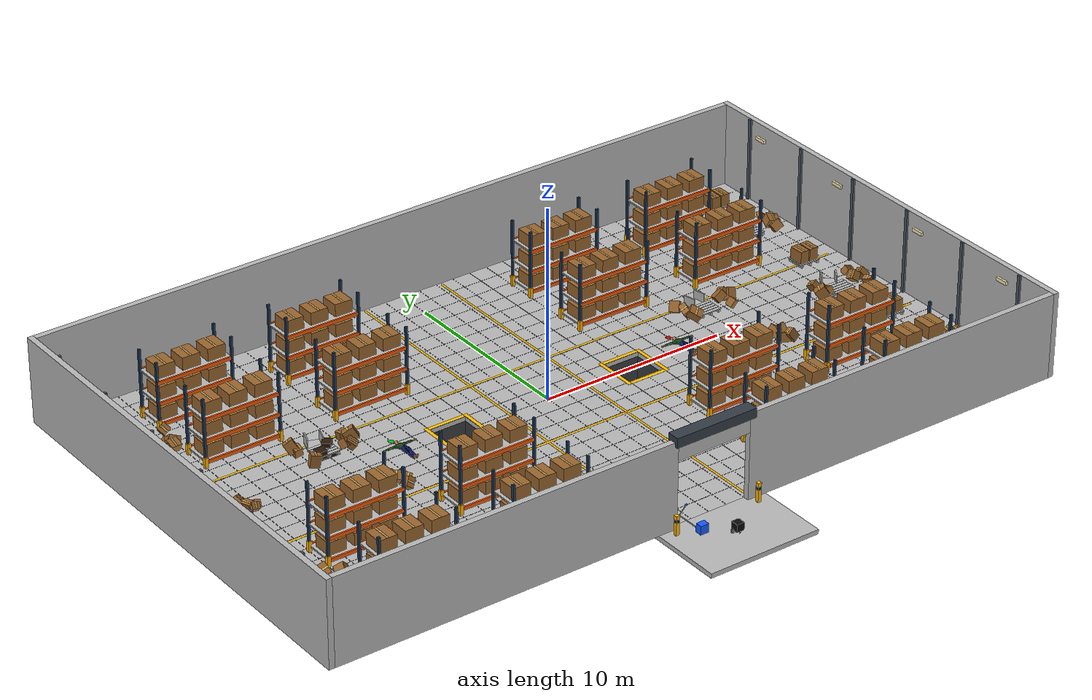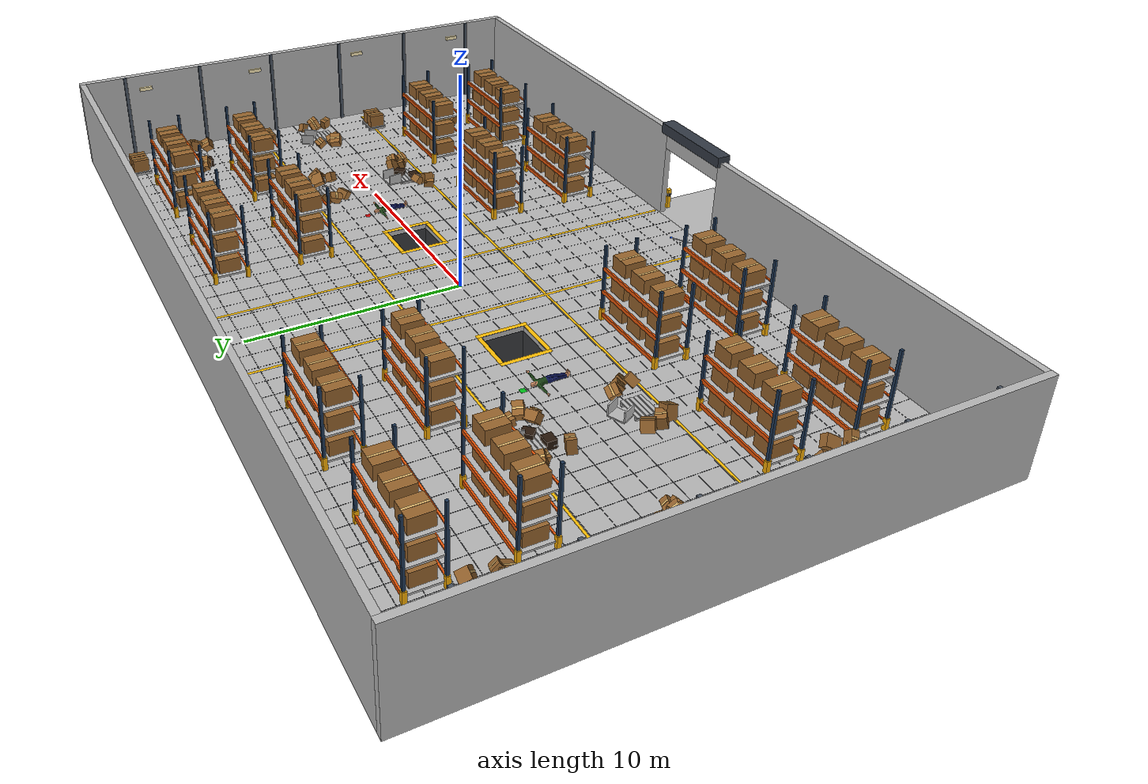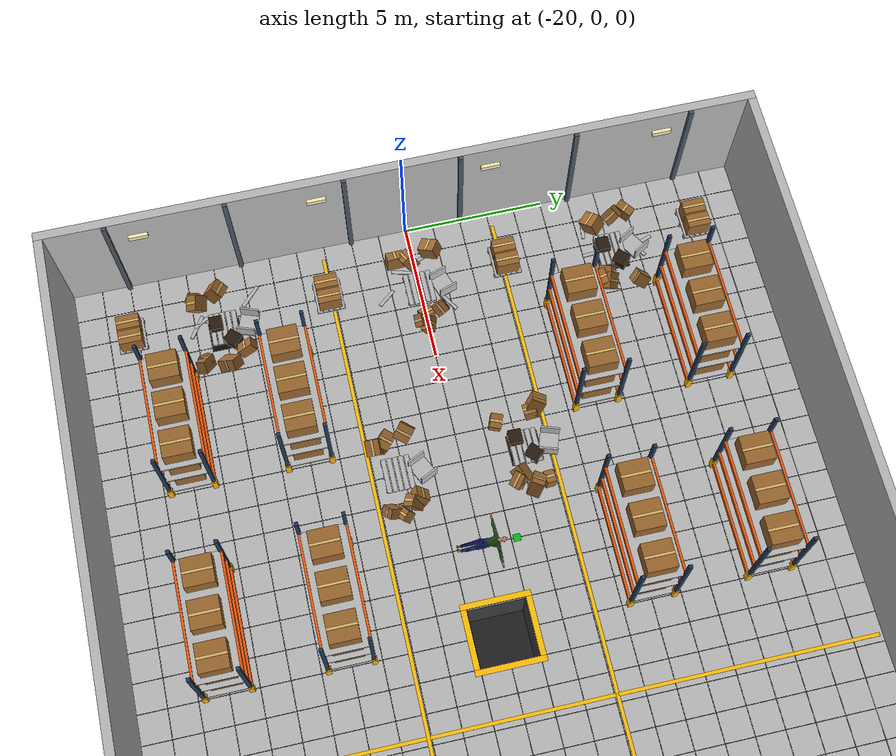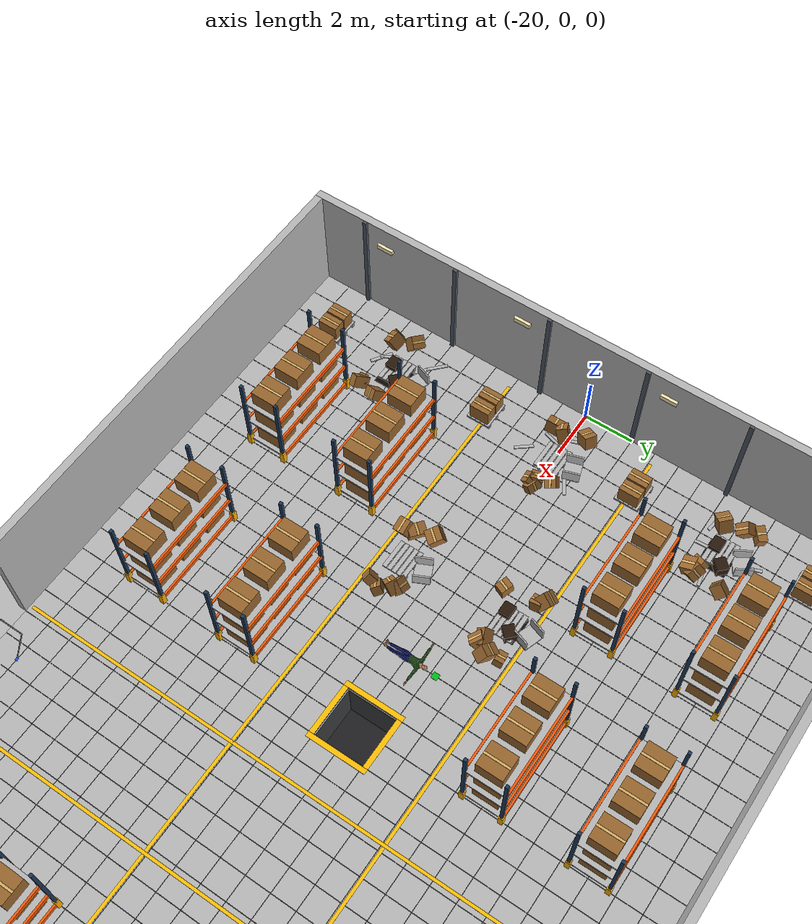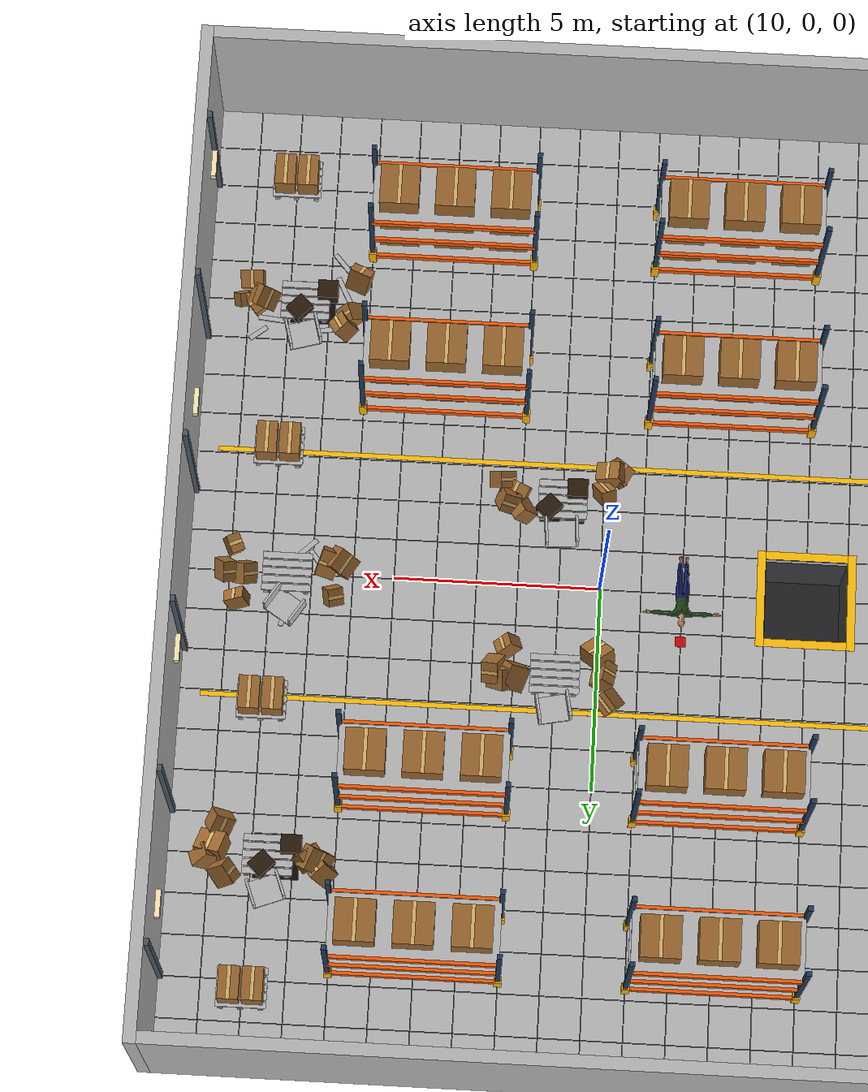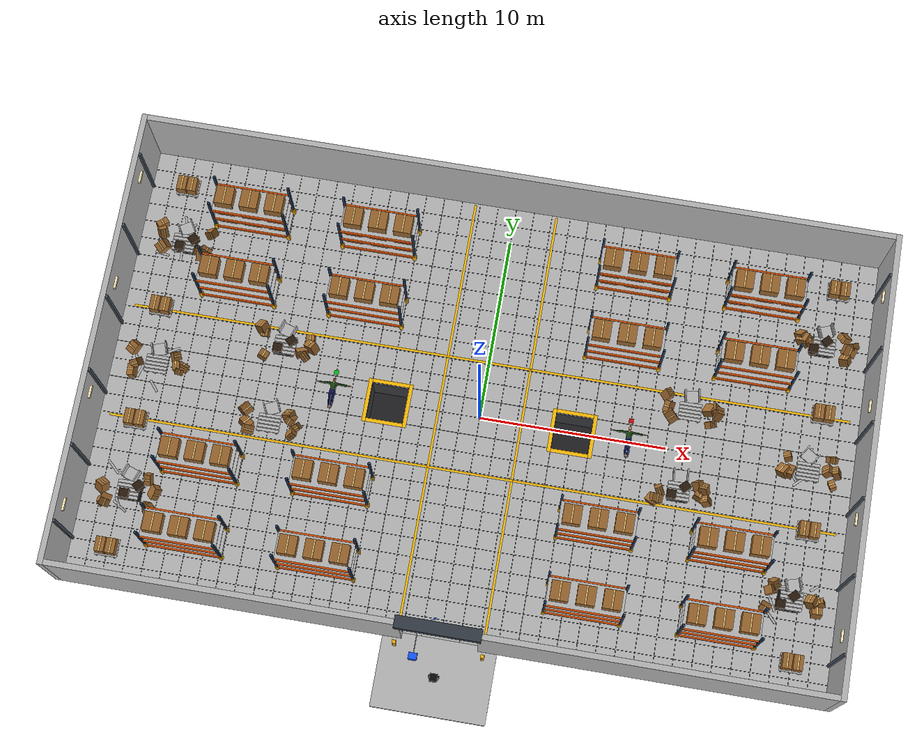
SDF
<sdf version="1.9">
 <world name="factory">
  <gravity>0 0 -9.81</gravity>
  <physics name="physics" type="ignored">
   <max_step_size>0.02</max_step_size>
   <real_time_factor>1</real_time_factor>
  </physics>
  <plugin filename="gz-sim-physics-system" name="gz::sim::systems::Physics"/>
  <plugin filename="gz-sim-user-commands-system" name="gz::sim::systems::UserCommands"/>
  <plugin filename="gz-sim-scene-broadcaster-system" name="gz::sim::systems::SceneBroadcaster"/>
  <plugin filename="gz-sim-particle-emitter-system" name="gz::sim::systems::ParticleEmitter"/>
  <scene><ambient>.55 .55 .55 1</ambient><background>.65 .7 .76 1</background><shadows>false</shadows></scene>
  <light name="sun" type="directional">
   <pose>0 0 15 0 0 0</pose>
   <diffuse>.85 .85 .85 1</diffuse>
   <specular>.15 .15 .15 1</specular>
   <direction>-.3 .2 -1</direction>
  </light>
  <model name="unified_factory_floor">
   <static>true</static>
   <link name="body">
    <visual name="floor_0_0_visual">
     <pose>-13 -6.5 -0.12 0 0 0</pose>
     <geometry><mesh><uri>model://factory_scene_assets/meshes/floor_000.dae</uri></mesh></geometry>
    </visual>
    <collision name="floor_0_0_collision">
     <pose>-13 -6.5 -0.12 0 0 0</pose>
     <geometry><box><size>14 11 0.24</size></box></geometry>
    </collision>
    <visual name="floor_0_1_visual">
     <pose>-13 0 -0.12 0 0 0</pose>
     <geometry><mesh><uri>model://factory_scene_assets/meshes/floor_001.dae</uri></mesh></geometry>
    </visual>
    <collision name="floor_0_1_collision">
     <pose>-13 0 -0.12 0 0 0</pose>
     <geometry><box><size>14 2 0.24</size></box></geometry>
    </collision>
    <visual name="floor_0_2_visual">
     <pose>-13 6.5 -0.12 0 0 0</pose>
     <geometry><mesh><uri>model://factory_scene_assets/meshes/floor_000.dae</uri></mesh></geometry>
    </visual>
    <collision name="floor_0_2_collision">
     <pose>-13 6.5 -0.12 0 0 0</pose>
     <geometry><box><size>14 11 0.24</size></box></geometry>
    </collision>
    <visual name="floor_1_0_visual">
     <pose>-5 -6.5 -0.12 0 0 0</pose>
     <geometry><mesh><uri>model://factory_scene_assets/meshes/floor_002.dae</uri></mesh></geometry>
    </visual>
    <collision name="floor_1_0_collision">
     <pose>-5 -6.5 -0.12 0 0 0</pose>
     <geometry><box><size>2 11 0.24</size></box></geometry>
    </collision>
    <visual name="floor_1_2_visual">
     <pose>-5 6.5 -0.12 0 0 0</pose>
     <geometry><mesh><uri>model://factory_scene_assets/meshes/floor_002.dae</uri></mesh></geometry>
    </visual>
    <collision name="floor_1_2_collision">
     <pose>-5 6.5 -0.12 0 0 0</pose>
     <geometry><box><size>2 11 0.24</size></box></geometry>
    </collision>
    <visual name="floor_2_0_visual">
     <pose>0 -6.5 -0.12 0 0 0</pose>
     <geometry><mesh><uri>model://factory_scene_assets/meshes/floor_003.dae</uri></mesh></geometry>
    </visual>
    <collision name="floor_2_0_collision">
     <pose>0 -6.5 -0.12 0 0 0</pose>
     <geometry><box><size>8 11 0.24</size></box></geometry>
    </collision>
    <visual name="floor_2_1_visual">
     <pose>0 0 -0.12 0 0 0</pose>
     <geometry><mesh><uri>model://factory_scene_assets/meshes/floor_004.dae</uri></mesh></geometry>
    </visual>
    <collision name="floor_2_1_collision">
     <pose>0 0 -0.12 0 0 0</pose>
     <geometry><box><size>8 2 0.24</size></box></geometry>
    </collision>
    <visual name="floor_2_2_visual">
     <pose>0 6.5 -0.12 0 0 0</pose>
     <geometry><mesh><uri>model://factory_scene_assets/meshes/floor_003.dae</uri></mesh></geometry>
    </visual>
    <collision name="floor_2_2_collision">
     <pose>0 6.5 -0.12 0 0 0</pose>
     <geometry><box><size>8 11 0.24</size></box></geometry>
    </collision>
    <visual name="floor_3_0_visual">
     <pose>5 -6.5 -0.12 0 0 0</pose>
     <geometry><mesh><uri>model://factory_scene_assets/meshes/floor_002.dae</uri></mesh></geometry>
    </visual>
    <collision name="floor_3_0_collision">
     <pose>5 -6.5 -0.12 0 0 0</pose>
     <geometry><box><size>2 11 0.24</size></box></geometry>
    </collision>
    <visual name="floor_3_2_visual">
     <pose>5 6.5 -0.12 0 0 0</pose>
     <geometry><mesh><uri>model://factory_scene_assets/meshes/floor_002.dae</uri></mesh></geometry>
    </visual>
    <collision name="floor_3_2_collision">
     <pose>5 6.5 -0.12 0 0 0</pose>
     <geometry><box><size>2 11 0.24</size></box></geometry>
    </collision>
    <visual name="floor_4_0_visual">
     <pose>13 -6.5 -0.12 0 0 0</pose>
     <geometry><mesh><uri>model://factory_scene_assets/meshes/floor_000.dae</uri></mesh></geometry>
    </visual>
    <collision name="floor_4_0_collision">
     <pose>13 -6.5 -0.12 0 0 0</pose>
     <geometry><box><size>14 11 0.24</size></box></geometry>
    </collision>
    <visual name="floor_4_1_visual">
     <pose>13 0 -0.12 0 0 0</pose>
     <geometry><mesh><uri>model://factory_scene_assets/meshes/floor_001.dae</uri></mesh></geometry>
    </visual>
    <collision name="floor_4_1_collision">
     <pose>13 0 -0.12 0 0 0</pose>
     <geometry><box><size>14 2 0.24</size></box></geometry>
    </collision>
    <visual name="floor_4_2_visual">
     <pose>13 6.5 -0.12 0 0 0</pose>
     <geometry><mesh><uri>model://factory_scene_assets/meshes/floor_000.dae</uri></mesh></geometry>
    </visual>
    <collision name="floor_4_2_collision">
     <pose>13 6.5 -0.12 0 0 0</pose>
     <geometry><box><size>14 11 0.24</size></box></geometry>
    </collision>
    <visual name="gx_-19_0_visual">
     <pose>-19 0 0.001 0 0 0</pose>
     <geometry><box><size>0.018 24 0.002</size></box></geometry>
     <material><ambient>.24 .25 .26 1</ambient><diffuse>.24 .25 .26 1</diffuse></material>
    </visual>
    <visual name="gx_-18_0_visual">
     <pose>-18 0 0.001 0 0 0</pose>
     <geometry><box><size>0.018 24 0.002</size></box></geometry>
     <material><ambient>.24 .25 .26 1</ambient><diffuse>.24 .25 .26 1</diffuse></material>
    </visual>
    <visual name="gx_-17_0_visual">
     <pose>-17 0 0.001 0 0 0</pose>
     <geometry><box><size>0.018 24 0.002</size></box></geometry>
     <material><ambient>.24 .25 .26 1</ambient><diffuse>.24 .25 .26 1</diffuse></material>
    </visual>
    <visual name="gx_-16_0_visual">
     <pose>-16 0 0.001 0 0 0</pose>
     <geometry><box><size>0.018 24 0.002</size></box></geometry>
     <material><ambient>.24 .25 .26 1</ambient><diffuse>.24 .25 .26 1</diffuse></material>
    </visual>
    <visual name="gx_-15_0_visual">
     <pose>-15 0 0.001 0 0 0</pose>
     <geometry><box><size>0.018 24 0.002</size></box></geometry>
     <material><ambient>.24 .25 .26 1</ambient><diffuse>.24 .25 .26 1</diffuse></material>
    </visual>
    <visual name="gx_-14_0_visual">
     <pose>-14 0 0.001 0 0 0</pose>
     <geometry><box><size>0.018 24 0.002</size></box></geometry>
     <material><ambient>.24 .25 .26 1</ambient><diffuse>.24 .25 .26 1</diffuse></material>
    </visual>
    <visual name="gx_-13_0_visual">
     <pose>-13 0 0.001 0 0 0</pose>
     <geometry><box><size>0.018 24 0.002</size></box></geometry>
     <material><ambient>.24 .25 .26 1</ambient><diffuse>.24 .25 .26 1</diffuse></material>
    </visual>
    <visual name="gx_-12_0_visual">
     <pose>-12 0 0.001 0 0 0</pose>
     <geometry><box><size>0.018 24 0.002</size></box></geometry>
     <material><ambient>.24 .25 .26 1</ambient><diffuse>.24 .25 .26 1</diffuse></material>
    </visual>
    <visual name="gx_-11_0_visual">
     <pose>-11 0 0.001 0 0 0</pose>
     <geometry><box><size>0.018 24 0.002</size></box></geometry>
     <material><ambient>.24 .25 .26 1</ambient><diffuse>.24 .25 .26 1</diffuse></material>
    </visual>
    <visual name="gx_-10_0_visual">
     <pose>-10 0 0.001 0 0 0</pose>
     <geometry><box><size>0.018 24 0.002</size></box></geometry>
     <material><ambient>.24 .25 .26 1</ambient><diffuse>.24 .25 .26 1</diffuse></material>
    </visual>
    <visual name="gx_-9_0_visual">
     <pose>-9 0 0.001 0 0 0</pose>
     <geometry><box><size>0.018 24 0.002</size></box></geometry>
     <material><ambient>.24 .25 .26 1</ambient><diffuse>.24 .25 .26 1</diffuse></material>
    </visual>
    <visual name="gx_-8_0_visual">
     <pose>-8 0 0.001 0 0 0</pose>
     <geometry><box><size>0.018 24 0.002</size></box></geometry>
     <material><ambient>.24 .25 .26 1</ambient><diffuse>.24 .25 .26 1</diffuse></material>
    </visual>
    <visual name="gx_-7_0_visual">
     <pose>-7 0 0.001 0 0 0</pose>
     <geometry><box><size>0.018 24 0.002</size></box></geometry>
     <material><ambient>.24 .25 .26 1</ambient><diffuse>.24 .25 .26 1</diffuse></material>
    </visual>
    <visual name="gx_-6_0_visual">
     <pose>-6 0 0.001 0 0 0</pose>
     <geometry><box><size>0.018 24 0.002</size></box></geometry>
     <material><ambient>.24 .25 .26 1</ambient><diffuse>.24 .25 .26 1</diffuse></material>
    </visual>
    <visual name="gx_-5_0_visual">
     <pose>-5 -6.5 0.001 0 0 0</pose>
     <geometry><box><size>0.018 11 0.002</size></box></geometry>
     <material><ambient>.24 .25 .26 1</ambient><diffuse>.24 .25 .26 1</diffuse></material>
    </visual>
    <visual name="gx_-5_1_visual">
     <pose>-5 6.5 0.001 0 0 0</pose>
     <geometry><box><size>0.018 11 0.002</size></box></geometry>
     <material><ambient>.24 .25 .26 1</ambient><diffuse>.24 .25 .26 1</diffuse></material>
    </visual>
    <visual name="gx_-4_0_visual">
     <pose>-4 0 0.001 0 0 0</pose>
     <geometry><box><size>0.018 24 0.002</size></box></geometry>
     <material><ambient>.24 .25 .26 1</ambient><diffuse>.24 .25 .26 1</diffuse></material>
    </visual>
    <visual name="gx_-3_0_visual">
     <pose>-3 0 0.001 0 0 0</pose>
     <geometry><box><size>0.018 24 0.002</size></box></geometry>
     <material><ambient>.24 .25 .26 1</ambient><diffuse>.24 .25 .26 1</diffuse></material>
    </visual>
    <visual name="gx_-2_0_visual">
     <pose>-2 0 0.001 0 0 0</pose>
     <geometry><box><size>0.018 24 0.002</size></box></geometry>
     <material><ambient>.24 .25 .26 1</ambient><diffuse>.24 .25 .26 1</diffuse></material>
    </visual>
    <visual name="gx_-1_0_visual">
     <pose>-1 0 0.001 0 0 0</pose>
     <geometry><box><size>0.018 24 0.002</size></box></geometry>
     <material><ambient>.24 .25 .26 1</ambient><diffuse>.24 .25 .26 1</diffuse></material>
    </visual>
    <visual name="gx_0_0_visual">
     <pose>0 0 0.001 0 0 0</pose>
     <geometry><box><size>0.018 24 0.002</size></box></geometry>
     <material><ambient>.24 .25 .26 1</ambient><diffuse>.24 .25 .26 1</diffuse></material>
    </visual>
    <visual name="gx_1_0_visual">
     <pose>1 0 0.001 0 0 0</pose>
     <geometry><box><size>0.018 24 0.002</size></box></geometry>
     <material><ambient>.24 .25 .26 1</ambient><diffuse>.24 .25 .26 1</diffuse></material>
    </visual>
    <visual name="gx_2_0_visual">
     <pose>2 0 0.001 0 0 0</pose>
     <geometry><box><size>0.018 24 0.002</size></box></geometry>
     <material><ambient>.24 .25 .26 1</ambient><diffuse>.24 .25 .26 1</diffuse></material>
    </visual>
    <visual name="gx_3_0_visual">
     <pose>3 0 0.001 0 0 0</pose>
     <geometry><box><size>0.018 24 0.002</size></box></geometry>
     <material><ambient>.24 .25 .26 1</ambient><diffuse>.24 .25 .26 1</diffuse></material>
    </visual>
    <visual name="gx_4_0_visual">
     <pose>4 0 0.001 0 0 0</pose>
     <geometry><box><size>0.018 24 0.002</size></box></geometry>
     <material><ambient>.24 .25 .26 1</ambient><diffuse>.24 .25 .26 1</diffuse></material>
    </visual>
    <visual name="gx_5_0_visual">
     <pose>5 -6.5 0.001 0 0 0</pose>
     <geometry><box><size>0.018 11 0.002</size></box></geometry>
     <material><ambient>.24 .25 .26 1</ambient><diffuse>.24 .25 .26 1</diffuse></material>
    </visual>
    <visual name="gx_5_1_visual">
     <pose>5 6.5 0.001 0 0 0</pose>
     <geometry><box><size>0.018 11 0.002</size></box></geometry>
     <material><ambient>.24 .25 .26 1</ambient><diffuse>.24 .25 .26 1</diffuse></material>
    </visual>
    <visual name="gx_6_0_visual">
     <pose>6 0 0.001 0 0 0</pose>
     <geometry><box><size>0.018 24 0.002</size></box></geometry>
     <material><ambient>.24 .25 .26 1</ambient><diffuse>.24 .25 .26 1</diffuse></material>
    </visual>
    <visual name="gx_7_0_visual">
     <pose>7 0 0.001 0 0 0</pose>
     <geometry><box><size>0.018 24 0.002</size></box></geometry>
     <material><ambient>.24 .25 .26 1</ambient><diffuse>.24 .25 .26 1</diffuse></material>
    </visual>
    <visual name="gx_8_0_visual">
     <pose>8 0 0.001 0 0 0</pose>
     <geometry><box><size>0.018 24 0.002</size></box></geometry>
     <material><ambient>.24 .25 .26 1</ambient><diffuse>.24 .25 .26 1</diffuse></material>
    </visual>
    <visual name="gx_9_0_visual">
     <pose>9 0 0.001 0 0 0</pose>
     <geometry><box><size>0.018 24 0.002</size></box></geometry>
     <material><ambient>.24 .25 .26 1</ambient><diffuse>.24 .25 .26 1</diffuse></material>
    </visual>
    <visual name="gx_10_0_visual">
     <pose>10 0 0.001 0 0 0</pose>
     <geometry><box><size>0.018 24 0.002</size></box></geometry>
     <material><ambient>.24 .25 .26 1</ambient><diffuse>.24 .25 .26 1</diffuse></material>
    </visual>
    <visual name="gx_11_0_visual">
     <pose>11 0 0.001 0 0 0</pose>
     <geometry><box><size>0.018 24 0.002</size></box></geometry>
     <material><ambient>.24 .25 .26 1</ambient><diffuse>.24 .25 .26 1</diffuse></material>
    </visual>
    <visual name="gx_12_0_visual">
     <pose>12 0 0.001 0 0 0</pose>
     <geometry><box><size>0.018 24 0.002</size></box></geometry>
     <material><ambient>.24 .25 .26 1</ambient><diffuse>.24 .25 .26 1</diffuse></material>
    </visual>
    <visual name="gx_13_0_visual">
     <pose>13 0 0.001 0 0 0</pose>
     <geometry><box><size>0.018 24 0.002</size></box></geometry>
     <material><ambient>.24 .25 .26 1</ambient><diffuse>.24 .25 .26 1</diffuse></material>
    </visual>
    <visual name="gx_14_0_visual">
     <pose>14 0 0.001 0 0 0</pose>
     <geometry><box><size>0.018 24 0.002</size></box></geometry>
     <material><ambient>.24 .25 .26 1</ambient><diffuse>.24 .25 .26 1</diffuse></material>
    </visual>
    <visual name="gx_15_0_visual">
     <pose>15 0 0.001 0 0 0</pose>
     <geometry><box><size>0.018 24 0.002</size></box></geometry>
     <material><ambient>.24 .25 .26 1</ambient><diffuse>.24 .25 .26 1</diffuse></material>
    </visual>
    <visual name="gx_16_0_visual">
     <pose>16 0 0.001 0 0 0</pose>
     <geometry><box><size>0.018 24 0.002</size></box></geometry>
     <material><ambient>.24 .25 .26 1</ambient><diffuse>.24 .25 .26 1</diffuse></material>
    </visual>
    <visual name="gx_17_0_visual">
     <pose>17 0 0.001 0 0 0</pose>
     <geometry><box><size>0.018 24 0.002</size></box></geometry>
     <material><ambient>.24 .25 .26 1</ambient><diffuse>.24 .25 .26 1</diffuse></material>
    </visual>
    <visual name="gx_18_0_visual">
     <pose>18 0 0.001 0 0 0</pose>
     <geometry><box><size>0.018 24 0.002</size></box></geometry>
     <material><ambient>.24 .25 .26 1</ambient><diffuse>.24 .25 .26 1</diffuse></material>
    </visual>
    <visual name="gx_19_0_visual">
     <pose>19 0 0.001 0 0 0</pose>
     <geometry><box><size>0.018 24 0.002</size></box></geometry>
     <material><ambient>.24 .25 .26 1</ambient><diffuse>.24 .25 .26 1</diffuse></material>
    </visual>
    <visual name="gy_-11_0_visual">
     <pose>0 -11 0.001 0 0 0</pose>
     <geometry><box><size>40 0.018 0.002</size></box></geometry>
     <material><ambient>.24 .25 .26 1</ambient><diffuse>.24 .25 .26 1</diffuse></material>
    </visual>
    <visual name="gy_-10_0_visual">
     <pose>0 -10 0.001 0 0 0</pose>
     <geometry><box><size>40 0.018 0.002</size></box></geometry>
     <material><ambient>.24 .25 .26 1</ambient><diffuse>.24 .25 .26 1</diffuse></material>
    </visual>
    <visual name="gy_-9_0_visual">
     <pose>0 -9 0.001 0 0 0</pose>
     <geometry><box><size>40 0.018 0.002</size></box></geometry>
     <material><ambient>.24 .25 .26 1</ambient><diffuse>.24 .25 .26 1</diffuse></material>
    </visual>
    <visual name="gy_-8_0_visual">
     <pose>0 -8 0.001 0 0 0</pose>
     <geometry><box><size>40 0.018 0.002</size></box></geometry>
     <material><ambient>.24 .25 .26 1</ambient><diffuse>.24 .25 .26 1</diffuse></material>
    </visual>
    <visual name="gy_-7_0_visual">
     <pose>0 -7 0.001 0 0 0</pose>
     <geometry><box><size>40 0.018 0.002</size></box></geometry>
     <material><ambient>.24 .25 .26 1</ambient><diffuse>.24 .25 .26 1</diffuse></material>
    </visual>
    <visual name="gy_-6_0_visual">
     <pose>0 -6 0.001 0 0 0</pose>
     <geometry><box><size>40 0.018 0.002</size></box></geometry>
     <material><ambient>.24 .25 .26 1</ambient><diffuse>.24 .25 .26 1</diffuse></material>
    </visual>
    <visual name="gy_-5_0_visual">
     <pose>0 -5 0.001 0 0 0</pose>
     <geometry><box><size>40 0.018 0.002</size></box></geometry>
     <material><ambient>.24 .25 .26 1</ambient><diffuse>.24 .25 .26 1</diffuse></material>
    </visual>
    <visual name="gy_-4_0_visual">
     <pose>0 -4 0.001 0 0 0</pose>
     <geometry><box><size>40 0.018 0.002</size></box></geometry>
     <material><ambient>.24 .25 .26 1</ambient><diffuse>.24 .25 .26 1</diffuse></material>
    </visual>
    <visual name="gy_-3_0_visual">
     <pose>0 -3 0.001 0 0 0</pose>
     <geometry><box><size>40 0.018 0.002</size></box></geometry>
     <material><ambient>.24 .25 .26 1</ambient><diffuse>.24 .25 .26 1</diffuse></material>
    </visual>
    <visual name="gy_-2_0_visual">
     <pose>0 -2 0.001 0 0 0</pose>
     <geometry><box><size>40 0.018 0.002</size></box></geometry>
     <material><ambient>.24 .25 .26 1</ambient><diffuse>.24 .25 .26 1</diffuse></material>
    </visual>
    <visual name="gy_-1_0_visual">
     <pose>0 -1 0.001 0 0 0</pose>
     <geometry><box><size>40 0.018 0.002</size></box></geometry>
     <material><ambient>.24 .25 .26 1</ambient><diffuse>.24 .25 .26 1</diffuse></material>
    </visual>
    <visual name="gy_0_0_visual">
     <pose>-13 0 0.001 0 0 0</pose>
     <geometry><box><size>14 0.018 0.002</size></box></geometry>
     <material><ambient>.24 .25 .26 1</ambient><diffuse>.24 .25 .26 1</diffuse></material>
    </visual>
    <visual name="gy_0_1_visual">
     <pose>0 0 0.001 0 0 0</pose>
     <geometry><box><size>8 0.018 0.002</size></box></geometry>
     <material><ambient>.24 .25 .26 1</ambient><diffuse>.24 .25 .26 1</diffuse></material>
    </visual>
    <visual name="gy_0_2_visual">
     <pose>13 0 0.001 0 0 0</pose>
     <geometry><box><size>14 0.018 0.002</size></box></geometry>
     <material><ambient>.24 .25 .26 1</ambient><diffuse>.24 .25 .26 1</diffuse></material>
    </visual>
    <visual name="gy_1_0_visual">
     <pose>0 1 0.001 0 0 0</pose>
     <geometry><box><size>40 0.018 0.002</size></box></geometry>
     <material><ambient>.24 .25 .26 1</ambient><diffuse>.24 .25 .26 1</diffuse></material>
    </visual>
    <visual name="gy_2_0_visual">
     <pose>0 2 0.001 0 0 0</pose>
     <geometry><box><size>40 0.018 0.002</size></box></geometry>
     <material><ambient>.24 .25 .26 1</ambient><diffuse>.24 .25 .26 1</diffuse></material>
    </visual>
    <visual name="gy_3_0_visual">
     <pose>0 3 0.001 0 0 0</pose>
     <geometry><box><size>40 0.018 0.002</size></box></geometry>
     <material><ambient>.24 .25 .26 1</ambient><diffuse>.24 .25 .26 1</diffuse></material>
    </visual>
    <visual name="gy_4_0_visual">
     <pose>0 4 0.001 0 0 0</pose>
     <geometry><box><size>40 0.018 0.002</size></box></geometry>
     <material><ambient>.24 .25 .26 1</ambient><diffuse>.24 .25 .26 1</diffuse></material>
    </visual>
    <visual name="gy_5_0_visual">
     <pose>0 5 0.001 0 0 0</pose>
     <geometry><box><size>40 0.018 0.002</size></box></geometry>
     <material><ambient>.24 .25 .26 1</ambient><diffuse>.24 .25 .26 1</diffuse></material>
    </visual>
    <visual name="gy_6_0_visual">
     <pose>0 6 0.001 0 0 0</pose>
     <geometry><box><size>40 0.018 0.002</size></box></geometry>
     <material><ambient>.24 .25 .26 1</ambient><diffuse>.24 .25 .26 1</diffuse></material>
    </visual>
    <visual name="gy_7_0_visual">
     <pose>0 7 0.001 0 0 0</pose>
     <geometry><box><size>40 0.018 0.002</size></box></geometry>
     <material><ambient>.24 .25 .26 1</ambient><diffuse>.24 .25 .26 1</diffuse></material>
    </visual>
    <visual name="gy_8_0_visual">
     <pose>0 8 0.001 0 0 0</pose>
     <geometry><box><size>40 0.018 0.002</size></box></geometry>
     <material><ambient>.24 .25 .26 1</ambient><diffuse>.24 .25 .26 1</diffuse></material>
    </visual>
    <visual name="gy_9_0_visual">
     <pose>0 9 0.001 0 0 0</pose>
     <geometry><box><size>40 0.018 0.002</size></box></geometry>
     <material><ambient>.24 .25 .26 1</ambient><diffuse>.24 .25 .26 1</diffuse></material>
    </visual>
    <visual name="gy_10_0_visual">
     <pose>0 10 0.001 0 0 0</pose>
     <geometry><box><size>40 0.018 0.002</size></box></geometry>
     <material><ambient>.24 .25 .26 1</ambient><diffuse>.24 .25 .26 1</diffuse></material>
    </visual>
    <visual name="gy_11_0_visual">
     <pose>0 11 0.001 0 0 0</pose>
     <geometry><box><size>40 0.018 0.002</size></box></geometry>
     <material><ambient>.24 .25 .26 1</ambient><diffuse>.24 .25 .26 1</diffuse></material>
    </visual>
   </link>
  </model>
  <model name="pit_1">
   <static>true</static>
   <pose>-5 0 0 0 0 0</pose>
   <link name="body">
    <visual name="bottom_visual">
     <pose>0 0 -2.1 0 0 0</pose>
     <geometry><box><size>2.4 2.4 0.2</size></box></geometry>
     <material><ambient>.12 .12 .13 1</ambient><diffuse>.12 .12 .13 1</diffuse></material>
    </visual>
    <collision name="bottom_collision">
     <pose>0 0 -2.1 0 0 0</pose>
     <geometry><box><size>2.4 2.4 0.2</size></box></geometry>
    </collision>
    <visual name="wall0_visual">
     <pose>1.1 0 -1.12 0 0 0</pose>
     <geometry><box><size>0.2 2.4 1.76</size></box></geometry>
     <material><ambient>.22 .23 .24 1</ambient><diffuse>.22 .23 .24 1</diffuse></material>
    </visual>
    <collision name="wall0_collision">
     <pose>1.1 0 -1.12 0 0 0</pose>
     <geometry><box><size>0.2 2.4 1.76</size></box></geometry>
    </collision>
    <visual name="edge0_visual">
     <pose>1.1 0 0.003 0 0 0</pose>
     <geometry><box><size>0.2 2.4 0.006</size></box></geometry>
     <material><ambient>1 .75 .02 1</ambient><diffuse>1 .75 .02 1</diffuse></material>
    </visual>
    <visual name="wall1_visual">
     <pose>-1.1 0 -1.12 0 0 0</pose>
     <geometry><box><size>0.2 2.4 1.76</size></box></geometry>
     <material><ambient>.22 .23 .24 1</ambient><diffuse>.22 .23 .24 1</diffuse></material>
    </visual>
    <collision name="wall1_collision">
     <pose>-1.1 0 -1.12 0 0 0</pose>
     <geometry><box><size>0.2 2.4 1.76</size></box></geometry>
    </collision>
    <visual name="edge1_visual">
     <pose>-1.1 0 0.003 0 0 0</pose>
     <geometry><box><size>0.2 2.4 0.006</size></box></geometry>
     <material><ambient>1 .75 .02 1</ambient><diffuse>1 .75 .02 1</diffuse></material>
    </visual>
    <visual name="wall2_visual">
     <pose>0 1.1 -1.12 0 0 0</pose>
     <geometry><box><size>2 0.2 1.76</size></box></geometry>
     <material><ambient>.22 .23 .24 1</ambient><diffuse>.22 .23 .24 1</diffuse></material>
    </visual>
    <collision name="wall2_collision">
     <pose>0 1.1 -1.12 0 0 0</pose>
     <geometry><box><size>2 0.2 1.76</size></box></geometry>
    </collision>
    <visual name="edge2_visual">
     <pose>0 1.1 0.003 0 0 0</pose>
     <geometry><box><size>2 0.2 0.006</size></box></geometry>
     <material><ambient>1 .75 .02 1</ambient><diffuse>1 .75 .02 1</diffuse></material>
    </visual>
    <visual name="wall3_visual">
     <pose>0 -1.1 -1.12 0 0 0</pose>
     <geometry><box><size>2 0.2 1.76</size></box></geometry>
     <material><ambient>.22 .23 .24 1</ambient><diffuse>.22 .23 .24 1</diffuse></material>
    </visual>
    <collision name="wall3_collision">
     <pose>0 -1.1 -1.12 0 0 0</pose>
     <geometry><box><size>2 0.2 1.76</size></box></geometry>
    </collision>
    <visual name="edge3_visual">
     <pose>0 -1.1 0.003 0 0 0</pose>
     <geometry><box><size>2 0.2 0.006</size></box></geometry>
     <material><ambient>1 .75 .02 1</ambient><diffuse>1 .75 .02 1</diffuse></material>
    </visual>
   </link>
  </model>
  <model name="pit_2">
   <static>true</static>
   <pose>5 0 0 0 0 0</pose>
   <link name="body">
    <visual name="bottom_visual">
     <pose>0 0 -2.1 0 0 0</pose>
     <geometry><box><size>2.4 2.4 0.2</size></box></geometry>
     <material><ambient>.12 .12 .13 1</ambient><diffuse>.12 .12 .13 1</diffuse></material>
    </visual>
    <collision name="bottom_collision">
     <pose>0 0 -2.1 0 0 0</pose>
     <geometry><box><size>2.4 2.4 0.2</size></box></geometry>
    </collision>
    <visual name="wall0_visual">
     <pose>1.1 0 -1.12 0 0 0</pose>
     <geometry><box><size>0.2 2.4 1.76</size></box></geometry>
     <material><ambient>.22 .23 .24 1</ambient><diffuse>.22 .23 .24 1</diffuse></material>
    </visual>
    <collision name="wall0_collision">
     <pose>1.1 0 -1.12 0 0 0</pose>
     <geometry><box><size>0.2 2.4 1.76</size></box></geometry>
    </collision>
    <visual name="edge0_visual">
     <pose>1.1 0 0.003 0 0 0</pose>
     <geometry><box><size>0.2 2.4 0.006</size></box></geometry>
     <material><ambient>1 .75 .02 1</ambient><diffuse>1 .75 .02 1</diffuse></material>
    </visual>
    <visual name="wall1_visual">
     <pose>-1.1 0 -1.12 0 0 0</pose>
     <geometry><box><size>0.2 2.4 1.76</size></box></geometry>
     <material><ambient>.22 .23 .24 1</ambient><diffuse>.22 .23 .24 1</diffuse></material>
    </visual>
    <collision name="wall1_collision">
     <pose>-1.1 0 -1.12 0 0 0</pose>
     <geometry><box><size>0.2 2.4 1.76</size></box></geometry>
    </collision>
    <visual name="edge1_visual">
     <pose>-1.1 0 0.003 0 0 0</pose>
     <geometry><box><size>0.2 2.4 0.006</size></box></geometry>
     <material><ambient>1 .75 .02 1</ambient><diffuse>1 .75 .02 1</diffuse></material>
    </visual>
    <visual name="wall2_visual">
     <pose>0 1.1 -1.12 0 0 0</pose>
     <geometry><box><size>2 0.2 1.76</size></box></geometry>
     <material><ambient>.22 .23 .24 1</ambient><diffuse>.22 .23 .24 1</diffuse></material>
    </visual>
    <collision name="wall2_collision">
     <pose>0 1.1 -1.12 0 0 0</pose>
     <geometry><box><size>2 0.2 1.76</size></box></geometry>
    </collision>
    <visual name="edge2_visual">
     <pose>0 1.1 0.003 0 0 0</pose>
     <geometry><box><size>2 0.2 0.006</size></box></geometry>
     <material><ambient>1 .75 .02 1</ambient><diffuse>1 .75 .02 1</diffuse></material>
    </visual>
    <visual name="wall3_visual">
     <pose>0 -1.1 -1.12 0 0 0</pose>
     <geometry><box><size>2 0.2 1.76</size></box></geometry>
     <material><ambient>.22 .23 .24 1</ambient><diffuse>.22 .23 .24 1</diffuse></material>
    </visual>
    <collision name="wall3_collision">
     <pose>0 -1.1 -1.12 0 0 0</pose>
     <geometry><box><size>2 0.2 1.76</size></box></geometry>
    </collision>
    <visual name="edge3_visual">
     <pose>0 -1.1 0.003 0 0 0</pose>
     <geometry><box><size>2 0.2 0.006</size></box></geometry>
     <material><ambient>1 .75 .02 1</ambient><diffuse>1 .75 .02 1</diffuse></material>
    </visual>
   </link>
  </model>
  <model name="perimeter_one_entrance">
   <static>true</static>
   <link name="body">
    <visual name="west_visual">
     <pose>-20.15 0 2.25 0 0 0</pose>
     <geometry><mesh><uri>model://factory_scene_assets/meshes/wall_005.dae</uri></mesh></geometry>
    </visual>
    <collision name="west_collision">
     <pose>-20.15 0 2.25 0 0 0</pose>
     <geometry><box><size>0.3 24.6 4.5</size></box></geometry>
    </collision>
    <visual name="east_visual">
     <pose>20.15 0 2.25 0 0 0</pose>
     <geometry><mesh><uri>model://factory_scene_assets/meshes/wall_005.dae</uri></mesh></geometry>
    </visual>
    <collision name="east_collision">
     <pose>20.15 0 2.25 0 0 0</pose>
     <geometry><box><size>0.3 24.6 4.5</size></box></geometry>
    </collision>
    <visual name="north_visual">
     <pose>0 12.15 2.25 0 0 0</pose>
     <geometry><mesh><uri>model://factory_scene_assets/meshes/wall_006.dae</uri></mesh></geometry>
    </visual>
    <collision name="north_collision">
     <pose>0 12.15 2.25 0 0 0</pose>
     <geometry><box><size>40 0.3 4.5</size></box></geometry>
    </collision>
    <visual name="south_left_visual">
     <pose>-11 -12.15 2.25 0 0 0</pose>
     <geometry><mesh><uri>model://factory_scene_assets/meshes/wall_007.dae</uri></mesh></geometry>
    </visual>
    <collision name="south_left_collision">
     <pose>-11 -12.15 2.25 0 0 0</pose>
     <geometry><box><size>18 0.3 4.5</size></box></geometry>
    </collision>
    <visual name="south_right_visual">
     <pose>11 -12.15 2.25 0 0 0</pose>
     <geometry><mesh><uri>model://factory_scene_assets/meshes/wall_007.dae</uri></mesh></geometry>
    </visual>
    <collision name="south_right_collision">
     <pose>11 -12.15 2.25 0 0 0</pose>
     <geometry><box><size>18 0.3 4.5</size></box></geometry>
    </collision>
    <visual name="gate_header_visual">
     <pose>0 -12.15 4 0 0 0</pose>
     <geometry><mesh><uri>model://factory_scene_assets/meshes/wall_008.dae</uri></mesh></geometry>
    </visual>
    <collision name="gate_header_collision">
     <pose>0 -12.15 4 0 0 0</pose>
     <geometry><box><size>4 0.3 1</size></box></geometry>
    </collision>
    <visual name="raised_gate_housing_visual">
     <pose>0 -12.15 4.55 0 0 0</pose>
     <geometry><box><size>4.4 0.65 0.5</size></box></geometry>
     <material><ambient>.2 .23 .27 1</ambient><diffuse>.2 .23 .27 1</diffuse></material>
    </visual>
    <collision name="raised_gate_housing_collision">
     <pose>0 -12.15 4.55 0 0 0</pose>
     <geometry><box><size>4.4 0.65 0.5</size></box></geometry>
    </collision>
   </link>
  </model>
  <model name="entrance_apron">
   <static>true</static>
   <link name="body">
    <visual name="slab_visual">
     <pose>0 -14 -0.12 0 0 0</pose>
     <geometry><mesh><uri>model://factory_scene_assets/meshes/floor_009.dae</uri></mesh></geometry>
    </visual>
    <collision name="slab_collision">
     <pose>0 -14 -0.12 0 0 0</pose>
     <geometry><box><size>6 4 0.24</size></box></geometry>
    </collision>
   </link>
  </model>
  <model name="yellow_safety_lines">
   <static>true</static>
   <link name="body">
    <visual name="h0_visual">
     <pose>0 -3.1 0.004 0 0 0</pose>
     <geometry><box><size>39 0.12 0.006</size></box></geometry>
     <material><ambient>1 .76 .025 1</ambient><diffuse>1 .76 .025 1</diffuse></material>
    </visual>
    <visual name="h1_visual">
     <pose>0 3.1 0.004 0 0 0</pose>
     <geometry><box><size>39 0.12 0.006</size></box></geometry>
     <material><ambient>1 .76 .025 1</ambient><diffuse>1 .76 .025 1</diffuse></material>
    </visual>
    <visual name="v0_visual">
     <pose>-2.25 0 0.004 0 0 0</pose>
     <geometry><box><size>0.12 23.8 0.006</size></box></geometry>
     <material><ambient>1 .76 .025 1</ambient><diffuse>1 .76 .025 1</diffuse></material>
    </visual>
    <visual name="v1_visual">
     <pose>2.25 0 0.004 0 0 0</pose>
     <geometry><box><size>0.12 23.8 0.006</size></box></geometry>
     <material><ambient>1 .76 .025 1</ambient><diffuse>1 .76 .025 1</diffuse></material>
    </visual>
   </link>
  </model>
  <model name="rack_-1_0_0">
   <static>true</static>
   <pose>-7 -9 0 0 0 0</pose>
   <link name="body">
    <visual name="post0_visual">
     <pose>-2 -0.75 1.8 0 0 0</pose>
     <geometry><box><size>0.12 0.12 3.6</size></box></geometry>
     <material><ambient>.12 .22 .34 1</ambient><diffuse>.12 .22 .34 1</diffuse></material>
    </visual>
    <collision name="post0_collision">
     <pose>-2 -0.75 1.8 0 0 0</pose>
     <geometry><box><size>0.12 0.12 3.6</size></box></geometry>
    </collision>
    <visual name="guard0_visual">
     <pose>-2 -0.75 0.275 0 0 0</pose>
     <geometry><box><size>0.18 0.18 0.55</size></box></geometry>
     <material><ambient>1 .7 .02 1</ambient><diffuse>1 .7 .02 1</diffuse></material>
    </visual>
    <collision name="guard0_collision">
     <pose>-2 -0.75 0.275 0 0 0</pose>
     <geometry><box><size>0.18 0.18 0.55</size></box></geometry>
    </collision>
    <visual name="post1_visual">
     <pose>2 -0.75 1.8 0 0 0</pose>
     <geometry><box><size>0.12 0.12 3.6</size></box></geometry>
     <material><ambient>.12 .22 .34 1</ambient><diffuse>.12 .22 .34 1</diffuse></material>
    </visual>
    <collision name="post1_collision">
     <pose>2 -0.75 1.8 0 0 0</pose>
     <geometry><box><size>0.12 0.12 3.6</size></box></geometry>
    </collision>
    <visual name="guard1_visual">
     <pose>2 -0.75 0.275 0 0 0</pose>
     <geometry><box><size>0.18 0.18 0.55</size></box></geometry>
     <material><ambient>1 .7 .02 1</ambient><diffuse>1 .7 .02 1</diffuse></material>
    </visual>
    <collision name="guard1_collision">
     <pose>2 -0.75 0.275 0 0 0</pose>
     <geometry><box><size>0.18 0.18 0.55</size></box></geometry>
    </collision>
    <visual name="post2_visual">
     <pose>-2 0.75 1.8 0 0 0</pose>
     <geometry><box><size>0.12 0.12 3.6</size></box></geometry>
     <material><ambient>.12 .22 .34 1</ambient><diffuse>.12 .22 .34 1</diffuse></material>
    </visual>
    <collision name="post2_collision">
     <pose>-2 0.75 1.8 0 0 0</pose>
     <geometry><box><size>0.12 0.12 3.6</size></box></geometry>
    </collision>
    <visual name="guard2_visual">
     <pose>-2 0.75 0.275 0 0 0</pose>
     <geometry><box><size>0.18 0.18 0.55</size></box></geometry>
     <material><ambient>1 .7 .02 1</ambient><diffuse>1 .7 .02 1</diffuse></material>
    </visual>
    <collision name="guard2_collision">
     <pose>-2 0.75 0.275 0 0 0</pose>
     <geometry><box><size>0.18 0.18 0.55</size></box></geometry>
    </collision>
    <visual name="post3_visual">
     <pose>2 0.75 1.8 0 0 0</pose>
     <geometry><box><size>0.12 0.12 3.6</size></box></geometry>
     <material><ambient>.12 .22 .34 1</ambient><diffuse>.12 .22 .34 1</diffuse></material>
    </visual>
    <collision name="post3_collision">
     <pose>2 0.75 1.8 0 0 0</pose>
     <geometry><box><size>0.12 0.12 3.6</size></box></geometry>
    </collision>
    <visual name="guard3_visual">
     <pose>2 0.75 0.275 0 0 0</pose>
     <geometry><box><size>0.18 0.18 0.55</size></box></geometry>
     <material><ambient>1 .7 .02 1</ambient><diffuse>1 .7 .02 1</diffuse></material>
    </visual>
    <collision name="guard3_collision">
     <pose>2 0.75 0.275 0 0 0</pose>
     <geometry><box><size>0.18 0.18 0.55</size></box></geometry>
    </collision>
    <visual name="shelf0_visual">
     <pose>0 0 0.3 0 0 0</pose>
     <geometry><mesh><uri>model://factory_scene_assets/meshes/wood_010.dae</uri></mesh></geometry>
    </visual>
    <collision name="shelf0_collision">
     <pose>0 0 0.3 0 0 0</pose>
     <geometry><box><size>4 1.5 0.08</size></box></geometry>
    </collision>
    <visual name="beam0_0_visual">
     <pose>0 -0.77 0.3 0 0 0</pose>
     <geometry><box><size>4 0.08 0.18</size></box></geometry>
     <material><ambient>.95 .35 .035 1</ambient><diffuse>.95 .35 .035 1</diffuse></material>
    </visual>
    <collision name="beam0_0_collision">
     <pose>0 -0.77 0.3 0 0 0</pose>
     <geometry><box><size>4 0.08 0.18</size></box></geometry>
    </collision>
    <visual name="beam0_1_visual">
     <pose>0 0.77 0.3 0 0 0</pose>
     <geometry><box><size>4 0.08 0.18</size></box></geometry>
     <material><ambient>.95 .35 .035 1</ambient><diffuse>.95 .35 .035 1</diffuse></material>
    </visual>
    <collision name="beam0_1_collision">
     <pose>0 0.77 0.3 0 0 0</pose>
     <geometry><box><size>4 0.08 0.18</size></box></geometry>
    </collision>
    <visual name="cargo0_0_visual">
     <pose>-1.35 0 0.665 0 0 0</pose>
     <geometry><box><size>0.95 1 0.65</size></box></geometry>
     <material><ambient>.60 .40 .18 1</ambient><diffuse>.60 .40 .18 1</diffuse></material>
    </visual>
    <collision name="cargo0_0_collision">
     <pose>-1.35 0 0.665 0 0 0</pose>
     <geometry><box><size>0.95 1 0.65</size></box></geometry>
    </collision>
    <visual name="cargo0_0_tape_visual">
     <pose>-1.35 0 0.993 0 0 0</pose>
     <geometry><box><size>0.09 1 0.006</size></box></geometry>
     <material><ambient>.85 .69 .4 1</ambient><diffuse>.85 .69 .4 1</diffuse></material>
    </visual>
    <visual name="cargo0_1_visual">
     <pose>0 0 0.665 0 0 0</pose>
     <geometry><box><size>0.95 1 0.65</size></box></geometry>
     <material><ambient>.60 .40 .18 1</ambient><diffuse>.60 .40 .18 1</diffuse></material>
    </visual>
    <collision name="cargo0_1_collision">
     <pose>0 0 0.665 0 0 0</pose>
     <geometry><box><size>0.95 1 0.65</size></box></geometry>
    </collision>
    <visual name="cargo0_1_tape_visual">
     <pose>0 0 0.993 0 0 0</pose>
     <geometry><box><size>0.09 1 0.006</size></box></geometry>
     <material><ambient>.85 .69 .4 1</ambient><diffuse>.85 .69 .4 1</diffuse></material>
    </visual>
    <visual name="cargo0_2_visual">
     <pose>1.35 0 0.665 0 0 0</pose>
     <geometry><box><size>0.95 1 0.65</size></box></geometry>
     <material><ambient>.60 .40 .18 1</ambient><diffuse>.60 .40 .18 1</diffuse></material>
    </visual>
    <collision name="cargo0_2_collision">
     <pose>1.35 0 0.665 0 0 0</pose>
     <geometry><box><size>0.95 1 0.65</size></box></geometry>
    </collision>
    <visual name="cargo0_2_tape_visual">
     <pose>1.35 0 0.993 0 0 0</pose>
     <geometry><box><size>0.09 1 0.006</size></box></geometry>
     <material><ambient>.85 .69 .4 1</ambient><diffuse>.85 .69 .4 1</diffuse></material>
    </visual>
    <visual name="shelf1_visual">
     <pose>0 0 1.4 0 0 0</pose>
     <geometry><mesh><uri>model://factory_scene_assets/meshes/wood_010.dae</uri></mesh></geometry>
    </visual>
    <collision name="shelf1_collision">
     <pose>0 0 1.4 0 0 0</pose>
     <geometry><box><size>4 1.5 0.08</size></box></geometry>
    </collision>
    <visual name="beam1_0_visual">
     <pose>0 -0.77 1.4 0 0 0</pose>
     <geometry><box><size>4 0.08 0.18</size></box></geometry>
     <material><ambient>.95 .35 .035 1</ambient><diffuse>.95 .35 .035 1</diffuse></material>
    </visual>
    <collision name="beam1_0_collision">
     <pose>0 -0.77 1.4 0 0 0</pose>
     <geometry><box><size>4 0.08 0.18</size></box></geometry>
    </collision>
    <visual name="beam1_1_visual">
     <pose>0 0.77 1.4 0 0 0</pose>
     <geometry><box><size>4 0.08 0.18</size></box></geometry>
     <material><ambient>.95 .35 .035 1</ambient><diffuse>.95 .35 .035 1</diffuse></material>
    </visual>
    <collision name="beam1_1_collision">
     <pose>0 0.77 1.4 0 0 0</pose>
     <geometry><box><size>4 0.08 0.18</size></box></geometry>
    </collision>
    <visual name="cargo1_0_visual">
     <pose>-1.35 0 1.765 0 0 0</pose>
     <geometry><box><size>0.95 1 0.65</size></box></geometry>
     <material><ambient>.60 .40 .18 1</ambient><diffuse>.60 .40 .18 1</diffuse></material>
    </visual>
    <collision name="cargo1_0_collision">
     <pose>-1.35 0 1.765 0 0 0</pose>
     <geometry><box><size>0.95 1 0.65</size></box></geometry>
    </collision>
    <visual name="cargo1_0_tape_visual">
     <pose>-1.35 0 2.093 0 0 0</pose>
     <geometry><box><size>0.09 1 0.006</size></box></geometry>
     <material><ambient>.85 .69 .4 1</ambient><diffuse>.85 .69 .4 1</diffuse></material>
    </visual>
    <visual name="cargo1_1_visual">
     <pose>0 0 1.765 0 0 0</pose>
     <geometry><box><size>0.95 1 0.65</size></box></geometry>
     <material><ambient>.60 .40 .18 1</ambient><diffuse>.60 .40 .18 1</diffuse></material>
    </visual>
    <collision name="cargo1_1_collision">
     <pose>0 0 1.765 0 0 0</pose>
     <geometry><box><size>0.95 1 0.65</size></box></geometry>
    </collision>
    <visual name="cargo1_1_tape_visual">
     <pose>0 0 2.093 0 0 0</pose>
     <geometry><box><size>0.09 1 0.006</size></box></geometry>
     <material><ambient>.85 .69 .4 1</ambient><diffuse>.85 .69 .4 1</diffuse></material>
    </visual>
    <visual name="cargo1_2_visual">
     <pose>1.35 0 1.765 0 0 0</pose>
     <geometry><box><size>0.95 1 0.65</size></box></geometry>
     <material><ambient>.60 .40 .18 1</ambient><diffuse>.60 .40 .18 1</diffuse></material>
    </visual>
    <collision name="cargo1_2_collision">
     <pose>1.35 0 1.765 0 0 0</pose>
     <geometry><box><size>0.95 1 0.65</size></box></geometry>
    </collision>
    <visual name="cargo1_2_tape_visual">
     <pose>1.35 0 2.093 0 0 0</pose>
     <geometry><box><size>0.09 1 0.006</size></box></geometry>
     <material><ambient>.85 .69 .4 1</ambient><diffuse>.85 .69 .4 1</diffuse></material>
    </visual>
    <visual name="shelf2_visual">
     <pose>0 0 2.5 0 0 0</pose>
     <geometry><mesh><uri>model://factory_scene_assets/meshes/wood_010.dae</uri></mesh></geometry>
    </visual>
    <collision name="shelf2_collision">
     <pose>0 0 2.5 0 0 0</pose>
     <geometry><box><size>4 1.5 0.08</size></box></geometry>
    </collision>
    <visual name="beam2_0_visual">
     <pose>0 -0.77 2.5 0 0 0</pose>
     <geometry><box><size>4 0.08 0.18</size></box></geometry>
     <material><ambient>.95 .35 .035 1</ambient><diffuse>.95 .35 .035 1</diffuse></material>
    </visual>
    <collision name="beam2_0_collision">
     <pose>0 -0.77 2.5 0 0 0</pose>
     <geometry><box><size>4 0.08 0.18</size></box></geometry>
    </collision>
    <visual name="beam2_1_visual">
     <pose>0 0.77 2.5 0 0 0</pose>
     <geometry><box><size>4 0.08 0.18</size></box></geometry>
     <material><ambient>.95 .35 .035 1</ambient><diffuse>.95 .35 .035 1</diffuse></material>
    </visual>
    <collision name="beam2_1_collision">
     <pose>0 0.77 2.5 0 0 0</pose>
     <geometry><box><size>4 0.08 0.18</size></box></geometry>
    </collision>
    <visual name="cargo2_0_visual">
     <pose>-1.35 0 2.865 0 0 0</pose>
     <geometry><box><size>0.95 1 0.65</size></box></geometry>
     <material><ambient>.60 .40 .18 1</ambient><diffuse>.60 .40 .18 1</diffuse></material>
    </visual>
    <collision name="cargo2_0_collision">
     <pose>-1.35 0 2.865 0 0 0</pose>
     <geometry><box><size>0.95 1 0.65</size></box></geometry>
    </collision>
    <visual name="cargo2_0_tape_visual">
     <pose>-1.35 0 3.193 0 0 0</pose>
     <geometry><box><size>0.09 1 0.006</size></box></geometry>
     <material><ambient>.85 .69 .4 1</ambient><diffuse>.85 .69 .4 1</diffuse></material>
    </visual>
    <visual name="cargo2_1_visual">
     <pose>0 0 2.865 0 0 0</pose>
     <geometry><box><size>0.95 1 0.65</size></box></geometry>
     <material><ambient>.60 .40 .18 1</ambient><diffuse>.60 .40 .18 1</diffuse></material>
    </visual>
    <collision name="cargo2_1_collision">
     <pose>0 0 2.865 0 0 0</pose>
     <geometry><box><size>0.95 1 0.65</size></box></geometry>
    </collision>
    <visual name="cargo2_1_tape_visual">
     <pose>0 0 3.193 0 0 0</pose>
     <geometry><box><size>0.09 1 0.006</size></box></geometry>
     <material><ambient>.85 .69 .4 1</ambient><diffuse>.85 .69 .4 1</diffuse></material>
    </visual>
    <visual name="cargo2_2_visual">
     <pose>1.35 0 2.865 0 0 0</pose>
     <geometry><box><size>0.95 1 0.65</size></box></geometry>
     <material><ambient>.60 .40 .18 1</ambient><diffuse>.60 .40 .18 1</diffuse></material>
    </visual>
    <collision name="cargo2_2_collision">
     <pose>1.35 0 2.865 0 0 0</pose>
     <geometry><box><size>0.95 1 0.65</size></box></geometry>
    </collision>
    <visual name="cargo2_2_tape_visual">
     <pose>1.35 0 3.193 0 0 0</pose>
     <geometry><box><size>0.09 1 0.006</size></box></geometry>
     <material><ambient>.85 .69 .4 1</ambient><diffuse>.85 .69 .4 1</diffuse></material>
    </visual>
   </link>
  </model>
  <model name="rack_-1_0_1">
   <static>true</static>
   <pose>-7 -5 0 0 0 0</pose>
   <link name="body">
    <visual name="post0_visual">
     <pose>-2 -0.75 1.8 0 0 0</pose>
     <geometry><box><size>0.12 0.12 3.6</size></box></geometry>
     <material><ambient>.12 .22 .34 1</ambient><diffuse>.12 .22 .34 1</diffuse></material>
    </visual>
    <collision name="post0_collision">
     <pose>-2 -0.75 1.8 0 0 0</pose>
     <geometry><box><size>0.12 0.12 3.6</size></box></geometry>
    </collision>
    <visual name="guard0_visual">
     <pose>-2 -0.75 0.275 0 0 0</pose>
     <geometry><box><size>0.18 0.18 0.55</size></box></geometry>
     <material><ambient>1 .7 .02 1</ambient><diffuse>1 .7 .02 1</diffuse></material>
    </visual>
    <collision name="guard0_collision">
     <pose>-2 -0.75 0.275 0 0 0</pose>
     <geometry><box><size>0.18 0.18 0.55</size></box></geometry>
    </collision>
    <visual name="post1_visual">
     <pose>2 -0.75 1.8 0 0 0</pose>
     <geometry><box><size>0.12 0.12 3.6</size></box></geometry>
     <material><ambient>.12 .22 .34 1</ambient><diffuse>.12 .22 .34 1</diffuse></material>
    </visual>
    <collision name="post1_collision">
     <pose>2 -0.75 1.8 0 0 0</pose>
     <geometry><box><size>0.12 0.12 3.6</size></box></geometry>
    </collision>
    <visual name="guard1_visual">
     <pose>2 -0.75 0.275 0 0 0</pose>
     <geometry><box><size>0.18 0.18 0.55</size></box></geometry>
     <material><ambient>1 .7 .02 1</ambient><diffuse>1 .7 .02 1</diffuse></material>
    </visual>
    <collision name="guard1_collision">
     <pose>2 -0.75 0.275 0 0 0</pose>
     <geometry><box><size>0.18 0.18 0.55</size></box></geometry>
    </collision>
    <visual name="post2_visual">
     <pose>-2 0.75 1.8 0 0 0</pose>
     <geometry><box><size>0.12 0.12 3.6</size></box></geometry>
     <material><ambient>.12 .22 .34 1</ambient><diffuse>.12 .22 .34 1</diffuse></material>
    </visual>
    <collision name="post2_collision">
     <pose>-2 0.75 1.8 0 0 0</pose>
     <geometry><box><size>0.12 0.12 3.6</size></box></geometry>
    </collision>
    <visual name="guard2_visual">
     <pose>-2 0.75 0.275 0 0 0</pose>
     <geometry><box><size>0.18 0.18 0.55</size></box></geometry>
     <material><ambient>1 .7 .02 1</ambient><diffuse>1 .7 .02 1</diffuse></material>
    </visual>
    <collision name="guard2_collision">
     <pose>-2 0.75 0.275 0 0 0</pose>
     <geometry><box><size>0.18 0.18 0.55</size></box></geometry>
    </collision>
    <visual name="post3_visual">
     <pose>2 0.75 1.8 0 0 0</pose>
     <geometry><box><size>0.12 0.12 3.6</size></box></geometry>
     <material><ambient>.12 .22 .34 1</ambient><diffuse>.12 .22 .34 1</diffuse></material>
    </visual>
    <collision name="post3_collision">
     <pose>2 0.75 1.8 0 0 0</pose>
     <geometry><box><size>0.12 0.12 3.6</size></box></geometry>
    </collision>
    <visual name="guard3_visual">
     <pose>2 0.75 0.275 0 0 0</pose>
     <geometry><box><size>0.18 0.18 0.55</size></box></geometry>
     <material><ambient>1 .7 .02 1</ambient><diffuse>1 .7 .02 1</diffuse></material>
    </visual>
    <collision name="guard3_collision">
     <pose>2 0.75 0.275 0 0 0</pose>
     <geometry><box><size>0.18 0.18 0.55</size></box></geometry>
    </collision>
    <visual name="shelf0_visual">
     <pose>0 0 0.3 0 0 0</pose>
     <geometry><mesh><uri>model://factory_scene_assets/meshes/wood_010.dae</uri></mesh></geometry>
    </visual>
    <collision name="shelf0_collision">
     <pose>0 0 0.3 0 0 0</pose>
     <geometry><box><size>4 1.5 0.08</size></box></geometry>
    </collision>
    <visual name="beam0_0_visual">
     <pose>0 -0.77 0.3 0 0 0</pose>
     <geometry><box><size>4 0.08 0.18</size></box></geometry>
     <material><ambient>.95 .35 .035 1</ambient><diffuse>.95 .35 .035 1</diffuse></material>
    </visual>
    <collision name="beam0_0_collision">
     <pose>0 -0.77 0.3 0 0 0</pose>
     <geometry><box><size>4 0.08 0.18</size></box></geometry>
    </collision>
    <visual name="beam0_1_visual">
     <pose>0 0.77 0.3 0 0 0</pose>
     <geometry><box><size>4 0.08 0.18</size></box></geometry>
     <material><ambient>.95 .35 .035 1</ambient><diffuse>.95 .35 .035 1</diffuse></material>
    </visual>
    <collision name="beam0_1_collision">
     <pose>0 0.77 0.3 0 0 0</pose>
     <geometry><box><size>4 0.08 0.18</size></box></geometry>
    </collision>
    <visual name="cargo0_0_visual">
     <pose>-1.35 0 0.665 0 0 0</pose>
     <geometry><box><size>0.95 1 0.65</size></box></geometry>
     <material><ambient>.60 .40 .18 1</ambient><diffuse>.60 .40 .18 1</diffuse></material>
    </visual>
    <collision name="cargo0_0_collision">
     <pose>-1.35 0 0.665 0 0 0</pose>
     <geometry><box><size>0.95 1 0.65</size></box></geometry>
    </collision>
    <visual name="cargo0_0_tape_visual">
     <pose>-1.35 0 0.993 0 0 0</pose>
     <geometry><box><size>0.09 1 0.006</size></box></geometry>
     <material><ambient>.85 .69 .4 1</ambient><diffuse>.85 .69 .4 1</diffuse></material>
    </visual>
    <visual name="cargo0_1_visual">
     <pose>0 0 0.665 0 0 0</pose>
     <geometry><box><size>0.95 1 0.65</size></box></geometry>
     <material><ambient>.60 .40 .18 1</ambient><diffuse>.60 .40 .18 1</diffuse></material>
    </visual>
    <collision name="cargo0_1_collision">
     <pose>0 0 0.665 0 0 0</pose>
     <geometry><box><size>0.95 1 0.65</size></box></geometry>
    </collision>
    <visual name="cargo0_1_tape_visual">
     <pose>0 0 0.993 0 0 0</pose>
     <geometry><box><size>0.09 1 0.006</size></box></geometry>
     <material><ambient>.85 .69 .4 1</ambient><diffuse>.85 .69 .4 1</diffuse></material>
    </visual>
    <visual name="cargo0_2_visual">
     <pose>1.35 0 0.665 0 0 0</pose>
     <geometry><box><size>0.95 1 0.65</size></box></geometry>
     <material><ambient>.60 .40 .18 1</ambient><diffuse>.60 .40 .18 1</diffuse></material>
    </visual>
    <collision name="cargo0_2_collision">
     <pose>1.35 0 0.665 0 0 0</pose>
     <geometry><box><size>0.95 1 0.65</size></box></geometry>
    </collision>
    <visual name="cargo0_2_tape_visual">
     <pose>1.35 0 0.993 0 0 0</pose>
     <geometry><box><size>0.09 1 0.006</size></box></geometry>
     <material><ambient>.85 .69 .4 1</ambient><diffuse>.85 .69 .4 1</diffuse></material>
    </visual>
    <visual name="shelf1_visual">
     <pose>0 0 1.4 0 0 0</pose>
     <geometry><mesh><uri>model://factory_scene_assets/meshes/wood_010.dae</uri></mesh></geometry>
    </visual>
    <collision name="shelf1_collision">
     <pose>0 0 1.4 0 0 0</pose>
     <geometry><box><size>4 1.5 0.08</size></box></geometry>
    </collision>
    <visual name="beam1_0_visual">
     <pose>0 -0.77 1.4 0 0 0</pose>
     <geometry><box><size>4 0.08 0.18</size></box></geometry>
     <material><ambient>.95 .35 .035 1</ambient><diffuse>.95 .35 .035 1</diffuse></material>
    </visual>
    <collision name="beam1_0_collision">
     <pose>0 -0.77 1.4 0 0 0</pose>
     <geometry><box><size>4 0.08 0.18</size></box></geometry>
    </collision>
    <visual name="beam1_1_visual">
     <pose>0 0.77 1.4 0 0 0</pose>
     <geometry><box><size>4 0.08 0.18</size></box></geometry>
     <material><ambient>.95 .35 .035 1</ambient><diffuse>.95 .35 .035 1</diffuse></material>
    </visual>
    <collision name="beam1_1_collision">
     <pose>0 0.77 1.4 0 0 0</pose>
     <geometry><box><size>4 0.08 0.18</size></box></geometry>
    </collision>
    <visual name="cargo1_0_visual">
     <pose>-1.35 0 1.765 0 0 0</pose>
     <geometry><box><size>0.95 1 0.65</size></box></geometry>
     <material><ambient>.60 .40 .18 1</ambient><diffuse>.60 .40 .18 1</diffuse></material>
    </visual>
    <collision name="cargo1_0_collision">
     <pose>-1.35 0 1.765 0 0 0</pose>
     <geometry><box><size>0.95 1 0.65</size></box></geometry>
    </collision>
    <visual name="cargo1_0_tape_visual">
     <pose>-1.35 0 2.093 0 0 0</pose>
     <geometry><box><size>0.09 1 0.006</size></box></geometry>
     <material><ambient>.85 .69 .4 1</ambient><diffuse>.85 .69 .4 1</diffuse></material>
    </visual>
    <visual name="cargo1_1_visual">
     <pose>0 0 1.765 0 0 0</pose>
     <geometry><box><size>0.95 1 0.65</size></box></geometry>
     <material><ambient>.60 .40 .18 1</ambient><diffuse>.60 .40 .18 1</diffuse></material>
    </visual>
    <collision name="cargo1_1_collision">
     <pose>0 0 1.765 0 0 0</pose>
     <geometry><box><size>0.95 1 0.65</size></box></geometry>
    </collision>
    <visual name="cargo1_1_tape_visual">
     <pose>0 0 2.093 0 0 0</pose>
     <geometry><box><size>0.09 1 0.006</size></box></geometry>
     <material><ambient>.85 .69 .4 1</ambient><diffuse>.85 .69 .4 1</diffuse></material>
    </visual>
    <visual name="cargo1_2_visual">
     <pose>1.35 0 1.765 0 0 0</pose>
     <geometry><box><size>0.95 1 0.65</size></box></geometry>
     <material><ambient>.60 .40 .18 1</ambient><diffuse>.60 .40 .18 1</diffuse></material>
    </visual>
    <collision name="cargo1_2_collision">
     <pose>1.35 0 1.765 0 0 0</pose>
     <geometry><box><size>0.95 1 0.65</size></box></geometry>
    </collision>
    <visual name="cargo1_2_tape_visual">
     <pose>1.35 0 2.093 0 0 0</pose>
     <geometry><box><size>0.09 1 0.006</size></box></geometry>
     <material><ambient>.85 .69 .4 1</ambient><diffuse>.85 .69 .4 1</diffuse></material>
    </visual>
    <visual name="shelf2_visual">
     <pose>0 0 2.5 0 0 0</pose>
     <geometry><mesh><uri>model://factory_scene_assets/meshes/wood_010.dae</uri></mesh></geometry>
    </visual>
    <collision name="shelf2_collision">
     <pose>0 0 2.5 0 0 0</pose>
     <geometry><box><size>4 1.5 0.08</size></box></geometry>
    </collision>
    <visual name="beam2_0_visual">
     <pose>0 -0.77 2.5 0 0 0</pose>
     <geometry><box><size>4 0.08 0.18</size></box></geometry>
     <material><ambient>.95 .35 .035 1</ambient><diffuse>.95 .35 .035 1</diffuse></material>
    </visual>
    <collision name="beam2_0_collision">
     <pose>0 -0.77 2.5 0 0 0</pose>
     <geometry><box><size>4 0.08 0.18</size></box></geometry>
    </collision>
    <visual name="beam2_1_visual">
     <pose>0 0.77 2.5 0 0 0</pose>
     <geometry><box><size>4 0.08 0.18</size></box></geometry>
     <material><ambient>.95 .35 .035 1</ambient><diffuse>.95 .35 .035 1</diffuse></material>
    </visual>
    <collision name="beam2_1_collision">
     <pose>0 0.77 2.5 0 0 0</pose>
     <geometry><box><size>4 0.08 0.18</size></box></geometry>
    </collision>
    <visual name="cargo2_0_visual">
     <pose>-1.35 0 2.865 0 0 0</pose>
     <geometry><box><size>0.95 1 0.65</size></box></geometry>
     <material><ambient>.60 .40 .18 1</ambient><diffuse>.60 .40 .18 1</diffuse></material>
    </visual>
    <collision name="cargo2_0_collision">
     <pose>-1.35 0 2.865 0 0 0</pose>
     <geometry><box><size>0.95 1 0.65</size></box></geometry>
    </collision>
    <visual name="cargo2_0_tape_visual">
     <pose>-1.35 0 3.193 0 0 0</pose>
     <geometry><box><size>0.09 1 0.006</size></box></geometry>
     <material><ambient>.85 .69 .4 1</ambient><diffuse>.85 .69 .4 1</diffuse></material>
    </visual>
    <visual name="cargo2_1_visual">
     <pose>0 0 2.865 0 0 0</pose>
     <geometry><box><size>0.95 1 0.65</size></box></geometry>
     <material><ambient>.60 .40 .18 1</ambient><diffuse>.60 .40 .18 1</diffuse></material>
    </visual>
    <collision name="cargo2_1_collision">
     <pose>0 0 2.865 0 0 0</pose>
     <geometry><box><size>0.95 1 0.65</size></box></geometry>
    </collision>
    <visual name="cargo2_1_tape_visual">
     <pose>0 0 3.193 0 0 0</pose>
     <geometry><box><size>0.09 1 0.006</size></box></geometry>
     <material><ambient>.85 .69 .4 1</ambient><diffuse>.85 .69 .4 1</diffuse></material>
    </visual>
    <visual name="cargo2_2_visual">
     <pose>1.35 0 2.865 0 0 0</pose>
     <geometry><box><size>0.95 1 0.65</size></box></geometry>
     <material><ambient>.60 .40 .18 1</ambient><diffuse>.60 .40 .18 1</diffuse></material>
    </visual>
    <collision name="cargo2_2_collision">
     <pose>1.35 0 2.865 0 0 0</pose>
     <geometry><box><size>0.95 1 0.65</size></box></geometry>
    </collision>
    <visual name="cargo2_2_tape_visual">
     <pose>1.35 0 3.193 0 0 0</pose>
     <geometry><box><size>0.09 1 0.006</size></box></geometry>
     <material><ambient>.85 .69 .4 1</ambient><diffuse>.85 .69 .4 1</diffuse></material>
    </visual>
   </link>
  </model>
  <model name="rack_-1_0_2">
   <static>true</static>
   <pose>-7 5 0 0 0 0</pose>
   <link name="body">
    <visual name="post0_visual">
     <pose>-2 -0.75 1.8 0 0 0</pose>
     <geometry><box><size>0.12 0.12 3.6</size></box></geometry>
     <material><ambient>.12 .22 .34 1</ambient><diffuse>.12 .22 .34 1</diffuse></material>
    </visual>
    <collision name="post0_collision">
     <pose>-2 -0.75 1.8 0 0 0</pose>
     <geometry><box><size>0.12 0.12 3.6</size></box></geometry>
    </collision>
    <visual name="guard0_visual">
     <pose>-2 -0.75 0.275 0 0 0</pose>
     <geometry><box><size>0.18 0.18 0.55</size></box></geometry>
     <material><ambient>1 .7 .02 1</ambient><diffuse>1 .7 .02 1</diffuse></material>
    </visual>
    <collision name="guard0_collision">
     <pose>-2 -0.75 0.275 0 0 0</pose>
     <geometry><box><size>0.18 0.18 0.55</size></box></geometry>
    </collision>
    <visual name="post1_visual">
     <pose>2 -0.75 1.8 0 0 0</pose>
     <geometry><box><size>0.12 0.12 3.6</size></box></geometry>
     <material><ambient>.12 .22 .34 1</ambient><diffuse>.12 .22 .34 1</diffuse></material>
    </visual>
    <collision name="post1_collision">
     <pose>2 -0.75 1.8 0 0 0</pose>
     <geometry><box><size>0.12 0.12 3.6</size></box></geometry>
    </collision>
    <visual name="guard1_visual">
     <pose>2 -0.75 0.275 0 0 0</pose>
     <geometry><box><size>0.18 0.18 0.55</size></box></geometry>
     <material><ambient>1 .7 .02 1</ambient><diffuse>1 .7 .02 1</diffuse></material>
    </visual>
    <collision name="guard1_collision">
     <pose>2 -0.75 0.275 0 0 0</pose>
     <geometry><box><size>0.18 0.18 0.55</size></box></geometry>
    </collision>
    <visual name="post2_visual">
     <pose>-2 0.75 1.8 0 0 0</pose>
     <geometry><box><size>0.12 0.12 3.6</size></box></geometry>
     <material><ambient>.12 .22 .34 1</ambient><diffuse>.12 .22 .34 1</diffuse></material>
    </visual>
    <collision name="post2_collision">
     <pose>-2 0.75 1.8 0 0 0</pose>
     <geometry><box><size>0.12 0.12 3.6</size></box></geometry>
    </collision>
    <visual name="guard2_visual">
     <pose>-2 0.75 0.275 0 0 0</pose>
     <geometry><box><size>0.18 0.18 0.55</size></box></geometry>
     <material><ambient>1 .7 .02 1</ambient><diffuse>1 .7 .02 1</diffuse></material>
    </visual>
    <collision name="guard2_collision">
     <pose>-2 0.75 0.275 0 0 0</pose>
     <geometry><box><size>0.18 0.18 0.55</size></box></geometry>
    </collision>
    <visual name="post3_visual">
     <pose>2 0.75 1.8 0 0 0</pose>
     <geometry><box><size>0.12 0.12 3.6</size></box></geometry>
     <material><ambient>.12 .22 .34 1</ambient><diffuse>.12 .22 .34 1</diffuse></material>
    </visual>
    <collision name="post3_collision">
     <pose>2 0.75 1.8 0 0 0</pose>
     <geometry><box><size>0.12 0.12 3.6</size></box></geometry>
    </collision>
    <visual name="guard3_visual">
     <pose>2 0.75 0.275 0 0 0</pose>
     <geometry><box><size>0.18 0.18 0.55</size></box></geometry>
     <material><ambient>1 .7 .02 1</ambient><diffuse>1 .7 .02 1</diffuse></material>
    </visual>
    <collision name="guard3_collision">
     <pose>2 0.75 0.275 0 0 0</pose>
     <geometry><box><size>0.18 0.18 0.55</size></box></geometry>
    </collision>
    <visual name="shelf0_visual">
     <pose>0 0 0.3 0 0 0</pose>
     <geometry><mesh><uri>model://factory_scene_assets/meshes/wood_010.dae</uri></mesh></geometry>
    </visual>
    <collision name="shelf0_collision">
     <pose>0 0 0.3 0 0 0</pose>
     <geometry><box><size>4 1.5 0.08</size></box></geometry>
    </collision>
    <visual name="beam0_0_visual">
     <pose>0 -0.77 0.3 0 0 0</pose>
     <geometry><box><size>4 0.08 0.18</size></box></geometry>
     <material><ambient>.95 .35 .035 1</ambient><diffuse>.95 .35 .035 1</diffuse></material>
    </visual>
    <collision name="beam0_0_collision">
     <pose>0 -0.77 0.3 0 0 0</pose>
     <geometry><box><size>4 0.08 0.18</size></box></geometry>
    </collision>
    <visual name="beam0_1_visual">
     <pose>0 0.77 0.3 0 0 0</pose>
     <geometry><box><size>4 0.08 0.18</size></box></geometry>
     <material><ambient>.95 .35 .035 1</ambient><diffuse>.95 .35 .035 1</diffuse></material>
    </visual>
    <collision name="beam0_1_collision">
     <pose>0 0.77 0.3 0 0 0</pose>
     <geometry><box><size>4 0.08 0.18</size></box></geometry>
    </collision>
    <visual name="cargo0_0_visual">
     <pose>-1.35 0 0.665 0 0 0</pose>
     <geometry><box><size>0.95 1 0.65</size></box></geometry>
     <material><ambient>.60 .40 .18 1</ambient><diffuse>.60 .40 .18 1</diffuse></material>
    </visual>
    <collision name="cargo0_0_collision">
     <pose>-1.35 0 0.665 0 0 0</pose>
     <geometry><box><size>0.95 1 0.65</size></box></geometry>
    </collision>
    <visual name="cargo0_0_tape_visual">
     <pose>-1.35 0 0.993 0 0 0</pose>
     <geometry><box><size>0.09 1 0.006</size></box></geometry>
     <material><ambient>.85 .69 .4 1</ambient><diffuse>.85 .69 .4 1</diffuse></material>
    </visual>
    <visual name="cargo0_1_visual">
     <pose>0 0 0.665 0 0 0</pose>
     <geometry><box><size>0.95 1 0.65</size></box></geometry>
     <material><ambient>.60 .40 .18 1</ambient><diffuse>.60 .40 .18 1</diffuse></material>
    </visual>
    <collision name="cargo0_1_collision">
     <pose>0 0 0.665 0 0 0</pose>
     <geometry><box><size>0.95 1 0.65</size></box></geometry>
    </collision>
    <visual name="cargo0_1_tape_visual">
     <pose>0 0 0.993 0 0 0</pose>
     <geometry><box><size>0.09 1 0.006</size></box></geometry>
     <material><ambient>.85 .69 .4 1</ambient><diffuse>.85 .69 .4 1</diffuse></material>
    </visual>
    <visual name="cargo0_2_visual">
     <pose>1.35 0 0.665 0 0 0</pose>
     <geometry><box><size>0.95 1 0.65</size></box></geometry>
     <material><ambient>.60 .40 .18 1</ambient><diffuse>.60 .40 .18 1</diffuse></material>
    </visual>
    <collision name="cargo0_2_collision">
     <pose>1.35 0 0.665 0 0 0</pose>
     <geometry><box><size>0.95 1 0.65</size></box></geometry>
    </collision>
    <visual name="cargo0_2_tape_visual">
     <pose>1.35 0 0.993 0 0 0</pose>
     <geometry><box><size>0.09 1 0.006</size></box></geometry>
     <material><ambient>.85 .69 .4 1</ambient><diffuse>.85 .69 .4 1</diffuse></material>
    </visual>
    <visual name="shelf1_visual">
     <pose>0 0 1.4 0 0 0</pose>
     <geometry><mesh><uri>model://factory_scene_assets/meshes/wood_010.dae</uri></mesh></geometry>
    </visual>
    <collision name="shelf1_collision">
     <pose>0 0 1.4 0 0 0</pose>
     <geometry><box><size>4 1.5 0.08</size></box></geometry>
    </collision>
    <visual name="beam1_0_visual">
     <pose>0 -0.77 1.4 0 0 0</pose>
     <geometry><box><size>4 0.08 0.18</size></box></geometry>
     <material><ambient>.95 .35 .035 1</ambient><diffuse>.95 .35 .035 1</diffuse></material>
    </visual>
    <collision name="beam1_0_collision">
     <pose>0 -0.77 1.4 0 0 0</pose>
     <geometry><box><size>4 0.08 0.18</size></box></geometry>
    </collision>
    <visual name="beam1_1_visual">
     <pose>0 0.77 1.4 0 0 0</pose>
     <geometry><box><size>4 0.08 0.18</size></box></geometry>
     <material><ambient>.95 .35 .035 1</ambient><diffuse>.95 .35 .035 1</diffuse></material>
    </visual>
    <collision name="beam1_1_collision">
     <pose>0 0.77 1.4 0 0 0</pose>
     <geometry><box><size>4 0.08 0.18</size></box></geometry>
    </collision>
    <visual name="cargo1_0_visual">
     <pose>-1.35 0 1.765 0 0 0</pose>
     <geometry><box><size>0.95 1 0.65</size></box></geometry>
     <material><ambient>.60 .40 .18 1</ambient><diffuse>.60 .40 .18 1</diffuse></material>
    </visual>
    <collision name="cargo1_0_collision">
     <pose>-1.35 0 1.765 0 0 0</pose>
     <geometry><box><size>0.95 1 0.65</size></box></geometry>
    </collision>
    <visual name="cargo1_0_tape_visual">
     <pose>-1.35 0 2.093 0 0 0</pose>
     <geometry><box><size>0.09 1 0.006</size></box></geometry>
     <material><ambient>.85 .69 .4 1</ambient><diffuse>.85 .69 .4 1</diffuse></material>
    </visual>
    <visual name="cargo1_1_visual">
     <pose>0 0 1.765 0 0 0</pose>
     <geometry><box><size>0.95 1 0.65</size></box></geometry>
     <material><ambient>.60 .40 .18 1</ambient><diffuse>.60 .40 .18 1</diffuse></material>
    </visual>
    <collision name="cargo1_1_collision">
     <pose>0 0 1.765 0 0 0</pose>
     <geometry><box><size>0.95 1 0.65</size></box></geometry>
    </collision>
    <visual name="cargo1_1_tape_visual">
     <pose>0 0 2.093 0 0 0</pose>
     <geometry><box><size>0.09 1 0.006</size></box></geometry>
     <material><ambient>.85 .69 .4 1</ambient><diffuse>.85 .69 .4 1</diffuse></material>
    </visual>
    <visual name="cargo1_2_visual">
     <pose>1.35 0 1.765 0 0 0</pose>
     <geometry><box><size>0.95 1 0.65</size></box></geometry>
     <material><ambient>.60 .40 .18 1</ambient><diffuse>.60 .40 .18 1</diffuse></material>
    </visual>
    <collision name="cargo1_2_collision">
     <pose>1.35 0 1.765 0 0 0</pose>
     <geometry><box><size>0.95 1 0.65</size></box></geometry>
    </collision>
    <visual name="cargo1_2_tape_visual">
     <pose>1.35 0 2.093 0 0 0</pose>
     <geometry><box><size>0.09 1 0.006</size></box></geometry>
     <material><ambient>.85 .69 .4 1</ambient><diffuse>.85 .69 .4 1</diffuse></material>
    </visual>
    <visual name="shelf2_visual">
     <pose>0 0 2.5 0 0 0</pose>
     <geometry><mesh><uri>model://factory_scene_assets/meshes/wood_010.dae</uri></mesh></geometry>
    </visual>
    <collision name="shelf2_collision">
     <pose>0 0 2.5 0 0 0</pose>
     <geometry><box><size>4 1.5 0.08</size></box></geometry>
    </collision>
    <visual name="beam2_0_visual">
     <pose>0 -0.77 2.5 0 0 0</pose>
     <geometry><box><size>4 0.08 0.18</size></box></geometry>
     <material><ambient>.95 .35 .035 1</ambient><diffuse>.95 .35 .035 1</diffuse></material>
    </visual>
    <collision name="beam2_0_collision">
     <pose>0 -0.77 2.5 0 0 0</pose>
     <geometry><box><size>4 0.08 0.18</size></box></geometry>
    </collision>
    <visual name="beam2_1_visual">
     <pose>0 0.77 2.5 0 0 0</pose>
     <geometry><box><size>4 0.08 0.18</size></box></geometry>
     <material><ambient>.95 .35 .035 1</ambient><diffuse>.95 .35 .035 1</diffuse></material>
    </visual>
    <collision name="beam2_1_collision">
     <pose>0 0.77 2.5 0 0 0</pose>
     <geometry><box><size>4 0.08 0.18</size></box></geometry>
    </collision>
    <visual name="cargo2_0_visual">
     <pose>-1.35 0 2.865 0 0 0</pose>
     <geometry><box><size>0.95 1 0.65</size></box></geometry>
     <material><ambient>.60 .40 .18 1</ambient><diffuse>.60 .40 .18 1</diffuse></material>
    </visual>
    <collision name="cargo2_0_collision">
     <pose>-1.35 0 2.865 0 0 0</pose>
     <geometry><box><size>0.95 1 0.65</size></box></geometry>
    </collision>
    <visual name="cargo2_0_tape_visual">
     <pose>-1.35 0 3.193 0 0 0</pose>
     <geometry><box><size>0.09 1 0.006</size></box></geometry>
     <material><ambient>.85 .69 .4 1</ambient><diffuse>.85 .69 .4 1</diffuse></material>
    </visual>
    <visual name="cargo2_1_visual">
     <pose>0 0 2.865 0 0 0</pose>
     <geometry><box><size>0.95 1 0.65</size></box></geometry>
     <material><ambient>.60 .40 .18 1</ambient><diffuse>.60 .40 .18 1</diffuse></material>
    </visual>
    <collision name="cargo2_1_collision">
     <pose>0 0 2.865 0 0 0</pose>
     <geometry><box><size>0.95 1 0.65</size></box></geometry>
    </collision>
    <visual name="cargo2_1_tape_visual">
     <pose>0 0 3.193 0 0 0</pose>
     <geometry><box><size>0.09 1 0.006</size></box></geometry>
     <material><ambient>.85 .69 .4 1</ambient><diffuse>.85 .69 .4 1</diffuse></material>
    </visual>
    <visual name="cargo2_2_visual">
     <pose>1.35 0 2.865 0 0 0</pose>
     <geometry><box><size>0.95 1 0.65</size></box></geometry>
     <material><ambient>.60 .40 .18 1</ambient><diffuse>.60 .40 .18 1</diffuse></material>
    </visual>
    <collision name="cargo2_2_collision">
     <pose>1.35 0 2.865 0 0 0</pose>
     <geometry><box><size>0.95 1 0.65</size></box></geometry>
    </collision>
    <visual name="cargo2_2_tape_visual">
     <pose>1.35 0 3.193 0 0 0</pose>
     <geometry><box><size>0.09 1 0.006</size></box></geometry>
     <material><ambient>.85 .69 .4 1</ambient><diffuse>.85 .69 .4 1</diffuse></material>
    </visual>
   </link>
  </model>
  <model name="rack_-1_0_3">
   <static>true</static>
   <pose>-7 9 0 0 0 0</pose>
   <link name="body">
    <visual name="post0_visual">
     <pose>-2 -0.75 1.8 0 0 0</pose>
     <geometry><box><size>0.12 0.12 3.6</size></box></geometry>
     <material><ambient>.12 .22 .34 1</ambient><diffuse>.12 .22 .34 1</diffuse></material>
    </visual>
    <collision name="post0_collision">
     <pose>-2 -0.75 1.8 0 0 0</pose>
     <geometry><box><size>0.12 0.12 3.6</size></box></geometry>
    </collision>
    <visual name="guard0_visual">
     <pose>-2 -0.75 0.275 0 0 0</pose>
     <geometry><box><size>0.18 0.18 0.55</size></box></geometry>
     <material><ambient>1 .7 .02 1</ambient><diffuse>1 .7 .02 1</diffuse></material>
    </visual>
    <collision name="guard0_collision">
     <pose>-2 -0.75 0.275 0 0 0</pose>
     <geometry><box><size>0.18 0.18 0.55</size></box></geometry>
    </collision>
    <visual name="post1_visual">
     <pose>2 -0.75 1.8 0 0 0</pose>
     <geometry><box><size>0.12 0.12 3.6</size></box></geometry>
     <material><ambient>.12 .22 .34 1</ambient><diffuse>.12 .22 .34 1</diffuse></material>
    </visual>
    <collision name="post1_collision">
     <pose>2 -0.75 1.8 0 0 0</pose>
     <geometry><box><size>0.12 0.12 3.6</size></box></geometry>
    </collision>
    <visual name="guard1_visual">
     <pose>2 -0.75 0.275 0 0 0</pose>
     <geometry><box><size>0.18 0.18 0.55</size></box></geometry>
     <material><ambient>1 .7 .02 1</ambient><diffuse>1 .7 .02 1</diffuse></material>
    </visual>
    <collision name="guard1_collision">
     <pose>2 -0.75 0.275 0 0 0</pose>
     <geometry><box><size>0.18 0.18 0.55</size></box></geometry>
    </collision>
    <visual name="post2_visual">
     <pose>-2 0.75 1.8 0 0 0</pose>
     <geometry><box><size>0.12 0.12 3.6</size></box></geometry>
     <material><ambient>.12 .22 .34 1</ambient><diffuse>.12 .22 .34 1</diffuse></material>
    </visual>
    <collision name="post2_collision">
     <pose>-2 0.75 1.8 0 0 0</pose>
     <geometry><box><size>0.12 0.12 3.6</size></box></geometry>
    </collision>
    <visual name="guard2_visual">
     <pose>-2 0.75 0.275 0 0 0</pose>
     <geometry><box><size>0.18 0.18 0.55</size></box></geometry>
     <material><ambient>1 .7 .02 1</ambient><diffuse>1 .7 .02 1</diffuse></material>
    </visual>
    <collision name="guard2_collision">
     <pose>-2 0.75 0.275 0 0 0</pose>
     <geometry><box><size>0.18 0.18 0.55</size></box></geometry>
    </collision>
    <visual name="post3_visual">
     <pose>2 0.75 1.8 0 0 0</pose>
     <geometry><box><size>0.12 0.12 3.6</size></box></geometry>
     <material><ambient>.12 .22 .34 1</ambient><diffuse>.12 .22 .34 1</diffuse></material>
    </visual>
    <collision name="post3_collision">
     <pose>2 0.75 1.8 0 0 0</pose>
     <geometry><box><size>0.12 0.12 3.6</size></box></geometry>
    </collision>
    <visual name="guard3_visual">
     <pose>2 0.75 0.275 0 0 0</pose>
     <geometry><box><size>0.18 0.18 0.55</size></box></geometry>
     <material><ambient>1 .7 .02 1</ambient><diffuse>1 .7 .02 1</diffuse></material>
    </visual>
    <collision name="guard3_collision">
     <pose>2 0.75 0.275 0 0 0</pose>
     <geometry><box><size>0.18 0.18 0.55</size></box></geometry>
    </collision>
    <visual name="shelf0_visual">
     <pose>0 0 0.3 0 0 0</pose>
     <geometry><mesh><uri>model://factory_scene_assets/meshes/wood_010.dae</uri></mesh></geometry>
    </visual>
    <collision name="shelf0_collision">
     <pose>0 0 0.3 0 0 0</pose>
     <geometry><box><size>4 1.5 0.08</size></box></geometry>
    </collision>
    <visual name="beam0_0_visual">
     <pose>0 -0.77 0.3 0 0 0</pose>
     <geometry><box><size>4 0.08 0.18</size></box></geometry>
     <material><ambient>.95 .35 .035 1</ambient><diffuse>.95 .35 .035 1</diffuse></material>
    </visual>
    <collision name="beam0_0_collision">
     <pose>0 -0.77 0.3 0 0 0</pose>
     <geometry><box><size>4 0.08 0.18</size></box></geometry>
    </collision>
    <visual name="beam0_1_visual">
     <pose>0 0.77 0.3 0 0 0</pose>
     <geometry><box><size>4 0.08 0.18</size></box></geometry>
     <material><ambient>.95 .35 .035 1</ambient><diffuse>.95 .35 .035 1</diffuse></material>
    </visual>
    <collision name="beam0_1_collision">
     <pose>0 0.77 0.3 0 0 0</pose>
     <geometry><box><size>4 0.08 0.18</size></box></geometry>
    </collision>
    <visual name="cargo0_0_visual">
     <pose>-1.35 0 0.665 0 0 0</pose>
     <geometry><box><size>0.95 1 0.65</size></box></geometry>
     <material><ambient>.60 .40 .18 1</ambient><diffuse>.60 .40 .18 1</diffuse></material>
    </visual>
    <collision name="cargo0_0_collision">
     <pose>-1.35 0 0.665 0 0 0</pose>
     <geometry><box><size>0.95 1 0.65</size></box></geometry>
    </collision>
    <visual name="cargo0_0_tape_visual">
     <pose>-1.35 0 0.993 0 0 0</pose>
     <geometry><box><size>0.09 1 0.006</size></box></geometry>
     <material><ambient>.85 .69 .4 1</ambient><diffuse>.85 .69 .4 1</diffuse></material>
    </visual>
    <visual name="cargo0_1_visual">
     <pose>0 0 0.665 0 0 0</pose>
     <geometry><box><size>0.95 1 0.65</size></box></geometry>
     <material><ambient>.60 .40 .18 1</ambient><diffuse>.60 .40 .18 1</diffuse></material>
    </visual>
    <collision name="cargo0_1_collision">
     <pose>0 0 0.665 0 0 0</pose>
     <geometry><box><size>0.95 1 0.65</size></box></geometry>
    </collision>
    <visual name="cargo0_1_tape_visual">
     <pose>0 0 0.993 0 0 0</pose>
     <geometry><box><size>0.09 1 0.006</size></box></geometry>
     <material><ambient>.85 .69 .4 1</ambient><diffuse>.85 .69 .4 1</diffuse></material>
    </visual>
    <visual name="cargo0_2_visual">
     <pose>1.35 0 0.665 0 0 0</pose>
     <geometry><box><size>0.95 1 0.65</size></box></geometry>
     <material><ambient>.60 .40 .18 1</ambient><diffuse>.60 .40 .18 1</diffuse></material>
    </visual>
    <collision name="cargo0_2_collision">
     <pose>1.35 0 0.665 0 0 0</pose>
     <geometry><box><size>0.95 1 0.65</size></box></geometry>
    </collision>
    <visual name="cargo0_2_tape_visual">
     <pose>1.35 0 0.993 0 0 0</pose>
     <geometry><box><size>0.09 1 0.006</size></box></geometry>
     <material><ambient>.85 .69 .4 1</ambient><diffuse>.85 .69 .4 1</diffuse></material>
    </visual>
    <visual name="shelf1_visual">
     <pose>0 0 1.4 0 0 0</pose>
     <geometry><mesh><uri>model://factory_scene_assets/meshes/wood_010.dae</uri></mesh></geometry>
    </visual>
    <collision name="shelf1_collision">
     <pose>0 0 1.4 0 0 0</pose>
     <geometry><box><size>4 1.5 0.08</size></box></geometry>
    </collision>
    <visual name="beam1_0_visual">
     <pose>0 -0.77 1.4 0 0 0</pose>
     <geometry><box><size>4 0.08 0.18</size></box></geometry>
     <material><ambient>.95 .35 .035 1</ambient><diffuse>.95 .35 .035 1</diffuse></material>
    </visual>
    <collision name="beam1_0_collision">
     <pose>0 -0.77 1.4 0 0 0</pose>
     <geometry><box><size>4 0.08 0.18</size></box></geometry>
    </collision>
    <visual name="beam1_1_visual">
     <pose>0 0.77 1.4 0 0 0</pose>
     <geometry><box><size>4 0.08 0.18</size></box></geometry>
     <material><ambient>.95 .35 .035 1</ambient><diffuse>.95 .35 .035 1</diffuse></material>
    </visual>
    <collision name="beam1_1_collision">
     <pose>0 0.77 1.4 0 0 0</pose>
     <geometry><box><size>4 0.08 0.18</size></box></geometry>
    </collision>
    <visual name="cargo1_0_visual">
     <pose>-1.35 0 1.765 0 0 0</pose>
     <geometry><box><size>0.95 1 0.65</size></box></geometry>
     <material><ambient>.60 .40 .18 1</ambient><diffuse>.60 .40 .18 1</diffuse></material>
    </visual>
    <collision name="cargo1_0_collision">
     <pose>-1.35 0 1.765 0 0 0</pose>
     <geometry><box><size>0.95 1 0.65</size></box></geometry>
    </collision>
    <visual name="cargo1_0_tape_visual">
     <pose>-1.35 0 2.093 0 0 0</pose>
     <geometry><box><size>0.09 1 0.006</size></box></geometry>
     <material><ambient>.85 .69 .4 1</ambient><diffuse>.85 .69 .4 1</diffuse></material>
    </visual>
    <visual name="cargo1_1_visual">
     <pose>0 0 1.765 0 0 0</pose>
     <geometry><box><size>0.95 1 0.65</size></box></geometry>
     <material><ambient>.60 .40 .18 1</ambient><diffuse>.60 .40 .18 1</diffuse></material>
    </visual>
    <collision name="cargo1_1_collision">
     <pose>0 0 1.765 0 0 0</pose>
     <geometry><box><size>0.95 1 0.65</size></box></geometry>
    </collision>
    <visual name="cargo1_1_tape_visual">
     <pose>0 0 2.093 0 0 0</pose>
     <geometry><box><size>0.09 1 0.006</size></box></geometry>
     <material><ambient>.85 .69 .4 1</ambient><diffuse>.85 .69 .4 1</diffuse></material>
    </visual>
    <visual name="cargo1_2_visual">
     <pose>1.35 0 1.765 0 0 0</pose>
     <geometry><box><size>0.95 1 0.65</size></box></geometry>
     <material><ambient>.60 .40 .18 1</ambient><diffuse>.60 .40 .18 1</diffuse></material>
    </visual>
    <collision name="cargo1_2_collision">
     <pose>1.35 0 1.765 0 0 0</pose>
     <geometry><box><size>0.95 1 0.65</size></box></geometry>
    </collision>
    <visual name="cargo1_2_tape_visual">
     <pose>1.35 0 2.093 0 0 0</pose>
     <geometry><box><size>0.09 1 0.006</size></box></geometry>
     <material><ambient>.85 .69 .4 1</ambient><diffuse>.85 .69 .4 1</diffuse></material>
    </visual>
    <visual name="shelf2_visual">
     <pose>0 0 2.5 0 0 0</pose>
     <geometry><mesh><uri>model://factory_scene_assets/meshes/wood_010.dae</uri></mesh></geometry>
    </visual>
    <collision name="shelf2_collision">
     <pose>0 0 2.5 0 0 0</pose>
     <geometry><box><size>4 1.5 0.08</size></box></geometry>
    </collision>
    <visual name="beam2_0_visual">
     <pose>0 -0.77 2.5 0 0 0</pose>
     <geometry><box><size>4 0.08 0.18</size></box></geometry>
     <material><ambient>.95 .35 .035 1</ambient><diffuse>.95 .35 .035 1</diffuse></material>
    </visual>
    <collision name="beam2_0_collision">
     <pose>0 -0.77 2.5 0 0 0</pose>
     <geometry><box><size>4 0.08 0.18</size></box></geometry>
    </collision>
    <visual name="beam2_1_visual">
     <pose>0 0.77 2.5 0 0 0</pose>
     <geometry><box><size>4 0.08 0.18</size></box></geometry>
     <material><ambient>.95 .35 .035 1</ambient><diffuse>.95 .35 .035 1</diffuse></material>
    </visual>
    <collision name="beam2_1_collision">
     <pose>0 0.77 2.5 0 0 0</pose>
     <geometry><box><size>4 0.08 0.18</size></box></geometry>
    </collision>
    <visual name="cargo2_0_visual">
     <pose>-1.35 0 2.865 0 0 0</pose>
     <geometry><box><size>0.95 1 0.65</size></box></geometry>
     <material><ambient>.60 .40 .18 1</ambient><diffuse>.60 .40 .18 1</diffuse></material>
    </visual>
    <collision name="cargo2_0_collision">
     <pose>-1.35 0 2.865 0 0 0</pose>
     <geometry><box><size>0.95 1 0.65</size></box></geometry>
    </collision>
    <visual name="cargo2_0_tape_visual">
     <pose>-1.35 0 3.193 0 0 0</pose>
     <geometry><box><size>0.09 1 0.006</size></box></geometry>
     <material><ambient>.85 .69 .4 1</ambient><diffuse>.85 .69 .4 1</diffuse></material>
    </visual>
    <visual name="cargo2_1_visual">
     <pose>0 0 2.865 0 0 0</pose>
     <geometry><box><size>0.95 1 0.65</size></box></geometry>
     <material><ambient>.60 .40 .18 1</ambient><diffuse>.60 .40 .18 1</diffuse></material>
    </visual>
    <collision name="cargo2_1_collision">
     <pose>0 0 2.865 0 0 0</pose>
     <geometry><box><size>0.95 1 0.65</size></box></geometry>
    </collision>
    <visual name="cargo2_1_tape_visual">
     <pose>0 0 3.193 0 0 0</pose>
     <geometry><box><size>0.09 1 0.006</size></box></geometry>
     <material><ambient>.85 .69 .4 1</ambient><diffuse>.85 .69 .4 1</diffuse></material>
    </visual>
    <visual name="cargo2_2_visual">
     <pose>1.35 0 2.865 0 0 0</pose>
     <geometry><box><size>0.95 1 0.65</size></box></geometry>
     <material><ambient>.60 .40 .18 1</ambient><diffuse>.60 .40 .18 1</diffuse></material>
    </visual>
    <collision name="cargo2_2_collision">
     <pose>1.35 0 2.865 0 0 0</pose>
     <geometry><box><size>0.95 1 0.65</size></box></geometry>
    </collision>
    <visual name="cargo2_2_tape_visual">
     <pose>1.35 0 3.193 0 0 0</pose>
     <geometry><box><size>0.09 1 0.006</size></box></geometry>
     <material><ambient>.85 .69 .4 1</ambient><diffuse>.85 .69 .4 1</diffuse></material>
    </visual>
   </link>
  </model>
  <model name="rack_-1_1_0">
   <static>true</static>
   <pose>-14 -9 0 0 0 0</pose>
   <link name="body">
    <visual name="post0_visual">
     <pose>-2 -0.75 1.8 0 0 0</pose>
     <geometry><box><size>0.12 0.12 3.6</size></box></geometry>
     <material><ambient>.12 .22 .34 1</ambient><diffuse>.12 .22 .34 1</diffuse></material>
    </visual>
    <collision name="post0_collision">
     <pose>-2 -0.75 1.8 0 0 0</pose>
     <geometry><box><size>0.12 0.12 3.6</size></box></geometry>
    </collision>
    <visual name="guard0_visual">
     <pose>-2 -0.75 0.275 0 0 0</pose>
     <geometry><box><size>0.18 0.18 0.55</size></box></geometry>
     <material><ambient>1 .7 .02 1</ambient><diffuse>1 .7 .02 1</diffuse></material>
    </visual>
    <collision name="guard0_collision">
     <pose>-2 -0.75 0.275 0 0 0</pose>
     <geometry><box><size>0.18 0.18 0.55</size></box></geometry>
    </collision>
    <visual name="post1_visual">
     <pose>2 -0.75 1.8 0 0 0</pose>
     <geometry><box><size>0.12 0.12 3.6</size></box></geometry>
     <material><ambient>.12 .22 .34 1</ambient><diffuse>.12 .22 .34 1</diffuse></material>
    </visual>
    <collision name="post1_collision">
     <pose>2 -0.75 1.8 0 0 0</pose>
     <geometry><box><size>0.12 0.12 3.6</size></box></geometry>
    </collision>
    <visual name="guard1_visual">
     <pose>2 -0.75 0.275 0 0 0</pose>
     <geometry><box><size>0.18 0.18 0.55</size></box></geometry>
     <material><ambient>1 .7 .02 1</ambient><diffuse>1 .7 .02 1</diffuse></material>
    </visual>
    <collision name="guard1_collision">
     <pose>2 -0.75 0.275 0 0 0</pose>
     <geometry><box><size>0.18 0.18 0.55</size></box></geometry>
    </collision>
    <visual name="post2_visual">
     <pose>-2 0.75 1.8 0 0 0</pose>
     <geometry><box><size>0.12 0.12 3.6</size></box></geometry>
     <material><ambient>.12 .22 .34 1</ambient><diffuse>.12 .22 .34 1</diffuse></material>
    </visual>
    <collision name="post2_collision">
     <pose>-2 0.75 1.8 0 0 0</pose>
     <geometry><box><size>0.12 0.12 3.6</size></box></geometry>
    </collision>
    <visual name="guard2_visual">
     <pose>-2 0.75 0.275 0 0 0</pose>
     <geometry><box><size>0.18 0.18 0.55</size></box></geometry>
     <material><ambient>1 .7 .02 1</ambient><diffuse>1 .7 .02 1</diffuse></material>
    </visual>
    <collision name="guard2_collision">
     <pose>-2 0.75 0.275 0 0 0</pose>
     <geometry><box><size>0.18 0.18 0.55</size></box></geometry>
    </collision>
    <visual name="post3_visual">
     <pose>2 0.75 1.8 0 0 0</pose>
     <geometry><box><size>0.12 0.12 3.6</size></box></geometry>
     <material><ambient>.12 .22 .34 1</ambient><diffuse>.12 .22 .34 1</diffuse></material>
    </visual>
    <collision name="post3_collision">
     <pose>2 0.75 1.8 0 0 0</pose>
     <geometry><box><size>0.12 0.12 3.6</size></box></geometry>
    </collision>
    <visual name="guard3_visual">
     <pose>2 0.75 0.275 0 0 0</pose>
     <geometry><box><size>0.18 0.18 0.55</size></box></geometry>
     <material><ambient>1 .7 .02 1</ambient><diffuse>1 .7 .02 1</diffuse></material>
    </visual>
    <collision name="guard3_collision">
     <pose>2 0.75 0.275 0 0 0</pose>
     <geometry><box><size>0.18 0.18 0.55</size></box></geometry>
    </collision>
    <visual name="shelf0_visual">
     <pose>0 0 0.3 0 0 0</pose>
     <geometry><mesh><uri>model://factory_scene_assets/meshes/wood_010.dae</uri></mesh></geometry>
    </visual>
    <collision name="shelf0_collision">
     <pose>0 0 0.3 0 0 0</pose>
     <geometry><box><size>4 1.5 0.08</size></box></geometry>
    </collision>
    <visual name="beam0_0_visual">
     <pose>0 -0.77 0.3 0 0 0</pose>
     <geometry><box><size>4 0.08 0.18</size></box></geometry>
     <material><ambient>.95 .35 .035 1</ambient><diffuse>.95 .35 .035 1</diffuse></material>
    </visual>
    <collision name="beam0_0_collision">
     <pose>0 -0.77 0.3 0 0 0</pose>
     <geometry><box><size>4 0.08 0.18</size></box></geometry>
    </collision>
    <visual name="beam0_1_visual">
     <pose>0 0.77 0.3 0 0 0</pose>
     <geometry><box><size>4 0.08 0.18</size></box></geometry>
     <material><ambient>.95 .35 .035 1</ambient><diffuse>.95 .35 .035 1</diffuse></material>
    </visual>
    <collision name="beam0_1_collision">
     <pose>0 0.77 0.3 0 0 0</pose>
     <geometry><box><size>4 0.08 0.18</size></box></geometry>
    </collision>
    <visual name="cargo0_0_visual">
     <pose>-1.35 0 0.665 0 0 0</pose>
     <geometry><box><size>0.95 1 0.65</size></box></geometry>
     <material><ambient>.60 .40 .18 1</ambient><diffuse>.60 .40 .18 1</diffuse></material>
    </visual>
    <collision name="cargo0_0_collision">
     <pose>-1.35 0 0.665 0 0 0</pose>
     <geometry><box><size>0.95 1 0.65</size></box></geometry>
    </collision>
    <visual name="cargo0_0_tape_visual">
     <pose>-1.35 0 0.993 0 0 0</pose>
     <geometry><box><size>0.09 1 0.006</size></box></geometry>
     <material><ambient>.85 .69 .4 1</ambient><diffuse>.85 .69 .4 1</diffuse></material>
    </visual>
    <visual name="cargo0_1_visual">
     <pose>0 0 0.665 0 0 0</pose>
     <geometry><box><size>0.95 1 0.65</size></box></geometry>
     <material><ambient>.60 .40 .18 1</ambient><diffuse>.60 .40 .18 1</diffuse></material>
    </visual>
    <collision name="cargo0_1_collision">
     <pose>0 0 0.665 0 0 0</pose>
     <geometry><box><size>0.95 1 0.65</size></box></geometry>
    </collision>
    <visual name="cargo0_1_tape_visual">
     <pose>0 0 0.993 0 0 0</pose>
     <geometry><box><size>0.09 1 0.006</size></box></geometry>
     <material><ambient>.85 .69 .4 1</ambient><diffuse>.85 .69 .4 1</diffuse></material>
    </visual>
    <visual name="cargo0_2_visual">
     <pose>1.35 0 0.665 0 0 0</pose>
     <geometry><box><size>0.95 1 0.65</size></box></geometry>
     <material><ambient>.60 .40 .18 1</ambient><diffuse>.60 .40 .18 1</diffuse></material>
    </visual>
    <collision name="cargo0_2_collision">
     <pose>1.35 0 0.665 0 0 0</pose>
     <geometry><box><size>0.95 1 0.65</size></box></geometry>
    </collision>
    <visual name="cargo0_2_tape_visual">
     <pose>1.35 0 0.993 0 0 0</pose>
     <geometry><box><size>0.09 1 0.006</size></box></geometry>
     <material><ambient>.85 .69 .4 1</ambient><diffuse>.85 .69 .4 1</diffuse></material>
    </visual>
    <visual name="shelf1_visual">
     <pose>0 0 1.4 0 0 0</pose>
     <geometry><mesh><uri>model://factory_scene_assets/meshes/wood_010.dae</uri></mesh></geometry>
    </visual>
    <collision name="shelf1_collision">
     <pose>0 0 1.4 0 0 0</pose>
     <geometry><box><size>4 1.5 0.08</size></box></geometry>
    </collision>
    <visual name="beam1_0_visual">
     <pose>0 -0.77 1.4 0 0 0</pose>
     <geometry><box><size>4 0.08 0.18</size></box></geometry>
     <material><ambient>.95 .35 .035 1</ambient><diffuse>.95 .35 .035 1</diffuse></material>
    </visual>
    <collision name="beam1_0_collision">
     <pose>0 -0.77 1.4 0 0 0</pose>
     <geometry><box><size>4 0.08 0.18</size></box></geometry>
    </collision>
    <visual name="beam1_1_visual">
     <pose>0 0.77 1.4 0 0 0</pose>
     <geometry><box><size>4 0.08 0.18</size></box></geometry>
     <material><ambient>.95 .35 .035 1</ambient><diffuse>.95 .35 .035 1</diffuse></material>
    </visual>
    <collision name="beam1_1_collision">
     <pose>0 0.77 1.4 0 0 0</pose>
     <geometry><box><size>4 0.08 0.18</size></box></geometry>
    </collision>
    <visual name="cargo1_0_visual">
     <pose>-1.35 0 1.765 0 0 0</pose>
     <geometry><box><size>0.95 1 0.65</size></box></geometry>
     <material><ambient>.60 .40 .18 1</ambient><diffuse>.60 .40 .18 1</diffuse></material>
    </visual>
    <collision name="cargo1_0_collision">
     <pose>-1.35 0 1.765 0 0 0</pose>
     <geometry><box><size>0.95 1 0.65</size></box></geometry>
    </collision>
    <visual name="cargo1_0_tape_visual">
     <pose>-1.35 0 2.093 0 0 0</pose>
     <geometry><box><size>0.09 1 0.006</size></box></geometry>
     <material><ambient>.85 .69 .4 1</ambient><diffuse>.85 .69 .4 1</diffuse></material>
    </visual>
    <visual name="cargo1_1_visual">
     <pose>0 0 1.765 0 0 0</pose>
     <geometry><box><size>0.95 1 0.65</size></box></geometry>
     <material><ambient>.60 .40 .18 1</ambient><diffuse>.60 .40 .18 1</diffuse></material>
    </visual>
    <collision name="cargo1_1_collision">
     <pose>0 0 1.765 0 0 0</pose>
     <geometry><box><size>0.95 1 0.65</size></box></geometry>
    </collision>
    <visual name="cargo1_1_tape_visual">
     <pose>0 0 2.093 0 0 0</pose>
     <geometry><box><size>0.09 1 0.006</size></box></geometry>
     <material><ambient>.85 .69 .4 1</ambient><diffuse>.85 .69 .4 1</diffuse></material>
    </visual>
    <visual name="cargo1_2_visual">
     <pose>1.35 0 1.765 0 0 0</pose>
     <geometry><box><size>0.95 1 0.65</size></box></geometry>
     <material><ambient>.60 .40 .18 1</ambient><diffuse>.60 .40 .18 1</diffuse></material>
    </visual>
    <collision name="cargo1_2_collision">
     <pose>1.35 0 1.765 0 0 0</pose>
     <geometry><box><size>0.95 1 0.65</size></box></geometry>
    </collision>
    <visual name="cargo1_2_tape_visual">
     <pose>1.35 0 2.093 0 0 0</pose>
     <geometry><box><size>0.09 1 0.006</size></box></geometry>
     <material><ambient>.85 .69 .4 1</ambient><diffuse>.85 .69 .4 1</diffuse></material>
    </visual>
    <visual name="shelf2_visual">
     <pose>0 0 2.5 0 0 0</pose>
     <geometry><mesh><uri>model://factory_scene_assets/meshes/wood_010.dae</uri></mesh></geometry>
    </visual>
    <collision name="shelf2_collision">
     <pose>0 0 2.5 0 0 0</pose>
     <geometry><box><size>4 1.5 0.08</size></box></geometry>
    </collision>
    <visual name="beam2_0_visual">
     <pose>0 -0.77 2.5 0 0 0</pose>
     <geometry><box><size>4 0.08 0.18</size></box></geometry>
     <material><ambient>.95 .35 .035 1</ambient><diffuse>.95 .35 .035 1</diffuse></material>
    </visual>
    <collision name="beam2_0_collision">
     <pose>0 -0.77 2.5 0 0 0</pose>
     <geometry><box><size>4 0.08 0.18</size></box></geometry>
    </collision>
    <visual name="beam2_1_visual">
     <pose>0 0.77 2.5 0 0 0</pose>
     <geometry><box><size>4 0.08 0.18</size></box></geometry>
     <material><ambient>.95 .35 .035 1</ambient><diffuse>.95 .35 .035 1</diffuse></material>
    </visual>
    <collision name="beam2_1_collision">
     <pose>0 0.77 2.5 0 0 0</pose>
     <geometry><box><size>4 0.08 0.18</size></box></geometry>
    </collision>
    <visual name="cargo2_0_visual">
     <pose>-1.35 0 2.865 0 0 0</pose>
     <geometry><box><size>0.95 1 0.65</size></box></geometry>
     <material><ambient>.60 .40 .18 1</ambient><diffuse>.60 .40 .18 1</diffuse></material>
    </visual>
    <collision name="cargo2_0_collision">
     <pose>-1.35 0 2.865 0 0 0</pose>
     <geometry><box><size>0.95 1 0.65</size></box></geometry>
    </collision>
    <visual name="cargo2_0_tape_visual">
     <pose>-1.35 0 3.193 0 0 0</pose>
     <geometry><box><size>0.09 1 0.006</size></box></geometry>
     <material><ambient>.85 .69 .4 1</ambient><diffuse>.85 .69 .4 1</diffuse></material>
    </visual>
    <visual name="cargo2_1_visual">
     <pose>0 0 2.865 0 0 0</pose>
     <geometry><box><size>0.95 1 0.65</size></box></geometry>
     <material><ambient>.60 .40 .18 1</ambient><diffuse>.60 .40 .18 1</diffuse></material>
    </visual>
    <collision name="cargo2_1_collision">
     <pose>0 0 2.865 0 0 0</pose>
     <geometry><box><size>0.95 1 0.65</size></box></geometry>
    </collision>
    <visual name="cargo2_1_tape_visual">
     <pose>0 0 3.193 0 0 0</pose>
     <geometry><box><size>0.09 1 0.006</size></box></geometry>
     <material><ambient>.85 .69 .4 1</ambient><diffuse>.85 .69 .4 1</diffuse></material>
    </visual>
    <visual name="cargo2_2_visual">
     <pose>1.35 0 2.865 0 0 0</pose>
     <geometry><box><size>0.95 1 0.65</size></box></geometry>
     <material><ambient>.60 .40 .18 1</ambient><diffuse>.60 .40 .18 1</diffuse></material>
    </visual>
    <collision name="cargo2_2_collision">
     <pose>1.35 0 2.865 0 0 0</pose>
     <geometry><box><size>0.95 1 0.65</size></box></geometry>
    </collision>
    <visual name="cargo2_2_tape_visual">
     <pose>1.35 0 3.193 0 0 0</pose>
     <geometry><box><size>0.09 1 0.006</size></box></geometry>
     <material><ambient>.85 .69 .4 1</ambient><diffuse>.85 .69 .4 1</diffuse></material>
    </visual>
   </link>
  </model>
  <model name="rack_-1_1_1">
   <static>true</static>
   <pose>-14 -5 0 0 0 0</pose>
   <link name="body">
    <visual name="post0_visual">
     <pose>-2 -0.75 1.8 0 0 0</pose>
     <geometry><box><size>0.12 0.12 3.6</size></box></geometry>
     <material><ambient>.12 .22 .34 1</ambient><diffuse>.12 .22 .34 1</diffuse></material>
    </visual>
    <collision name="post0_collision">
     <pose>-2 -0.75 1.8 0 0 0</pose>
     <geometry><box><size>0.12 0.12 3.6</size></box></geometry>
    </collision>
    <visual name="guard0_visual">
     <pose>-2 -0.75 0.275 0 0 0</pose>
     <geometry><box><size>0.18 0.18 0.55</size></box></geometry>
     <material><ambient>1 .7 .02 1</ambient><diffuse>1 .7 .02 1</diffuse></material>
    </visual>
    <collision name="guard0_collision">
     <pose>-2 -0.75 0.275 0 0 0</pose>
     <geometry><box><size>0.18 0.18 0.55</size></box></geometry>
    </collision>
    <visual name="post1_visual">
     <pose>2 -0.75 1.8 0 0 0</pose>
     <geometry><box><size>0.12 0.12 3.6</size></box></geometry>
     <material><ambient>.12 .22 .34 1</ambient><diffuse>.12 .22 .34 1</diffuse></material>
    </visual>
    <collision name="post1_collision">
     <pose>2 -0.75 1.8 0 0 0</pose>
     <geometry><box><size>0.12 0.12 3.6</size></box></geometry>
    </collision>
    <visual name="guard1_visual">
     <pose>2 -0.75 0.275 0 0 0</pose>
     <geometry><box><size>0.18 0.18 0.55</size></box></geometry>
     <material><ambient>1 .7 .02 1</ambient><diffuse>1 .7 .02 1</diffuse></material>
    </visual>
    <collision name="guard1_collision">
     <pose>2 -0.75 0.275 0 0 0</pose>
     <geometry><box><size>0.18 0.18 0.55</size></box></geometry>
    </collision>
    <visual name="post2_visual">
     <pose>-2 0.75 1.8 0 0 0</pose>
     <geometry><box><size>0.12 0.12 3.6</size></box></geometry>
     <material><ambient>.12 .22 .34 1</ambient><diffuse>.12 .22 .34 1</diffuse></material>
    </visual>
    <collision name="post2_collision">
     <pose>-2 0.75 1.8 0 0 0</pose>
     <geometry><box><size>0.12 0.12 3.6</size></box></geometry>
    </collision>
    <visual name="guard2_visual">
     <pose>-2 0.75 0.275 0 0 0</pose>
     <geometry><box><size>0.18 0.18 0.55</size></box></geometry>
     <material><ambient>1 .7 .02 1</ambient><diffuse>1 .7 .02 1</diffuse></material>
    </visual>
    <collision name="guard2_collision">
     <pose>-2 0.75 0.275 0 0 0</pose>
     <geometry><box><size>0.18 0.18 0.55</size></box></geometry>
    </collision>
    <visual name="post3_visual">
     <pose>2 0.75 1.8 0 0 0</pose>
     <geometry><box><size>0.12 0.12 3.6</size></box></geometry>
     <material><ambient>.12 .22 .34 1</ambient><diffuse>.12 .22 .34 1</diffuse></material>
    </visual>
    <collision name="post3_collision">
     <pose>2 0.75 1.8 0 0 0</pose>
     <geometry><box><size>0.12 0.12 3.6</size></box></geometry>
    </collision>
    <visual name="guard3_visual">
     <pose>2 0.75 0.275 0 0 0</pose>
     <geometry><box><size>0.18 0.18 0.55</size></box></geometry>
     <material><ambient>1 .7 .02 1</ambient><diffuse>1 .7 .02 1</diffuse></material>
    </visual>
    <collision name="guard3_collision">
     <pose>2 0.75 0.275 0 0 0</pose>
     <geometry><box><size>0.18 0.18 0.55</size></box></geometry>
    </collision>
    <visual name="shelf0_visual">
     <pose>0 0 0.3 0 0 0</pose>
     <geometry><mesh><uri>model://factory_scene_assets/meshes/wood_010.dae</uri></mesh></geometry>
    </visual>
    <collision name="shelf0_collision">
     <pose>0 0 0.3 0 0 0</pose>
     <geometry><box><size>4 1.5 0.08</size></box></geometry>
    </collision>
    <visual name="beam0_0_visual">
     <pose>0 -0.77 0.3 0 0 0</pose>
     <geometry><box><size>4 0.08 0.18</size></box></geometry>
     <material><ambient>.95 .35 .035 1</ambient><diffuse>.95 .35 .035 1</diffuse></material>
    </visual>
    <collision name="beam0_0_collision">
     <pose>0 -0.77 0.3 0 0 0</pose>
     <geometry><box><size>4 0.08 0.18</size></box></geometry>
    </collision>
    <visual name="beam0_1_visual">
     <pose>0 0.77 0.3 0 0 0</pose>
     <geometry><box><size>4 0.08 0.18</size></box></geometry>
     <material><ambient>.95 .35 .035 1</ambient><diffuse>.95 .35 .035 1</diffuse></material>
    </visual>
    <collision name="beam0_1_collision">
     <pose>0 0.77 0.3 0 0 0</pose>
     <geometry><box><size>4 0.08 0.18</size></box></geometry>
    </collision>
    <visual name="cargo0_0_visual">
     <pose>-1.35 0 0.665 0 0 0</pose>
     <geometry><box><size>0.95 1 0.65</size></box></geometry>
     <material><ambient>.60 .40 .18 1</ambient><diffuse>.60 .40 .18 1</diffuse></material>
    </visual>
    <collision name="cargo0_0_collision">
     <pose>-1.35 0 0.665 0 0 0</pose>
     <geometry><box><size>0.95 1 0.65</size></box></geometry>
    </collision>
    <visual name="cargo0_0_tape_visual">
     <pose>-1.35 0 0.993 0 0 0</pose>
     <geometry><box><size>0.09 1 0.006</size></box></geometry>
     <material><ambient>.85 .69 .4 1</ambient><diffuse>.85 .69 .4 1</diffuse></material>
    </visual>
    <visual name="cargo0_1_visual">
     <pose>0 0 0.665 0 0 0</pose>
     <geometry><box><size>0.95 1 0.65</size></box></geometry>
     <material><ambient>.60 .40 .18 1</ambient><diffuse>.60 .40 .18 1</diffuse></material>
    </visual>
    <collision name="cargo0_1_collision">
     <pose>0 0 0.665 0 0 0</pose>
     <geometry><box><size>0.95 1 0.65</size></box></geometry>
    </collision>
    <visual name="cargo0_1_tape_visual">
     <pose>0 0 0.993 0 0 0</pose>
     <geometry><box><size>0.09 1 0.006</size></box></geometry>
     <material><ambient>.85 .69 .4 1</ambient><diffuse>.85 .69 .4 1</diffuse></material>
    </visual>
    <visual name="cargo0_2_visual">
     <pose>1.35 0 0.665 0 0 0</pose>
     <geometry><box><size>0.95 1 0.65</size></box></geometry>
     <material><ambient>.60 .40 .18 1</ambient><diffuse>.60 .40 .18 1</diffuse></material>
    </visual>
    <collision name="cargo0_2_collision">
     <pose>1.35 0 0.665 0 0 0</pose>
     <geometry><box><size>0.95 1 0.65</size></box></geometry>
    </collision>
    <visual name="cargo0_2_tape_visual">
     <pose>1.35 0 0.993 0 0 0</pose>
     <geometry><box><size>0.09 1 0.006</size></box></geometry>
     <material><ambient>.85 .69 .4 1</ambient><diffuse>.85 .69 .4 1</diffuse></material>
    </visual>
    <visual name="shelf1_visual">
     <pose>0 0 1.4 0 0 0</pose>
     <geometry><mesh><uri>model://factory_scene_assets/meshes/wood_010.dae</uri></mesh></geometry>
    </visual>
    <collision name="shelf1_collision">
     <pose>0 0 1.4 0 0 0</pose>
     <geometry><box><size>4 1.5 0.08</size></box></geometry>
    </collision>
    <visual name="beam1_0_visual">
     <pose>0 -0.77 1.4 0 0 0</pose>
     <geometry><box><size>4 0.08 0.18</size></box></geometry>
     <material><ambient>.95 .35 .035 1</ambient><diffuse>.95 .35 .035 1</diffuse></material>
    </visual>
    <collision name="beam1_0_collision">
     <pose>0 -0.77 1.4 0 0 0</pose>
     <geometry><box><size>4 0.08 0.18</size></box></geometry>
    </collision>
    <visual name="beam1_1_visual">
     <pose>0 0.77 1.4 0 0 0</pose>
     <geometry><box><size>4 0.08 0.18</size></box></geometry>
     <material><ambient>.95 .35 .035 1</ambient><diffuse>.95 .35 .035 1</diffuse></material>
    </visual>
    <collision name="beam1_1_collision">
     <pose>0 0.77 1.4 0 0 0</pose>
     <geometry><box><size>4 0.08 0.18</size></box></geometry>
    </collision>
    <visual name="cargo1_0_visual">
     <pose>-1.35 0 1.765 0 0 0</pose>
     <geometry><box><size>0.95 1 0.65</size></box></geometry>
     <material><ambient>.60 .40 .18 1</ambient><diffuse>.60 .40 .18 1</diffuse></material>
    </visual>
    <collision name="cargo1_0_collision">
     <pose>-1.35 0 1.765 0 0 0</pose>
     <geometry><box><size>0.95 1 0.65</size></box></geometry>
    </collision>
    <visual name="cargo1_0_tape_visual">
     <pose>-1.35 0 2.093 0 0 0</pose>
     <geometry><box><size>0.09 1 0.006</size></box></geometry>
     <material><ambient>.85 .69 .4 1</ambient><diffuse>.85 .69 .4 1</diffuse></material>
    </visual>
    <visual name="cargo1_1_visual">
     <pose>0 0 1.765 0 0 0</pose>
     <geometry><box><size>0.95 1 0.65</size></box></geometry>
     <material><ambient>.60 .40 .18 1</ambient><diffuse>.60 .40 .18 1</diffuse></material>
    </visual>
    <collision name="cargo1_1_collision">
     <pose>0 0 1.765 0 0 0</pose>
     <geometry><box><size>0.95 1 0.65</size></box></geometry>
    </collision>
    <visual name="cargo1_1_tape_visual">
     <pose>0 0 2.093 0 0 0</pose>
     <geometry><box><size>0.09 1 0.006</size></box></geometry>
     <material><ambient>.85 .69 .4 1</ambient><diffuse>.85 .69 .4 1</diffuse></material>
    </visual>
    <visual name="cargo1_2_visual">
     <pose>1.35 0 1.765 0 0 0</pose>
     <geometry><box><size>0.95 1 0.65</size></box></geometry>
     <material><ambient>.60 .40 .18 1</ambient><diffuse>.60 .40 .18 1</diffuse></material>
    </visual>
    <collision name="cargo1_2_collision">
     <pose>1.35 0 1.765 0 0 0</pose>
     <geometry><box><size>0.95 1 0.65</size></box></geometry>
    </collision>
    <visual name="cargo1_2_tape_visual">
     <pose>1.35 0 2.093 0 0 0</pose>
     <geometry><box><size>0.09 1 0.006</size></box></geometry>
     <material><ambient>.85 .69 .4 1</ambient><diffuse>.85 .69 .4 1</diffuse></material>
    </visual>
    <visual name="shelf2_visual">
     <pose>0 0 2.5 0 0 0</pose>
     <geometry><mesh><uri>model://factory_scene_assets/meshes/wood_010.dae</uri></mesh></geometry>
    </visual>
    <collision name="shelf2_collision">
     <pose>0 0 2.5 0 0 0</pose>
     <geometry><box><size>4 1.5 0.08</size></box></geometry>
    </collision>
    <visual name="beam2_0_visual">
     <pose>0 -0.77 2.5 0 0 0</pose>
     <geometry><box><size>4 0.08 0.18</size></box></geometry>
     <material><ambient>.95 .35 .035 1</ambient><diffuse>.95 .35 .035 1</diffuse></material>
    </visual>
    <collision name="beam2_0_collision">
     <pose>0 -0.77 2.5 0 0 0</pose>
     <geometry><box><size>4 0.08 0.18</size></box></geometry>
    </collision>
    <visual name="beam2_1_visual">
     <pose>0 0.77 2.5 0 0 0</pose>
     <geometry><box><size>4 0.08 0.18</size></box></geometry>
     <material><ambient>.95 .35 .035 1</ambient><diffuse>.95 .35 .035 1</diffuse></material>
    </visual>
    <collision name="beam2_1_collision">
     <pose>0 0.77 2.5 0 0 0</pose>
     <geometry><box><size>4 0.08 0.18</size></box></geometry>
    </collision>
    <visual name="cargo2_0_visual">
     <pose>-1.35 0 2.865 0 0 0</pose>
     <geometry><box><size>0.95 1 0.65</size></box></geometry>
     <material><ambient>.60 .40 .18 1</ambient><diffuse>.60 .40 .18 1</diffuse></material>
    </visual>
    <collision name="cargo2_0_collision">
     <pose>-1.35 0 2.865 0 0 0</pose>
     <geometry><box><size>0.95 1 0.65</size></box></geometry>
    </collision>
    <visual name="cargo2_0_tape_visual">
     <pose>-1.35 0 3.193 0 0 0</pose>
     <geometry><box><size>0.09 1 0.006</size></box></geometry>
     <material><ambient>.85 .69 .4 1</ambient><diffuse>.85 .69 .4 1</diffuse></material>
    </visual>
    <visual name="cargo2_1_visual">
     <pose>0 0 2.865 0 0 0</pose>
     <geometry><box><size>0.95 1 0.65</size></box></geometry>
     <material><ambient>.60 .40 .18 1</ambient><diffuse>.60 .40 .18 1</diffuse></material>
    </visual>
    <collision name="cargo2_1_collision">
     <pose>0 0 2.865 0 0 0</pose>
     <geometry><box><size>0.95 1 0.65</size></box></geometry>
    </collision>
    <visual name="cargo2_1_tape_visual">
     <pose>0 0 3.193 0 0 0</pose>
     <geometry><box><size>0.09 1 0.006</size></box></geometry>
     <material><ambient>.85 .69 .4 1</ambient><diffuse>.85 .69 .4 1</diffuse></material>
    </visual>
    <visual name="cargo2_2_visual">
     <pose>1.35 0 2.865 0 0 0</pose>
     <geometry><box><size>0.95 1 0.65</size></box></geometry>
     <material><ambient>.60 .40 .18 1</ambient><diffuse>.60 .40 .18 1</diffuse></material>
    </visual>
    <collision name="cargo2_2_collision">
     <pose>1.35 0 2.865 0 0 0</pose>
     <geometry><box><size>0.95 1 0.65</size></box></geometry>
    </collision>
    <visual name="cargo2_2_tape_visual">
     <pose>1.35 0 3.193 0 0 0</pose>
     <geometry><box><size>0.09 1 0.006</size></box></geometry>
     <material><ambient>.85 .69 .4 1</ambient><diffuse>.85 .69 .4 1</diffuse></material>
    </visual>
   </link>
  </model>
  <model name="rack_-1_1_2">
   <static>true</static>
   <pose>-14 5 0 0 0 0</pose>
   <link name="body">
    <visual name="post0_visual">
     <pose>-2 -0.75 1.8 0 0 0</pose>
     <geometry><box><size>0.12 0.12 3.6</size></box></geometry>
     <material><ambient>.12 .22 .34 1</ambient><diffuse>.12 .22 .34 1</diffuse></material>
    </visual>
    <collision name="post0_collision">
     <pose>-2 -0.75 1.8 0 0 0</pose>
     <geometry><box><size>0.12 0.12 3.6</size></box></geometry>
    </collision>
    <visual name="guard0_visual">
     <pose>-2 -0.75 0.275 0 0 0</pose>
     <geometry><box><size>0.18 0.18 0.55</size></box></geometry>
     <material><ambient>1 .7 .02 1</ambient><diffuse>1 .7 .02 1</diffuse></material>
    </visual>
    <collision name="guard0_collision">
     <pose>-2 -0.75 0.275 0 0 0</pose>
     <geometry><box><size>0.18 0.18 0.55</size></box></geometry>
    </collision>
    <visual name="post1_visual">
     <pose>2 -0.75 1.8 0 0 0</pose>
     <geometry><box><size>0.12 0.12 3.6</size></box></geometry>
     <material><ambient>.12 .22 .34 1</ambient><diffuse>.12 .22 .34 1</diffuse></material>
    </visual>
    <collision name="post1_collision">
     <pose>2 -0.75 1.8 0 0 0</pose>
     <geometry><box><size>0.12 0.12 3.6</size></box></geometry>
    </collision>
    <visual name="guard1_visual">
     <pose>2 -0.75 0.275 0 0 0</pose>
     <geometry><box><size>0.18 0.18 0.55</size></box></geometry>
     <material><ambient>1 .7 .02 1</ambient><diffuse>1 .7 .02 1</diffuse></material>
    </visual>
    <collision name="guard1_collision">
     <pose>2 -0.75 0.275 0 0 0</pose>
     <geometry><box><size>0.18 0.18 0.55</size></box></geometry>
    </collision>
    <visual name="post2_visual">
     <pose>-2 0.75 1.8 0 0 0</pose>
     <geometry><box><size>0.12 0.12 3.6</size></box></geometry>
     <material><ambient>.12 .22 .34 1</ambient><diffuse>.12 .22 .34 1</diffuse></material>
    </visual>
    <collision name="post2_collision">
     <pose>-2 0.75 1.8 0 0 0</pose>
     <geometry><box><size>0.12 0.12 3.6</size></box></geometry>
    </collision>
    <visual name="guard2_visual">
     <pose>-2 0.75 0.275 0 0 0</pose>
     <geometry><box><size>0.18 0.18 0.55</size></box></geometry>
     <material><ambient>1 .7 .02 1</ambient><diffuse>1 .7 .02 1</diffuse></material>
    </visual>
    <collision name="guard2_collision">
     <pose>-2 0.75 0.275 0 0 0</pose>
     <geometry><box><size>0.18 0.18 0.55</size></box></geometry>
    </collision>
    <visual name="post3_visual">
     <pose>2 0.75 1.8 0 0 0</pose>
     <geometry><box><size>0.12 0.12 3.6</size></box></geometry>
     <material><ambient>.12 .22 .34 1</ambient><diffuse>.12 .22 .34 1</diffuse></material>
    </visual>
    <collision name="post3_collision">
     <pose>2 0.75 1.8 0 0 0</pose>
     <geometry><box><size>0.12 0.12 3.6</size></box></geometry>
    </collision>
    <visual name="guard3_visual">
     <pose>2 0.75 0.275 0 0 0</pose>
     <geometry><box><size>0.18 0.18 0.55</size></box></geometry>
     <material><ambient>1 .7 .02 1</ambient><diffuse>1 .7 .02 1</diffuse></material>
    </visual>
    <collision name="guard3_collision">
     <pose>2 0.75 0.275 0 0 0</pose>
     <geometry><box><size>0.18 0.18 0.55</size></box></geometry>
    </collision>
    <visual name="shelf0_visual">
     <pose>0 0 0.3 0 0 0</pose>
     <geometry><mesh><uri>model://factory_scene_assets/meshes/wood_010.dae</uri></mesh></geometry>
    </visual>
    <collision name="shelf0_collision">
     <pose>0 0 0.3 0 0 0</pose>
     <geometry><box><size>4 1.5 0.08</size></box></geometry>
    </collision>
    <visual name="beam0_0_visual">
     <pose>0 -0.77 0.3 0 0 0</pose>
     <geometry><box><size>4 0.08 0.18</size></box></geometry>
     <material><ambient>.95 .35 .035 1</ambient><diffuse>.95 .35 .035 1</diffuse></material>
    </visual>
    <collision name="beam0_0_collision">
     <pose>0 -0.77 0.3 0 0 0</pose>
     <geometry><box><size>4 0.08 0.18</size></box></geometry>
    </collision>
    <visual name="beam0_1_visual">
     <pose>0 0.77 0.3 0 0 0</pose>
     <geometry><box><size>4 0.08 0.18</size></box></geometry>
     <material><ambient>.95 .35 .035 1</ambient><diffuse>.95 .35 .035 1</diffuse></material>
    </visual>
    <collision name="beam0_1_collision">
     <pose>0 0.77 0.3 0 0 0</pose>
     <geometry><box><size>4 0.08 0.18</size></box></geometry>
    </collision>
    <visual name="cargo0_0_visual">
     <pose>-1.35 0 0.665 0 0 0</pose>
     <geometry><box><size>0.95 1 0.65</size></box></geometry>
     <material><ambient>.60 .40 .18 1</ambient><diffuse>.60 .40 .18 1</diffuse></material>
    </visual>
    <collision name="cargo0_0_collision">
     <pose>-1.35 0 0.665 0 0 0</pose>
     <geometry><box><size>0.95 1 0.65</size></box></geometry>
    </collision>
    <visual name="cargo0_0_tape_visual">
     <pose>-1.35 0 0.993 0 0 0</pose>
     <geometry><box><size>0.09 1 0.006</size></box></geometry>
     <material><ambient>.85 .69 .4 1</ambient><diffuse>.85 .69 .4 1</diffuse></material>
    </visual>
    <visual name="cargo0_1_visual">
     <pose>0 0 0.665 0 0 0</pose>
     <geometry><box><size>0.95 1 0.65</size></box></geometry>
     <material><ambient>.60 .40 .18 1</ambient><diffuse>.60 .40 .18 1</diffuse></material>
    </visual>
    <collision name="cargo0_1_collision">
     <pose>0 0 0.665 0 0 0</pose>
     <geometry><box><size>0.95 1 0.65</size></box></geometry>
    </collision>
    <visual name="cargo0_1_tape_visual">
     <pose>0 0 0.993 0 0 0</pose>
     <geometry><box><size>0.09 1 0.006</size></box></geometry>
     <material><ambient>.85 .69 .4 1</ambient><diffuse>.85 .69 .4 1</diffuse></material>
    </visual>
    <visual name="cargo0_2_visual">
     <pose>1.35 0 0.665 0 0 0</pose>
     <geometry><box><size>0.95 1 0.65</size></box></geometry>
     <material><ambient>.60 .40 .18 1</ambient><diffuse>.60 .40 .18 1</diffuse></material>
    </visual>
    <collision name="cargo0_2_collision">
     <pose>1.35 0 0.665 0 0 0</pose>
     <geometry><box><size>0.95 1 0.65</size></box></geometry>
    </collision>
    <visual name="cargo0_2_tape_visual">
     <pose>1.35 0 0.993 0 0 0</pose>
     <geometry><box><size>0.09 1 0.006</size></box></geometry>
     <material><ambient>.85 .69 .4 1</ambient><diffuse>.85 .69 .4 1</diffuse></material>
    </visual>
    <visual name="shelf1_visual">
     <pose>0 0 1.4 0 0 0</pose>
     <geometry><mesh><uri>model://factory_scene_assets/meshes/wood_010.dae</uri></mesh></geometry>
    </visual>
    <collision name="shelf1_collision">
     <pose>0 0 1.4 0 0 0</pose>
     <geometry><box><size>4 1.5 0.08</size></box></geometry>
    </collision>
    <visual name="beam1_0_visual">
     <pose>0 -0.77 1.4 0 0 0</pose>
     <geometry><box><size>4 0.08 0.18</size></box></geometry>
     <material><ambient>.95 .35 .035 1</ambient><diffuse>.95 .35 .035 1</diffuse></material>
    </visual>
    <collision name="beam1_0_collision">
     <pose>0 -0.77 1.4 0 0 0</pose>
     <geometry><box><size>4 0.08 0.18</size></box></geometry>
    </collision>
    <visual name="beam1_1_visual">
     <pose>0 0.77 1.4 0 0 0</pose>
     <geometry><box><size>4 0.08 0.18</size></box></geometry>
     <material><ambient>.95 .35 .035 1</ambient><diffuse>.95 .35 .035 1</diffuse></material>
    </visual>
    <collision name="beam1_1_collision">
     <pose>0 0.77 1.4 0 0 0</pose>
     <geometry><box><size>4 0.08 0.18</size></box></geometry>
    </collision>
    <visual name="cargo1_0_visual">
     <pose>-1.35 0 1.765 0 0 0</pose>
     <geometry><box><size>0.95 1 0.65</size></box></geometry>
     <material><ambient>.60 .40 .18 1</ambient><diffuse>.60 .40 .18 1</diffuse></material>
    </visual>
    <collision name="cargo1_0_collision">
     <pose>-1.35 0 1.765 0 0 0</pose>
     <geometry><box><size>0.95 1 0.65</size></box></geometry>
    </collision>
    <visual name="cargo1_0_tape_visual">
     <pose>-1.35 0 2.093 0 0 0</pose>
     <geometry><box><size>0.09 1 0.006</size></box></geometry>
     <material><ambient>.85 .69 .4 1</ambient><diffuse>.85 .69 .4 1</diffuse></material>
    </visual>
    <visual name="cargo1_1_visual">
     <pose>0 0 1.765 0 0 0</pose>
     <geometry><box><size>0.95 1 0.65</size></box></geometry>
     <material><ambient>.60 .40 .18 1</ambient><diffuse>.60 .40 .18 1</diffuse></material>
    </visual>
    <collision name="cargo1_1_collision">
     <pose>0 0 1.765 0 0 0</pose>
     <geometry><box><size>0.95 1 0.65</size></box></geometry>
    </collision>
    <visual name="cargo1_1_tape_visual">
     <pose>0 0 2.093 0 0 0</pose>
     <geometry><box><size>0.09 1 0.006</size></box></geometry>
     <material><ambient>.85 .69 .4 1</ambient><diffuse>.85 .69 .4 1</diffuse></material>
    </visual>
    <visual name="cargo1_2_visual">
     <pose>1.35 0 1.765 0 0 0</pose>
     <geometry><box><size>0.95 1 0.65</size></box></geometry>
     <material><ambient>.60 .40 .18 1</ambient><diffuse>.60 .40 .18 1</diffuse></material>
    </visual>
    <collision name="cargo1_2_collision">
     <pose>1.35 0 1.765 0 0 0</pose>
     <geometry><box><size>0.95 1 0.65</size></box></geometry>
    </collision>
    <visual name="cargo1_2_tape_visual">
     <pose>1.35 0 2.093 0 0 0</pose>
     <geometry><box><size>0.09 1 0.006</size></box></geometry>
     <material><ambient>.85 .69 .4 1</ambient><diffuse>.85 .69 .4 1</diffuse></material>
    </visual>
    <visual name="shelf2_visual">
     <pose>0 0 2.5 0 0 0</pose>
     <geometry><mesh><uri>model://factory_scene_assets/meshes/wood_010.dae</uri></mesh></geometry>
    </visual>
    <collision name="shelf2_collision">
     <pose>0 0 2.5 0 0 0</pose>
     <geometry><box><size>4 1.5 0.08</size></box></geometry>
    </collision>
    <visual name="beam2_0_visual">
     <pose>0 -0.77 2.5 0 0 0</pose>
     <geometry><box><size>4 0.08 0.18</size></box></geometry>
     <material><ambient>.95 .35 .035 1</ambient><diffuse>.95 .35 .035 1</diffuse></material>
    </visual>
    <collision name="beam2_0_collision">
     <pose>0 -0.77 2.5 0 0 0</pose>
     <geometry><box><size>4 0.08 0.18</size></box></geometry>
    </collision>
    <visual name="beam2_1_visual">
     <pose>0 0.77 2.5 0 0 0</pose>
     <geometry><box><size>4 0.08 0.18</size></box></geometry>
     <material><ambient>.95 .35 .035 1</ambient><diffuse>.95 .35 .035 1</diffuse></material>
    </visual>
    <collision name="beam2_1_collision">
     <pose>0 0.77 2.5 0 0 0</pose>
     <geometry><box><size>4 0.08 0.18</size></box></geometry>
    </collision>
    <visual name="cargo2_0_visual">
     <pose>-1.35 0 2.865 0 0 0</pose>
     <geometry><box><size>0.95 1 0.65</size></box></geometry>
     <material><ambient>.60 .40 .18 1</ambient><diffuse>.60 .40 .18 1</diffuse></material>
    </visual>
    <collision name="cargo2_0_collision">
     <pose>-1.35 0 2.865 0 0 0</pose>
     <geometry><box><size>0.95 1 0.65</size></box></geometry>
    </collision>
    <visual name="cargo2_0_tape_visual">
     <pose>-1.35 0 3.193 0 0 0</pose>
     <geometry><box><size>0.09 1 0.006</size></box></geometry>
     <material><ambient>.85 .69 .4 1</ambient><diffuse>.85 .69 .4 1</diffuse></material>
    </visual>
    <visual name="cargo2_1_visual">
     <pose>0 0 2.865 0 0 0</pose>
     <geometry><box><size>0.95 1 0.65</size></box></geometry>
     <material><ambient>.60 .40 .18 1</ambient><diffuse>.60 .40 .18 1</diffuse></material>
    </visual>
    <collision name="cargo2_1_collision">
     <pose>0 0 2.865 0 0 0</pose>
     <geometry><box><size>0.95 1 0.65</size></box></geometry>
    </collision>
    <visual name="cargo2_1_tape_visual">
     <pose>0 0 3.193 0 0 0</pose>
     <geometry><box><size>0.09 1 0.006</size></box></geometry>
     <material><ambient>.85 .69 .4 1</ambient><diffuse>.85 .69 .4 1</diffuse></material>
    </visual>
    <visual name="cargo2_2_visual">
     <pose>1.35 0 2.865 0 0 0</pose>
     <geometry><box><size>0.95 1 0.65</size></box></geometry>
     <material><ambient>.60 .40 .18 1</ambient><diffuse>.60 .40 .18 1</diffuse></material>
    </visual>
    <collision name="cargo2_2_collision">
     <pose>1.35 0 2.865 0 0 0</pose>
     <geometry><box><size>0.95 1 0.65</size></box></geometry>
    </collision>
    <visual name="cargo2_2_tape_visual">
     <pose>1.35 0 3.193 0 0 0</pose>
     <geometry><box><size>0.09 1 0.006</size></box></geometry>
     <material><ambient>.85 .69 .4 1</ambient><diffuse>.85 .69 .4 1</diffuse></material>
    </visual>
   </link>
  </model>
  <model name="rack_-1_1_3">
   <static>true</static>
   <pose>-14 9 0 0 0 0</pose>
   <link name="body">
    <visual name="post0_visual">
     <pose>-2 -0.75 1.8 0 0 0</pose>
     <geometry><box><size>0.12 0.12 3.6</size></box></geometry>
     <material><ambient>.12 .22 .34 1</ambient><diffuse>.12 .22 .34 1</diffuse></material>
    </visual>
    <collision name="post0_collision">
     <pose>-2 -0.75 1.8 0 0 0</pose>
     <geometry><box><size>0.12 0.12 3.6</size></box></geometry>
    </collision>
    <visual name="guard0_visual">
     <pose>-2 -0.75 0.275 0 0 0</pose>
     <geometry><box><size>0.18 0.18 0.55</size></box></geometry>
     <material><ambient>1 .7 .02 1</ambient><diffuse>1 .7 .02 1</diffuse></material>
    </visual>
    <collision name="guard0_collision">
     <pose>-2 -0.75 0.275 0 0 0</pose>
     <geometry><box><size>0.18 0.18 0.55</size></box></geometry>
    </collision>
    <visual name="post1_visual">
     <pose>2 -0.75 1.8 0 0 0</pose>
     <geometry><box><size>0.12 0.12 3.6</size></box></geometry>
     <material><ambient>.12 .22 .34 1</ambient><diffuse>.12 .22 .34 1</diffuse></material>
    </visual>
    <collision name="post1_collision">
     <pose>2 -0.75 1.8 0 0 0</pose>
     <geometry><box><size>0.12 0.12 3.6</size></box></geometry>
    </collision>
    <visual name="guard1_visual">
     <pose>2 -0.75 0.275 0 0 0</pose>
     <geometry><box><size>0.18 0.18 0.55</size></box></geometry>
     <material><ambient>1 .7 .02 1</ambient><diffuse>1 .7 .02 1</diffuse></material>
    </visual>
    <collision name="guard1_collision">
     <pose>2 -0.75 0.275 0 0 0</pose>
     <geometry><box><size>0.18 0.18 0.55</size></box></geometry>
    </collision>
    <visual name="post2_visual">
     <pose>-2 0.75 1.8 0 0 0</pose>
     <geometry><box><size>0.12 0.12 3.6</size></box></geometry>
     <material><ambient>.12 .22 .34 1</ambient><diffuse>.12 .22 .34 1</diffuse></material>
    </visual>
    <collision name="post2_collision">
     <pose>-2 0.75 1.8 0 0 0</pose>
     <geometry><box><size>0.12 0.12 3.6</size></box></geometry>
    </collision>
    <visual name="guard2_visual">
     <pose>-2 0.75 0.275 0 0 0</pose>
     <geometry><box><size>0.18 0.18 0.55</size></box></geometry>
     <material><ambient>1 .7 .02 1</ambient><diffuse>1 .7 .02 1</diffuse></material>
    </visual>
    <collision name="guard2_collision">
     <pose>-2 0.75 0.275 0 0 0</pose>
     <geometry><box><size>0.18 0.18 0.55</size></box></geometry>
    </collision>
    <visual name="post3_visual">
     <pose>2 0.75 1.8 0 0 0</pose>
     <geometry><box><size>0.12 0.12 3.6</size></box></geometry>
     <material><ambient>.12 .22 .34 1</ambient><diffuse>.12 .22 .34 1</diffuse></material>
    </visual>
    <collision name="post3_collision">
     <pose>2 0.75 1.8 0 0 0</pose>
     <geometry><box><size>0.12 0.12 3.6</size></box></geometry>
    </collision>
    <visual name="guard3_visual">
     <pose>2 0.75 0.275 0 0 0</pose>
     <geometry><box><size>0.18 0.18 0.55</size></box></geometry>
     <material><ambient>1 .7 .02 1</ambient><diffuse>1 .7 .02 1</diffuse></material>
    </visual>
    <collision name="guard3_collision">
     <pose>2 0.75 0.275 0 0 0</pose>
     <geometry><box><size>0.18 0.18 0.55</size></box></geometry>
    </collision>
    <visual name="shelf0_visual">
     <pose>0 0 0.3 0 0 0</pose>
     <geometry><mesh><uri>model://factory_scene_assets/meshes/wood_010.dae</uri></mesh></geometry>
    </visual>
    <collision name="shelf0_collision">
     <pose>0 0 0.3 0 0 0</pose>
     <geometry><box><size>4 1.5 0.08</size></box></geometry>
    </collision>
    <visual name="beam0_0_visual">
     <pose>0 -0.77 0.3 0 0 0</pose>
     <geometry><box><size>4 0.08 0.18</size></box></geometry>
     <material><ambient>.95 .35 .035 1</ambient><diffuse>.95 .35 .035 1</diffuse></material>
    </visual>
    <collision name="beam0_0_collision">
     <pose>0 -0.77 0.3 0 0 0</pose>
     <geometry><box><size>4 0.08 0.18</size></box></geometry>
    </collision>
    <visual name="beam0_1_visual">
     <pose>0 0.77 0.3 0 0 0</pose>
     <geometry><box><size>4 0.08 0.18</size></box></geometry>
     <material><ambient>.95 .35 .035 1</ambient><diffuse>.95 .35 .035 1</diffuse></material>
    </visual>
    <collision name="beam0_1_collision">
     <pose>0 0.77 0.3 0 0 0</pose>
     <geometry><box><size>4 0.08 0.18</size></box></geometry>
    </collision>
    <visual name="cargo0_0_visual">
     <pose>-1.35 0 0.665 0 0 0</pose>
     <geometry><box><size>0.95 1 0.65</size></box></geometry>
     <material><ambient>.60 .40 .18 1</ambient><diffuse>.60 .40 .18 1</diffuse></material>
    </visual>
    <collision name="cargo0_0_collision">
     <pose>-1.35 0 0.665 0 0 0</pose>
     <geometry><box><size>0.95 1 0.65</size></box></geometry>
    </collision>
    <visual name="cargo0_0_tape_visual">
     <pose>-1.35 0 0.993 0 0 0</pose>
     <geometry><box><size>0.09 1 0.006</size></box></geometry>
     <material><ambient>.85 .69 .4 1</ambient><diffuse>.85 .69 .4 1</diffuse></material>
    </visual>
    <visual name="cargo0_1_visual">
     <pose>0 0 0.665 0 0 0</pose>
     <geometry><box><size>0.95 1 0.65</size></box></geometry>
     <material><ambient>.60 .40 .18 1</ambient><diffuse>.60 .40 .18 1</diffuse></material>
    </visual>
    <collision name="cargo0_1_collision">
     <pose>0 0 0.665 0 0 0</pose>
     <geometry><box><size>0.95 1 0.65</size></box></geometry>
    </collision>
    <visual name="cargo0_1_tape_visual">
     <pose>0 0 0.993 0 0 0</pose>
     <geometry><box><size>0.09 1 0.006</size></box></geometry>
     <material><ambient>.85 .69 .4 1</ambient><diffuse>.85 .69 .4 1</diffuse></material>
    </visual>
    <visual name="cargo0_2_visual">
     <pose>1.35 0 0.665 0 0 0</pose>
     <geometry><box><size>0.95 1 0.65</size></box></geometry>
     <material><ambient>.60 .40 .18 1</ambient><diffuse>.60 .40 .18 1</diffuse></material>
    </visual>
    <collision name="cargo0_2_collision">
     <pose>1.35 0 0.665 0 0 0</pose>
     <geometry><box><size>0.95 1 0.65</size></box></geometry>
    </collision>
    <visual name="cargo0_2_tape_visual">
     <pose>1.35 0 0.993 0 0 0</pose>
     <geometry><box><size>0.09 1 0.006</size></box></geometry>
     <material><ambient>.85 .69 .4 1</ambient><diffuse>.85 .69 .4 1</diffuse></material>
    </visual>
    <visual name="shelf1_visual">
     <pose>0 0 1.4 0 0 0</pose>
     <geometry><mesh><uri>model://factory_scene_assets/meshes/wood_010.dae</uri></mesh></geometry>
    </visual>
    <collision name="shelf1_collision">
     <pose>0 0 1.4 0 0 0</pose>
     <geometry><box><size>4 1.5 0.08</size></box></geometry>
    </collision>
    <visual name="beam1_0_visual">
     <pose>0 -0.77 1.4 0 0 0</pose>
     <geometry><box><size>4 0.08 0.18</size></box></geometry>
     <material><ambient>.95 .35 .035 1</ambient><diffuse>.95 .35 .035 1</diffuse></material>
    </visual>
    <collision name="beam1_0_collision">
     <pose>0 -0.77 1.4 0 0 0</pose>
     <geometry><box><size>4 0.08 0.18</size></box></geometry>
    </collision>
    <visual name="beam1_1_visual">
     <pose>0 0.77 1.4 0 0 0</pose>
     <geometry><box><size>4 0.08 0.18</size></box></geometry>
     <material><ambient>.95 .35 .035 1</ambient><diffuse>.95 .35 .035 1</diffuse></material>
    </visual>
    <collision name="beam1_1_collision">
     <pose>0 0.77 1.4 0 0 0</pose>
     <geometry><box><size>4 0.08 0.18</size></box></geometry>
    </collision>
    <visual name="cargo1_0_visual">
     <pose>-1.35 0 1.765 0 0 0</pose>
     <geometry><box><size>0.95 1 0.65</size></box></geometry>
     <material><ambient>.60 .40 .18 1</ambient><diffuse>.60 .40 .18 1</diffuse></material>
    </visual>
    <collision name="cargo1_0_collision">
     <pose>-1.35 0 1.765 0 0 0</pose>
     <geometry><box><size>0.95 1 0.65</size></box></geometry>
    </collision>
    <visual name="cargo1_0_tape_visual">
     <pose>-1.35 0 2.093 0 0 0</pose>
     <geometry><box><size>0.09 1 0.006</size></box></geometry>
     <material><ambient>.85 .69 .4 1</ambient><diffuse>.85 .69 .4 1</diffuse></material>
    </visual>
    <visual name="cargo1_1_visual">
     <pose>0 0 1.765 0 0 0</pose>
     <geometry><box><size>0.95 1 0.65</size></box></geometry>
     <material><ambient>.60 .40 .18 1</ambient><diffuse>.60 .40 .18 1</diffuse></material>
    </visual>
    <collision name="cargo1_1_collision">
     <pose>0 0 1.765 0 0 0</pose>
     <geometry><box><size>0.95 1 0.65</size></box></geometry>
    </collision>
    <visual name="cargo1_1_tape_visual">
     <pose>0 0 2.093 0 0 0</pose>
     <geometry><box><size>0.09 1 0.006</size></box></geometry>
     <material><ambient>.85 .69 .4 1</ambient><diffuse>.85 .69 .4 1</diffuse></material>
    </visual>
    <visual name="cargo1_2_visual">
     <pose>1.35 0 1.765 0 0 0</pose>
     <geometry><box><size>0.95 1 0.65</size></box></geometry>
     <material><ambient>.60 .40 .18 1</ambient><diffuse>.60 .40 .18 1</diffuse></material>
    </visual>
    <collision name="cargo1_2_collision">
     <pose>1.35 0 1.765 0 0 0</pose>
     <geometry><box><size>0.95 1 0.65</size></box></geometry>
    </collision>
    <visual name="cargo1_2_tape_visual">
     <pose>1.35 0 2.093 0 0 0</pose>
     <geometry><box><size>0.09 1 0.006</size></box></geometry>
     <material><ambient>.85 .69 .4 1</ambient><diffuse>.85 .69 .4 1</diffuse></material>
    </visual>
    <visual name="shelf2_visual">
     <pose>0 0 2.5 0 0 0</pose>
     <geometry><mesh><uri>model://factory_scene_assets/meshes/wood_010.dae</uri></mesh></geometry>
    </visual>
    <collision name="shelf2_collision">
     <pose>0 0 2.5 0 0 0</pose>
     <geometry><box><size>4 1.5 0.08</size></box></geometry>
    </collision>
    <visual name="beam2_0_visual">
     <pose>0 -0.77 2.5 0 0 0</pose>
     <geometry><box><size>4 0.08 0.18</size></box></geometry>
     <material><ambient>.95 .35 .035 1</ambient><diffuse>.95 .35 .035 1</diffuse></material>
    </visual>
    <collision name="beam2_0_collision">
     <pose>0 -0.77 2.5 0 0 0</pose>
     <geometry><box><size>4 0.08 0.18</size></box></geometry>
    </collision>
    <visual name="beam2_1_visual">
     <pose>0 0.77 2.5 0 0 0</pose>
     <geometry><box><size>4 0.08 0.18</size></box></geometry>
     <material><ambient>.95 .35 .035 1</ambient><diffuse>.95 .35 .035 1</diffuse></material>
    </visual>
    <collision name="beam2_1_collision">
     <pose>0 0.77 2.5 0 0 0</pose>
     <geometry><box><size>4 0.08 0.18</size></box></geometry>
    </collision>
    <visual name="cargo2_0_visual">
     <pose>-1.35 0 2.865 0 0 0</pose>
     <geometry><box><size>0.95 1 0.65</size></box></geometry>
     <material><ambient>.60 .40 .18 1</ambient><diffuse>.60 .40 .18 1</diffuse></material>
    </visual>
    <collision name="cargo2_0_collision">
     <pose>-1.35 0 2.865 0 0 0</pose>
     <geometry><box><size>0.95 1 0.65</size></box></geometry>
    </collision>
    <visual name="cargo2_0_tape_visual">
     <pose>-1.35 0 3.193 0 0 0</pose>
     <geometry><box><size>0.09 1 0.006</size></box></geometry>
     <material><ambient>.85 .69 .4 1</ambient><diffuse>.85 .69 .4 1</diffuse></material>
    </visual>
    <visual name="cargo2_1_visual">
     <pose>0 0 2.865 0 0 0</pose>
     <geometry><box><size>0.95 1 0.65</size></box></geometry>
     <material><ambient>.60 .40 .18 1</ambient><diffuse>.60 .40 .18 1</diffuse></material>
    </visual>
    <collision name="cargo2_1_collision">
     <pose>0 0 2.865 0 0 0</pose>
     <geometry><box><size>0.95 1 0.65</size></box></geometry>
    </collision>
    <visual name="cargo2_1_tape_visual">
     <pose>0 0 3.193 0 0 0</pose>
     <geometry><box><size>0.09 1 0.006</size></box></geometry>
     <material><ambient>.85 .69 .4 1</ambient><diffuse>.85 .69 .4 1</diffuse></material>
    </visual>
    <visual name="cargo2_2_visual">
     <pose>1.35 0 2.865 0 0 0</pose>
     <geometry><box><size>0.95 1 0.65</size></box></geometry>
     <material><ambient>.60 .40 .18 1</ambient><diffuse>.60 .40 .18 1</diffuse></material>
    </visual>
    <collision name="cargo2_2_collision">
     <pose>1.35 0 2.865 0 0 0</pose>
     <geometry><box><size>0.95 1 0.65</size></box></geometry>
    </collision>
    <visual name="cargo2_2_tape_visual">
     <pose>1.35 0 3.193 0 0 0</pose>
     <geometry><box><size>0.09 1 0.006</size></box></geometry>
     <material><ambient>.85 .69 .4 1</ambient><diffuse>.85 .69 .4 1</diffuse></material>
    </visual>
   </link>
  </model>
  <model name="rack_1_0_0">
   <static>true</static>
   <pose>7 -9 0 0 0 0</pose>
   <link name="body">
    <visual name="post0_visual">
     <pose>-2 -0.75 1.8 0 0 0</pose>
     <geometry><box><size>0.12 0.12 3.6</size></box></geometry>
     <material><ambient>.12 .22 .34 1</ambient><diffuse>.12 .22 .34 1</diffuse></material>
    </visual>
    <collision name="post0_collision">
     <pose>-2 -0.75 1.8 0 0 0</pose>
     <geometry><box><size>0.12 0.12 3.6</size></box></geometry>
    </collision>
    <visual name="guard0_visual">
     <pose>-2 -0.75 0.275 0 0 0</pose>
     <geometry><box><size>0.18 0.18 0.55</size></box></geometry>
     <material><ambient>1 .7 .02 1</ambient><diffuse>1 .7 .02 1</diffuse></material>
    </visual>
    <collision name="guard0_collision">
     <pose>-2 -0.75 0.275 0 0 0</pose>
     <geometry><box><size>0.18 0.18 0.55</size></box></geometry>
    </collision>
    <visual name="post1_visual">
     <pose>2 -0.75 1.8 0 0 0</pose>
     <geometry><box><size>0.12 0.12 3.6</size></box></geometry>
     <material><ambient>.12 .22 .34 1</ambient><diffuse>.12 .22 .34 1</diffuse></material>
    </visual>
    <collision name="post1_collision">
     <pose>2 -0.75 1.8 0 0 0</pose>
     <geometry><box><size>0.12 0.12 3.6</size></box></geometry>
    </collision>
    <visual name="guard1_visual">
     <pose>2 -0.75 0.275 0 0 0</pose>
     <geometry><box><size>0.18 0.18 0.55</size></box></geometry>
     <material><ambient>1 .7 .02 1</ambient><diffuse>1 .7 .02 1</diffuse></material>
    </visual>
    <collision name="guard1_collision">
     <pose>2 -0.75 0.275 0 0 0</pose>
     <geometry><box><size>0.18 0.18 0.55</size></box></geometry>
    </collision>
    <visual name="post2_visual">
     <pose>-2 0.75 1.8 0 0 0</pose>
     <geometry><box><size>0.12 0.12 3.6</size></box></geometry>
     <material><ambient>.12 .22 .34 1</ambient><diffuse>.12 .22 .34 1</diffuse></material>
    </visual>
    <collision name="post2_collision">
     <pose>-2 0.75 1.8 0 0 0</pose>
     <geometry><box><size>0.12 0.12 3.6</size></box></geometry>
    </collision>
    <visual name="guard2_visual">
     <pose>-2 0.75 0.275 0 0 0</pose>
     <geometry><box><size>0.18 0.18 0.55</size></box></geometry>
     <material><ambient>1 .7 .02 1</ambient><diffuse>1 .7 .02 1</diffuse></material>
    </visual>
    <collision name="guard2_collision">
     <pose>-2 0.75 0.275 0 0 0</pose>
     <geometry><box><size>0.18 0.18 0.55</size></box></geometry>
    </collision>
    <visual name="post3_visual">
     <pose>2 0.75 1.8 0 0 0</pose>
     <geometry><box><size>0.12 0.12 3.6</size></box></geometry>
     <material><ambient>.12 .22 .34 1</ambient><diffuse>.12 .22 .34 1</diffuse></material>
    </visual>
    <collision name="post3_collision">
     <pose>2 0.75 1.8 0 0 0</pose>
     <geometry><box><size>0.12 0.12 3.6</size></box></geometry>
    </collision>
    <visual name="guard3_visual">
     <pose>2 0.75 0.275 0 0 0</pose>
     <geometry><box><size>0.18 0.18 0.55</size></box></geometry>
     <material><ambient>1 .7 .02 1</ambient><diffuse>1 .7 .02 1</diffuse></material>
    </visual>
    <collision name="guard3_collision">
     <pose>2 0.75 0.275 0 0 0</pose>
     <geometry><box><size>0.18 0.18 0.55</size></box></geometry>
    </collision>
    <visual name="shelf0_visual">
     <pose>0 0 0.3 0 0 0</pose>
     <geometry><mesh><uri>model://factory_scene_assets/meshes/wood_010.dae</uri></mesh></geometry>
    </visual>
    <collision name="shelf0_collision">
     <pose>0 0 0.3 0 0 0</pose>
     <geometry><box><size>4 1.5 0.08</size></box></geometry>
    </collision>
    <visual name="beam0_0_visual">
     <pose>0 -0.77 0.3 0 0 0</pose>
     <geometry><box><size>4 0.08 0.18</size></box></geometry>
     <material><ambient>.95 .35 .035 1</ambient><diffuse>.95 .35 .035 1</diffuse></material>
    </visual>
    <collision name="beam0_0_collision">
     <pose>0 -0.77 0.3 0 0 0</pose>
     <geometry><box><size>4 0.08 0.18</size></box></geometry>
    </collision>
    <visual name="beam0_1_visual">
     <pose>0 0.77 0.3 0 0 0</pose>
     <geometry><box><size>4 0.08 0.18</size></box></geometry>
     <material><ambient>.95 .35 .035 1</ambient><diffuse>.95 .35 .035 1</diffuse></material>
    </visual>
    <collision name="beam0_1_collision">
     <pose>0 0.77 0.3 0 0 0</pose>
     <geometry><box><size>4 0.08 0.18</size></box></geometry>
    </collision>
    <visual name="cargo0_0_visual">
     <pose>-1.35 0 0.665 0 0 0</pose>
     <geometry><box><size>0.95 1 0.65</size></box></geometry>
     <material><ambient>.60 .40 .18 1</ambient><diffuse>.60 .40 .18 1</diffuse></material>
    </visual>
    <collision name="cargo0_0_collision">
     <pose>-1.35 0 0.665 0 0 0</pose>
     <geometry><box><size>0.95 1 0.65</size></box></geometry>
    </collision>
    <visual name="cargo0_0_tape_visual">
     <pose>-1.35 0 0.993 0 0 0</pose>
     <geometry><box><size>0.09 1 0.006</size></box></geometry>
     <material><ambient>.85 .69 .4 1</ambient><diffuse>.85 .69 .4 1</diffuse></material>
    </visual>
    <visual name="cargo0_1_visual">
     <pose>0 0 0.665 0 0 0</pose>
     <geometry><box><size>0.95 1 0.65</size></box></geometry>
     <material><ambient>.60 .40 .18 1</ambient><diffuse>.60 .40 .18 1</diffuse></material>
    </visual>
    <collision name="cargo0_1_collision">
     <pose>0 0 0.665 0 0 0</pose>
     <geometry><box><size>0.95 1 0.65</size></box></geometry>
    </collision>
    <visual name="cargo0_1_tape_visual">
     <pose>0 0 0.993 0 0 0</pose>
     <geometry><box><size>0.09 1 0.006</size></box></geometry>
     <material><ambient>.85 .69 .4 1</ambient><diffuse>.85 .69 .4 1</diffuse></material>
    </visual>
    <visual name="cargo0_2_visual">
     <pose>1.35 0 0.665 0 0 0</pose>
     <geometry><box><size>0.95 1 0.65</size></box></geometry>
     <material><ambient>.60 .40 .18 1</ambient><diffuse>.60 .40 .18 1</diffuse></material>
    </visual>
    <collision name="cargo0_2_collision">
     <pose>1.35 0 0.665 0 0 0</pose>
     <geometry><box><size>0.95 1 0.65</size></box></geometry>
    </collision>
    <visual name="cargo0_2_tape_visual">
     <pose>1.35 0 0.993 0 0 0</pose>
     <geometry><box><size>0.09 1 0.006</size></box></geometry>
     <material><ambient>.85 .69 .4 1</ambient><diffuse>.85 .69 .4 1</diffuse></material>
    </visual>
    <visual name="shelf1_visual">
     <pose>0 0 1.4 0 0 0</pose>
     <geometry><mesh><uri>model://factory_scene_assets/meshes/wood_010.dae</uri></mesh></geometry>
    </visual>
    <collision name="shelf1_collision">
     <pose>0 0 1.4 0 0 0</pose>
     <geometry><box><size>4 1.5 0.08</size></box></geometry>
    </collision>
    <visual name="beam1_0_visual">
     <pose>0 -0.77 1.4 0 0 0</pose>
     <geometry><box><size>4 0.08 0.18</size></box></geometry>
     <material><ambient>.95 .35 .035 1</ambient><diffuse>.95 .35 .035 1</diffuse></material>
    </visual>
    <collision name="beam1_0_collision">
     <pose>0 -0.77 1.4 0 0 0</pose>
     <geometry><box><size>4 0.08 0.18</size></box></geometry>
    </collision>
    <visual name="beam1_1_visual">
     <pose>0 0.77 1.4 0 0 0</pose>
     <geometry><box><size>4 0.08 0.18</size></box></geometry>
     <material><ambient>.95 .35 .035 1</ambient><diffuse>.95 .35 .035 1</diffuse></material>
    </visual>
    <collision name="beam1_1_collision">
     <pose>0 0.77 1.4 0 0 0</pose>
     <geometry><box><size>4 0.08 0.18</size></box></geometry>
    </collision>
    <visual name="cargo1_0_visual">
     <pose>-1.35 0 1.765 0 0 0</pose>
     <geometry><box><size>0.95 1 0.65</size></box></geometry>
     <material><ambient>.60 .40 .18 1</ambient><diffuse>.60 .40 .18 1</diffuse></material>
    </visual>
    <collision name="cargo1_0_collision">
     <pose>-1.35 0 1.765 0 0 0</pose>
     <geometry><box><size>0.95 1 0.65</size></box></geometry>
    </collision>
    <visual name="cargo1_0_tape_visual">
     <pose>-1.35 0 2.093 0 0 0</pose>
     <geometry><box><size>0.09 1 0.006</size></box></geometry>
     <material><ambient>.85 .69 .4 1</ambient><diffuse>.85 .69 .4 1</diffuse></material>
    </visual>
    <visual name="cargo1_1_visual">
     <pose>0 0 1.765 0 0 0</pose>
     <geometry><box><size>0.95 1 0.65</size></box></geometry>
     <material><ambient>.60 .40 .18 1</ambient><diffuse>.60 .40 .18 1</diffuse></material>
    </visual>
    <collision name="cargo1_1_collision">
     <pose>0 0 1.765 0 0 0</pose>
     <geometry><box><size>0.95 1 0.65</size></box></geometry>
    </collision>
    <visual name="cargo1_1_tape_visual">
     <pose>0 0 2.093 0 0 0</pose>
     <geometry><box><size>0.09 1 0.006</size></box></geometry>
     <material><ambient>.85 .69 .4 1</ambient><diffuse>.85 .69 .4 1</diffuse></material>
    </visual>
    <visual name="cargo1_2_visual">
     <pose>1.35 0 1.765 0 0 0</pose>
     <geometry><box><size>0.95 1 0.65</size></box></geometry>
     <material><ambient>.60 .40 .18 1</ambient><diffuse>.60 .40 .18 1</diffuse></material>
    </visual>
    <collision name="cargo1_2_collision">
     <pose>1.35 0 1.765 0 0 0</pose>
     <geometry><box><size>0.95 1 0.65</size></box></geometry>
    </collision>
    <visual name="cargo1_2_tape_visual">
     <pose>1.35 0 2.093 0 0 0</pose>
     <geometry><box><size>0.09 1 0.006</size></box></geometry>
     <material><ambient>.85 .69 .4 1</ambient><diffuse>.85 .69 .4 1</diffuse></material>
    </visual>
    <visual name="shelf2_visual">
     <pose>0 0 2.5 0 0 0</pose>
     <geometry><mesh><uri>model://factory_scene_assets/meshes/wood_010.dae</uri></mesh></geometry>
    </visual>
    <collision name="shelf2_collision">
     <pose>0 0 2.5 0 0 0</pose>
     <geometry><box><size>4 1.5 0.08</size></box></geometry>
    </collision>
    <visual name="beam2_0_visual">
     <pose>0 -0.77 2.5 0 0 0</pose>
     <geometry><box><size>4 0.08 0.18</size></box></geometry>
     <material><ambient>.95 .35 .035 1</ambient><diffuse>.95 .35 .035 1</diffuse></material>
    </visual>
    <collision name="beam2_0_collision">
     <pose>0 -0.77 2.5 0 0 0</pose>
     <geometry><box><size>4 0.08 0.18</size></box></geometry>
    </collision>
    <visual name="beam2_1_visual">
     <pose>0 0.77 2.5 0 0 0</pose>
     <geometry><box><size>4 0.08 0.18</size></box></geometry>
     <material><ambient>.95 .35 .035 1</ambient><diffuse>.95 .35 .035 1</diffuse></material>
    </visual>
    <collision name="beam2_1_collision">
     <pose>0 0.77 2.5 0 0 0</pose>
     <geometry><box><size>4 0.08 0.18</size></box></geometry>
    </collision>
    <visual name="cargo2_0_visual">
     <pose>-1.35 0 2.865 0 0 0</pose>
     <geometry><box><size>0.95 1 0.65</size></box></geometry>
     <material><ambient>.60 .40 .18 1</ambient><diffuse>.60 .40 .18 1</diffuse></material>
    </visual>
    <collision name="cargo2_0_collision">
     <pose>-1.35 0 2.865 0 0 0</pose>
     <geometry><box><size>0.95 1 0.65</size></box></geometry>
    </collision>
    <visual name="cargo2_0_tape_visual">
     <pose>-1.35 0 3.193 0 0 0</pose>
     <geometry><box><size>0.09 1 0.006</size></box></geometry>
     <material><ambient>.85 .69 .4 1</ambient><diffuse>.85 .69 .4 1</diffuse></material>
    </visual>
    <visual name="cargo2_1_visual">
     <pose>0 0 2.865 0 0 0</pose>
     <geometry><box><size>0.95 1 0.65</size></box></geometry>
     <material><ambient>.60 .40 .18 1</ambient><diffuse>.60 .40 .18 1</diffuse></material>
    </visual>
    <collision name="cargo2_1_collision">
     <pose>0 0 2.865 0 0 0</pose>
     <geometry><box><size>0.95 1 0.65</size></box></geometry>
    </collision>
    <visual name="cargo2_1_tape_visual">
     <pose>0 0 3.193 0 0 0</pose>
     <geometry><box><size>0.09 1 0.006</size></box></geometry>
     <material><ambient>.85 .69 .4 1</ambient><diffuse>.85 .69 .4 1</diffuse></material>
    </visual>
    <visual name="cargo2_2_visual">
     <pose>1.35 0 2.865 0 0 0</pose>
     <geometry><box><size>0.95 1 0.65</size></box></geometry>
     <material><ambient>.60 .40 .18 1</ambient><diffuse>.60 .40 .18 1</diffuse></material>
    </visual>
    <collision name="cargo2_2_collision">
     <pose>1.35 0 2.865 0 0 0</pose>
     <geometry><box><size>0.95 1 0.65</size></box></geometry>
    </collision>
    <visual name="cargo2_2_tape_visual">
     <pose>1.35 0 3.193 0 0 0</pose>
     <geometry><box><size>0.09 1 0.006</size></box></geometry>
     <material><ambient>.85 .69 .4 1</ambient><diffuse>.85 .69 .4 1</diffuse></material>
    </visual>
   </link>
  </model>
  <model name="rack_1_0_1">
   <static>true</static>
   <pose>7 -5 0 0 0 0</pose>
   <link name="body">
    <visual name="post0_visual">
     <pose>-2 -0.75 1.8 0 0 0</pose>
     <geometry><box><size>0.12 0.12 3.6</size></box></geometry>
     <material><ambient>.12 .22 .34 1</ambient><diffuse>.12 .22 .34 1</diffuse></material>
    </visual>
    <collision name="post0_collision">
     <pose>-2 -0.75 1.8 0 0 0</pose>
     <geometry><box><size>0.12 0.12 3.6</size></box></geometry>
    </collision>
    <visual name="guard0_visual">
     <pose>-2 -0.75 0.275 0 0 0</pose>
     <geometry><box><size>0.18 0.18 0.55</size></box></geometry>
     <material><ambient>1 .7 .02 1</ambient><diffuse>1 .7 .02 1</diffuse></material>
    </visual>
    <collision name="guard0_collision">
     <pose>-2 -0.75 0.275 0 0 0</pose>
     <geometry><box><size>0.18 0.18 0.55</size></box></geometry>
    </collision>
    <visual name="post1_visual">
     <pose>2 -0.75 1.8 0 0 0</pose>
     <geometry><box><size>0.12 0.12 3.6</size></box></geometry>
     <material><ambient>.12 .22 .34 1</ambient><diffuse>.12 .22 .34 1</diffuse></material>
    </visual>
    <collision name="post1_collision">
     <pose>2 -0.75 1.8 0 0 0</pose>
     <geometry><box><size>0.12 0.12 3.6</size></box></geometry>
    </collision>
    <visual name="guard1_visual">
     <pose>2 -0.75 0.275 0 0 0</pose>
     <geometry><box><size>0.18 0.18 0.55</size></box></geometry>
     <material><ambient>1 .7 .02 1</ambient><diffuse>1 .7 .02 1</diffuse></material>
    </visual>
    <collision name="guard1_collision">
     <pose>2 -0.75 0.275 0 0 0</pose>
     <geometry><box><size>0.18 0.18 0.55</size></box></geometry>
    </collision>
    <visual name="post2_visual">
     <pose>-2 0.75 1.8 0 0 0</pose>
     <geometry><box><size>0.12 0.12 3.6</size></box></geometry>
     <material><ambient>.12 .22 .34 1</ambient><diffuse>.12 .22 .34 1</diffuse></material>
    </visual>
    <collision name="post2_collision">
     <pose>-2 0.75 1.8 0 0 0</pose>
     <geometry><box><size>0.12 0.12 3.6</size></box></geometry>
    </collision>
    <visual name="guard2_visual">
     <pose>-2 0.75 0.275 0 0 0</pose>
     <geometry><box><size>0.18 0.18 0.55</size></box></geometry>
     <material><ambient>1 .7 .02 1</ambient><diffuse>1 .7 .02 1</diffuse></material>
    </visual>
    <collision name="guard2_collision">
     <pose>-2 0.75 0.275 0 0 0</pose>
     <geometry><box><size>0.18 0.18 0.55</size></box></geometry>
    </collision>
    <visual name="post3_visual">
     <pose>2 0.75 1.8 0 0 0</pose>
     <geometry><box><size>0.12 0.12 3.6</size></box></geometry>
     <material><ambient>.12 .22 .34 1</ambient><diffuse>.12 .22 .34 1</diffuse></material>
    </visual>
    <collision name="post3_collision">
     <pose>2 0.75 1.8 0 0 0</pose>
     <geometry><box><size>0.12 0.12 3.6</size></box></geometry>
    </collision>
    <visual name="guard3_visual">
     <pose>2 0.75 0.275 0 0 0</pose>
     <geometry><box><size>0.18 0.18 0.55</size></box></geometry>
     <material><ambient>1 .7 .02 1</ambient><diffuse>1 .7 .02 1</diffuse></material>
    </visual>
    <collision name="guard3_collision">
     <pose>2 0.75 0.275 0 0 0</pose>
     <geometry><box><size>0.18 0.18 0.55</size></box></geometry>
    </collision>
    <visual name="shelf0_visual">
     <pose>0 0 0.3 0 0 0</pose>
     <geometry><mesh><uri>model://factory_scene_assets/meshes/wood_010.dae</uri></mesh></geometry>
    </visual>
    <collision name="shelf0_collision">
     <pose>0 0 0.3 0 0 0</pose>
     <geometry><box><size>4 1.5 0.08</size></box></geometry>
    </collision>
    <visual name="beam0_0_visual">
     <pose>0 -0.77 0.3 0 0 0</pose>
     <geometry><box><size>4 0.08 0.18</size></box></geometry>
     <material><ambient>.95 .35 .035 1</ambient><diffuse>.95 .35 .035 1</diffuse></material>
    </visual>
    <collision name="beam0_0_collision">
     <pose>0 -0.77 0.3 0 0 0</pose>
     <geometry><box><size>4 0.08 0.18</size></box></geometry>
    </collision>
    <visual name="beam0_1_visual">
     <pose>0 0.77 0.3 0 0 0</pose>
     <geometry><box><size>4 0.08 0.18</size></box></geometry>
     <material><ambient>.95 .35 .035 1</ambient><diffuse>.95 .35 .035 1</diffuse></material>
    </visual>
    <collision name="beam0_1_collision">
     <pose>0 0.77 0.3 0 0 0</pose>
     <geometry><box><size>4 0.08 0.18</size></box></geometry>
    </collision>
    <visual name="cargo0_0_visual">
     <pose>-1.35 0 0.665 0 0 0</pose>
     <geometry><box><size>0.95 1 0.65</size></box></geometry>
     <material><ambient>.60 .40 .18 1</ambient><diffuse>.60 .40 .18 1</diffuse></material>
    </visual>
    <collision name="cargo0_0_collision">
     <pose>-1.35 0 0.665 0 0 0</pose>
     <geometry><box><size>0.95 1 0.65</size></box></geometry>
    </collision>
    <visual name="cargo0_0_tape_visual">
     <pose>-1.35 0 0.993 0 0 0</pose>
     <geometry><box><size>0.09 1 0.006</size></box></geometry>
     <material><ambient>.85 .69 .4 1</ambient><diffuse>.85 .69 .4 1</diffuse></material>
    </visual>
    <visual name="cargo0_1_visual">
     <pose>0 0 0.665 0 0 0</pose>
     <geometry><box><size>0.95 1 0.65</size></box></geometry>
     <material><ambient>.60 .40 .18 1</ambient><diffuse>.60 .40 .18 1</diffuse></material>
    </visual>
    <collision name="cargo0_1_collision">
     <pose>0 0 0.665 0 0 0</pose>
     <geometry><box><size>0.95 1 0.65</size></box></geometry>
    </collision>
    <visual name="cargo0_1_tape_visual">
     <pose>0 0 0.993 0 0 0</pose>
     <geometry><box><size>0.09 1 0.006</size></box></geometry>
     <material><ambient>.85 .69 .4 1</ambient><diffuse>.85 .69 .4 1</diffuse></material>
    </visual>
    <visual name="cargo0_2_visual">
     <pose>1.35 0 0.665 0 0 0</pose>
     <geometry><box><size>0.95 1 0.65</size></box></geometry>
     <material><ambient>.60 .40 .18 1</ambient><diffuse>.60 .40 .18 1</diffuse></material>
    </visual>
    <collision name="cargo0_2_collision">
     <pose>1.35 0 0.665 0 0 0</pose>
     <geometry><box><size>0.95 1 0.65</size></box></geometry>
    </collision>
    <visual name="cargo0_2_tape_visual">
     <pose>1.35 0 0.993 0 0 0</pose>
     <geometry><box><size>0.09 1 0.006</size></box></geometry>
     <material><ambient>.85 .69 .4 1</ambient><diffuse>.85 .69 .4 1</diffuse></material>
    </visual>
    <visual name="shelf1_visual">
     <pose>0 0 1.4 0 0 0</pose>
     <geometry><mesh><uri>model://factory_scene_assets/meshes/wood_010.dae</uri></mesh></geometry>
    </visual>
    <collision name="shelf1_collision">
     <pose>0 0 1.4 0 0 0</pose>
     <geometry><box><size>4 1.5 0.08</size></box></geometry>
    </collision>
    <visual name="beam1_0_visual">
     <pose>0 -0.77 1.4 0 0 0</pose>
     <geometry><box><size>4 0.08 0.18</size></box></geometry>
     <material><ambient>.95 .35 .035 1</ambient><diffuse>.95 .35 .035 1</diffuse></material>
    </visual>
    <collision name="beam1_0_collision">
     <pose>0 -0.77 1.4 0 0 0</pose>
     <geometry><box><size>4 0.08 0.18</size></box></geometry>
    </collision>
    <visual name="beam1_1_visual">
     <pose>0 0.77 1.4 0 0 0</pose>
     <geometry><box><size>4 0.08 0.18</size></box></geometry>
     <material><ambient>.95 .35 .035 1</ambient><diffuse>.95 .35 .035 1</diffuse></material>
    </visual>
    <collision name="beam1_1_collision">
     <pose>0 0.77 1.4 0 0 0</pose>
     <geometry><box><size>4 0.08 0.18</size></box></geometry>
    </collision>
    <visual name="cargo1_0_visual">
     <pose>-1.35 0 1.765 0 0 0</pose>
     <geometry><box><size>0.95 1 0.65</size></box></geometry>
     <material><ambient>.60 .40 .18 1</ambient><diffuse>.60 .40 .18 1</diffuse></material>
    </visual>
    <collision name="cargo1_0_collision">
     <pose>-1.35 0 1.765 0 0 0</pose>
     <geometry><box><size>0.95 1 0.65</size></box></geometry>
    </collision>
    <visual name="cargo1_0_tape_visual">
     <pose>-1.35 0 2.093 0 0 0</pose>
     <geometry><box><size>0.09 1 0.006</size></box></geometry>
     <material><ambient>.85 .69 .4 1</ambient><diffuse>.85 .69 .4 1</diffuse></material>
    </visual>
    <visual name="cargo1_1_visual">
     <pose>0 0 1.765 0 0 0</pose>
     <geometry><box><size>0.95 1 0.65</size></box></geometry>
     <material><ambient>.60 .40 .18 1</ambient><diffuse>.60 .40 .18 1</diffuse></material>
    </visual>
    <collision name="cargo1_1_collision">
     <pose>0 0 1.765 0 0 0</pose>
     <geometry><box><size>0.95 1 0.65</size></box></geometry>
    </collision>
    <visual name="cargo1_1_tape_visual">
     <pose>0 0 2.093 0 0 0</pose>
     <geometry><box><size>0.09 1 0.006</size></box></geometry>
     <material><ambient>.85 .69 .4 1</ambient><diffuse>.85 .69 .4 1</diffuse></material>
    </visual>
    <visual name="cargo1_2_visual">
     <pose>1.35 0 1.765 0 0 0</pose>
     <geometry><box><size>0.95 1 0.65</size></box></geometry>
     <material><ambient>.60 .40 .18 1</ambient><diffuse>.60 .40 .18 1</diffuse></material>
    </visual>
    <collision name="cargo1_2_collision">
     <pose>1.35 0 1.765 0 0 0</pose>
     <geometry><box><size>0.95 1 0.65</size></box></geometry>
    </collision>
    <visual name="cargo1_2_tape_visual">
     <pose>1.35 0 2.093 0 0 0</pose>
     <geometry><box><size>0.09 1 0.006</size></box></geometry>
     <material><ambient>.85 .69 .4 1</ambient><diffuse>.85 .69 .4 1</diffuse></material>
    </visual>
    <visual name="shelf2_visual">
     <pose>0 0 2.5 0 0 0</pose>
     <geometry><mesh><uri>model://factory_scene_assets/meshes/wood_010.dae</uri></mesh></geometry>
    </visual>
    <collision name="shelf2_collision">
     <pose>0 0 2.5 0 0 0</pose>
     <geometry><box><size>4 1.5 0.08</size></box></geometry>
    </collision>
    <visual name="beam2_0_visual">
     <pose>0 -0.77 2.5 0 0 0</pose>
     <geometry><box><size>4 0.08 0.18</size></box></geometry>
     <material><ambient>.95 .35 .035 1</ambient><diffuse>.95 .35 .035 1</diffuse></material>
    </visual>
    <collision name="beam2_0_collision">
     <pose>0 -0.77 2.5 0 0 0</pose>
     <geometry><box><size>4 0.08 0.18</size></box></geometry>
    </collision>
    <visual name="beam2_1_visual">
     <pose>0 0.77 2.5 0 0 0</pose>
     <geometry><box><size>4 0.08 0.18</size></box></geometry>
     <material><ambient>.95 .35 .035 1</ambient><diffuse>.95 .35 .035 1</diffuse></material>
    </visual>
    <collision name="beam2_1_collision">
     <pose>0 0.77 2.5 0 0 0</pose>
     <geometry><box><size>4 0.08 0.18</size></box></geometry>
    </collision>
    <visual name="cargo2_0_visual">
     <pose>-1.35 0 2.865 0 0 0</pose>
     <geometry><box><size>0.95 1 0.65</size></box></geometry>
     <material><ambient>.60 .40 .18 1</ambient><diffuse>.60 .40 .18 1</diffuse></material>
    </visual>
    <collision name="cargo2_0_collision">
     <pose>-1.35 0 2.865 0 0 0</pose>
     <geometry><box><size>0.95 1 0.65</size></box></geometry>
    </collision>
    <visual name="cargo2_0_tape_visual">
     <pose>-1.35 0 3.193 0 0 0</pose>
     <geometry><box><size>0.09 1 0.006</size></box></geometry>
     <material><ambient>.85 .69 .4 1</ambient><diffuse>.85 .69 .4 1</diffuse></material>
    </visual>
    <visual name="cargo2_1_visual">
     <pose>0 0 2.865 0 0 0</pose>
     <geometry><box><size>0.95 1 0.65</size></box></geometry>
     <material><ambient>.60 .40 .18 1</ambient><diffuse>.60 .40 .18 1</diffuse></material>
    </visual>
    <collision name="cargo2_1_collision">
     <pose>0 0 2.865 0 0 0</pose>
     <geometry><box><size>0.95 1 0.65</size></box></geometry>
    </collision>
    <visual name="cargo2_1_tape_visual">
     <pose>0 0 3.193 0 0 0</pose>
     <geometry><box><size>0.09 1 0.006</size></box></geometry>
     <material><ambient>.85 .69 .4 1</ambient><diffuse>.85 .69 .4 1</diffuse></material>
    </visual>
    <visual name="cargo2_2_visual">
     <pose>1.35 0 2.865 0 0 0</pose>
     <geometry><box><size>0.95 1 0.65</size></box></geometry>
     <material><ambient>.60 .40 .18 1</ambient><diffuse>.60 .40 .18 1</diffuse></material>
    </visual>
    <collision name="cargo2_2_collision">
     <pose>1.35 0 2.865 0 0 0</pose>
     <geometry><box><size>0.95 1 0.65</size></box></geometry>
    </collision>
    <visual name="cargo2_2_tape_visual">
     <pose>1.35 0 3.193 0 0 0</pose>
     <geometry><box><size>0.09 1 0.006</size></box></geometry>
     <material><ambient>.85 .69 .4 1</ambient><diffuse>.85 .69 .4 1</diffuse></material>
    </visual>
   </link>
  </model>
  <model name="rack_1_0_2">
   <static>true</static>
   <pose>7 5 0 0 0 0</pose>
   <link name="body">
    <visual name="post0_visual">
     <pose>-2 -0.75 1.8 0 0 0</pose>
     <geometry><box><size>0.12 0.12 3.6</size></box></geometry>
     <material><ambient>.12 .22 .34 1</ambient><diffuse>.12 .22 .34 1</diffuse></material>
    </visual>
    <collision name="post0_collision">
     <pose>-2 -0.75 1.8 0 0 0</pose>
     <geometry><box><size>0.12 0.12 3.6</size></box></geometry>
    </collision>
    <visual name="guard0_visual">
     <pose>-2 -0.75 0.275 0 0 0</pose>
     <geometry><box><size>0.18 0.18 0.55</size></box></geometry>
     <material><ambient>1 .7 .02 1</ambient><diffuse>1 .7 .02 1</diffuse></material>
    </visual>
    <collision name="guard0_collision">
     <pose>-2 -0.75 0.275 0 0 0</pose>
     <geometry><box><size>0.18 0.18 0.55</size></box></geometry>
    </collision>
    <visual name="post1_visual">
     <pose>2 -0.75 1.8 0 0 0</pose>
     <geometry><box><size>0.12 0.12 3.6</size></box></geometry>
     <material><ambient>.12 .22 .34 1</ambient><diffuse>.12 .22 .34 1</diffuse></material>
    </visual>
    <collision name="post1_collision">
     <pose>2 -0.75 1.8 0 0 0</pose>
     <geometry><box><size>0.12 0.12 3.6</size></box></geometry>
    </collision>
    <visual name="guard1_visual">
     <pose>2 -0.75 0.275 0 0 0</pose>
     <geometry><box><size>0.18 0.18 0.55</size></box></geometry>
     <material><ambient>1 .7 .02 1</ambient><diffuse>1 .7 .02 1</diffuse></material>
    </visual>
    <collision name="guard1_collision">
     <pose>2 -0.75 0.275 0 0 0</pose>
     <geometry><box><size>0.18 0.18 0.55</size></box></geometry>
    </collision>
    <visual name="post2_visual">
     <pose>-2 0.75 1.8 0 0 0</pose>
     <geometry><box><size>0.12 0.12 3.6</size></box></geometry>
     <material><ambient>.12 .22 .34 1</ambient><diffuse>.12 .22 .34 1</diffuse></material>
    </visual>
    <collision name="post2_collision">
     <pose>-2 0.75 1.8 0 0 0</pose>
     <geometry><box><size>0.12 0.12 3.6</size></box></geometry>
    </collision>
    <visual name="guard2_visual">
     <pose>-2 0.75 0.275 0 0 0</pose>
     <geometry><box><size>0.18 0.18 0.55</size></box></geometry>
     <material><ambient>1 .7 .02 1</ambient><diffuse>1 .7 .02 1</diffuse></material>
    </visual>
    <collision name="guard2_collision">
     <pose>-2 0.75 0.275 0 0 0</pose>
     <geometry><box><size>0.18 0.18 0.55</size></box></geometry>
    </collision>
    <visual name="post3_visual">
     <pose>2 0.75 1.8 0 0 0</pose>
     <geometry><box><size>0.12 0.12 3.6</size></box></geometry>
     <material><ambient>.12 .22 .34 1</ambient><diffuse>.12 .22 .34 1</diffuse></material>
    </visual>
    <collision name="post3_collision">
     <pose>2 0.75 1.8 0 0 0</pose>
     <geometry><box><size>0.12 0.12 3.6</size></box></geometry>
    </collision>
    <visual name="guard3_visual">
     <pose>2 0.75 0.275 0 0 0</pose>
     <geometry><box><size>0.18 0.18 0.55</size></box></geometry>
     <material><ambient>1 .7 .02 1</ambient><diffuse>1 .7 .02 1</diffuse></material>
    </visual>
    <collision name="guard3_collision">
     <pose>2 0.75 0.275 0 0 0</pose>
     <geometry><box><size>0.18 0.18 0.55</size></box></geometry>
    </collision>
    <visual name="shelf0_visual">
     <pose>0 0 0.3 0 0 0</pose>
     <geometry><mesh><uri>model://factory_scene_assets/meshes/wood_010.dae</uri></mesh></geometry>
    </visual>
    <collision name="shelf0_collision">
     <pose>0 0 0.3 0 0 0</pose>
     <geometry><box><size>4 1.5 0.08</size></box></geometry>
    </collision>
    <visual name="beam0_0_visual">
     <pose>0 -0.77 0.3 0 0 0</pose>
     <geometry><box><size>4 0.08 0.18</size></box></geometry>
     <material><ambient>.95 .35 .035 1</ambient><diffuse>.95 .35 .035 1</diffuse></material>
    </visual>
    <collision name="beam0_0_collision">
     <pose>0 -0.77 0.3 0 0 0</pose>
     <geometry><box><size>4 0.08 0.18</size></box></geometry>
    </collision>
    <visual name="beam0_1_visual">
     <pose>0 0.77 0.3 0 0 0</pose>
     <geometry><box><size>4 0.08 0.18</size></box></geometry>
     <material><ambient>.95 .35 .035 1</ambient><diffuse>.95 .35 .035 1</diffuse></material>
    </visual>
    <collision name="beam0_1_collision">
     <pose>0 0.77 0.3 0 0 0</pose>
     <geometry><box><size>4 0.08 0.18</size></box></geometry>
    </collision>
    <visual name="cargo0_0_visual">
     <pose>-1.35 0 0.665 0 0 0</pose>
     <geometry><box><size>0.95 1 0.65</size></box></geometry>
     <material><ambient>.60 .40 .18 1</ambient><diffuse>.60 .40 .18 1</diffuse></material>
    </visual>
    <collision name="cargo0_0_collision">
     <pose>-1.35 0 0.665 0 0 0</pose>
     <geometry><box><size>0.95 1 0.65</size></box></geometry>
    </collision>
    <visual name="cargo0_0_tape_visual">
     <pose>-1.35 0 0.993 0 0 0</pose>
     <geometry><box><size>0.09 1 0.006</size></box></geometry>
     <material><ambient>.85 .69 .4 1</ambient><diffuse>.85 .69 .4 1</diffuse></material>
    </visual>
    <visual name="cargo0_1_visual">
     <pose>0 0 0.665 0 0 0</pose>
     <geometry><box><size>0.95 1 0.65</size></box></geometry>
     <material><ambient>.60 .40 .18 1</ambient><diffuse>.60 .40 .18 1</diffuse></material>
    </visual>
    <collision name="cargo0_1_collision">
     <pose>0 0 0.665 0 0 0</pose>
     <geometry><box><size>0.95 1 0.65</size></box></geometry>
    </collision>
    <visual name="cargo0_1_tape_visual">
     <pose>0 0 0.993 0 0 0</pose>
     <geometry><box><size>0.09 1 0.006</size></box></geometry>
     <material><ambient>.85 .69 .4 1</ambient><diffuse>.85 .69 .4 1</diffuse></material>
    </visual>
    <visual name="cargo0_2_visual">
     <pose>1.35 0 0.665 0 0 0</pose>
     <geometry><box><size>0.95 1 0.65</size></box></geometry>
     <material><ambient>.60 .40 .18 1</ambient><diffuse>.60 .40 .18 1</diffuse></material>
    </visual>
    <collision name="cargo0_2_collision">
     <pose>1.35 0 0.665 0 0 0</pose>
     <geometry><box><size>0.95 1 0.65</size></box></geometry>
    </collision>
    <visual name="cargo0_2_tape_visual">
     <pose>1.35 0 0.993 0 0 0</pose>
     <geometry><box><size>0.09 1 0.006</size></box></geometry>
     <material><ambient>.85 .69 .4 1</ambient><diffuse>.85 .69 .4 1</diffuse></material>
    </visual>
    <visual name="shelf1_visual">
     <pose>0 0 1.4 0 0 0</pose>
     <geometry><mesh><uri>model://factory_scene_assets/meshes/wood_010.dae</uri></mesh></geometry>
    </visual>
    <collision name="shelf1_collision">
     <pose>0 0 1.4 0 0 0</pose>
     <geometry><box><size>4 1.5 0.08</size></box></geometry>
    </collision>
    <visual name="beam1_0_visual">
     <pose>0 -0.77 1.4 0 0 0</pose>
     <geometry><box><size>4 0.08 0.18</size></box></geometry>
     <material><ambient>.95 .35 .035 1</ambient><diffuse>.95 .35 .035 1</diffuse></material>
    </visual>
    <collision name="beam1_0_collision">
     <pose>0 -0.77 1.4 0 0 0</pose>
     <geometry><box><size>4 0.08 0.18</size></box></geometry>
    </collision>
    <visual name="beam1_1_visual">
     <pose>0 0.77 1.4 0 0 0</pose>
     <geometry><box><size>4 0.08 0.18</size></box></geometry>
     <material><ambient>.95 .35 .035 1</ambient><diffuse>.95 .35 .035 1</diffuse></material>
    </visual>
    <collision name="beam1_1_collision">
     <pose>0 0.77 1.4 0 0 0</pose>
     <geometry><box><size>4 0.08 0.18</size></box></geometry>
    </collision>
    <visual name="cargo1_0_visual">
     <pose>-1.35 0 1.765 0 0 0</pose>
     <geometry><box><size>0.95 1 0.65</size></box></geometry>
     <material><ambient>.60 .40 .18 1</ambient><diffuse>.60 .40 .18 1</diffuse></material>
    </visual>
    <collision name="cargo1_0_collision">
     <pose>-1.35 0 1.765 0 0 0</pose>
     <geometry><box><size>0.95 1 0.65</size></box></geometry>
    </collision>
    <visual name="cargo1_0_tape_visual">
     <pose>-1.35 0 2.093 0 0 0</pose>
     <geometry><box><size>0.09 1 0.006</size></box></geometry>
     <material><ambient>.85 .69 .4 1</ambient><diffuse>.85 .69 .4 1</diffuse></material>
    </visual>
    <visual name="cargo1_1_visual">
     <pose>0 0 1.765 0 0 0</pose>
     <geometry><box><size>0.95 1 0.65</size></box></geometry>
     <material><ambient>.60 .40 .18 1</ambient><diffuse>.60 .40 .18 1</diffuse></material>
    </visual>
    <collision name="cargo1_1_collision">
     <pose>0 0 1.765 0 0 0</pose>
     <geometry><box><size>0.95 1 0.65</size></box></geometry>
    </collision>
    <visual name="cargo1_1_tape_visual">
     <pose>0 0 2.093 0 0 0</pose>
     <geometry><box><size>0.09 1 0.006</size></box></geometry>
     <material><ambient>.85 .69 .4 1</ambient><diffuse>.85 .69 .4 1</diffuse></material>
    </visual>
    <visual name="cargo1_2_visual">
     <pose>1.35 0 1.765 0 0 0</pose>
     <geometry><box><size>0.95 1 0.65</size></box></geometry>
     <material><ambient>.60 .40 .18 1</ambient><diffuse>.60 .40 .18 1</diffuse></material>
    </visual>
    <collision name="cargo1_2_collision">
     <pose>1.35 0 1.765 0 0 0</pose>
     <geometry><box><size>0.95 1 0.65</size></box></geometry>
    </collision>
    <visual name="cargo1_2_tape_visual">
     <pose>1.35 0 2.093 0 0 0</pose>
     <geometry><box><size>0.09 1 0.006</size></box></geometry>
     <material><ambient>.85 .69 .4 1</ambient><diffuse>.85 .69 .4 1</diffuse></material>
    </visual>
    <visual name="shelf2_visual">
     <pose>0 0 2.5 0 0 0</pose>
     <geometry><mesh><uri>model://factory_scene_assets/meshes/wood_010.dae</uri></mesh></geometry>
    </visual>
    <collision name="shelf2_collision">
     <pose>0 0 2.5 0 0 0</pose>
     <geometry><box><size>4 1.5 0.08</size></box></geometry>
    </collision>
    <visual name="beam2_0_visual">
     <pose>0 -0.77 2.5 0 0 0</pose>
     <geometry><box><size>4 0.08 0.18</size></box></geometry>
     <material><ambient>.95 .35 .035 1</ambient><diffuse>.95 .35 .035 1</diffuse></material>
    </visual>
    <collision name="beam2_0_collision">
     <pose>0 -0.77 2.5 0 0 0</pose>
     <geometry><box><size>4 0.08 0.18</size></box></geometry>
    </collision>
    <visual name="beam2_1_visual">
     <pose>0 0.77 2.5 0 0 0</pose>
     <geometry><box><size>4 0.08 0.18</size></box></geometry>
     <material><ambient>.95 .35 .035 1</ambient><diffuse>.95 .35 .035 1</diffuse></material>
    </visual>
    <collision name="beam2_1_collision">
     <pose>0 0.77 2.5 0 0 0</pose>
     <geometry><box><size>4 0.08 0.18</size></box></geometry>
    </collision>
    <visual name="cargo2_0_visual">
     <pose>-1.35 0 2.865 0 0 0</pose>
     <geometry><box><size>0.95 1 0.65</size></box></geometry>
     <material><ambient>.60 .40 .18 1</ambient><diffuse>.60 .40 .18 1</diffuse></material>
    </visual>
    <collision name="cargo2_0_collision">
     <pose>-1.35 0 2.865 0 0 0</pose>
     <geometry><box><size>0.95 1 0.65</size></box></geometry>
    </collision>
    <visual name="cargo2_0_tape_visual">
     <pose>-1.35 0 3.193 0 0 0</pose>
     <geometry><box><size>0.09 1 0.006</size></box></geometry>
     <material><ambient>.85 .69 .4 1</ambient><diffuse>.85 .69 .4 1</diffuse></material>
    </visual>
    <visual name="cargo2_1_visual">
     <pose>0 0 2.865 0 0 0</pose>
     <geometry><box><size>0.95 1 0.65</size></box></geometry>
     <material><ambient>.60 .40 .18 1</ambient><diffuse>.60 .40 .18 1</diffuse></material>
    </visual>
    <collision name="cargo2_1_collision">
     <pose>0 0 2.865 0 0 0</pose>
     <geometry><box><size>0.95 1 0.65</size></box></geometry>
    </collision>
    <visual name="cargo2_1_tape_visual">
     <pose>0 0 3.193 0 0 0</pose>
     <geometry><box><size>0.09 1 0.006</size></box></geometry>
     <material><ambient>.85 .69 .4 1</ambient><diffuse>.85 .69 .4 1</diffuse></material>
    </visual>
    <visual name="cargo2_2_visual">
     <pose>1.35 0 2.865 0 0 0</pose>
     <geometry><box><size>0.95 1 0.65</size></box></geometry>
     <material><ambient>.60 .40 .18 1</ambient><diffuse>.60 .40 .18 1</diffuse></material>
    </visual>
    <collision name="cargo2_2_collision">
     <pose>1.35 0 2.865 0 0 0</pose>
     <geometry><box><size>0.95 1 0.65</size></box></geometry>
    </collision>
    <visual name="cargo2_2_tape_visual">
     <pose>1.35 0 3.193 0 0 0</pose>
     <geometry><box><size>0.09 1 0.006</size></box></geometry>
     <material><ambient>.85 .69 .4 1</ambient><diffuse>.85 .69 .4 1</diffuse></material>
    </visual>
   </link>
  </model>
  <model name="rack_1_0_3">
   <static>true</static>
   <pose>7 9 0 0 0 0</pose>
   <link name="body">
    <visual name="post0_visual">
     <pose>-2 -0.75 1.8 0 0 0</pose>
     <geometry><box><size>0.12 0.12 3.6</size></box></geometry>
     <material><ambient>.12 .22 .34 1</ambient><diffuse>.12 .22 .34 1</diffuse></material>
    </visual>
    <collision name="post0_collision">
     <pose>-2 -0.75 1.8 0 0 0</pose>
     <geometry><box><size>0.12 0.12 3.6</size></box></geometry>
    </collision>
    <visual name="guard0_visual">
     <pose>-2 -0.75 0.275 0 0 0</pose>
     <geometry><box><size>0.18 0.18 0.55</size></box></geometry>
     <material><ambient>1 .7 .02 1</ambient><diffuse>1 .7 .02 1</diffuse></material>
    </visual>
    <collision name="guard0_collision">
     <pose>-2 -0.75 0.275 0 0 0</pose>
     <geometry><box><size>0.18 0.18 0.55</size></box></geometry>
    </collision>
    <visual name="post1_visual">
     <pose>2 -0.75 1.8 0 0 0</pose>
     <geometry><box><size>0.12 0.12 3.6</size></box></geometry>
     <material><ambient>.12 .22 .34 1</ambient><diffuse>.12 .22 .34 1</diffuse></material>
    </visual>
    <collision name="post1_collision">
     <pose>2 -0.75 1.8 0 0 0</pose>
     <geometry><box><size>0.12 0.12 3.6</size></box></geometry>
    </collision>
    <visual name="guard1_visual">
     <pose>2 -0.75 0.275 0 0 0</pose>
     <geometry><box><size>0.18 0.18 0.55</size></box></geometry>
     <material><ambient>1 .7 .02 1</ambient><diffuse>1 .7 .02 1</diffuse></material>
    </visual>
    <collision name="guard1_collision">
     <pose>2 -0.75 0.275 0 0 0</pose>
     <geometry><box><size>0.18 0.18 0.55</size></box></geometry>
    </collision>
    <visual name="post2_visual">
     <pose>-2 0.75 1.8 0 0 0</pose>
     <geometry><box><size>0.12 0.12 3.6</size></box></geometry>
     <material><ambient>.12 .22 .34 1</ambient><diffuse>.12 .22 .34 1</diffuse></material>
    </visual>
    <collision name="post2_collision">
     <pose>-2 0.75 1.8 0 0 0</pose>
     <geometry><box><size>0.12 0.12 3.6</size></box></geometry>
    </collision>
    <visual name="guard2_visual">
     <pose>-2 0.75 0.275 0 0 0</pose>
     <geometry><box><size>0.18 0.18 0.55</size></box></geometry>
     <material><ambient>1 .7 .02 1</ambient><diffuse>1 .7 .02 1</diffuse></material>
    </visual>
    <collision name="guard2_collision">
     <pose>-2 0.75 0.275 0 0 0</pose>
     <geometry><box><size>0.18 0.18 0.55</size></box></geometry>
    </collision>
    <visual name="post3_visual">
     <pose>2 0.75 1.8 0 0 0</pose>
     <geometry><box><size>0.12 0.12 3.6</size></box></geometry>
     <material><ambient>.12 .22 .34 1</ambient><diffuse>.12 .22 .34 1</diffuse></material>
    </visual>
    <collision name="post3_collision">
     <pose>2 0.75 1.8 0 0 0</pose>
     <geometry><box><size>0.12 0.12 3.6</size></box></geometry>
    </collision>
    <visual name="guard3_visual">
     <pose>2 0.75 0.275 0 0 0</pose>
     <geometry><box><size>0.18 0.18 0.55</size></box></geometry>
     <material><ambient>1 .7 .02 1</ambient><diffuse>1 .7 .02 1</diffuse></material>
    </visual>
    <collision name="guard3_collision">
     <pose>2 0.75 0.275 0 0 0</pose>
     <geometry><box><size>0.18 0.18 0.55</size></box></geometry>
    </collision>
    <visual name="shelf0_visual">
     <pose>0 0 0.3 0 0 0</pose>
     <geometry><mesh><uri>model://factory_scene_assets/meshes/wood_010.dae</uri></mesh></geometry>
    </visual>
    <collision name="shelf0_collision">
     <pose>0 0 0.3 0 0 0</pose>
     <geometry><box><size>4 1.5 0.08</size></box></geometry>
    </collision>
    <visual name="beam0_0_visual">
     <pose>0 -0.77 0.3 0 0 0</pose>
     <geometry><box><size>4 0.08 0.18</size></box></geometry>
     <material><ambient>.95 .35 .035 1</ambient><diffuse>.95 .35 .035 1</diffuse></material>
    </visual>
    <collision name="beam0_0_collision">
     <pose>0 -0.77 0.3 0 0 0</pose>
     <geometry><box><size>4 0.08 0.18</size></box></geometry>
    </collision>
    <visual name="beam0_1_visual">
     <pose>0 0.77 0.3 0 0 0</pose>
     <geometry><box><size>4 0.08 0.18</size></box></geometry>
     <material><ambient>.95 .35 .035 1</ambient><diffuse>.95 .35 .035 1</diffuse></material>
    </visual>
    <collision name="beam0_1_collision">
     <pose>0 0.77 0.3 0 0 0</pose>
     <geometry><box><size>4 0.08 0.18</size></box></geometry>
    </collision>
    <visual name="cargo0_0_visual">
     <pose>-1.35 0 0.665 0 0 0</pose>
     <geometry><box><size>0.95 1 0.65</size></box></geometry>
     <material><ambient>.60 .40 .18 1</ambient><diffuse>.60 .40 .18 1</diffuse></material>
    </visual>
    <collision name="cargo0_0_collision">
     <pose>-1.35 0 0.665 0 0 0</pose>
     <geometry><box><size>0.95 1 0.65</size></box></geometry>
    </collision>
    <visual name="cargo0_0_tape_visual">
     <pose>-1.35 0 0.993 0 0 0</pose>
     <geometry><box><size>0.09 1 0.006</size></box></geometry>
     <material><ambient>.85 .69 .4 1</ambient><diffuse>.85 .69 .4 1</diffuse></material>
    </visual>
    <visual name="cargo0_1_visual">
     <pose>0 0 0.665 0 0 0</pose>
     <geometry><box><size>0.95 1 0.65</size></box></geometry>
     <material><ambient>.60 .40 .18 1</ambient><diffuse>.60 .40 .18 1</diffuse></material>
    </visual>
    <collision name="cargo0_1_collision">
     <pose>0 0 0.665 0 0 0</pose>
     <geometry><box><size>0.95 1 0.65</size></box></geometry>
    </collision>
    <visual name="cargo0_1_tape_visual">
     <pose>0 0 0.993 0 0 0</pose>
     <geometry><box><size>0.09 1 0.006</size></box></geometry>
     <material><ambient>.85 .69 .4 1</ambient><diffuse>.85 .69 .4 1</diffuse></material>
    </visual>
    <visual name="cargo0_2_visual">
     <pose>1.35 0 0.665 0 0 0</pose>
     <geometry><box><size>0.95 1 0.65</size></box></geometry>
     <material><ambient>.60 .40 .18 1</ambient><diffuse>.60 .40 .18 1</diffuse></material>
    </visual>
    <collision name="cargo0_2_collision">
     <pose>1.35 0 0.665 0 0 0</pose>
     <geometry><box><size>0.95 1 0.65</size></box></geometry>
    </collision>
    <visual name="cargo0_2_tape_visual">
     <pose>1.35 0 0.993 0 0 0</pose>
     <geometry><box><size>0.09 1 0.006</size></box></geometry>
     <material><ambient>.85 .69 .4 1</ambient><diffuse>.85 .69 .4 1</diffuse></material>
    </visual>
    <visual name="shelf1_visual">
     <pose>0 0 1.4 0 0 0</pose>
     <geometry><mesh><uri>model://factory_scene_assets/meshes/wood_010.dae</uri></mesh></geometry>
    </visual>
    <collision name="shelf1_collision">
     <pose>0 0 1.4 0 0 0</pose>
     <geometry><box><size>4 1.5 0.08</size></box></geometry>
    </collision>
    <visual name="beam1_0_visual">
     <pose>0 -0.77 1.4 0 0 0</pose>
     <geometry><box><size>4 0.08 0.18</size></box></geometry>
     <material><ambient>.95 .35 .035 1</ambient><diffuse>.95 .35 .035 1</diffuse></material>
    </visual>
    <collision name="beam1_0_collision">
     <pose>0 -0.77 1.4 0 0 0</pose>
     <geometry><box><size>4 0.08 0.18</size></box></geometry>
    </collision>
    <visual name="beam1_1_visual">
     <pose>0 0.77 1.4 0 0 0</pose>
     <geometry><box><size>4 0.08 0.18</size></box></geometry>
     <material><ambient>.95 .35 .035 1</ambient><diffuse>.95 .35 .035 1</diffuse></material>
    </visual>
    <collision name="beam1_1_collision">
     <pose>0 0.77 1.4 0 0 0</pose>
     <geometry><box><size>4 0.08 0.18</size></box></geometry>
    </collision>
    <visual name="cargo1_0_visual">
     <pose>-1.35 0 1.765 0 0 0</pose>
     <geometry><box><size>0.95 1 0.65</size></box></geometry>
     <material><ambient>.60 .40 .18 1</ambient><diffuse>.60 .40 .18 1</diffuse></material>
    </visual>
    <collision name="cargo1_0_collision">
     <pose>-1.35 0 1.765 0 0 0</pose>
     <geometry><box><size>0.95 1 0.65</size></box></geometry>
    </collision>
    <visual name="cargo1_0_tape_visual">
     <pose>-1.35 0 2.093 0 0 0</pose>
     <geometry><box><size>0.09 1 0.006</size></box></geometry>
     <material><ambient>.85 .69 .4 1</ambient><diffuse>.85 .69 .4 1</diffuse></material>
    </visual>
    <visual name="cargo1_1_visual">
     <pose>0 0 1.765 0 0 0</pose>
     <geometry><box><size>0.95 1 0.65</size></box></geometry>
     <material><ambient>.60 .40 .18 1</ambient><diffuse>.60 .40 .18 1</diffuse></material>
    </visual>
    <collision name="cargo1_1_collision">
     <pose>0 0 1.765 0 0 0</pose>
     <geometry><box><size>0.95 1 0.65</size></box></geometry>
    </collision>
    <visual name="cargo1_1_tape_visual">
     <pose>0 0 2.093 0 0 0</pose>
     <geometry><box><size>0.09 1 0.006</size></box></geometry>
     <material><ambient>.85 .69 .4 1</ambient><diffuse>.85 .69 .4 1</diffuse></material>
    </visual>
    <visual name="cargo1_2_visual">
     <pose>1.35 0 1.765 0 0 0</pose>
     <geometry><box><size>0.95 1 0.65</size></box></geometry>
     <material><ambient>.60 .40 .18 1</ambient><diffuse>.60 .40 .18 1</diffuse></material>
    </visual>
    <collision name="cargo1_2_collision">
     <pose>1.35 0 1.765 0 0 0</pose>
     <geometry><box><size>0.95 1 0.65</size></box></geometry>
    </collision>
    <visual name="cargo1_2_tape_visual">
     <pose>1.35 0 2.093 0 0 0</pose>
     <geometry><box><size>0.09 1 0.006</size></box></geometry>
     <material><ambient>.85 .69 .4 1</ambient><diffuse>.85 .69 .4 1</diffuse></material>
    </visual>
    <visual name="shelf2_visual">
     <pose>0 0 2.5 0 0 0</pose>
     <geometry><mesh><uri>model://factory_scene_assets/meshes/wood_010.dae</uri></mesh></geometry>
    </visual>
    <collision name="shelf2_collision">
     <pose>0 0 2.5 0 0 0</pose>
     <geometry><box><size>4 1.5 0.08</size></box></geometry>
    </collision>
    <visual name="beam2_0_visual">
     <pose>0 -0.77 2.5 0 0 0</pose>
     <geometry><box><size>4 0.08 0.18</size></box></geometry>
     <material><ambient>.95 .35 .035 1</ambient><diffuse>.95 .35 .035 1</diffuse></material>
    </visual>
    <collision name="beam2_0_collision">
     <pose>0 -0.77 2.5 0 0 0</pose>
     <geometry><box><size>4 0.08 0.18</size></box></geometry>
    </collision>
    <visual name="beam2_1_visual">
     <pose>0 0.77 2.5 0 0 0</pose>
     <geometry><box><size>4 0.08 0.18</size></box></geometry>
     <material><ambient>.95 .35 .035 1</ambient><diffuse>.95 .35 .035 1</diffuse></material>
    </visual>
    <collision name="beam2_1_collision">
     <pose>0 0.77 2.5 0 0 0</pose>
     <geometry><box><size>4 0.08 0.18</size></box></geometry>
    </collision>
    <visual name="cargo2_0_visual">
     <pose>-1.35 0 2.865 0 0 0</pose>
     <geometry><box><size>0.95 1 0.65</size></box></geometry>
     <material><ambient>.60 .40 .18 1</ambient><diffuse>.60 .40 .18 1</diffuse></material>
    </visual>
    <collision name="cargo2_0_collision">
     <pose>-1.35 0 2.865 0 0 0</pose>
     <geometry><box><size>0.95 1 0.65</size></box></geometry>
    </collision>
    <visual name="cargo2_0_tape_visual">
     <pose>-1.35 0 3.193 0 0 0</pose>
     <geometry><box><size>0.09 1 0.006</size></box></geometry>
     <material><ambient>.85 .69 .4 1</ambient><diffuse>.85 .69 .4 1</diffuse></material>
    </visual>
    <visual name="cargo2_1_visual">
     <pose>0 0 2.865 0 0 0</pose>
     <geometry><box><size>0.95 1 0.65</size></box></geometry>
     <material><ambient>.60 .40 .18 1</ambient><diffuse>.60 .40 .18 1</diffuse></material>
    </visual>
    <collision name="cargo2_1_collision">
     <pose>0 0 2.865 0 0 0</pose>
     <geometry><box><size>0.95 1 0.65</size></box></geometry>
    </collision>
    <visual name="cargo2_1_tape_visual">
     <pose>0 0 3.193 0 0 0</pose>
     <geometry><box><size>0.09 1 0.006</size></box></geometry>
     <material><ambient>.85 .69 .4 1</ambient><diffuse>.85 .69 .4 1</diffuse></material>
    </visual>
    <visual name="cargo2_2_visual">
     <pose>1.35 0 2.865 0 0 0</pose>
     <geometry><box><size>0.95 1 0.65</size></box></geometry>
     <material><ambient>.60 .40 .18 1</ambient><diffuse>.60 .40 .18 1</diffuse></material>
    </visual>
    <collision name="cargo2_2_collision">
     <pose>1.35 0 2.865 0 0 0</pose>
     <geometry><box><size>0.95 1 0.65</size></box></geometry>
    </collision>
    <visual name="cargo2_2_tape_visual">
     <pose>1.35 0 3.193 0 0 0</pose>
     <geometry><box><size>0.09 1 0.006</size></box></geometry>
     <material><ambient>.85 .69 .4 1</ambient><diffuse>.85 .69 .4 1</diffuse></material>
    </visual>
   </link>
  </model>
  <model name="rack_1_1_0">
   <static>true</static>
   <pose>14 -9 0 0 0 0</pose>
   <link name="body">
    <visual name="post0_visual">
     <pose>-2 -0.75 1.8 0 0 0</pose>
     <geometry><box><size>0.12 0.12 3.6</size></box></geometry>
     <material><ambient>.12 .22 .34 1</ambient><diffuse>.12 .22 .34 1</diffuse></material>
    </visual>
    <collision name="post0_collision">
     <pose>-2 -0.75 1.8 0 0 0</pose>
     <geometry><box><size>0.12 0.12 3.6</size></box></geometry>
    </collision>
    <visual name="guard0_visual">
     <pose>-2 -0.75 0.275 0 0 0</pose>
     <geometry><box><size>0.18 0.18 0.55</size></box></geometry>
     <material><ambient>1 .7 .02 1</ambient><diffuse>1 .7 .02 1</diffuse></material>
    </visual>
    <collision name="guard0_collision">
     <pose>-2 -0.75 0.275 0 0 0</pose>
     <geometry><box><size>0.18 0.18 0.55</size></box></geometry>
    </collision>
    <visual name="post1_visual">
     <pose>2 -0.75 1.8 0 0 0</pose>
     <geometry><box><size>0.12 0.12 3.6</size></box></geometry>
     <material><ambient>.12 .22 .34 1</ambient><diffuse>.12 .22 .34 1</diffuse></material>
    </visual>
    <collision name="post1_collision">
     <pose>2 -0.75 1.8 0 0 0</pose>
     <geometry><box><size>0.12 0.12 3.6</size></box></geometry>
    </collision>
    <visual name="guard1_visual">
     <pose>2 -0.75 0.275 0 0 0</pose>
     <geometry><box><size>0.18 0.18 0.55</size></box></geometry>
     <material><ambient>1 .7 .02 1</ambient><diffuse>1 .7 .02 1</diffuse></material>
    </visual>
    <collision name="guard1_collision">
     <pose>2 -0.75 0.275 0 0 0</pose>
     <geometry><box><size>0.18 0.18 0.55</size></box></geometry>
    </collision>
    <visual name="post2_visual">
     <pose>-2 0.75 1.8 0 0 0</pose>
     <geometry><box><size>0.12 0.12 3.6</size></box></geometry>
     <material><ambient>.12 .22 .34 1</ambient><diffuse>.12 .22 .34 1</diffuse></material>
    </visual>
    <collision name="post2_collision">
     <pose>-2 0.75 1.8 0 0 0</pose>
     <geometry><box><size>0.12 0.12 3.6</size></box></geometry>
    </collision>
    <visual name="guard2_visual">
     <pose>-2 0.75 0.275 0 0 0</pose>
     <geometry><box><size>0.18 0.18 0.55</size></box></geometry>
     <material><ambient>1 .7 .02 1</ambient><diffuse>1 .7 .02 1</diffuse></material>
    </visual>
    <collision name="guard2_collision">
     <pose>-2 0.75 0.275 0 0 0</pose>
     <geometry><box><size>0.18 0.18 0.55</size></box></geometry>
    </collision>
    <visual name="post3_visual">
     <pose>2 0.75 1.8 0 0 0</pose>
     <geometry><box><size>0.12 0.12 3.6</size></box></geometry>
     <material><ambient>.12 .22 .34 1</ambient><diffuse>.12 .22 .34 1</diffuse></material>
    </visual>
    <collision name="post3_collision">
     <pose>2 0.75 1.8 0 0 0</pose>
     <geometry><box><size>0.12 0.12 3.6</size></box></geometry>
    </collision>
    <visual name="guard3_visual">
     <pose>2 0.75 0.275 0 0 0</pose>
     <geometry><box><size>0.18 0.18 0.55</size></box></geometry>
     <material><ambient>1 .7 .02 1</ambient><diffuse>1 .7 .02 1</diffuse></material>
    </visual>
    <collision name="guard3_collision">
     <pose>2 0.75 0.275 0 0 0</pose>
     <geometry><box><size>0.18 0.18 0.55</size></box></geometry>
    </collision>
    <visual name="shelf0_visual">
     <pose>0 0 0.3 0 0 0</pose>
     <geometry><mesh><uri>model://factory_scene_assets/meshes/wood_010.dae</uri></mesh></geometry>
    </visual>
    <collision name="shelf0_collision">
     <pose>0 0 0.3 0 0 0</pose>
     <geometry><box><size>4 1.5 0.08</size></box></geometry>
    </collision>
    <visual name="beam0_0_visual">
     <pose>0 -0.77 0.3 0 0 0</pose>
     <geometry><box><size>4 0.08 0.18</size></box></geometry>
     <material><ambient>.95 .35 .035 1</ambient><diffuse>.95 .35 .035 1</diffuse></material>
    </visual>
    <collision name="beam0_0_collision">
     <pose>0 -0.77 0.3 0 0 0</pose>
     <geometry><box><size>4 0.08 0.18</size></box></geometry>
    </collision>
    <visual name="beam0_1_visual">
     <pose>0 0.77 0.3 0 0 0</pose>
     <geometry><box><size>4 0.08 0.18</size></box></geometry>
     <material><ambient>.95 .35 .035 1</ambient><diffuse>.95 .35 .035 1</diffuse></material>
    </visual>
    <collision name="beam0_1_collision">
     <pose>0 0.77 0.3 0 0 0</pose>
     <geometry><box><size>4 0.08 0.18</size></box></geometry>
    </collision>
    <visual name="cargo0_0_visual">
     <pose>-1.35 0 0.665 0 0 0</pose>
     <geometry><box><size>0.95 1 0.65</size></box></geometry>
     <material><ambient>.60 .40 .18 1</ambient><diffuse>.60 .40 .18 1</diffuse></material>
    </visual>
    <collision name="cargo0_0_collision">
     <pose>-1.35 0 0.665 0 0 0</pose>
     <geometry><box><size>0.95 1 0.65</size></box></geometry>
    </collision>
    <visual name="cargo0_0_tape_visual">
     <pose>-1.35 0 0.993 0 0 0</pose>
     <geometry><box><size>0.09 1 0.006</size></box></geometry>
     <material><ambient>.85 .69 .4 1</ambient><diffuse>.85 .69 .4 1</diffuse></material>
    </visual>
    <visual name="cargo0_1_visual">
     <pose>0 0 0.665 0 0 0</pose>
     <geometry><box><size>0.95 1 0.65</size></box></geometry>
     <material><ambient>.60 .40 .18 1</ambient><diffuse>.60 .40 .18 1</diffuse></material>
    </visual>
    <collision name="cargo0_1_collision">
     <pose>0 0 0.665 0 0 0</pose>
     <geometry><box><size>0.95 1 0.65</size></box></geometry>
    </collision>
    <visual name="cargo0_1_tape_visual">
     <pose>0 0 0.993 0 0 0</pose>
     <geometry><box><size>0.09 1 0.006</size></box></geometry>
     <material><ambient>.85 .69 .4 1</ambient><diffuse>.85 .69 .4 1</diffuse></material>
    </visual>
    <visual name="cargo0_2_visual">
     <pose>1.35 0 0.665 0 0 0</pose>
     <geometry><box><size>0.95 1 0.65</size></box></geometry>
     <material><ambient>.60 .40 .18 1</ambient><diffuse>.60 .40 .18 1</diffuse></material>
    </visual>
    <collision name="cargo0_2_collision">
     <pose>1.35 0 0.665 0 0 0</pose>
     <geometry><box><size>0.95 1 0.65</size></box></geometry>
    </collision>
    <visual name="cargo0_2_tape_visual">
     <pose>1.35 0 0.993 0 0 0</pose>
     <geometry><box><size>0.09 1 0.006</size></box></geometry>
     <material><ambient>.85 .69 .4 1</ambient><diffuse>.85 .69 .4 1</diffuse></material>
    </visual>
    <visual name="shelf1_visual">
     <pose>0 0 1.4 0 0 0</pose>
     <geometry><mesh><uri>model://factory_scene_assets/meshes/wood_010.dae</uri></mesh></geometry>
    </visual>
    <collision name="shelf1_collision">
     <pose>0 0 1.4 0 0 0</pose>
     <geometry><box><size>4 1.5 0.08</size></box></geometry>
    </collision>
    <visual name="beam1_0_visual">
     <pose>0 -0.77 1.4 0 0 0</pose>
     <geometry><box><size>4 0.08 0.18</size></box></geometry>
     <material><ambient>.95 .35 .035 1</ambient><diffuse>.95 .35 .035 1</diffuse></material>
    </visual>
    <collision name="beam1_0_collision">
     <pose>0 -0.77 1.4 0 0 0</pose>
     <geometry><box><size>4 0.08 0.18</size></box></geometry>
    </collision>
    <visual name="beam1_1_visual">
     <pose>0 0.77 1.4 0 0 0</pose>
     <geometry><box><size>4 0.08 0.18</size></box></geometry>
     <material><ambient>.95 .35 .035 1</ambient><diffuse>.95 .35 .035 1</diffuse></material>
    </visual>
    <collision name="beam1_1_collision">
     <pose>0 0.77 1.4 0 0 0</pose>
     <geometry><box><size>4 0.08 0.18</size></box></geometry>
    </collision>
    <visual name="cargo1_0_visual">
     <pose>-1.35 0 1.765 0 0 0</pose>
     <geometry><box><size>0.95 1 0.65</size></box></geometry>
     <material><ambient>.60 .40 .18 1</ambient><diffuse>.60 .40 .18 1</diffuse></material>
    </visual>
    <collision name="cargo1_0_collision">
     <pose>-1.35 0 1.765 0 0 0</pose>
     <geometry><box><size>0.95 1 0.65</size></box></geometry>
    </collision>
    <visual name="cargo1_0_tape_visual">
     <pose>-1.35 0 2.093 0 0 0</pose>
     <geometry><box><size>0.09 1 0.006</size></box></geometry>
     <material><ambient>.85 .69 .4 1</ambient><diffuse>.85 .69 .4 1</diffuse></material>
    </visual>
    <visual name="cargo1_1_visual">
     <pose>0 0 1.765 0 0 0</pose>
     <geometry><box><size>0.95 1 0.65</size></box></geometry>
     <material><ambient>.60 .40 .18 1</ambient><diffuse>.60 .40 .18 1</diffuse></material>
    </visual>
    <collision name="cargo1_1_collision">
     <pose>0 0 1.765 0 0 0</pose>
     <geometry><box><size>0.95 1 0.65</size></box></geometry>
    </collision>
    <visual name="cargo1_1_tape_visual">
     <pose>0 0 2.093 0 0 0</pose>
     <geometry><box><size>0.09 1 0.006</size></box></geometry>
     <material><ambient>.85 .69 .4 1</ambient><diffuse>.85 .69 .4 1</diffuse></material>
    </visual>
    <visual name="cargo1_2_visual">
     <pose>1.35 0 1.765 0 0 0</pose>
     <geometry><box><size>0.95 1 0.65</size></box></geometry>
     <material><ambient>.60 .40 .18 1</ambient><diffuse>.60 .40 .18 1</diffuse></material>
    </visual>
    <collision name="cargo1_2_collision">
     <pose>1.35 0 1.765 0 0 0</pose>
     <geometry><box><size>0.95 1 0.65</size></box></geometry>
    </collision>
    <visual name="cargo1_2_tape_visual">
     <pose>1.35 0 2.093 0 0 0</pose>
     <geometry><box><size>0.09 1 0.006</size></box></geometry>
     <material><ambient>.85 .69 .4 1</ambient><diffuse>.85 .69 .4 1</diffuse></material>
    </visual>
    <visual name="shelf2_visual">
     <pose>0 0 2.5 0 0 0</pose>
     <geometry><mesh><uri>model://factory_scene_assets/meshes/wood_010.dae</uri></mesh></geometry>
    </visual>
    <collision name="shelf2_collision">
     <pose>0 0 2.5 0 0 0</pose>
     <geometry><box><size>4 1.5 0.08</size></box></geometry>
    </collision>
    <visual name="beam2_0_visual">
     <pose>0 -0.77 2.5 0 0 0</pose>
     <geometry><box><size>4 0.08 0.18</size></box></geometry>
     <material><ambient>.95 .35 .035 1</ambient><diffuse>.95 .35 .035 1</diffuse></material>
    </visual>
    <collision name="beam2_0_collision">
     <pose>0 -0.77 2.5 0 0 0</pose>
     <geometry><box><size>4 0.08 0.18</size></box></geometry>
    </collision>
    <visual name="beam2_1_visual">
     <pose>0 0.77 2.5 0 0 0</pose>
     <geometry><box><size>4 0.08 0.18</size></box></geometry>
     <material><ambient>.95 .35 .035 1</ambient><diffuse>.95 .35 .035 1</diffuse></material>
    </visual>
    <collision name="beam2_1_collision">
     <pose>0 0.77 2.5 0 0 0</pose>
     <geometry><box><size>4 0.08 0.18</size></box></geometry>
    </collision>
    <visual name="cargo2_0_visual">
     <pose>-1.35 0 2.865 0 0 0</pose>
     <geometry><box><size>0.95 1 0.65</size></box></geometry>
     <material><ambient>.60 .40 .18 1</ambient><diffuse>.60 .40 .18 1</diffuse></material>
    </visual>
    <collision name="cargo2_0_collision">
     <pose>-1.35 0 2.865 0 0 0</pose>
     <geometry><box><size>0.95 1 0.65</size></box></geometry>
    </collision>
    <visual name="cargo2_0_tape_visual">
     <pose>-1.35 0 3.193 0 0 0</pose>
     <geometry><box><size>0.09 1 0.006</size></box></geometry>
     <material><ambient>.85 .69 .4 1</ambient><diffuse>.85 .69 .4 1</diffuse></material>
    </visual>
    <visual name="cargo2_1_visual">
     <pose>0 0 2.865 0 0 0</pose>
     <geometry><box><size>0.95 1 0.65</size></box></geometry>
     <material><ambient>.60 .40 .18 1</ambient><diffuse>.60 .40 .18 1</diffuse></material>
    </visual>
    <collision name="cargo2_1_collision">
     <pose>0 0 2.865 0 0 0</pose>
     <geometry><box><size>0.95 1 0.65</size></box></geometry>
    </collision>
    <visual name="cargo2_1_tape_visual">
     <pose>0 0 3.193 0 0 0</pose>
     <geometry><box><size>0.09 1 0.006</size></box></geometry>
     <material><ambient>.85 .69 .4 1</ambient><diffuse>.85 .69 .4 1</diffuse></material>
    </visual>
    <visual name="cargo2_2_visual">
     <pose>1.35 0 2.865 0 0 0</pose>
     <geometry><box><size>0.95 1 0.65</size></box></geometry>
     <material><ambient>.60 .40 .18 1</ambient><diffuse>.60 .40 .18 1</diffuse></material>
    </visual>
    <collision name="cargo2_2_collision">
     <pose>1.35 0 2.865 0 0 0</pose>
     <geometry><box><size>0.95 1 0.65</size></box></geometry>
    </collision>
    <visual name="cargo2_2_tape_visual">
     <pose>1.35 0 3.193 0 0 0</pose>
     <geometry><box><size>0.09 1 0.006</size></box></geometry>
     <material><ambient>.85 .69 .4 1</ambient><diffuse>.85 .69 .4 1</diffuse></material>
    </visual>
   </link>
  </model>
  <model name="rack_1_1_1">
   <static>true</static>
   <pose>14 -5 0 0 0 0</pose>
   <link name="body">
    <visual name="post0_visual">
     <pose>-2 -0.75 1.8 0 0 0</pose>
     <geometry><box><size>0.12 0.12 3.6</size></box></geometry>
     <material><ambient>.12 .22 .34 1</ambient><diffuse>.12 .22 .34 1</diffuse></material>
    </visual>
    <collision name="post0_collision">
     <pose>-2 -0.75 1.8 0 0 0</pose>
     <geometry><box><size>0.12 0.12 3.6</size></box></geometry>
    </collision>
    <visual name="guard0_visual">
     <pose>-2 -0.75 0.275 0 0 0</pose>
     <geometry><box><size>0.18 0.18 0.55</size></box></geometry>
     <material><ambient>1 .7 .02 1</ambient><diffuse>1 .7 .02 1</diffuse></material>
    </visual>
    <collision name="guard0_collision">
     <pose>-2 -0.75 0.275 0 0 0</pose>
     <geometry><box><size>0.18 0.18 0.55</size></box></geometry>
    </collision>
    <visual name="post1_visual">
     <pose>2 -0.75 1.8 0 0 0</pose>
     <geometry><box><size>0.12 0.12 3.6</size></box></geometry>
     <material><ambient>.12 .22 .34 1</ambient><diffuse>.12 .22 .34 1</diffuse></material>
    </visual>
    <collision name="post1_collision">
     <pose>2 -0.75 1.8 0 0 0</pose>
     <geometry><box><size>0.12 0.12 3.6</size></box></geometry>
    </collision>
    <visual name="guard1_visual">
     <pose>2 -0.75 0.275 0 0 0</pose>
     <geometry><box><size>0.18 0.18 0.55</size></box></geometry>
     <material><ambient>1 .7 .02 1</ambient><diffuse>1 .7 .02 1</diffuse></material>
    </visual>
    <collision name="guard1_collision">
     <pose>2 -0.75 0.275 0 0 0</pose>
     <geometry><box><size>0.18 0.18 0.55</size></box></geometry>
    </collision>
    <visual name="post2_visual">
     <pose>-2 0.75 1.8 0 0 0</pose>
     <geometry><box><size>0.12 0.12 3.6</size></box></geometry>
     <material><ambient>.12 .22 .34 1</ambient><diffuse>.12 .22 .34 1</diffuse></material>
    </visual>
    <collision name="post2_collision">
     <pose>-2 0.75 1.8 0 0 0</pose>
     <geometry><box><size>0.12 0.12 3.6</size></box></geometry>
    </collision>
    <visual name="guard2_visual">
     <pose>-2 0.75 0.275 0 0 0</pose>
     <geometry><box><size>0.18 0.18 0.55</size></box></geometry>
     <material><ambient>1 .7 .02 1</ambient><diffuse>1 .7 .02 1</diffuse></material>
    </visual>
    <collision name="guard2_collision">
     <pose>-2 0.75 0.275 0 0 0</pose>
     <geometry><box><size>0.18 0.18 0.55</size></box></geometry>
    </collision>
    <visual name="post3_visual">
     <pose>2 0.75 1.8 0 0 0</pose>
     <geometry><box><size>0.12 0.12 3.6</size></box></geometry>
     <material><ambient>.12 .22 .34 1</ambient><diffuse>.12 .22 .34 1</diffuse></material>
    </visual>
    <collision name="post3_collision">
     <pose>2 0.75 1.8 0 0 0</pose>
     <geometry><box><size>0.12 0.12 3.6</size></box></geometry>
    </collision>
    <visual name="guard3_visual">
     <pose>2 0.75 0.275 0 0 0</pose>
     <geometry><box><size>0.18 0.18 0.55</size></box></geometry>
     <material><ambient>1 .7 .02 1</ambient><diffuse>1 .7 .02 1</diffuse></material>
    </visual>
    <collision name="guard3_collision">
     <pose>2 0.75 0.275 0 0 0</pose>
     <geometry><box><size>0.18 0.18 0.55</size></box></geometry>
    </collision>
    <visual name="shelf0_visual">
     <pose>0 0 0.3 0 0 0</pose>
     <geometry><mesh><uri>model://factory_scene_assets/meshes/wood_010.dae</uri></mesh></geometry>
    </visual>
    <collision name="shelf0_collision">
     <pose>0 0 0.3 0 0 0</pose>
     <geometry><box><size>4 1.5 0.08</size></box></geometry>
    </collision>
    <visual name="beam0_0_visual">
     <pose>0 -0.77 0.3 0 0 0</pose>
     <geometry><box><size>4 0.08 0.18</size></box></geometry>
     <material><ambient>.95 .35 .035 1</ambient><diffuse>.95 .35 .035 1</diffuse></material>
    </visual>
    <collision name="beam0_0_collision">
     <pose>0 -0.77 0.3 0 0 0</pose>
     <geometry><box><size>4 0.08 0.18</size></box></geometry>
    </collision>
    <visual name="beam0_1_visual">
     <pose>0 0.77 0.3 0 0 0</pose>
     <geometry><box><size>4 0.08 0.18</size></box></geometry>
     <material><ambient>.95 .35 .035 1</ambient><diffuse>.95 .35 .035 1</diffuse></material>
    </visual>
    <collision name="beam0_1_collision">
     <pose>0 0.77 0.3 0 0 0</pose>
     <geometry><box><size>4 0.08 0.18</size></box></geometry>
    </collision>
    <visual name="cargo0_0_visual">
     <pose>-1.35 0 0.665 0 0 0</pose>
     <geometry><box><size>0.95 1 0.65</size></box></geometry>
     <material><ambient>.60 .40 .18 1</ambient><diffuse>.60 .40 .18 1</diffuse></material>
    </visual>
    <collision name="cargo0_0_collision">
     <pose>-1.35 0 0.665 0 0 0</pose>
     <geometry><box><size>0.95 1 0.65</size></box></geometry>
    </collision>
    <visual name="cargo0_0_tape_visual">
     <pose>-1.35 0 0.993 0 0 0</pose>
     <geometry><box><size>0.09 1 0.006</size></box></geometry>
     <material><ambient>.85 .69 .4 1</ambient><diffuse>.85 .69 .4 1</diffuse></material>
    </visual>
    <visual name="cargo0_1_visual">
     <pose>0 0 0.665 0 0 0</pose>
     <geometry><box><size>0.95 1 0.65</size></box></geometry>
     <material><ambient>.60 .40 .18 1</ambient><diffuse>.60 .40 .18 1</diffuse></material>
    </visual>
    <collision name="cargo0_1_collision">
     <pose>0 0 0.665 0 0 0</pose>
     <geometry><box><size>0.95 1 0.65</size></box></geometry>
    </collision>
    <visual name="cargo0_1_tape_visual">
     <pose>0 0 0.993 0 0 0</pose>
     <geometry><box><size>0.09 1 0.006</size></box></geometry>
     <material><ambient>.85 .69 .4 1</ambient><diffuse>.85 .69 .4 1</diffuse></material>
    </visual>
    <visual name="cargo0_2_visual">
     <pose>1.35 0 0.665 0 0 0</pose>
     <geometry><box><size>0.95 1 0.65</size></box></geometry>
     <material><ambient>.60 .40 .18 1</ambient><diffuse>.60 .40 .18 1</diffuse></material>
    </visual>
    <collision name="cargo0_2_collision">
     <pose>1.35 0 0.665 0 0 0</pose>
     <geometry><box><size>0.95 1 0.65</size></box></geometry>
    </collision>
    <visual name="cargo0_2_tape_visual">
     <pose>1.35 0 0.993 0 0 0</pose>
     <geometry><box><size>0.09 1 0.006</size></box></geometry>
     <material><ambient>.85 .69 .4 1</ambient><diffuse>.85 .69 .4 1</diffuse></material>
    </visual>
    <visual name="shelf1_visual">
     <pose>0 0 1.4 0 0 0</pose>
     <geometry><mesh><uri>model://factory_scene_assets/meshes/wood_010.dae</uri></mesh></geometry>
    </visual>
    <collision name="shelf1_collision">
     <pose>0 0 1.4 0 0 0</pose>
     <geometry><box><size>4 1.5 0.08</size></box></geometry>
    </collision>
    <visual name="beam1_0_visual">
     <pose>0 -0.77 1.4 0 0 0</pose>
     <geometry><box><size>4 0.08 0.18</size></box></geometry>
     <material><ambient>.95 .35 .035 1</ambient><diffuse>.95 .35 .035 1</diffuse></material>
    </visual>
    <collision name="beam1_0_collision">
     <pose>0 -0.77 1.4 0 0 0</pose>
     <geometry><box><size>4 0.08 0.18</size></box></geometry>
    </collision>
    <visual name="beam1_1_visual">
     <pose>0 0.77 1.4 0 0 0</pose>
     <geometry><box><size>4 0.08 0.18</size></box></geometry>
     <material><ambient>.95 .35 .035 1</ambient><diffuse>.95 .35 .035 1</diffuse></material>
    </visual>
    <collision name="beam1_1_collision">
     <pose>0 0.77 1.4 0 0 0</pose>
     <geometry><box><size>4 0.08 0.18</size></box></geometry>
    </collision>
    <visual name="cargo1_0_visual">
     <pose>-1.35 0 1.765 0 0 0</pose>
     <geometry><box><size>0.95 1 0.65</size></box></geometry>
     <material><ambient>.60 .40 .18 1</ambient><diffuse>.60 .40 .18 1</diffuse></material>
    </visual>
    <collision name="cargo1_0_collision">
     <pose>-1.35 0 1.765 0 0 0</pose>
     <geometry><box><size>0.95 1 0.65</size></box></geometry>
    </collision>
    <visual name="cargo1_0_tape_visual">
     <pose>-1.35 0 2.093 0 0 0</pose>
     <geometry><box><size>0.09 1 0.006</size></box></geometry>
     <material><ambient>.85 .69 .4 1</ambient><diffuse>.85 .69 .4 1</diffuse></material>
    </visual>
    <visual name="cargo1_1_visual">
     <pose>0 0 1.765 0 0 0</pose>
     <geometry><box><size>0.95 1 0.65</size></box></geometry>
     <material><ambient>.60 .40 .18 1</ambient><diffuse>.60 .40 .18 1</diffuse></material>
    </visual>
    <collision name="cargo1_1_collision">
     <pose>0 0 1.765 0 0 0</pose>
     <geometry><box><size>0.95 1 0.65</size></box></geometry>
    </collision>
    <visual name="cargo1_1_tape_visual">
     <pose>0 0 2.093 0 0 0</pose>
     <geometry><box><size>0.09 1 0.006</size></box></geometry>
     <material><ambient>.85 .69 .4 1</ambient><diffuse>.85 .69 .4 1</diffuse></material>
    </visual>
    <visual name="cargo1_2_visual">
     <pose>1.35 0 1.765 0 0 0</pose>
     <geometry><box><size>0.95 1 0.65</size></box></geometry>
     <material><ambient>.60 .40 .18 1</ambient><diffuse>.60 .40 .18 1</diffuse></material>
    </visual>
    <collision name="cargo1_2_collision">
     <pose>1.35 0 1.765 0 0 0</pose>
     <geometry><box><size>0.95 1 0.65</size></box></geometry>
    </collision>
    <visual name="cargo1_2_tape_visual">
     <pose>1.35 0 2.093 0 0 0</pose>
     <geometry><box><size>0.09 1 0.006</size></box></geometry>
     <material><ambient>.85 .69 .4 1</ambient><diffuse>.85 .69 .4 1</diffuse></material>
    </visual>
    <visual name="shelf2_visual">
     <pose>0 0 2.5 0 0 0</pose>
     <geometry><mesh><uri>model://factory_scene_assets/meshes/wood_010.dae</uri></mesh></geometry>
    </visual>
    <collision name="shelf2_collision">
     <pose>0 0 2.5 0 0 0</pose>
     <geometry><box><size>4 1.5 0.08</size></box></geometry>
    </collision>
    <visual name="beam2_0_visual">
     <pose>0 -0.77 2.5 0 0 0</pose>
     <geometry><box><size>4 0.08 0.18</size></box></geometry>
     <material><ambient>.95 .35 .035 1</ambient><diffuse>.95 .35 .035 1</diffuse></material>
    </visual>
    <collision name="beam2_0_collision">
     <pose>0 -0.77 2.5 0 0 0</pose>
     <geometry><box><size>4 0.08 0.18</size></box></geometry>
    </collision>
    <visual name="beam2_1_visual">
     <pose>0 0.77 2.5 0 0 0</pose>
     <geometry><box><size>4 0.08 0.18</size></box></geometry>
     <material><ambient>.95 .35 .035 1</ambient><diffuse>.95 .35 .035 1</diffuse></material>
    </visual>
    <collision name="beam2_1_collision">
     <pose>0 0.77 2.5 0 0 0</pose>
     <geometry><box><size>4 0.08 0.18</size></box></geometry>
    </collision>
    <visual name="cargo2_0_visual">
     <pose>-1.35 0 2.865 0 0 0</pose>
     <geometry><box><size>0.95 1 0.65</size></box></geometry>
     <material><ambient>.60 .40 .18 1</ambient><diffuse>.60 .40 .18 1</diffuse></material>
    </visual>
    <collision name="cargo2_0_collision">
     <pose>-1.35 0 2.865 0 0 0</pose>
     <geometry><box><size>0.95 1 0.65</size></box></geometry>
    </collision>
    <visual name="cargo2_0_tape_visual">
     <pose>-1.35 0 3.193 0 0 0</pose>
     <geometry><box><size>0.09 1 0.006</size></box></geometry>
     <material><ambient>.85 .69 .4 1</ambient><diffuse>.85 .69 .4 1</diffuse></material>
    </visual>
    <visual name="cargo2_1_visual">
     <pose>0 0 2.865 0 0 0</pose>
     <geometry><box><size>0.95 1 0.65</size></box></geometry>
     <material><ambient>.60 .40 .18 1</ambient><diffuse>.60 .40 .18 1</diffuse></material>
    </visual>
    <collision name="cargo2_1_collision">
     <pose>0 0 2.865 0 0 0</pose>
     <geometry><box><size>0.95 1 0.65</size></box></geometry>
    </collision>
    <visual name="cargo2_1_tape_visual">
     <pose>0 0 3.193 0 0 0</pose>
     <geometry><box><size>0.09 1 0.006</size></box></geometry>
     <material><ambient>.85 .69 .4 1</ambient><diffuse>.85 .69 .4 1</diffuse></material>
    </visual>
    <visual name="cargo2_2_visual">
     <pose>1.35 0 2.865 0 0 0</pose>
     <geometry><box><size>0.95 1 0.65</size></box></geometry>
     <material><ambient>.60 .40 .18 1</ambient><diffuse>.60 .40 .18 1</diffuse></material>
    </visual>
    <collision name="cargo2_2_collision">
     <pose>1.35 0 2.865 0 0 0</pose>
     <geometry><box><size>0.95 1 0.65</size></box></geometry>
    </collision>
    <visual name="cargo2_2_tape_visual">
     <pose>1.35 0 3.193 0 0 0</pose>
     <geometry><box><size>0.09 1 0.006</size></box></geometry>
     <material><ambient>.85 .69 .4 1</ambient><diffuse>.85 .69 .4 1</diffuse></material>
    </visual>
   </link>
  </model>
  <model name="rack_1_1_2">
   <static>true</static>
   <pose>14 5 0 0 0 0</pose>
   <link name="body">
    <visual name="post0_visual">
     <pose>-2 -0.75 1.8 0 0 0</pose>
     <geometry><box><size>0.12 0.12 3.6</size></box></geometry>
     <material><ambient>.12 .22 .34 1</ambient><diffuse>.12 .22 .34 1</diffuse></material>
    </visual>
    <collision name="post0_collision">
     <pose>-2 -0.75 1.8 0 0 0</pose>
     <geometry><box><size>0.12 0.12 3.6</size></box></geometry>
    </collision>
    <visual name="guard0_visual">
     <pose>-2 -0.75 0.275 0 0 0</pose>
     <geometry><box><size>0.18 0.18 0.55</size></box></geometry>
     <material><ambient>1 .7 .02 1</ambient><diffuse>1 .7 .02 1</diffuse></material>
    </visual>
    <collision name="guard0_collision">
     <pose>-2 -0.75 0.275 0 0 0</pose>
     <geometry><box><size>0.18 0.18 0.55</size></box></geometry>
    </collision>
    <visual name="post1_visual">
     <pose>2 -0.75 1.8 0 0 0</pose>
     <geometry><box><size>0.12 0.12 3.6</size></box></geometry>
     <material><ambient>.12 .22 .34 1</ambient><diffuse>.12 .22 .34 1</diffuse></material>
    </visual>
    <collision name="post1_collision">
     <pose>2 -0.75 1.8 0 0 0</pose>
     <geometry><box><size>0.12 0.12 3.6</size></box></geometry>
    </collision>
    <visual name="guard1_visual">
     <pose>2 -0.75 0.275 0 0 0</pose>
     <geometry><box><size>0.18 0.18 0.55</size></box></geometry>
     <material><ambient>1 .7 .02 1</ambient><diffuse>1 .7 .02 1</diffuse></material>
    </visual>
    <collision name="guard1_collision">
     <pose>2 -0.75 0.275 0 0 0</pose>
     <geometry><box><size>0.18 0.18 0.55</size></box></geometry>
    </collision>
    <visual name="post2_visual">
     <pose>-2 0.75 1.8 0 0 0</pose>
     <geometry><box><size>0.12 0.12 3.6</size></box></geometry>
     <material><ambient>.12 .22 .34 1</ambient><diffuse>.12 .22 .34 1</diffuse></material>
    </visual>
    <collision name="post2_collision">
     <pose>-2 0.75 1.8 0 0 0</pose>
     <geometry><box><size>0.12 0.12 3.6</size></box></geometry>
    </collision>
    <visual name="guard2_visual">
     <pose>-2 0.75 0.275 0 0 0</pose>
     <geometry><box><size>0.18 0.18 0.55</size></box></geometry>
     <material><ambient>1 .7 .02 1</ambient><diffuse>1 .7 .02 1</diffuse></material>
    </visual>
    <collision name="guard2_collision">
     <pose>-2 0.75 0.275 0 0 0</pose>
     <geometry><box><size>0.18 0.18 0.55</size></box></geometry>
    </collision>
    <visual name="post3_visual">
     <pose>2 0.75 1.8 0 0 0</pose>
     <geometry><box><size>0.12 0.12 3.6</size></box></geometry>
     <material><ambient>.12 .22 .34 1</ambient><diffuse>.12 .22 .34 1</diffuse></material>
    </visual>
    <collision name="post3_collision">
     <pose>2 0.75 1.8 0 0 0</pose>
     <geometry><box><size>0.12 0.12 3.6</size></box></geometry>
    </collision>
    <visual name="guard3_visual">
     <pose>2 0.75 0.275 0 0 0</pose>
     <geometry><box><size>0.18 0.18 0.55</size></box></geometry>
     <material><ambient>1 .7 .02 1</ambient><diffuse>1 .7 .02 1</diffuse></material>
    </visual>
    <collision name="guard3_collision">
     <pose>2 0.75 0.275 0 0 0</pose>
     <geometry><box><size>0.18 0.18 0.55</size></box></geometry>
    </collision>
    <visual name="shelf0_visual">
     <pose>0 0 0.3 0 0 0</pose>
     <geometry><mesh><uri>model://factory_scene_assets/meshes/wood_010.dae</uri></mesh></geometry>
    </visual>
    <collision name="shelf0_collision">
     <pose>0 0 0.3 0 0 0</pose>
     <geometry><box><size>4 1.5 0.08</size></box></geometry>
    </collision>
    <visual name="beam0_0_visual">
     <pose>0 -0.77 0.3 0 0 0</pose>
     <geometry><box><size>4 0.08 0.18</size></box></geometry>
     <material><ambient>.95 .35 .035 1</ambient><diffuse>.95 .35 .035 1</diffuse></material>
    </visual>
    <collision name="beam0_0_collision">
     <pose>0 -0.77 0.3 0 0 0</pose>
     <geometry><box><size>4 0.08 0.18</size></box></geometry>
    </collision>
    <visual name="beam0_1_visual">
     <pose>0 0.77 0.3 0 0 0</pose>
     <geometry><box><size>4 0.08 0.18</size></box></geometry>
     <material><ambient>.95 .35 .035 1</ambient><diffuse>.95 .35 .035 1</diffuse></material>
    </visual>
    <collision name="beam0_1_collision">
     <pose>0 0.77 0.3 0 0 0</pose>
     <geometry><box><size>4 0.08 0.18</size></box></geometry>
    </collision>
    <visual name="cargo0_0_visual">
     <pose>-1.35 0 0.665 0 0 0</pose>
     <geometry><box><size>0.95 1 0.65</size></box></geometry>
     <material><ambient>.60 .40 .18 1</ambient><diffuse>.60 .40 .18 1</diffuse></material>
    </visual>
    <collision name="cargo0_0_collision">
     <pose>-1.35 0 0.665 0 0 0</pose>
     <geometry><box><size>0.95 1 0.65</size></box></geometry>
    </collision>
    <visual name="cargo0_0_tape_visual">
     <pose>-1.35 0 0.993 0 0 0</pose>
     <geometry><box><size>0.09 1 0.006</size></box></geometry>
     <material><ambient>.85 .69 .4 1</ambient><diffuse>.85 .69 .4 1</diffuse></material>
    </visual>
    <visual name="cargo0_1_visual">
     <pose>0 0 0.665 0 0 0</pose>
     <geometry><box><size>0.95 1 0.65</size></box></geometry>
     <material><ambient>.60 .40 .18 1</ambient><diffuse>.60 .40 .18 1</diffuse></material>
    </visual>
    <collision name="cargo0_1_collision">
     <pose>0 0 0.665 0 0 0</pose>
     <geometry><box><size>0.95 1 0.65</size></box></geometry>
    </collision>
    <visual name="cargo0_1_tape_visual">
     <pose>0 0 0.993 0 0 0</pose>
     <geometry><box><size>0.09 1 0.006</size></box></geometry>
     <material><ambient>.85 .69 .4 1</ambient><diffuse>.85 .69 .4 1</diffuse></material>
    </visual>
    <visual name="cargo0_2_visual">
     <pose>1.35 0 0.665 0 0 0</pose>
     <geometry><box><size>0.95 1 0.65</size></box></geometry>
     <material><ambient>.60 .40 .18 1</ambient><diffuse>.60 .40 .18 1</diffuse></material>
    </visual>
    <collision name="cargo0_2_collision">
     <pose>1.35 0 0.665 0 0 0</pose>
     <geometry><box><size>0.95 1 0.65</size></box></geometry>
    </collision>
    <visual name="cargo0_2_tape_visual">
     <pose>1.35 0 0.993 0 0 0</pose>
     <geometry><box><size>0.09 1 0.006</size></box></geometry>
     <material><ambient>.85 .69 .4 1</ambient><diffuse>.85 .69 .4 1</diffuse></material>
    </visual>
    <visual name="shelf1_visual">
     <pose>0 0 1.4 0 0 0</pose>
     <geometry><mesh><uri>model://factory_scene_assets/meshes/wood_010.dae</uri></mesh></geometry>
    </visual>
    <collision name="shelf1_collision">
     <pose>0 0 1.4 0 0 0</pose>
     <geometry><box><size>4 1.5 0.08</size></box></geometry>
    </collision>
    <visual name="beam1_0_visual">
     <pose>0 -0.77 1.4 0 0 0</pose>
     <geometry><box><size>4 0.08 0.18</size></box></geometry>
     <material><ambient>.95 .35 .035 1</ambient><diffuse>.95 .35 .035 1</diffuse></material>
    </visual>
    <collision name="beam1_0_collision">
     <pose>0 -0.77 1.4 0 0 0</pose>
     <geometry><box><size>4 0.08 0.18</size></box></geometry>
    </collision>
    <visual name="beam1_1_visual">
     <pose>0 0.77 1.4 0 0 0</pose>
     <geometry><box><size>4 0.08 0.18</size></box></geometry>
     <material><ambient>.95 .35 .035 1</ambient><diffuse>.95 .35 .035 1</diffuse></material>
    </visual>
    <collision name="beam1_1_collision">
     <pose>0 0.77 1.4 0 0 0</pose>
     <geometry><box><size>4 0.08 0.18</size></box></geometry>
    </collision>
    <visual name="cargo1_0_visual">
     <pose>-1.35 0 1.765 0 0 0</pose>
     <geometry><box><size>0.95 1 0.65</size></box></geometry>
     <material><ambient>.60 .40 .18 1</ambient><diffuse>.60 .40 .18 1</diffuse></material>
    </visual>
    <collision name="cargo1_0_collision">
     <pose>-1.35 0 1.765 0 0 0</pose>
     <geometry><box><size>0.95 1 0.65</size></box></geometry>
    </collision>
    <visual name="cargo1_0_tape_visual">
     <pose>-1.35 0 2.093 0 0 0</pose>
     <geometry><box><size>0.09 1 0.006</size></box></geometry>
     <material><ambient>.85 .69 .4 1</ambient><diffuse>.85 .69 .4 1</diffuse></material>
    </visual>
    <visual name="cargo1_1_visual">
     <pose>0 0 1.765 0 0 0</pose>
     <geometry><box><size>0.95 1 0.65</size></box></geometry>
     <material><ambient>.60 .40 .18 1</ambient><diffuse>.60 .40 .18 1</diffuse></material>
    </visual>
    <collision name="cargo1_1_collision">
     <pose>0 0 1.765 0 0 0</pose>
     <geometry><box><size>0.95 1 0.65</size></box></geometry>
    </collision>
    <visual name="cargo1_1_tape_visual">
     <pose>0 0 2.093 0 0 0</pose>
     <geometry><box><size>0.09 1 0.006</size></box></geometry>
     <material><ambient>.85 .69 .4 1</ambient><diffuse>.85 .69 .4 1</diffuse></material>
    </visual>
    <visual name="cargo1_2_visual">
     <pose>1.35 0 1.765 0 0 0</pose>
     <geometry><box><size>0.95 1 0.65</size></box></geometry>
     <material><ambient>.60 .40 .18 1</ambient><diffuse>.60 .40 .18 1</diffuse></material>
    </visual>
    <collision name="cargo1_2_collision">
     <pose>1.35 0 1.765 0 0 0</pose>
     <geometry><box><size>0.95 1 0.65</size></box></geometry>
    </collision>
    <visual name="cargo1_2_tape_visual">
     <pose>1.35 0 2.093 0 0 0</pose>
     <geometry><box><size>0.09 1 0.006</size></box></geometry>
     <material><ambient>.85 .69 .4 1</ambient><diffuse>.85 .69 .4 1</diffuse></material>
    </visual>
    <visual name="shelf2_visual">
     <pose>0 0 2.5 0 0 0</pose>
     <geometry><mesh><uri>model://factory_scene_assets/meshes/wood_010.dae</uri></mesh></geometry>
    </visual>
    <collision name="shelf2_collision">
     <pose>0 0 2.5 0 0 0</pose>
     <geometry><box><size>4 1.5 0.08</size></box></geometry>
    </collision>
    <visual name="beam2_0_visual">
     <pose>0 -0.77 2.5 0 0 0</pose>
     <geometry><box><size>4 0.08 0.18</size></box></geometry>
     <material><ambient>.95 .35 .035 1</ambient><diffuse>.95 .35 .035 1</diffuse></material>
    </visual>
    <collision name="beam2_0_collision">
     <pose>0 -0.77 2.5 0 0 0</pose>
     <geometry><box><size>4 0.08 0.18</size></box></geometry>
    </collision>
    <visual name="beam2_1_visual">
     <pose>0 0.77 2.5 0 0 0</pose>
     <geometry><box><size>4 0.08 0.18</size></box></geometry>
     <material><ambient>.95 .35 .035 1</ambient><diffuse>.95 .35 .035 1</diffuse></material>
    </visual>
    <collision name="beam2_1_collision">
     <pose>0 0.77 2.5 0 0 0</pose>
     <geometry><box><size>4 0.08 0.18</size></box></geometry>
    </collision>
    <visual name="cargo2_0_visual">
     <pose>-1.35 0 2.865 0 0 0</pose>
     <geometry><box><size>0.95 1 0.65</size></box></geometry>
     <material><ambient>.60 .40 .18 1</ambient><diffuse>.60 .40 .18 1</diffuse></material>
    </visual>
    <collision name="cargo2_0_collision">
     <pose>-1.35 0 2.865 0 0 0</pose>
     <geometry><box><size>0.95 1 0.65</size></box></geometry>
    </collision>
    <visual name="cargo2_0_tape_visual">
     <pose>-1.35 0 3.193 0 0 0</pose>
     <geometry><box><size>0.09 1 0.006</size></box></geometry>
     <material><ambient>.85 .69 .4 1</ambient><diffuse>.85 .69 .4 1</diffuse></material>
    </visual>
    <visual name="cargo2_1_visual">
     <pose>0 0 2.865 0 0 0</pose>
     <geometry><box><size>0.95 1 0.65</size></box></geometry>
     <material><ambient>.60 .40 .18 1</ambient><diffuse>.60 .40 .18 1</diffuse></material>
    </visual>
    <collision name="cargo2_1_collision">
     <pose>0 0 2.865 0 0 0</pose>
     <geometry><box><size>0.95 1 0.65</size></box></geometry>
    </collision>
    <visual name="cargo2_1_tape_visual">
     <pose>0 0 3.193 0 0 0</pose>
     <geometry><box><size>0.09 1 0.006</size></box></geometry>
     <material><ambient>.85 .69 .4 1</ambient><diffuse>.85 .69 .4 1</diffuse></material>
    </visual>
    <visual name="cargo2_2_visual">
     <pose>1.35 0 2.865 0 0 0</pose>
     <geometry><box><size>0.95 1 0.65</size></box></geometry>
     <material><ambient>.60 .40 .18 1</ambient><diffuse>.60 .40 .18 1</diffuse></material>
    </visual>
    <collision name="cargo2_2_collision">
     <pose>1.35 0 2.865 0 0 0</pose>
     <geometry><box><size>0.95 1 0.65</size></box></geometry>
    </collision>
    <visual name="cargo2_2_tape_visual">
     <pose>1.35 0 3.193 0 0 0</pose>
     <geometry><box><size>0.09 1 0.006</size></box></geometry>
     <material><ambient>.85 .69 .4 1</ambient><diffuse>.85 .69 .4 1</diffuse></material>
    </visual>
   </link>
  </model>
  <model name="rack_1_1_3">
   <static>true</static>
   <pose>14 9 0 0 0 0</pose>
   <link name="body">
    <visual name="post0_visual">
     <pose>-2 -0.75 1.8 0 0 0</pose>
     <geometry><box><size>0.12 0.12 3.6</size></box></geometry>
     <material><ambient>.12 .22 .34 1</ambient><diffuse>.12 .22 .34 1</diffuse></material>
    </visual>
    <collision name="post0_collision">
     <pose>-2 -0.75 1.8 0 0 0</pose>
     <geometry><box><size>0.12 0.12 3.6</size></box></geometry>
    </collision>
    <visual name="guard0_visual">
     <pose>-2 -0.75 0.275 0 0 0</pose>
     <geometry><box><size>0.18 0.18 0.55</size></box></geometry>
     <material><ambient>1 .7 .02 1</ambient><diffuse>1 .7 .02 1</diffuse></material>
    </visual>
    <collision name="guard0_collision">
     <pose>-2 -0.75 0.275 0 0 0</pose>
     <geometry><box><size>0.18 0.18 0.55</size></box></geometry>
    </collision>
    <visual name="post1_visual">
     <pose>2 -0.75 1.8 0 0 0</pose>
     <geometry><box><size>0.12 0.12 3.6</size></box></geometry>
     <material><ambient>.12 .22 .34 1</ambient><diffuse>.12 .22 .34 1</diffuse></material>
    </visual>
    <collision name="post1_collision">
     <pose>2 -0.75 1.8 0 0 0</pose>
     <geometry><box><size>0.12 0.12 3.6</size></box></geometry>
    </collision>
    <visual name="guard1_visual">
     <pose>2 -0.75 0.275 0 0 0</pose>
     <geometry><box><size>0.18 0.18 0.55</size></box></geometry>
     <material><ambient>1 .7 .02 1</ambient><diffuse>1 .7 .02 1</diffuse></material>
    </visual>
    <collision name="guard1_collision">
     <pose>2 -0.75 0.275 0 0 0</pose>
     <geometry><box><size>0.18 0.18 0.55</size></box></geometry>
    </collision>
    <visual name="post2_visual">
     <pose>-2 0.75 1.8 0 0 0</pose>
     <geometry><box><size>0.12 0.12 3.6</size></box></geometry>
     <material><ambient>.12 .22 .34 1</ambient><diffuse>.12 .22 .34 1</diffuse></material>
    </visual>
    <collision name="post2_collision">
     <pose>-2 0.75 1.8 0 0 0</pose>
     <geometry><box><size>0.12 0.12 3.6</size></box></geometry>
    </collision>
    <visual name="guard2_visual">
     <pose>-2 0.75 0.275 0 0 0</pose>
     <geometry><box><size>0.18 0.18 0.55</size></box></geometry>
     <material><ambient>1 .7 .02 1</ambient><diffuse>1 .7 .02 1</diffuse></material>
    </visual>
    <collision name="guard2_collision">
     <pose>-2 0.75 0.275 0 0 0</pose>
     <geometry><box><size>0.18 0.18 0.55</size></box></geometry>
    </collision>
    <visual name="post3_visual">
     <pose>2 0.75 1.8 0 0 0</pose>
     <geometry><box><size>0.12 0.12 3.6</size></box></geometry>
     <material><ambient>.12 .22 .34 1</ambient><diffuse>.12 .22 .34 1</diffuse></material>
    </visual>
    <collision name="post3_collision">
     <pose>2 0.75 1.8 0 0 0</pose>
     <geometry><box><size>0.12 0.12 3.6</size></box></geometry>
    </collision>
    <visual name="guard3_visual">
     <pose>2 0.75 0.275 0 0 0</pose>
     <geometry><box><size>0.18 0.18 0.55</size></box></geometry>
     <material><ambient>1 .7 .02 1</ambient><diffuse>1 .7 .02 1</diffuse></material>
    </visual>
    <collision name="guard3_collision">
     <pose>2 0.75 0.275 0 0 0</pose>
     <geometry><box><size>0.18 0.18 0.55</size></box></geometry>
    </collision>
    <visual name="shelf0_visual">
     <pose>0 0 0.3 0 0 0</pose>
     <geometry><mesh><uri>model://factory_scene_assets/meshes/wood_010.dae</uri></mesh></geometry>
    </visual>
    <collision name="shelf0_collision">
     <pose>0 0 0.3 0 0 0</pose>
     <geometry><box><size>4 1.5 0.08</size></box></geometry>
    </collision>
    <visual name="beam0_0_visual">
     <pose>0 -0.77 0.3 0 0 0</pose>
     <geometry><box><size>4 0.08 0.18</size></box></geometry>
     <material><ambient>.95 .35 .035 1</ambient><diffuse>.95 .35 .035 1</diffuse></material>
    </visual>
    <collision name="beam0_0_collision">
     <pose>0 -0.77 0.3 0 0 0</pose>
     <geometry><box><size>4 0.08 0.18</size></box></geometry>
    </collision>
    <visual name="beam0_1_visual">
     <pose>0 0.77 0.3 0 0 0</pose>
     <geometry><box><size>4 0.08 0.18</size></box></geometry>
     <material><ambient>.95 .35 .035 1</ambient><diffuse>.95 .35 .035 1</diffuse></material>
    </visual>
    <collision name="beam0_1_collision">
     <pose>0 0.77 0.3 0 0 0</pose>
     <geometry><box><size>4 0.08 0.18</size></box></geometry>
    </collision>
    <visual name="cargo0_0_visual">
     <pose>-1.35 0 0.665 0 0 0</pose>
     <geometry><box><size>0.95 1 0.65</size></box></geometry>
     <material><ambient>.60 .40 .18 1</ambient><diffuse>.60 .40 .18 1</diffuse></material>
    </visual>
    <collision name="cargo0_0_collision">
     <pose>-1.35 0 0.665 0 0 0</pose>
     <geometry><box><size>0.95 1 0.65</size></box></geometry>
    </collision>
    <visual name="cargo0_0_tape_visual">
     <pose>-1.35 0 0.993 0 0 0</pose>
     <geometry><box><size>0.09 1 0.006</size></box></geometry>
     <material><ambient>.85 .69 .4 1</ambient><diffuse>.85 .69 .4 1</diffuse></material>
    </visual>
    <visual name="cargo0_1_visual">
     <pose>0 0 0.665 0 0 0</pose>
     <geometry><box><size>0.95 1 0.65</size></box></geometry>
     <material><ambient>.60 .40 .18 1</ambient><diffuse>.60 .40 .18 1</diffuse></material>
    </visual>
    <collision name="cargo0_1_collision">
     <pose>0 0 0.665 0 0 0</pose>
     <geometry><box><size>0.95 1 0.65</size></box></geometry>
    </collision>
    <visual name="cargo0_1_tape_visual">
     <pose>0 0 0.993 0 0 0</pose>
     <geometry><box><size>0.09 1 0.006</size></box></geometry>
     <material><ambient>.85 .69 .4 1</ambient><diffuse>.85 .69 .4 1</diffuse></material>
    </visual>
    <visual name="cargo0_2_visual">
     <pose>1.35 0 0.665 0 0 0</pose>
     <geometry><box><size>0.95 1 0.65</size></box></geometry>
     <material><ambient>.60 .40 .18 1</ambient><diffuse>.60 .40 .18 1</diffuse></material>
    </visual>
    <collision name="cargo0_2_collision">
     <pose>1.35 0 0.665 0 0 0</pose>
     <geometry><box><size>0.95 1 0.65</size></box></geometry>
    </collision>
    <visual name="cargo0_2_tape_visual">
     <pose>1.35 0 0.993 0 0 0</pose>
     <geometry><box><size>0.09 1 0.006</size></box></geometry>
     <material><ambient>.85 .69 .4 1</ambient><diffuse>.85 .69 .4 1</diffuse></material>
    </visual>
    <visual name="shelf1_visual">
     <pose>0 0 1.4 0 0 0</pose>
     <geometry><mesh><uri>model://factory_scene_assets/meshes/wood_010.dae</uri></mesh></geometry>
    </visual>
    <collision name="shelf1_collision">
     <pose>0 0 1.4 0 0 0</pose>
     <geometry><box><size>4 1.5 0.08</size></box></geometry>
    </collision>
    <visual name="beam1_0_visual">
     <pose>0 -0.77 1.4 0 0 0</pose>
     <geometry><box><size>4 0.08 0.18</size></box></geometry>
     <material><ambient>.95 .35 .035 1</ambient><diffuse>.95 .35 .035 1</diffuse></material>
    </visual>
    <collision name="beam1_0_collision">
     <pose>0 -0.77 1.4 0 0 0</pose>
     <geometry><box><size>4 0.08 0.18</size></box></geometry>
    </collision>
    <visual name="beam1_1_visual">
     <pose>0 0.77 1.4 0 0 0</pose>
     <geometry><box><size>4 0.08 0.18</size></box></geometry>
     <material><ambient>.95 .35 .035 1</ambient><diffuse>.95 .35 .035 1</diffuse></material>
    </visual>
    <collision name="beam1_1_collision">
     <pose>0 0.77 1.4 0 0 0</pose>
     <geometry><box><size>4 0.08 0.18</size></box></geometry>
    </collision>
    <visual name="cargo1_0_visual">
     <pose>-1.35 0 1.765 0 0 0</pose>
     <geometry><box><size>0.95 1 0.65</size></box></geometry>
     <material><ambient>.60 .40 .18 1</ambient><diffuse>.60 .40 .18 1</diffuse></material>
    </visual>
    <collision name="cargo1_0_collision">
     <pose>-1.35 0 1.765 0 0 0</pose>
     <geometry><box><size>0.95 1 0.65</size></box></geometry>
    </collision>
    <visual name="cargo1_0_tape_visual">
     <pose>-1.35 0 2.093 0 0 0</pose>
     <geometry><box><size>0.09 1 0.006</size></box></geometry>
     <material><ambient>.85 .69 .4 1</ambient><diffuse>.85 .69 .4 1</diffuse></material>
    </visual>
    <visual name="cargo1_1_visual">
     <pose>0 0 1.765 0 0 0</pose>
     <geometry><box><size>0.95 1 0.65</size></box></geometry>
     <material><ambient>.60 .40 .18 1</ambient><diffuse>.60 .40 .18 1</diffuse></material>
    </visual>
    <collision name="cargo1_1_collision">
     <pose>0 0 1.765 0 0 0</pose>
     <geometry><box><size>0.95 1 0.65</size></box></geometry>
    </collision>
    <visual name="cargo1_1_tape_visual">
     <pose>0 0 2.093 0 0 0</pose>
     <geometry><box><size>0.09 1 0.006</size></box></geometry>
     <material><ambient>.85 .69 .4 1</ambient><diffuse>.85 .69 .4 1</diffuse></material>
    </visual>
    <visual name="cargo1_2_visual">
     <pose>1.35 0 1.765 0 0 0</pose>
     <geometry><box><size>0.95 1 0.65</size></box></geometry>
     <material><ambient>.60 .40 .18 1</ambient><diffuse>.60 .40 .18 1</diffuse></material>
    </visual>
    <collision name="cargo1_2_collision">
     <pose>1.35 0 1.765 0 0 0</pose>
     <geometry><box><size>0.95 1 0.65</size></box></geometry>
    </collision>
    <visual name="cargo1_2_tape_visual">
     <pose>1.35 0 2.093 0 0 0</pose>
     <geometry><box><size>0.09 1 0.006</size></box></geometry>
     <material><ambient>.85 .69 .4 1</ambient><diffuse>.85 .69 .4 1</diffuse></material>
    </visual>
    <visual name="shelf2_visual">
     <pose>0 0 2.5 0 0 0</pose>
     <geometry><mesh><uri>model://factory_scene_assets/meshes/wood_010.dae</uri></mesh></geometry>
    </visual>
    <collision name="shelf2_collision">
     <pose>0 0 2.5 0 0 0</pose>
     <geometry><box><size>4 1.5 0.08</size></box></geometry>
    </collision>
    <visual name="beam2_0_visual">
     <pose>0 -0.77 2.5 0 0 0</pose>
     <geometry><box><size>4 0.08 0.18</size></box></geometry>
     <material><ambient>.95 .35 .035 1</ambient><diffuse>.95 .35 .035 1</diffuse></material>
    </visual>
    <collision name="beam2_0_collision">
     <pose>0 -0.77 2.5 0 0 0</pose>
     <geometry><box><size>4 0.08 0.18</size></box></geometry>
    </collision>
    <visual name="beam2_1_visual">
     <pose>0 0.77 2.5 0 0 0</pose>
     <geometry><box><size>4 0.08 0.18</size></box></geometry>
     <material><ambient>.95 .35 .035 1</ambient><diffuse>.95 .35 .035 1</diffuse></material>
    </visual>
    <collision name="beam2_1_collision">
     <pose>0 0.77 2.5 0 0 0</pose>
     <geometry><box><size>4 0.08 0.18</size></box></geometry>
    </collision>
    <visual name="cargo2_0_visual">
     <pose>-1.35 0 2.865 0 0 0</pose>
     <geometry><box><size>0.95 1 0.65</size></box></geometry>
     <material><ambient>.60 .40 .18 1</ambient><diffuse>.60 .40 .18 1</diffuse></material>
    </visual>
    <collision name="cargo2_0_collision">
     <pose>-1.35 0 2.865 0 0 0</pose>
     <geometry><box><size>0.95 1 0.65</size></box></geometry>
    </collision>
    <visual name="cargo2_0_tape_visual">
     <pose>-1.35 0 3.193 0 0 0</pose>
     <geometry><box><size>0.09 1 0.006</size></box></geometry>
     <material><ambient>.85 .69 .4 1</ambient><diffuse>.85 .69 .4 1</diffuse></material>
    </visual>
    <visual name="cargo2_1_visual">
     <pose>0 0 2.865 0 0 0</pose>
     <geometry><box><size>0.95 1 0.65</size></box></geometry>
     <material><ambient>.60 .40 .18 1</ambient><diffuse>.60 .40 .18 1</diffuse></material>
    </visual>
    <collision name="cargo2_1_collision">
     <pose>0 0 2.865 0 0 0</pose>
     <geometry><box><size>0.95 1 0.65</size></box></geometry>
    </collision>
    <visual name="cargo2_1_tape_visual">
     <pose>0 0 3.193 0 0 0</pose>
     <geometry><box><size>0.09 1 0.006</size></box></geometry>
     <material><ambient>.85 .69 .4 1</ambient><diffuse>.85 .69 .4 1</diffuse></material>
    </visual>
    <visual name="cargo2_2_visual">
     <pose>1.35 0 2.865 0 0 0</pose>
     <geometry><box><size>0.95 1 0.65</size></box></geometry>
     <material><ambient>.60 .40 .18 1</ambient><diffuse>.60 .40 .18 1</diffuse></material>
    </visual>
    <collision name="cargo2_2_collision">
     <pose>1.35 0 2.865 0 0 0</pose>
     <geometry><box><size>0.95 1 0.65</size></box></geometry>
    </collision>
    <visual name="cargo2_2_tape_visual">
     <pose>1.35 0 3.193 0 0 0</pose>
     <geometry><box><size>0.09 1 0.006</size></box></geometry>
     <material><ambient>.85 .69 .4 1</ambient><diffuse>.85 .69 .4 1</diffuse></material>
    </visual>
   </link>
  </model>
  <model name="organized_pallet_-1_0">
   <static>true</static>
   <pose>-18 -10.2 0 0 0 0</pose>
   <link name="body">
    <visual name="runner0_visual">
     <pose>-0.48 0 0.065 0 0 0</pose>
     <geometry><mesh><uri>model://factory_scene_assets/meshes/wood_011.dae</uri></mesh></geometry>
    </visual>
    <collision name="runner0_collision">
     <pose>-0.48 0 0.065 0 0 0</pose>
     <geometry><box><size>0.12 1 0.13</size></box></geometry>
    </collision>
    <visual name="runner1_visual">
     <pose>0 0 0.065 0 0 0</pose>
     <geometry><mesh><uri>model://factory_scene_assets/meshes/wood_011.dae</uri></mesh></geometry>
    </visual>
    <collision name="runner1_collision">
     <pose>0 0 0.065 0 0 0</pose>
     <geometry><box><size>0.12 1 0.13</size></box></geometry>
    </collision>
    <visual name="runner2_visual">
     <pose>0.48 0 0.065 0 0 0</pose>
     <geometry><mesh><uri>model://factory_scene_assets/meshes/wood_011.dae</uri></mesh></geometry>
    </visual>
    <collision name="runner2_collision">
     <pose>0.48 0 0.065 0 0 0</pose>
     <geometry><box><size>0.12 1 0.13</size></box></geometry>
    </collision>
    <visual name="plank0_visual">
     <pose>0 -0.4 0.155 0 0 0</pose>
     <geometry><mesh><uri>model://factory_scene_assets/meshes/wood_012.dae</uri></mesh></geometry>
    </visual>
    <collision name="plank0_collision">
     <pose>0 -0.4 0.155 0 0 0</pose>
     <geometry><box><size>1.2 0.16 0.05</size></box></geometry>
    </collision>
    <visual name="plank1_visual">
     <pose>0 -0.2 0.155 0 0 0</pose>
     <geometry><mesh><uri>model://factory_scene_assets/meshes/wood_012.dae</uri></mesh></geometry>
    </visual>
    <collision name="plank1_collision">
     <pose>0 -0.2 0.155 0 0 0</pose>
     <geometry><box><size>1.2 0.16 0.05</size></box></geometry>
    </collision>
    <visual name="plank2_visual">
     <pose>0 0 0.155 0 0 0</pose>
     <geometry><mesh><uri>model://factory_scene_assets/meshes/wood_012.dae</uri></mesh></geometry>
    </visual>
    <collision name="plank2_collision">
     <pose>0 0 0.155 0 0 0</pose>
     <geometry><box><size>1.2 0.16 0.05</size></box></geometry>
    </collision>
    <visual name="plank3_visual">
     <pose>0 0.2 0.155 0 0 0</pose>
     <geometry><mesh><uri>model://factory_scene_assets/meshes/wood_012.dae</uri></mesh></geometry>
    </visual>
    <collision name="plank3_collision">
     <pose>0 0.2 0.155 0 0 0</pose>
     <geometry><box><size>1.2 0.16 0.05</size></box></geometry>
    </collision>
    <visual name="plank4_visual">
     <pose>0 0.4 0.155 0 0 0</pose>
     <geometry><mesh><uri>model://factory_scene_assets/meshes/wood_012.dae</uri></mesh></geometry>
    </visual>
    <collision name="plank4_collision">
     <pose>0 0.4 0.155 0 0 0</pose>
     <geometry><box><size>1.2 0.16 0.05</size></box></geometry>
    </collision>
    <visual name="load0_visual">
     <pose>-0.28 0 0.505 0 0 0</pose>
     <geometry><box><size>0.5 0.8 0.65</size></box></geometry>
     <material><ambient>.60 .40 .18 1</ambient><diffuse>.60 .40 .18 1</diffuse></material>
    </visual>
    <collision name="load0_collision">
     <pose>-0.28 0 0.505 0 0 0</pose>
     <geometry><box><size>0.5 0.8 0.65</size></box></geometry>
    </collision>
    <visual name="load0_tape_visual">
     <pose>-0.28 0 0.833 0 0 0</pose>
     <geometry><box><size>0.09 0.8 0.006</size></box></geometry>
     <material><ambient>.85 .69 .4 1</ambient><diffuse>.85 .69 .4 1</diffuse></material>
    </visual>
    <visual name="load1_visual">
     <pose>0.28 0 0.505 0 0 0</pose>
     <geometry><box><size>0.5 0.8 0.65</size></box></geometry>
     <material><ambient>.60 .40 .18 1</ambient><diffuse>.60 .40 .18 1</diffuse></material>
    </visual>
    <collision name="load1_collision">
     <pose>0.28 0 0.505 0 0 0</pose>
     <geometry><box><size>0.5 0.8 0.65</size></box></geometry>
    </collision>
    <visual name="load1_tape_visual">
     <pose>0.28 0 0.833 0 0 0</pose>
     <geometry><box><size>0.09 0.8 0.006</size></box></geometry>
     <material><ambient>.85 .69 .4 1</ambient><diffuse>.85 .69 .4 1</diffuse></material>
    </visual>
   </link>
  </model>
  <model name="organized_pallet_-1_1">
   <static>true</static>
   <pose>-18 -3.2 0 0 0 0</pose>
   <link name="body">
    <visual name="runner0_visual">
     <pose>-0.48 0 0.065 0 0 0</pose>
     <geometry><mesh><uri>model://factory_scene_assets/meshes/wood_011.dae</uri></mesh></geometry>
    </visual>
    <collision name="runner0_collision">
     <pose>-0.48 0 0.065 0 0 0</pose>
     <geometry><box><size>0.12 1 0.13</size></box></geometry>
    </collision>
    <visual name="runner1_visual">
     <pose>0 0 0.065 0 0 0</pose>
     <geometry><mesh><uri>model://factory_scene_assets/meshes/wood_011.dae</uri></mesh></geometry>
    </visual>
    <collision name="runner1_collision">
     <pose>0 0 0.065 0 0 0</pose>
     <geometry><box><size>0.12 1 0.13</size></box></geometry>
    </collision>
    <visual name="runner2_visual">
     <pose>0.48 0 0.065 0 0 0</pose>
     <geometry><mesh><uri>model://factory_scene_assets/meshes/wood_011.dae</uri></mesh></geometry>
    </visual>
    <collision name="runner2_collision">
     <pose>0.48 0 0.065 0 0 0</pose>
     <geometry><box><size>0.12 1 0.13</size></box></geometry>
    </collision>
    <visual name="plank0_visual">
     <pose>0 -0.4 0.155 0 0 0</pose>
     <geometry><mesh><uri>model://factory_scene_assets/meshes/wood_012.dae</uri></mesh></geometry>
    </visual>
    <collision name="plank0_collision">
     <pose>0 -0.4 0.155 0 0 0</pose>
     <geometry><box><size>1.2 0.16 0.05</size></box></geometry>
    </collision>
    <visual name="plank1_visual">
     <pose>0 -0.2 0.155 0 0 0</pose>
     <geometry><mesh><uri>model://factory_scene_assets/meshes/wood_012.dae</uri></mesh></geometry>
    </visual>
    <collision name="plank1_collision">
     <pose>0 -0.2 0.155 0 0 0</pose>
     <geometry><box><size>1.2 0.16 0.05</size></box></geometry>
    </collision>
    <visual name="plank2_visual">
     <pose>0 0 0.155 0 0 0</pose>
     <geometry><mesh><uri>model://factory_scene_assets/meshes/wood_012.dae</uri></mesh></geometry>
    </visual>
    <collision name="plank2_collision">
     <pose>0 0 0.155 0 0 0</pose>
     <geometry><box><size>1.2 0.16 0.05</size></box></geometry>
    </collision>
    <visual name="plank3_visual">
     <pose>0 0.2 0.155 0 0 0</pose>
     <geometry><mesh><uri>model://factory_scene_assets/meshes/wood_012.dae</uri></mesh></geometry>
    </visual>
    <collision name="plank3_collision">
     <pose>0 0.2 0.155 0 0 0</pose>
     <geometry><box><size>1.2 0.16 0.05</size></box></geometry>
    </collision>
    <visual name="plank4_visual">
     <pose>0 0.4 0.155 0 0 0</pose>
     <geometry><mesh><uri>model://factory_scene_assets/meshes/wood_012.dae</uri></mesh></geometry>
    </visual>
    <collision name="plank4_collision">
     <pose>0 0.4 0.155 0 0 0</pose>
     <geometry><box><size>1.2 0.16 0.05</size></box></geometry>
    </collision>
    <visual name="load0_visual">
     <pose>-0.28 0 0.505 0 0 0</pose>
     <geometry><box><size>0.5 0.8 0.65</size></box></geometry>
     <material><ambient>.60 .40 .18 1</ambient><diffuse>.60 .40 .18 1</diffuse></material>
    </visual>
    <collision name="load0_collision">
     <pose>-0.28 0 0.505 0 0 0</pose>
     <geometry><box><size>0.5 0.8 0.65</size></box></geometry>
    </collision>
    <visual name="load0_tape_visual">
     <pose>-0.28 0 0.833 0 0 0</pose>
     <geometry><box><size>0.09 0.8 0.006</size></box></geometry>
     <material><ambient>.85 .69 .4 1</ambient><diffuse>.85 .69 .4 1</diffuse></material>
    </visual>
    <visual name="load1_visual">
     <pose>0.28 0 0.505 0 0 0</pose>
     <geometry><box><size>0.5 0.8 0.65</size></box></geometry>
     <material><ambient>.60 .40 .18 1</ambient><diffuse>.60 .40 .18 1</diffuse></material>
    </visual>
    <collision name="load1_collision">
     <pose>0.28 0 0.505 0 0 0</pose>
     <geometry><box><size>0.5 0.8 0.65</size></box></geometry>
    </collision>
    <visual name="load1_tape_visual">
     <pose>0.28 0 0.833 0 0 0</pose>
     <geometry><box><size>0.09 0.8 0.006</size></box></geometry>
     <material><ambient>.85 .69 .4 1</ambient><diffuse>.85 .69 .4 1</diffuse></material>
    </visual>
   </link>
  </model>
  <model name="organized_pallet_-1_2">
   <static>true</static>
   <pose>-18 3.2 0 0 0 0</pose>
   <link name="body">
    <visual name="runner0_visual">
     <pose>-0.48 0 0.065 0 0 0</pose>
     <geometry><mesh><uri>model://factory_scene_assets/meshes/wood_011.dae</uri></mesh></geometry>
    </visual>
    <collision name="runner0_collision">
     <pose>-0.48 0 0.065 0 0 0</pose>
     <geometry><box><size>0.12 1 0.13</size></box></geometry>
    </collision>
    <visual name="runner1_visual">
     <pose>0 0 0.065 0 0 0</pose>
     <geometry><mesh><uri>model://factory_scene_assets/meshes/wood_011.dae</uri></mesh></geometry>
    </visual>
    <collision name="runner1_collision">
     <pose>0 0 0.065 0 0 0</pose>
     <geometry><box><size>0.12 1 0.13</size></box></geometry>
    </collision>
    <visual name="runner2_visual">
     <pose>0.48 0 0.065 0 0 0</pose>
     <geometry><mesh><uri>model://factory_scene_assets/meshes/wood_011.dae</uri></mesh></geometry>
    </visual>
    <collision name="runner2_collision">
     <pose>0.48 0 0.065 0 0 0</pose>
     <geometry><box><size>0.12 1 0.13</size></box></geometry>
    </collision>
    <visual name="plank0_visual">
     <pose>0 -0.4 0.155 0 0 0</pose>
     <geometry><mesh><uri>model://factory_scene_assets/meshes/wood_012.dae</uri></mesh></geometry>
    </visual>
    <collision name="plank0_collision">
     <pose>0 -0.4 0.155 0 0 0</pose>
     <geometry><box><size>1.2 0.16 0.05</size></box></geometry>
    </collision>
    <visual name="plank1_visual">
     <pose>0 -0.2 0.155 0 0 0</pose>
     <geometry><mesh><uri>model://factory_scene_assets/meshes/wood_012.dae</uri></mesh></geometry>
    </visual>
    <collision name="plank1_collision">
     <pose>0 -0.2 0.155 0 0 0</pose>
     <geometry><box><size>1.2 0.16 0.05</size></box></geometry>
    </collision>
    <visual name="plank2_visual">
     <pose>0 0 0.155 0 0 0</pose>
     <geometry><mesh><uri>model://factory_scene_assets/meshes/wood_012.dae</uri></mesh></geometry>
    </visual>
    <collision name="plank2_collision">
     <pose>0 0 0.155 0 0 0</pose>
     <geometry><box><size>1.2 0.16 0.05</size></box></geometry>
    </collision>
    <visual name="plank3_visual">
     <pose>0 0.2 0.155 0 0 0</pose>
     <geometry><mesh><uri>model://factory_scene_assets/meshes/wood_012.dae</uri></mesh></geometry>
    </visual>
    <collision name="plank3_collision">
     <pose>0 0.2 0.155 0 0 0</pose>
     <geometry><box><size>1.2 0.16 0.05</size></box></geometry>
    </collision>
    <visual name="plank4_visual">
     <pose>0 0.4 0.155 0 0 0</pose>
     <geometry><mesh><uri>model://factory_scene_assets/meshes/wood_012.dae</uri></mesh></geometry>
    </visual>
    <collision name="plank4_collision">
     <pose>0 0.4 0.155 0 0 0</pose>
     <geometry><box><size>1.2 0.16 0.05</size></box></geometry>
    </collision>
    <visual name="load0_visual">
     <pose>-0.28 0 0.505 0 0 0</pose>
     <geometry><box><size>0.5 0.8 0.65</size></box></geometry>
     <material><ambient>.60 .40 .18 1</ambient><diffuse>.60 .40 .18 1</diffuse></material>
    </visual>
    <collision name="load0_collision">
     <pose>-0.28 0 0.505 0 0 0</pose>
     <geometry><box><size>0.5 0.8 0.65</size></box></geometry>
    </collision>
    <visual name="load0_tape_visual">
     <pose>-0.28 0 0.833 0 0 0</pose>
     <geometry><box><size>0.09 0.8 0.006</size></box></geometry>
     <material><ambient>.85 .69 .4 1</ambient><diffuse>.85 .69 .4 1</diffuse></material>
    </visual>
    <visual name="load1_visual">
     <pose>0.28 0 0.505 0 0 0</pose>
     <geometry><box><size>0.5 0.8 0.65</size></box></geometry>
     <material><ambient>.60 .40 .18 1</ambient><diffuse>.60 .40 .18 1</diffuse></material>
    </visual>
    <collision name="load1_collision">
     <pose>0.28 0 0.505 0 0 0</pose>
     <geometry><box><size>0.5 0.8 0.65</size></box></geometry>
    </collision>
    <visual name="load1_tape_visual">
     <pose>0.28 0 0.833 0 0 0</pose>
     <geometry><box><size>0.09 0.8 0.006</size></box></geometry>
     <material><ambient>.85 .69 .4 1</ambient><diffuse>.85 .69 .4 1</diffuse></material>
    </visual>
   </link>
  </model>
  <model name="organized_pallet_-1_3">
   <static>true</static>
   <pose>-18 10.2 0 0 0 0</pose>
   <link name="body">
    <visual name="runner0_visual">
     <pose>-0.48 0 0.065 0 0 0</pose>
     <geometry><mesh><uri>model://factory_scene_assets/meshes/wood_011.dae</uri></mesh></geometry>
    </visual>
    <collision name="runner0_collision">
     <pose>-0.48 0 0.065 0 0 0</pose>
     <geometry><box><size>0.12 1 0.13</size></box></geometry>
    </collision>
    <visual name="runner1_visual">
     <pose>0 0 0.065 0 0 0</pose>
     <geometry><mesh><uri>model://factory_scene_assets/meshes/wood_011.dae</uri></mesh></geometry>
    </visual>
    <collision name="runner1_collision">
     <pose>0 0 0.065 0 0 0</pose>
     <geometry><box><size>0.12 1 0.13</size></box></geometry>
    </collision>
    <visual name="runner2_visual">
     <pose>0.48 0 0.065 0 0 0</pose>
     <geometry><mesh><uri>model://factory_scene_assets/meshes/wood_011.dae</uri></mesh></geometry>
    </visual>
    <collision name="runner2_collision">
     <pose>0.48 0 0.065 0 0 0</pose>
     <geometry><box><size>0.12 1 0.13</size></box></geometry>
    </collision>
    <visual name="plank0_visual">
     <pose>0 -0.4 0.155 0 0 0</pose>
     <geometry><mesh><uri>model://factory_scene_assets/meshes/wood_012.dae</uri></mesh></geometry>
    </visual>
    <collision name="plank0_collision">
     <pose>0 -0.4 0.155 0 0 0</pose>
     <geometry><box><size>1.2 0.16 0.05</size></box></geometry>
    </collision>
    <visual name="plank1_visual">
     <pose>0 -0.2 0.155 0 0 0</pose>
     <geometry><mesh><uri>model://factory_scene_assets/meshes/wood_012.dae</uri></mesh></geometry>
    </visual>
    <collision name="plank1_collision">
     <pose>0 -0.2 0.155 0 0 0</pose>
     <geometry><box><size>1.2 0.16 0.05</size></box></geometry>
    </collision>
    <visual name="plank2_visual">
     <pose>0 0 0.155 0 0 0</pose>
     <geometry><mesh><uri>model://factory_scene_assets/meshes/wood_012.dae</uri></mesh></geometry>
    </visual>
    <collision name="plank2_collision">
     <pose>0 0 0.155 0 0 0</pose>
     <geometry><box><size>1.2 0.16 0.05</size></box></geometry>
    </collision>
    <visual name="plank3_visual">
     <pose>0 0.2 0.155 0 0 0</pose>
     <geometry><mesh><uri>model://factory_scene_assets/meshes/wood_012.dae</uri></mesh></geometry>
    </visual>
    <collision name="plank3_collision">
     <pose>0 0.2 0.155 0 0 0</pose>
     <geometry><box><size>1.2 0.16 0.05</size></box></geometry>
    </collision>
    <visual name="plank4_visual">
     <pose>0 0.4 0.155 0 0 0</pose>
     <geometry><mesh><uri>model://factory_scene_assets/meshes/wood_012.dae</uri></mesh></geometry>
    </visual>
    <collision name="plank4_collision">
     <pose>0 0.4 0.155 0 0 0</pose>
     <geometry><box><size>1.2 0.16 0.05</size></box></geometry>
    </collision>
    <visual name="load0_visual">
     <pose>-0.28 0 0.505 0 0 0</pose>
     <geometry><box><size>0.5 0.8 0.65</size></box></geometry>
     <material><ambient>.60 .40 .18 1</ambient><diffuse>.60 .40 .18 1</diffuse></material>
    </visual>
    <collision name="load0_collision">
     <pose>-0.28 0 0.505 0 0 0</pose>
     <geometry><box><size>0.5 0.8 0.65</size></box></geometry>
    </collision>
    <visual name="load0_tape_visual">
     <pose>-0.28 0 0.833 0 0 0</pose>
     <geometry><box><size>0.09 0.8 0.006</size></box></geometry>
     <material><ambient>.85 .69 .4 1</ambient><diffuse>.85 .69 .4 1</diffuse></material>
    </visual>
    <visual name="load1_visual">
     <pose>0.28 0 0.505 0 0 0</pose>
     <geometry><box><size>0.5 0.8 0.65</size></box></geometry>
     <material><ambient>.60 .40 .18 1</ambient><diffuse>.60 .40 .18 1</diffuse></material>
    </visual>
    <collision name="load1_collision">
     <pose>0.28 0 0.505 0 0 0</pose>
     <geometry><box><size>0.5 0.8 0.65</size></box></geometry>
    </collision>
    <visual name="load1_tape_visual">
     <pose>0.28 0 0.833 0 0 0</pose>
     <geometry><box><size>0.09 0.8 0.006</size></box></geometry>
     <material><ambient>.85 .69 .4 1</ambient><diffuse>.85 .69 .4 1</diffuse></material>
    </visual>
   </link>
  </model>
  <model name="organized_pallet_1_0">
   <static>true</static>
   <pose>18 -10.2 0 0 0 0</pose>
   <link name="body">
    <visual name="runner0_visual">
     <pose>-0.48 0 0.065 0 0 0</pose>
     <geometry><mesh><uri>model://factory_scene_assets/meshes/wood_011.dae</uri></mesh></geometry>
    </visual>
    <collision name="runner0_collision">
     <pose>-0.48 0 0.065 0 0 0</pose>
     <geometry><box><size>0.12 1 0.13</size></box></geometry>
    </collision>
    <visual name="runner1_visual">
     <pose>0 0 0.065 0 0 0</pose>
     <geometry><mesh><uri>model://factory_scene_assets/meshes/wood_011.dae</uri></mesh></geometry>
    </visual>
    <collision name="runner1_collision">
     <pose>0 0 0.065 0 0 0</pose>
     <geometry><box><size>0.12 1 0.13</size></box></geometry>
    </collision>
    <visual name="runner2_visual">
     <pose>0.48 0 0.065 0 0 0</pose>
     <geometry><mesh><uri>model://factory_scene_assets/meshes/wood_011.dae</uri></mesh></geometry>
    </visual>
    <collision name="runner2_collision">
     <pose>0.48 0 0.065 0 0 0</pose>
     <geometry><box><size>0.12 1 0.13</size></box></geometry>
    </collision>
    <visual name="plank0_visual">
     <pose>0 -0.4 0.155 0 0 0</pose>
     <geometry><mesh><uri>model://factory_scene_assets/meshes/wood_012.dae</uri></mesh></geometry>
    </visual>
    <collision name="plank0_collision">
     <pose>0 -0.4 0.155 0 0 0</pose>
     <geometry><box><size>1.2 0.16 0.05</size></box></geometry>
    </collision>
    <visual name="plank1_visual">
     <pose>0 -0.2 0.155 0 0 0</pose>
     <geometry><mesh><uri>model://factory_scene_assets/meshes/wood_012.dae</uri></mesh></geometry>
    </visual>
    <collision name="plank1_collision">
     <pose>0 -0.2 0.155 0 0 0</pose>
     <geometry><box><size>1.2 0.16 0.05</size></box></geometry>
    </collision>
    <visual name="plank2_visual">
     <pose>0 0 0.155 0 0 0</pose>
     <geometry><mesh><uri>model://factory_scene_assets/meshes/wood_012.dae</uri></mesh></geometry>
    </visual>
    <collision name="plank2_collision">
     <pose>0 0 0.155 0 0 0</pose>
     <geometry><box><size>1.2 0.16 0.05</size></box></geometry>
    </collision>
    <visual name="plank3_visual">
     <pose>0 0.2 0.155 0 0 0</pose>
     <geometry><mesh><uri>model://factory_scene_assets/meshes/wood_012.dae</uri></mesh></geometry>
    </visual>
    <collision name="plank3_collision">
     <pose>0 0.2 0.155 0 0 0</pose>
     <geometry><box><size>1.2 0.16 0.05</size></box></geometry>
    </collision>
    <visual name="plank4_visual">
     <pose>0 0.4 0.155 0 0 0</pose>
     <geometry><mesh><uri>model://factory_scene_assets/meshes/wood_012.dae</uri></mesh></geometry>
    </visual>
    <collision name="plank4_collision">
     <pose>0 0.4 0.155 0 0 0</pose>
     <geometry><box><size>1.2 0.16 0.05</size></box></geometry>
    </collision>
    <visual name="load0_visual">
     <pose>-0.28 0 0.505 0 0 0</pose>
     <geometry><box><size>0.5 0.8 0.65</size></box></geometry>
     <material><ambient>.60 .40 .18 1</ambient><diffuse>.60 .40 .18 1</diffuse></material>
    </visual>
    <collision name="load0_collision">
     <pose>-0.28 0 0.505 0 0 0</pose>
     <geometry><box><size>0.5 0.8 0.65</size></box></geometry>
    </collision>
    <visual name="load0_tape_visual">
     <pose>-0.28 0 0.833 0 0 0</pose>
     <geometry><box><size>0.09 0.8 0.006</size></box></geometry>
     <material><ambient>.85 .69 .4 1</ambient><diffuse>.85 .69 .4 1</diffuse></material>
    </visual>
    <visual name="load1_visual">
     <pose>0.28 0 0.505 0 0 0</pose>
     <geometry><box><size>0.5 0.8 0.65</size></box></geometry>
     <material><ambient>.60 .40 .18 1</ambient><diffuse>.60 .40 .18 1</diffuse></material>
    </visual>
    <collision name="load1_collision">
     <pose>0.28 0 0.505 0 0 0</pose>
     <geometry><box><size>0.5 0.8 0.65</size></box></geometry>
    </collision>
    <visual name="load1_tape_visual">
     <pose>0.28 0 0.833 0 0 0</pose>
     <geometry><box><size>0.09 0.8 0.006</size></box></geometry>
     <material><ambient>.85 .69 .4 1</ambient><diffuse>.85 .69 .4 1</diffuse></material>
    </visual>
   </link>
  </model>
  <model name="organized_pallet_1_1">
   <static>true</static>
   <pose>18 -3.2 0 0 0 0</pose>
   <link name="body">
    <visual name="runner0_visual">
     <pose>-0.48 0 0.065 0 0 0</pose>
     <geometry><mesh><uri>model://factory_scene_assets/meshes/wood_011.dae</uri></mesh></geometry>
    </visual>
    <collision name="runner0_collision">
     <pose>-0.48 0 0.065 0 0 0</pose>
     <geometry><box><size>0.12 1 0.13</size></box></geometry>
    </collision>
    <visual name="runner1_visual">
     <pose>0 0 0.065 0 0 0</pose>
     <geometry><mesh><uri>model://factory_scene_assets/meshes/wood_011.dae</uri></mesh></geometry>
    </visual>
    <collision name="runner1_collision">
     <pose>0 0 0.065 0 0 0</pose>
     <geometry><box><size>0.12 1 0.13</size></box></geometry>
    </collision>
    <visual name="runner2_visual">
     <pose>0.48 0 0.065 0 0 0</pose>
     <geometry><mesh><uri>model://factory_scene_assets/meshes/wood_011.dae</uri></mesh></geometry>
    </visual>
    <collision name="runner2_collision">
     <pose>0.48 0 0.065 0 0 0</pose>
     <geometry><box><size>0.12 1 0.13</size></box></geometry>
    </collision>
    <visual name="plank0_visual">
     <pose>0 -0.4 0.155 0 0 0</pose>
     <geometry><mesh><uri>model://factory_scene_assets/meshes/wood_012.dae</uri></mesh></geometry>
    </visual>
    <collision name="plank0_collision">
     <pose>0 -0.4 0.155 0 0 0</pose>
     <geometry><box><size>1.2 0.16 0.05</size></box></geometry>
    </collision>
    <visual name="plank1_visual">
     <pose>0 -0.2 0.155 0 0 0</pose>
     <geometry><mesh><uri>model://factory_scene_assets/meshes/wood_012.dae</uri></mesh></geometry>
    </visual>
    <collision name="plank1_collision">
     <pose>0 -0.2 0.155 0 0 0</pose>
     <geometry><box><size>1.2 0.16 0.05</size></box></geometry>
    </collision>
    <visual name="plank2_visual">
     <pose>0 0 0.155 0 0 0</pose>
     <geometry><mesh><uri>model://factory_scene_assets/meshes/wood_012.dae</uri></mesh></geometry>
    </visual>
    <collision name="plank2_collision">
     <pose>0 0 0.155 0 0 0</pose>
     <geometry><box><size>1.2 0.16 0.05</size></box></geometry>
    </collision>
    <visual name="plank3_visual">
     <pose>0 0.2 0.155 0 0 0</pose>
     <geometry><mesh><uri>model://factory_scene_assets/meshes/wood_012.dae</uri></mesh></geometry>
    </visual>
    <collision name="plank3_collision">
     <pose>0 0.2 0.155 0 0 0</pose>
     <geometry><box><size>1.2 0.16 0.05</size></box></geometry>
    </collision>
    <visual name="plank4_visual">
     <pose>0 0.4 0.155 0 0 0</pose>
     <geometry><mesh><uri>model://factory_scene_assets/meshes/wood_012.dae</uri></mesh></geometry>
    </visual>
    <collision name="plank4_collision">
     <pose>0 0.4 0.155 0 0 0</pose>
     <geometry><box><size>1.2 0.16 0.05</size></box></geometry>
    </collision>
    <visual name="load0_visual">
     <pose>-0.28 0 0.505 0 0 0</pose>
     <geometry><box><size>0.5 0.8 0.65</size></box></geometry>
     <material><ambient>.60 .40 .18 1</ambient><diffuse>.60 .40 .18 1</diffuse></material>
    </visual>
    <collision name="load0_collision">
     <pose>-0.28 0 0.505 0 0 0</pose>
     <geometry><box><size>0.5 0.8 0.65</size></box></geometry>
    </collision>
    <visual name="load0_tape_visual">
     <pose>-0.28 0 0.833 0 0 0</pose>
     <geometry><box><size>0.09 0.8 0.006</size></box></geometry>
     <material><ambient>.85 .69 .4 1</ambient><diffuse>.85 .69 .4 1</diffuse></material>
    </visual>
    <visual name="load1_visual">
     <pose>0.28 0 0.505 0 0 0</pose>
     <geometry><box><size>0.5 0.8 0.65</size></box></geometry>
     <material><ambient>.60 .40 .18 1</ambient><diffuse>.60 .40 .18 1</diffuse></material>
    </visual>
    <collision name="load1_collision">
     <pose>0.28 0 0.505 0 0 0</pose>
     <geometry><box><size>0.5 0.8 0.65</size></box></geometry>
    </collision>
    <visual name="load1_tape_visual">
     <pose>0.28 0 0.833 0 0 0</pose>
     <geometry><box><size>0.09 0.8 0.006</size></box></geometry>
     <material><ambient>.85 .69 .4 1</ambient><diffuse>.85 .69 .4 1</diffuse></material>
    </visual>
   </link>
  </model>
  <model name="organized_pallet_1_2">
   <static>true</static>
   <pose>18 3.2 0 0 0 0</pose>
   <link name="body">
    <visual name="runner0_visual">
     <pose>-0.48 0 0.065 0 0 0</pose>
     <geometry><mesh><uri>model://factory_scene_assets/meshes/wood_011.dae</uri></mesh></geometry>
    </visual>
    <collision name="runner0_collision">
     <pose>-0.48 0 0.065 0 0 0</pose>
     <geometry><box><size>0.12 1 0.13</size></box></geometry>
    </collision>
    <visual name="runner1_visual">
     <pose>0 0 0.065 0 0 0</pose>
     <geometry><mesh><uri>model://factory_scene_assets/meshes/wood_011.dae</uri></mesh></geometry>
    </visual>
    <collision name="runner1_collision">
     <pose>0 0 0.065 0 0 0</pose>
     <geometry><box><size>0.12 1 0.13</size></box></geometry>
    </collision>
    <visual name="runner2_visual">
     <pose>0.48 0 0.065 0 0 0</pose>
     <geometry><mesh><uri>model://factory_scene_assets/meshes/wood_011.dae</uri></mesh></geometry>
    </visual>
    <collision name="runner2_collision">
     <pose>0.48 0 0.065 0 0 0</pose>
     <geometry><box><size>0.12 1 0.13</size></box></geometry>
    </collision>
    <visual name="plank0_visual">
     <pose>0 -0.4 0.155 0 0 0</pose>
     <geometry><mesh><uri>model://factory_scene_assets/meshes/wood_012.dae</uri></mesh></geometry>
    </visual>
    <collision name="plank0_collision">
     <pose>0 -0.4 0.155 0 0 0</pose>
     <geometry><box><size>1.2 0.16 0.05</size></box></geometry>
    </collision>
    <visual name="plank1_visual">
     <pose>0 -0.2 0.155 0 0 0</pose>
     <geometry><mesh><uri>model://factory_scene_assets/meshes/wood_012.dae</uri></mesh></geometry>
    </visual>
    <collision name="plank1_collision">
     <pose>0 -0.2 0.155 0 0 0</pose>
     <geometry><box><size>1.2 0.16 0.05</size></box></geometry>
    </collision>
    <visual name="plank2_visual">
     <pose>0 0 0.155 0 0 0</pose>
     <geometry><mesh><uri>model://factory_scene_assets/meshes/wood_012.dae</uri></mesh></geometry>
    </visual>
    <collision name="plank2_collision">
     <pose>0 0 0.155 0 0 0</pose>
     <geometry><box><size>1.2 0.16 0.05</size></box></geometry>
    </collision>
    <visual name="plank3_visual">
     <pose>0 0.2 0.155 0 0 0</pose>
     <geometry><mesh><uri>model://factory_scene_assets/meshes/wood_012.dae</uri></mesh></geometry>
    </visual>
    <collision name="plank3_collision">
     <pose>0 0.2 0.155 0 0 0</pose>
     <geometry><box><size>1.2 0.16 0.05</size></box></geometry>
    </collision>
    <visual name="plank4_visual">
     <pose>0 0.4 0.155 0 0 0</pose>
     <geometry><mesh><uri>model://factory_scene_assets/meshes/wood_012.dae</uri></mesh></geometry>
    </visual>
    <collision name="plank4_collision">
     <pose>0 0.4 0.155 0 0 0</pose>
     <geometry><box><size>1.2 0.16 0.05</size></box></geometry>
    </collision>
    <visual name="load0_visual">
     <pose>-0.28 0 0.505 0 0 0</pose>
     <geometry><box><size>0.5 0.8 0.65</size></box></geometry>
     <material><ambient>.60 .40 .18 1</ambient><diffuse>.60 .40 .18 1</diffuse></material>
    </visual>
    <collision name="load0_collision">
     <pose>-0.28 0 0.505 0 0 0</pose>
     <geometry><box><size>0.5 0.8 0.65</size></box></geometry>
    </collision>
    <visual name="load0_tape_visual">
     <pose>-0.28 0 0.833 0 0 0</pose>
     <geometry><box><size>0.09 0.8 0.006</size></box></geometry>
     <material><ambient>.85 .69 .4 1</ambient><diffuse>.85 .69 .4 1</diffuse></material>
    </visual>
    <visual name="load1_visual">
     <pose>0.28 0 0.505 0 0 0</pose>
     <geometry><box><size>0.5 0.8 0.65</size></box></geometry>
     <material><ambient>.60 .40 .18 1</ambient><diffuse>.60 .40 .18 1</diffuse></material>
    </visual>
    <collision name="load1_collision">
     <pose>0.28 0 0.505 0 0 0</pose>
     <geometry><box><size>0.5 0.8 0.65</size></box></geometry>
    </collision>
    <visual name="load1_tape_visual">
     <pose>0.28 0 0.833 0 0 0</pose>
     <geometry><box><size>0.09 0.8 0.006</size></box></geometry>
     <material><ambient>.85 .69 .4 1</ambient><diffuse>.85 .69 .4 1</diffuse></material>
    </visual>
   </link>
  </model>
  <model name="organized_pallet_1_3">
   <static>true</static>
   <pose>18 10.2 0 0 0 0</pose>
   <link name="body">
    <visual name="runner0_visual">
     <pose>-0.48 0 0.065 0 0 0</pose>
     <geometry><mesh><uri>model://factory_scene_assets/meshes/wood_011.dae</uri></mesh></geometry>
    </visual>
    <collision name="runner0_collision">
     <pose>-0.48 0 0.065 0 0 0</pose>
     <geometry><box><size>0.12 1 0.13</size></box></geometry>
    </collision>
    <visual name="runner1_visual">
     <pose>0 0 0.065 0 0 0</pose>
     <geometry><mesh><uri>model://factory_scene_assets/meshes/wood_011.dae</uri></mesh></geometry>
    </visual>
    <collision name="runner1_collision">
     <pose>0 0 0.065 0 0 0</pose>
     <geometry><box><size>0.12 1 0.13</size></box></geometry>
    </collision>
    <visual name="runner2_visual">
     <pose>0.48 0 0.065 0 0 0</pose>
     <geometry><mesh><uri>model://factory_scene_assets/meshes/wood_011.dae</uri></mesh></geometry>
    </visual>
    <collision name="runner2_collision">
     <pose>0.48 0 0.065 0 0 0</pose>
     <geometry><box><size>0.12 1 0.13</size></box></geometry>
    </collision>
    <visual name="plank0_visual">
     <pose>0 -0.4 0.155 0 0 0</pose>
     <geometry><mesh><uri>model://factory_scene_assets/meshes/wood_012.dae</uri></mesh></geometry>
    </visual>
    <collision name="plank0_collision">
     <pose>0 -0.4 0.155 0 0 0</pose>
     <geometry><box><size>1.2 0.16 0.05</size></box></geometry>
    </collision>
    <visual name="plank1_visual">
     <pose>0 -0.2 0.155 0 0 0</pose>
     <geometry><mesh><uri>model://factory_scene_assets/meshes/wood_012.dae</uri></mesh></geometry>
    </visual>
    <collision name="plank1_collision">
     <pose>0 -0.2 0.155 0 0 0</pose>
     <geometry><box><size>1.2 0.16 0.05</size></box></geometry>
    </collision>
    <visual name="plank2_visual">
     <pose>0 0 0.155 0 0 0</pose>
     <geometry><mesh><uri>model://factory_scene_assets/meshes/wood_012.dae</uri></mesh></geometry>
    </visual>
    <collision name="plank2_collision">
     <pose>0 0 0.155 0 0 0</pose>
     <geometry><box><size>1.2 0.16 0.05</size></box></geometry>
    </collision>
    <visual name="plank3_visual">
     <pose>0 0.2 0.155 0 0 0</pose>
     <geometry><mesh><uri>model://factory_scene_assets/meshes/wood_012.dae</uri></mesh></geometry>
    </visual>
    <collision name="plank3_collision">
     <pose>0 0.2 0.155 0 0 0</pose>
     <geometry><box><size>1.2 0.16 0.05</size></box></geometry>
    </collision>
    <visual name="plank4_visual">
     <pose>0 0.4 0.155 0 0 0</pose>
     <geometry><mesh><uri>model://factory_scene_assets/meshes/wood_012.dae</uri></mesh></geometry>
    </visual>
    <collision name="plank4_collision">
     <pose>0 0.4 0.155 0 0 0</pose>
     <geometry><box><size>1.2 0.16 0.05</size></box></geometry>
    </collision>
    <visual name="load0_visual">
     <pose>-0.28 0 0.505 0 0 0</pose>
     <geometry><box><size>0.5 0.8 0.65</size></box></geometry>
     <material><ambient>.60 .40 .18 1</ambient><diffuse>.60 .40 .18 1</diffuse></material>
    </visual>
    <collision name="load0_collision">
     <pose>-0.28 0 0.505 0 0 0</pose>
     <geometry><box><size>0.5 0.8 0.65</size></box></geometry>
    </collision>
    <visual name="load0_tape_visual">
     <pose>-0.28 0 0.833 0 0 0</pose>
     <geometry><box><size>0.09 0.8 0.006</size></box></geometry>
     <material><ambient>.85 .69 .4 1</ambient><diffuse>.85 .69 .4 1</diffuse></material>
    </visual>
    <visual name="load1_visual">
     <pose>0.28 0 0.505 0 0 0</pose>
     <geometry><box><size>0.5 0.8 0.65</size></box></geometry>
     <material><ambient>.60 .40 .18 1</ambient><diffuse>.60 .40 .18 1</diffuse></material>
    </visual>
    <collision name="load1_collision">
     <pose>0.28 0 0.505 0 0 0</pose>
     <geometry><box><size>0.5 0.8 0.65</size></box></geometry>
    </collision>
    <visual name="load1_tape_visual">
     <pose>0.28 0 0.833 0 0 0</pose>
     <geometry><box><size>0.09 0.8 0.006</size></box></geometry>
     <material><ambient>.85 .69 .4 1</ambient><diffuse>.85 .69 .4 1</diffuse></material>
    </visual>
   </link>
  </model>
  <model name="fallen_pallet_0">
   <static>true</static>
   <pose>-17.6 -7 0 0 0 0</pose>
   <link name="body">
    <visual name="runner0_visual">
     <pose>-0.48 0 0.065 0 0 0</pose>
     <geometry><mesh><uri>model://factory_scene_assets/meshes/wood_011.dae</uri></mesh></geometry>
    </visual>
    <collision name="runner0_collision">
     <pose>-0.48 0 0.065 0 0 0</pose>
     <geometry><box><size>0.12 1 0.13</size></box></geometry>
    </collision>
    <visual name="runner1_visual">
     <pose>0 0 0.065 0 0 0</pose>
     <geometry><mesh><uri>model://factory_scene_assets/meshes/wood_011.dae</uri></mesh></geometry>
    </visual>
    <collision name="runner1_collision">
     <pose>0 0 0.065 0 0 0</pose>
     <geometry><box><size>0.12 1 0.13</size></box></geometry>
    </collision>
    <visual name="runner2_visual">
     <pose>0.48 0 0.065 0 0 0</pose>
     <geometry><mesh><uri>model://factory_scene_assets/meshes/wood_011.dae</uri></mesh></geometry>
    </visual>
    <collision name="runner2_collision">
     <pose>0.48 0 0.065 0 0 0</pose>
     <geometry><box><size>0.12 1 0.13</size></box></geometry>
    </collision>
    <visual name="plank0_visual">
     <pose>0 -0.4 0.155 0 0 0</pose>
     <geometry><mesh><uri>model://factory_scene_assets/meshes/wood_012.dae</uri></mesh></geometry>
    </visual>
    <collision name="plank0_collision">
     <pose>0 -0.4 0.155 0 0 0</pose>
     <geometry><box><size>1.2 0.16 0.05</size></box></geometry>
    </collision>
    <visual name="plank1_visual">
     <pose>0 -0.2 0.155 0 0 0</pose>
     <geometry><mesh><uri>model://factory_scene_assets/meshes/wood_012.dae</uri></mesh></geometry>
    </visual>
    <collision name="plank1_collision">
     <pose>0 -0.2 0.155 0 0 0</pose>
     <geometry><box><size>1.2 0.16 0.05</size></box></geometry>
    </collision>
    <visual name="plank2_visual">
     <pose>0 0 0.155 0 0 0</pose>
     <geometry><mesh><uri>model://factory_scene_assets/meshes/wood_012.dae</uri></mesh></geometry>
    </visual>
    <collision name="plank2_collision">
     <pose>0 0 0.155 0 0 0</pose>
     <geometry><box><size>1.2 0.16 0.05</size></box></geometry>
    </collision>
    <visual name="plank3_visual">
     <pose>0 0.2 0.155 0 0 0</pose>
     <geometry><mesh><uri>model://factory_scene_assets/meshes/wood_012.dae</uri></mesh></geometry>
    </visual>
    <collision name="plank3_collision">
     <pose>0 0.2 0.155 0 0 0</pose>
     <geometry><box><size>1.2 0.16 0.05</size></box></geometry>
    </collision>
    <visual name="plank4_visual">
     <pose>0 0.4 0.155 0 0 0</pose>
     <geometry><mesh><uri>model://factory_scene_assets/meshes/wood_012.dae</uri></mesh></geometry>
    </visual>
    <collision name="plank4_collision">
     <pose>0 0.4 0.155 0 0 0</pose>
     <geometry><box><size>1.2 0.16 0.05</size></box></geometry>
    </collision>
   </link>
  </model>
  <model name="fallen_box_00_0">
   <static>true</static>
   <pose>-16.6 -6.329896 0 0 0 0</pose>
   <link name="body">
    <visual name="box_visual">
     <pose>0 0 0.3721789 -0.3908299 -0.5486714 1.70651</pose>
     <geometry><box><size>0.591972 0.3868295 0.3674552</size></box></geometry>
     <material><ambient>.60 .40 .18 1</ambient><diffuse>.60 .40 .18 1</diffuse></material>
    </visual>
    <collision name="box_collision">
     <pose>0 0 0.3721789 -0.3908299 -0.5486714 1.70651</pose>
     <geometry><box><size>0.591972 0.3868295 0.3674552</size></box></geometry>
    </collision>
    <visual name="box_tape_visual">
     <pose>-0.05829807 -0.09884121 0.5194846 -0.3908299 -0.5486714 1.70651</pose>
     <geometry><box><size>0.09 0.3868295 0.006</size></box></geometry>
     <material><ambient>.85 .69 .4 1</ambient><diffuse>.85 .69 .4 1</diffuse></material>
    </visual>
   </link>
  </model>
  <model name="fallen_box_00_1">
   <static>true</static>
   <pose>-18.6 -7.785305 0 0 0 0</pose>
   <link name="body">
    <visual name="box_visual">
     <pose>0 0 0.4235727 -0.7137034 -0.2666209 2.959926</pose>
     <geometry><box><size>0.5425043 0.4786469 0.5237573</size></box></geometry>
     <material><ambient>.60 .40 .18 1</ambient><diffuse>.60 .40 .18 1</diffuse></material>
    </visual>
    <collision name="box_collision">
     <pose>0 0 0.4235727 -0.7137034 -0.2666209 2.959926</pose>
     <geometry><box><size>0.5425043 0.4786469 0.5237573</size></box></geometry>
    </collision>
    <visual name="box_tape_visual">
     <pose>0.02055998 -0.1800775 0.6167309 -0.7137034 -0.2666209 2.959926</pose>
     <geometry><box><size>0.09 0.4786469 0.006</size></box></geometry>
     <material><ambient>.85 .69 .4 1</ambient><diffuse>.85 .69 .4 1</diffuse></material>
    </visual>
   </link>
  </model>
  <model name="fallen_box_00_2">
   <static>true</static>
   <pose>-16.44 -7.840758 0 0 0 0</pose>
   <link name="body">
    <visual name="box_visual">
     <pose>0 0 0.2871812 -0.318109 0.1177872 0.2616133</pose>
     <geometry><box><size>0.3796848 0.3581435 0.42248</size></box></geometry>
     <material><ambient>.60 .40 .18 1</ambient><diffuse>.60 .40 .18 1</diffuse></material>
    </visual>
    <collision name="box_collision">
     <pose>0 0 0.2871812 -0.318109 0.1177872 0.2616133</pose>
     <geometry><box><size>0.3796848 0.3581435 0.42248</size></box></geometry>
    </collision>
    <visual name="box_tape_visual">
     <pose>0.005768691 0.07091295 0.4892625 -0.318109 0.1177872 0.2616133</pose>
     <geometry><box><size>0.09 0.3581435 0.006</size></box></geometry>
     <material><ambient>.85 .69 .4 1</ambient><diffuse>.85 .69 .4 1</diffuse></material>
    </visual>
   </link>
  </model>
  <model name="fallen_box_00_3">
   <static>true</static>
   <pose>-18.76 -7.829726 0 0 0 0</pose>
   <link name="body">
    <visual name="box_visual">
     <pose>0 0 0.3695079 -0.7519003 0.3462498 -2.62715</pose>
     <geometry><box><size>0.411473 0.3771889 0.4905537</size></box></geometry>
     <material><ambient>.60 .40 .18 1</ambient><diffuse>.60 .40 .18 1</diffuse></material>
    </visual>
    <collision name="box_collision">
     <pose>0 0 0.3695079 -0.7519003 0.3462498 -2.62715</pose>
     <geometry><box><size>0.411473 0.3771889 0.4905537</size></box></geometry>
    </collision>
    <visual name="box_tape_visual">
     <pose>0.02986565 -0.1779124 0.5400853 -0.7519003 0.3462498 -2.62715</pose>
     <geometry><box><size>0.09 0.3771889 0.006</size></box></geometry>
     <material><ambient>.85 .69 .4 1</ambient><diffuse>.85 .69 .4 1</diffuse></material>
    </visual>
   </link>
  </model>
  <model name="fallen_box_00_4">
   <static>true</static>
   <pose>-16.28 -7.820596 0 0 0 0</pose>
   <link name="body">
    <visual name="box_visual">
     <pose>0 0 0.4226365 -0.5349991 0.5927142 2.473484</pose>
     <geometry><box><size>0.6404287 0.340115 0.4536511</size></box></geometry>
     <material><ambient>.60 .40 .18 1</ambient><diffuse>.60 .40 .18 1</diffuse></material>
    </visual>
    <collision name="box_collision">
     <pose>0 0 0.4226365 -0.5349991 0.5927142 2.473484</pose>
     <geometry><box><size>0.6404287 0.340115 0.4536511</size></box></geometry>
    </collision>
    <visual name="box_tape_visual">
     <pose>-0.1592882 -0.02356057 0.5866241 -0.5349991 0.5927142 2.473484</pose>
     <geometry><box><size>0.09 0.340115 0.006</size></box></geometry>
     <material><ambient>.85 .69 .4 1</ambient><diffuse>.85 .69 .4 1</diffuse></material>
    </visual>
   </link>
  </model>
  <model name="fallen_box_00_5">
   <static>true</static>
   <pose>-18.92 -7.052058 0 0 0 0</pose>
   <link name="body">
    <visual name="box_visual">
     <pose>0 0 0.4452047 0.3188334 -0.542528 -2.306959</pose>
     <geometry><box><size>0.4967853 0.5264466 0.5811216</size></box></geometry>
     <material><ambient>.60 .40 .18 1</ambient><diffuse>.60 .40 .18 1</diffuse></material>
    </visual>
    <collision name="box_collision">
     <pose>0 0 0.4452047 0.3188334 -0.542528 -2.306959</pose>
     <geometry><box><size>0.4967853 0.5264466 0.5811216</size></box></geometry>
    </collision>
    <visual name="box_tape_visual">
     <pose>0.02844901 0.1684439 0.6839415 0.3188334 -0.542528 -2.306959</pose>
     <geometry><box><size>0.09 0.5264466 0.006</size></box></geometry>
     <material><ambient>.85 .69 .4 1</ambient><diffuse>.85 .69 .4 1</diffuse></material>
    </visual>
   </link>
  </model>
  <model name="fallen_box_00_6">
   <static>true</static>
   <pose>-16.12 -6.986345 0 0 0 0</pose>
   <link name="body">
    <visual name="box_visual">
     <pose>0 0 0.4480142 -0.8776814 0.4938482 -1.954509</pose>
     <geometry><box><size>0.6454747 0.4069434 0.5233281</size></box></geometry>
     <material><ambient>.60 .40 .18 1</ambient><diffuse>.60 .40 .18 1</diffuse></material>
    </visual>
    <collision name="box_collision">
     <pose>0 0 0.4480142 -0.8776814 0.4938482 -1.954509</pose>
     <geometry><box><size>0.6454747 0.4069434 0.5233281</size></box></geometry>
    </collision>
    <visual name="box_tape_visual">
     <pose>0.1587817 -0.1505481 0.5969124 -0.8776814 0.4938482 -1.954509</pose>
     <geometry><box><size>0.09 0.4069434 0.006</size></box></geometry>
     <material><ambient>.85 .69 .4 1</ambient><diffuse>.85 .69 .4 1</diffuse></material>
    </visual>
   </link>
  </model>
  <model name="broken_crate_00">
   <static>true</static>
   <pose>-17.6 -6.15 0 0 0 -0.3509513</pose>
   <link name="body">
    <visual name="base_visual">
     <pose>0 0 0.03 0 0 0</pose>
     <geometry><mesh><uri>model://factory_scene_assets/meshes/wood_013.dae</uri></mesh></geometry>
    </visual>
    <collision name="base_collision">
     <pose>0 0 0.03 0 0 0</pose>
     <geometry><box><size>0.8 0.65 0.06</size></box></geometry>
    </collision>
    <visual name="side0_visual">
     <pose>-0.37 0 0.28 0 0 0</pose>
     <geometry><mesh><uri>model://factory_scene_assets/meshes/wood_014.dae</uri></mesh></geometry>
    </visual>
    <collision name="side0_collision">
     <pose>-0.37 0 0.28 0 0 0</pose>
     <geometry><box><size>0.06 0.65 0.5</size></box></geometry>
    </collision>
    <visual name="side1_visual">
     <pose>0.37 0 0.28 0 0 0</pose>
     <geometry><mesh><uri>model://factory_scene_assets/meshes/wood_014.dae</uri></mesh></geometry>
    </visual>
    <collision name="side1_collision">
     <pose>0.37 0 0.28 0 0 0</pose>
     <geometry><box><size>0.06 0.65 0.5</size></box></geometry>
    </collision>
   </link>
  </model>
  <model name="debris_plank_00_0">
   <static>true</static>
   <pose>-17.3917 -6.208905 0 0 0 -1.825386</pose>
   <link name="body">
    <visual name="wood_visual">
     <pose>0 0 0.023 0 0 0</pose>
     <geometry><mesh><uri>model://factory_scene_assets/meshes/wood_015.dae</uri></mesh></geometry>
    </visual>
    <collision name="wood_collision">
     <pose>0 0 0.023 0 0 0</pose>
     <geometry><box><size>0.5212686 0.12 0.045</size></box></geometry>
    </collision>
   </link>
  </model>
  <model name="debris_plank_00_1">
   <static>true</static>
   <pose>-18.65405 -5.909471 0 0 0 2.383274</pose>
   <link name="body">
    <visual name="wood_visual">
     <pose>0 0 0.023 0 0 0</pose>
     <geometry><mesh><uri>model://factory_scene_assets/meshes/wood_016.dae</uri></mesh></geometry>
    </visual>
    <collision name="wood_collision">
     <pose>0 0 0.023 0 0 0</pose>
     <geometry><box><size>0.902206 0.12 0.045</size></box></geometry>
    </collision>
   </link>
  </model>
  <model name="debris_plank_00_2">
   <static>true</static>
   <pose>-18.13789 -6.147291 0 0 0 0.2368439</pose>
   <link name="body">
    <visual name="wood_visual">
     <pose>0 0 0.023 0 0 0</pose>
     <geometry><mesh><uri>model://factory_scene_assets/meshes/wood_017.dae</uri></mesh></geometry>
    </visual>
    <collision name="wood_collision">
     <pose>0 0 0.023 0 0 0</pose>
     <geometry><box><size>0.537289 0.12 0.045</size></box></geometry>
    </collision>
   </link>
  </model>
  <model name="debris_plank_00_3">
   <static>true</static>
   <pose>-18.03185 -7.74709 0 0 0 -1.051121</pose>
   <link name="body">
    <visual name="wood_visual">
     <pose>0 0 0.023 0 0 0</pose>
     <geometry><mesh><uri>model://factory_scene_assets/meshes/wood_018.dae</uri></mesh></geometry>
    </visual>
    <collision name="wood_collision">
     <pose>0 0 0.023 0 0 0</pose>
     <geometry><box><size>0.6060823 0.12 0.045</size></box></geometry>
    </collision>
   </link>
  </model>
  <model name="debris_plank_00_4">
   <static>true</static>
   <pose>-17.88267 -7.934942 0 0 0 -0.5814127</pose>
   <link name="body">
    <visual name="wood_visual">
     <pose>0 0 0.023 0 0 0</pose>
     <geometry><mesh><uri>model://factory_scene_assets/meshes/wood_019.dae</uri></mesh></geometry>
    </visual>
    <collision name="wood_collision">
     <pose>0 0 0.023 0 0 0</pose>
     <geometry><box><size>0.9020515 0.12 0.045</size></box></geometry>
    </collision>
   </link>
  </model>
  <model name="fallen_pallet_1">
   <static>true</static>
   <pose>-17.6 0 0 0 0 0</pose>
   <link name="body">
    <visual name="runner0_visual">
     <pose>-0.48 0 0.065 0 0 0</pose>
     <geometry><mesh><uri>model://factory_scene_assets/meshes/wood_011.dae</uri></mesh></geometry>
    </visual>
    <collision name="runner0_collision">
     <pose>-0.48 0 0.065 0 0 0</pose>
     <geometry><box><size>0.12 1 0.13</size></box></geometry>
    </collision>
    <visual name="runner1_visual">
     <pose>0 0 0.065 0 0 0</pose>
     <geometry><mesh><uri>model://factory_scene_assets/meshes/wood_011.dae</uri></mesh></geometry>
    </visual>
    <collision name="runner1_collision">
     <pose>0 0 0.065 0 0 0</pose>
     <geometry><box><size>0.12 1 0.13</size></box></geometry>
    </collision>
    <visual name="runner2_visual">
     <pose>0.48 0 0.065 0 0 0</pose>
     <geometry><mesh><uri>model://factory_scene_assets/meshes/wood_011.dae</uri></mesh></geometry>
    </visual>
    <collision name="runner2_collision">
     <pose>0.48 0 0.065 0 0 0</pose>
     <geometry><box><size>0.12 1 0.13</size></box></geometry>
    </collision>
    <visual name="plank0_visual">
     <pose>0 -0.4 0.155 0 0 0</pose>
     <geometry><mesh><uri>model://factory_scene_assets/meshes/wood_012.dae</uri></mesh></geometry>
    </visual>
    <collision name="plank0_collision">
     <pose>0 -0.4 0.155 0 0 0</pose>
     <geometry><box><size>1.2 0.16 0.05</size></box></geometry>
    </collision>
    <visual name="plank1_visual">
     <pose>0 -0.2 0.155 0 0 0</pose>
     <geometry><mesh><uri>model://factory_scene_assets/meshes/wood_012.dae</uri></mesh></geometry>
    </visual>
    <collision name="plank1_collision">
     <pose>0 -0.2 0.155 0 0 0</pose>
     <geometry><box><size>1.2 0.16 0.05</size></box></geometry>
    </collision>
    <visual name="plank2_visual">
     <pose>0 0 0.155 0 0 0</pose>
     <geometry><mesh><uri>model://factory_scene_assets/meshes/wood_012.dae</uri></mesh></geometry>
    </visual>
    <collision name="plank2_collision">
     <pose>0 0 0.155 0 0 0</pose>
     <geometry><box><size>1.2 0.16 0.05</size></box></geometry>
    </collision>
    <visual name="plank3_visual">
     <pose>0 0.2 0.155 0 0 0</pose>
     <geometry><mesh><uri>model://factory_scene_assets/meshes/wood_012.dae</uri></mesh></geometry>
    </visual>
    <collision name="plank3_collision">
     <pose>0 0.2 0.155 0 0 0</pose>
     <geometry><box><size>1.2 0.16 0.05</size></box></geometry>
    </collision>
    <visual name="plank4_visual">
     <pose>0 0.4 0.155 0 0 0</pose>
     <geometry><mesh><uri>model://factory_scene_assets/meshes/wood_012.dae</uri></mesh></geometry>
    </visual>
    <collision name="plank4_collision">
     <pose>0 0.4 0.155 0 0 0</pose>
     <geometry><box><size>1.2 0.16 0.05</size></box></geometry>
    </collision>
   </link>
  </model>
  <model name="fallen_box_01_0">
   <static>true</static>
   <pose>-16.6 0.5448921 0 0 0 0</pose>
   <link name="body">
    <visual name="box_visual">
     <pose>0 0 0.3420089 -0.5201992 0.3890999 -1.221698</pose>
     <geometry><box><size>0.459849 0.4282872 0.3644511</size></box></geometry>
     <material><ambient>.60 .40 .18 1</ambient><diffuse>.60 .40 .18 1</diffuse></material>
    </visual>
    <collision name="box_collision">
     <pose>0 0 0.3420089 -0.5201992 0.3890999 -1.221698</pose>
     <geometry><box><size>0.459849 0.4282872 0.3644511</size></box></geometry>
    </collision>
    <visual name="box_tape_visual">
     <pose>0.1073689 -0.02580231 0.4907189 -0.5201992 0.3890999 -1.221698</pose>
     <geometry><box><size>0.09 0.4282872 0.006</size></box></geometry>
     <material><ambient>.85 .69 .4 1</ambient><diffuse>.85 .69 .4 1</diffuse></material>
    </visual>
   </link>
  </model>
  <model name="fallen_box_01_1">
   <static>true</static>
   <pose>-18.6 -0.1755497 0 0 0 0</pose>
   <link name="body">
    <visual name="box_visual">
     <pose>0 0 0.4355784 -0.4786406 -0.3208469 2.091017</pose>
     <geometry><box><size>0.4361576 0.4646616 0.6060799</size></box></geometry>
     <material><ambient>.60 .40 .18 1</ambient><diffuse>.60 .40 .18 1</diffuse></material>
    </visual>
    <collision name="box_collision">
     <pose>0 0 0.4355784 -0.4786406 -0.3208469 2.091017</pose>
     <geometry><box><size>0.4361576 0.4646616 0.6060799</size></box></geometry>
    </collision>
    <visual name="box_tape_visual">
     <pose>-0.07972295 -0.1444004 0.6933636 -0.4786406 -0.3208469 2.091017</pose>
     <geometry><box><size>0.09 0.4646616 0.006</size></box></geometry>
     <material><ambient>.85 .69 .4 1</ambient><diffuse>.85 .69 .4 1</diffuse></material>
    </visual>
   </link>
  </model>
  <model name="fallen_box_01_2">
   <static>true</static>
   <pose>-16.44 0.00037034 0 0 0 0</pose>
   <link name="body">
    <visual name="box_visual">
     <pose>0 0 0.298614 -0.05159656 -0.1462335 0.3119259</pose>
     <geometry><box><size>0.3835503 0.48381 0.5026813</size></box></geometry>
     <material><ambient>.60 .40 .18 1</ambient><diffuse>.60 .40 .18 1</diffuse></material>
    </visual>
    <collision name="box_collision">
     <pose>0 0 0.298614 -0.05159656 -0.1462335 0.3119259</pose>
     <geometry><box><size>0.3835503 0.48381 0.5026813</size></box></geometry>
    </collision>
    <visual name="box_tape_visual">
     <pose>-0.03925096 0.001125797 0.5499052 -0.05159656 -0.1462335 0.3119259</pose>
     <geometry><box><size>0.09 0.48381 0.006</size></box></geometry>
     <material><ambient>.85 .69 .4 1</ambient><diffuse>.85 .69 .4 1</diffuse></material>
    </visual>
   </link>
  </model>
  <model name="fallen_box_01_3">
   <static>true</static>
   <pose>-18.76 -0.6363676 0 0 0 0</pose>
   <link name="body">
    <visual name="box_visual">
     <pose>0 0 0.3346903 -0.2403323 0.0801278 1.637964</pose>
     <geometry><box><size>0.6254865 0.3611572 0.5305278</size></box></geometry>
     <material><ambient>.60 .40 .18 1</ambient><diffuse>.60 .40 .18 1</diffuse></material>
    </visual>
    <collision name="box_collision">
     <pose>0 0 0.3346903 -0.2403323 0.0801278 1.637964</pose>
     <geometry><box><size>0.6254865 0.3611572 0.5305278</size></box></geometry>
    </collision>
    <visual name="box_tape_visual">
     <pose>-0.06510939 0.01652254 0.594408 -0.2403323 0.0801278 1.637964</pose>
     <geometry><box><size>0.09 0.3611572 0.006</size></box></geometry>
     <material><ambient>.85 .69 .4 1</ambient><diffuse>.85 .69 .4 1</diffuse></material>
    </visual>
   </link>
  </model>
  <model name="fallen_box_01_4">
   <static>true</static>
   <pose>-16.28 -0.1930608 0 0 0 0</pose>
   <link name="body">
    <visual name="box_visual">
     <pose>0 0 0.3289384 0.7962434 0.271627 -0.00276406</pose>
     <geometry><box><size>0.4449424 0.3532526 0.4085685</size></box></geometry>
     <material><ambient>.60 .40 .18 1</ambient><diffuse>.60 .40 .18 1</diffuse></material>
    </visual>
    <collision name="box_collision">
     <pose>0 0 0.3289384 0.7962434 0.271627 -0.00276406</pose>
     <geometry><box><size>0.4449424 0.3532526 0.4085685</size></box></geometry>
    </collision>
    <visual name="box_tape_visual">
     <pose>0.03848673 -0.14826 0.4685969 0.7962434 0.271627 -0.00276406</pose>
     <geometry><box><size>0.09 0.3532526 0.006</size></box></geometry>
     <material><ambient>.85 .69 .4 1</ambient><diffuse>.85 .69 .4 1</diffuse></material>
    </visual>
   </link>
  </model>
  <model name="fallen_box_01_5">
   <static>true</static>
   <pose>-18.92 0.6620336 0 0 0 0</pose>
   <link name="body">
    <visual name="box_visual">
     <pose>0 0 0.3794469 0.09053192 0.4043876 -2.108078</pose>
     <geometry><box><size>0.6189971 0.4953338 0.496053</size></box></geometry>
     <material><ambient>.60 .40 .18 1</ambient><diffuse>.60 .40 .18 1</diffuse></material>
    </visual>
    <collision name="box_collision">
     <pose>0 0 0.3794469 0.09053192 0.4043876 -2.108078</pose>
     <geometry><box><size>0.6189971 0.4953338 0.496053</size></box></geometry>
    </collision>
    <visual name="box_tape_visual">
     <pose>-0.06983985 -0.072889 0.6092814 0.09053192 0.4043876 -2.108078</pose>
     <geometry><box><size>0.09 0.4953338 0.006</size></box></geometry>
     <material><ambient>.85 .69 .4 1</ambient><diffuse>.85 .69 .4 1</diffuse></material>
    </visual>
   </link>
  </model>
  <model name="fallen_box_01_6">
   <static>true</static>
   <pose>-16.12 0.01417092 0 0 0 0</pose>
   <link name="body">
    <visual name="box_visual">
     <pose>0 0 0.2614687 0.8930515 -0.02251883 2.796869</pose>
     <geometry><box><size>0.5600755 0.3371524 0.3633157</size></box></geometry>
     <material><ambient>.60 .40 .18 1</ambient><diffuse>.60 .40 .18 1</diffuse></material>
    </visual>
    <collision name="box_collision">
     <pose>0 0 0.2614687 0.8930515 -0.02251883 2.796869</pose>
     <geometry><box><size>0.5600755 0.3371524 0.3633157</size></box></geometry>
    </collision>
    <visual name="box_tape_visual">
     <pose>0.05106478 0.1345027 0.3772268 0.8930515 -0.02251883 2.796869</pose>
     <geometry><box><size>0.09 0.3371524 0.006</size></box></geometry>
     <material><ambient>.85 .69 .4 1</ambient><diffuse>.85 .69 .4 1</diffuse></material>
    </visual>
   </link>
  </model>
  <model name="broken_crate_01">
   <static>true</static>
   <pose>-17.6 0.85 0 0 0 0.3219497</pose>
   <link name="body">
    <visual name="base_visual">
     <pose>0 0 0.03 0 0 0</pose>
     <geometry><mesh><uri>model://factory_scene_assets/meshes/wood_013.dae</uri></mesh></geometry>
    </visual>
    <collision name="base_collision">
     <pose>0 0 0.03 0 0 0</pose>
     <geometry><box><size>0.8 0.65 0.06</size></box></geometry>
    </collision>
    <visual name="side0_visual">
     <pose>-0.37 0 0.28 0 0 0</pose>
     <geometry><mesh><uri>model://factory_scene_assets/meshes/wood_014.dae</uri></mesh></geometry>
    </visual>
    <collision name="side0_collision">
     <pose>-0.37 0 0.28 0 0 0</pose>
     <geometry><box><size>0.06 0.65 0.5</size></box></geometry>
    </collision>
    <visual name="side1_visual">
     <pose>0.37 0 0.28 0 0 0</pose>
     <geometry><mesh><uri>model://factory_scene_assets/meshes/wood_014.dae</uri></mesh></geometry>
    </visual>
    <collision name="side1_collision">
     <pose>0.37 0 0.28 0 0 0</pose>
     <geometry><box><size>0.06 0.65 0.5</size></box></geometry>
    </collision>
   </link>
  </model>
  <model name="debris_plank_01_0">
   <static>true</static>
   <pose>-16.88839 0.9232133 0 0 0 -2.59062</pose>
   <link name="body">
    <visual name="wood_visual">
     <pose>0 0 0.023 0 0 0</pose>
     <geometry><mesh><uri>model://factory_scene_assets/meshes/wood_020.dae</uri></mesh></geometry>
    </visual>
    <collision name="wood_collision">
     <pose>0 0 0.023 0 0 0</pose>
     <geometry><box><size>0.735846 0.12 0.045</size></box></geometry>
    </collision>
   </link>
  </model>
  <model name="debris_plank_01_1">
   <static>true</static>
   <pose>-17.60368 0.212979 0 0 0 -1.921106</pose>
   <link name="body">
    <visual name="wood_visual">
     <pose>0 0 0.023 0 0 0</pose>
     <geometry><mesh><uri>model://factory_scene_assets/meshes/wood_021.dae</uri></mesh></geometry>
    </visual>
    <collision name="wood_collision">
     <pose>0 0 0.023 0 0 0</pose>
     <geometry><box><size>0.454269 0.12 0.045</size></box></geometry>
    </collision>
   </link>
  </model>
  <model name="debris_plank_01_2">
   <static>true</static>
   <pose>-18.79177 0.3575579 0 0 0 1.928432</pose>
   <link name="body">
    <visual name="wood_visual">
     <pose>0 0 0.023 0 0 0</pose>
     <geometry><mesh><uri>model://factory_scene_assets/meshes/wood_022.dae</uri></mesh></geometry>
    </visual>
    <collision name="wood_collision">
     <pose>0 0 0.023 0 0 0</pose>
     <geometry><box><size>0.4644264 0.12 0.045</size></box></geometry>
    </collision>
   </link>
  </model>
  <model name="debris_plank_01_3">
   <static>true</static>
   <pose>-17.5134 -1.19979 0 0 0 -0.8870095</pose>
   <link name="body">
    <visual name="wood_visual">
     <pose>0 0 0.023 0 0 0</pose>
     <geometry><mesh><uri>model://factory_scene_assets/meshes/wood_023.dae</uri></mesh></geometry>
    </visual>
    <collision name="wood_collision">
     <pose>0 0 0.023 0 0 0</pose>
     <geometry><box><size>0.7385419 0.12 0.045</size></box></geometry>
    </collision>
   </link>
  </model>
  <model name="debris_plank_01_4">
   <static>true</static>
   <pose>-18.38792 -0.4815758 0 0 0 1.313795</pose>
   <link name="body">
    <visual name="wood_visual">
     <pose>0 0 0.023 0 0 0</pose>
     <geometry><mesh><uri>model://factory_scene_assets/meshes/wood_024.dae</uri></mesh></geometry>
    </visual>
    <collision name="wood_collision">
     <pose>0 0 0.023 0 0 0</pose>
     <geometry><box><size>0.7262388 0.12 0.045</size></box></geometry>
    </collision>
   </link>
  </model>
  <model name="fallen_pallet_2">
   <static>true</static>
   <pose>-17.6 7 0 0 0 0</pose>
   <link name="body">
    <visual name="runner0_visual">
     <pose>-0.48 0 0.065 0 0 0</pose>
     <geometry><mesh><uri>model://factory_scene_assets/meshes/wood_011.dae</uri></mesh></geometry>
    </visual>
    <collision name="runner0_collision">
     <pose>-0.48 0 0.065 0 0 0</pose>
     <geometry><box><size>0.12 1 0.13</size></box></geometry>
    </collision>
    <visual name="runner1_visual">
     <pose>0 0 0.065 0 0 0</pose>
     <geometry><mesh><uri>model://factory_scene_assets/meshes/wood_011.dae</uri></mesh></geometry>
    </visual>
    <collision name="runner1_collision">
     <pose>0 0 0.065 0 0 0</pose>
     <geometry><box><size>0.12 1 0.13</size></box></geometry>
    </collision>
    <visual name="runner2_visual">
     <pose>0.48 0 0.065 0 0 0</pose>
     <geometry><mesh><uri>model://factory_scene_assets/meshes/wood_011.dae</uri></mesh></geometry>
    </visual>
    <collision name="runner2_collision">
     <pose>0.48 0 0.065 0 0 0</pose>
     <geometry><box><size>0.12 1 0.13</size></box></geometry>
    </collision>
    <visual name="plank0_visual">
     <pose>0 -0.4 0.155 0 0 0</pose>
     <geometry><mesh><uri>model://factory_scene_assets/meshes/wood_012.dae</uri></mesh></geometry>
    </visual>
    <collision name="plank0_collision">
     <pose>0 -0.4 0.155 0 0 0</pose>
     <geometry><box><size>1.2 0.16 0.05</size></box></geometry>
    </collision>
    <visual name="plank1_visual">
     <pose>0 -0.2 0.155 0 0 0</pose>
     <geometry><mesh><uri>model://factory_scene_assets/meshes/wood_012.dae</uri></mesh></geometry>
    </visual>
    <collision name="plank1_collision">
     <pose>0 -0.2 0.155 0 0 0</pose>
     <geometry><box><size>1.2 0.16 0.05</size></box></geometry>
    </collision>
    <visual name="plank2_visual">
     <pose>0 0 0.155 0 0 0</pose>
     <geometry><mesh><uri>model://factory_scene_assets/meshes/wood_012.dae</uri></mesh></geometry>
    </visual>
    <collision name="plank2_collision">
     <pose>0 0 0.155 0 0 0</pose>
     <geometry><box><size>1.2 0.16 0.05</size></box></geometry>
    </collision>
    <visual name="plank3_visual">
     <pose>0 0.2 0.155 0 0 0</pose>
     <geometry><mesh><uri>model://factory_scene_assets/meshes/wood_012.dae</uri></mesh></geometry>
    </visual>
    <collision name="plank3_collision">
     <pose>0 0.2 0.155 0 0 0</pose>
     <geometry><box><size>1.2 0.16 0.05</size></box></geometry>
    </collision>
    <visual name="plank4_visual">
     <pose>0 0.4 0.155 0 0 0</pose>
     <geometry><mesh><uri>model://factory_scene_assets/meshes/wood_012.dae</uri></mesh></geometry>
    </visual>
    <collision name="plank4_collision">
     <pose>0 0.4 0.155 0 0 0</pose>
     <geometry><box><size>1.2 0.16 0.05</size></box></geometry>
    </collision>
   </link>
  </model>
  <model name="fallen_box_02_0">
   <static>true</static>
   <pose>-16.6 6.570843 0 0 0 0</pose>
   <link name="body">
    <visual name="box_visual">
     <pose>0 0 0.3684271 0.325879 0.4039801 -0.2893656</pose>
     <geometry><box><size>0.501822 0.4540903 0.443028</size></box></geometry>
     <material><ambient>.60 .40 .18 1</ambient><diffuse>.60 .40 .18 1</diffuse></material>
    </visual>
    <collision name="box_collision">
     <pose>0 0 0.3684271 0.325879 0.4039801 -0.2893656</pose>
     <geometry><box><size>0.501822 0.4540903 0.443028</size></box></geometry>
    </collision>
    <visual name="box_tape_visual">
     <pose>0.05962203 -0.09274496 0.5640035 0.325879 0.4039801 -0.2893656</pose>
     <geometry><box><size>0.09 0.4540903 0.006</size></box></geometry>
     <material><ambient>.85 .69 .4 1</ambient><diffuse>.85 .69 .4 1</diffuse></material>
    </visual>
   </link>
  </model>
  <model name="fallen_box_02_1">
   <static>true</static>
   <pose>-18.6 6.54655 0 0 0 0</pose>
   <link name="body">
    <visual name="box_visual">
     <pose>0 0 0.4113103 0.09984814 -0.4696425 0.7216002</pose>
     <geometry><box><size>0.5714273 0.5321504 0.5598048</size></box></geometry>
     <material><ambient>.60 .40 .18 1</ambient><diffuse>.60 .40 .18 1</diffuse></material>
    </visual>
    <collision name="box_collision">
     <pose>0 0 0.4113103 0.09984814 -0.4696425 0.7216002</pose>
     <geometry><box><size>0.5714273 0.5321504 0.5598048</size></box></geometry>
    </collision>
    <visual name="box_tape_visual">
     <pose>-0.07701276 -0.1053267 0.6623264 0.09984814 -0.4696425 0.7216002</pose>
     <geometry><box><size>0.09 0.5321504 0.006</size></box></geometry>
     <material><ambient>.85 .69 .4 1</ambient><diffuse>.85 .69 .4 1</diffuse></material>
    </visual>
   </link>
  </model>
  <model name="fallen_box_02_2">
   <static>true</static>
   <pose>-16.44 6.35204 0 0 0 0</pose>
   <link name="body">
    <visual name="box_visual">
     <pose>0 0 0.3211793 -0.3944705 -0.0387313 -3.044203</pose>
     <geometry><box><size>0.5698772 0.5124335 0.4373963</size></box></geometry>
     <material><ambient>.60 .40 .18 1</ambient><diffuse>.60 .40 .18 1</diffuse></material>
    </visual>
    <collision name="box_collision">
     <pose>0 0 0.3211793 -0.3944705 -0.0387313 -3.044203</pose>
     <geometry><box><size>0.5698772 0.5124335 0.4373963</size></box></geometry>
    </collision>
    <visual name="box_tape_visual">
     <pose>0.01617246 -0.08402854 0.5256976 -0.3944705 -0.0387313 -3.044203</pose>
     <geometry><box><size>0.09 0.5124335 0.006</size></box></geometry>
     <material><ambient>.85 .69 .4 1</ambient><diffuse>.85 .69 .4 1</diffuse></material>
    </visual>
   </link>
  </model>
  <model name="fallen_box_02_3">
   <static>true</static>
   <pose>-18.76 7.33201 0 0 0 0</pose>
   <link name="body">
    <visual name="box_visual">
     <pose>0 0 0.4256872 -0.7650703 -0.2477389 -2.592061</pose>
     <geometry><box><size>0.4468265 0.5263398 0.5268042</size></box></geometry>
     <material><ambient>.60 .40 .18 1</ambient><diffuse>.60 .40 .18 1</diffuse></material>
    </visual>
    <collision name="box_collision">
     <pose>0 0 0.4256872 -0.7650703 -0.2477389 -2.592061</pose>
     <geometry><box><size>0.4468265 0.5263398 0.5268042</size></box></geometry>
    </collision>
    <visual name="box_tape_visual">
     <pose>0.1365492 -0.132731 0.6119851 -0.7650703 -0.2477389 -2.592061</pose>
     <geometry><box><size>0.09 0.5263398 0.006</size></box></geometry>
     <material><ambient>.85 .69 .4 1</ambient><diffuse>.85 .69 .4 1</diffuse></material>
    </visual>
   </link>
  </model>
  <model name="fallen_box_02_4">
   <static>true</static>
   <pose>-16.28 6.604841 0 0 0 0</pose>
   <link name="body">
    <visual name="box_visual">
     <pose>0 0 0.3875351 0.7704973 -0.3672212 2.82675</pose>
     <geometry><box><size>0.5805939 0.4101226 0.4181141</size></box></geometry>
     <material><ambient>.60 .40 .18 1</ambient><diffuse>.60 .40 .18 1</diffuse></material>
    </visual>
    <collision name="box_collision">
     <pose>0 0 0.3875351 0.7704973 -0.3672212 2.82675</pose>
     <geometry><box><size>0.5805939 0.4101226 0.4181141</size></box></geometry>
    </collision>
    <visual name="box_tape_visual">
     <pose>0.09768182 0.1235188 0.5295547 0.7704973 -0.3672212 2.82675</pose>
     <geometry><box><size>0.09 0.4101226 0.006</size></box></geometry>
     <material><ambient>.85 .69 .4 1</ambient><diffuse>.85 .69 .4 1</diffuse></material>
    </visual>
   </link>
  </model>
  <model name="fallen_box_02_5">
   <static>true</static>
   <pose>-18.92 7.841766 0 0 0 0</pose>
   <link name="body">
    <visual name="box_visual">
     <pose>0 0 0.2782624 0.08425329 -0.1240959 -2.433122</pose>
     <geometry><box><size>0.6181815 0.355956 0.4351612</size></box></geometry>
     <material><ambient>.60 .40 .18 1</ambient><diffuse>.60 .40 .18 1</diffuse></material>
    </visual>
    <collision name="box_collision">
     <pose>0 0 0.2782624 0.08425329 -0.1240959 -2.433122</pose>
     <geometry><box><size>0.6181815 0.355956 0.4351612</size></box></geometry>
    </collision>
    <visual name="box_tape_visual">
     <pose>0.008580944 0.03179798 0.4963703 0.08425329 -0.1240959 -2.433122</pose>
     <geometry><box><size>0.09 0.355956 0.006</size></box></geometry>
     <material><ambient>.85 .69 .4 1</ambient><diffuse>.85 .69 .4 1</diffuse></material>
    </visual>
   </link>
  </model>
  <model name="fallen_box_02_6">
   <static>true</static>
   <pose>-16.12 7.671848 0 0 0 0</pose>
   <link name="body">
    <visual name="box_visual">
     <pose>0 0 0.4126839 -0.8319654 0.6027232 -3.075345</pose>
     <geometry><box><size>0.4475905 0.44325 0.5077784</size></box></geometry>
     <material><ambient>.60 .40 .18 1</ambient><diffuse>.60 .40 .18 1</diffuse></material>
    </visual>
    <collision name="box_collision">
     <pose>0 0 0.4126839 -0.8319654 0.6027232 -3.075345</pose>
     <geometry><box><size>0.4475905 0.44325 0.5077784</size></box></geometry>
    </collision>
    <visual name="box_tape_visual">
     <pose>-0.08528211 -0.1959825 0.5551966 -0.8319654 0.6027232 -3.075345</pose>
     <geometry><box><size>0.09 0.44325 0.006</size></box></geometry>
     <material><ambient>.85 .69 .4 1</ambient><diffuse>.85 .69 .4 1</diffuse></material>
    </visual>
   </link>
  </model>
  <model name="broken_crate_02">
   <static>true</static>
   <pose>-17.6 7.85 0 0 0 0.5360893</pose>
   <link name="body">
    <visual name="base_visual">
     <pose>0 0 0.03 0 0 0</pose>
     <geometry><mesh><uri>model://factory_scene_assets/meshes/wood_013.dae</uri></mesh></geometry>
    </visual>
    <collision name="base_collision">
     <pose>0 0 0.03 0 0 0</pose>
     <geometry><box><size>0.8 0.65 0.06</size></box></geometry>
    </collision>
    <visual name="side0_visual">
     <pose>-0.37 0 0.28 0 0 0</pose>
     <geometry><mesh><uri>model://factory_scene_assets/meshes/wood_014.dae</uri></mesh></geometry>
    </visual>
    <collision name="side0_collision">
     <pose>-0.37 0 0.28 0 0 0</pose>
     <geometry><box><size>0.06 0.65 0.5</size></box></geometry>
    </collision>
    <visual name="side1_visual">
     <pose>0.37 0 0.28 0 0 0</pose>
     <geometry><mesh><uri>model://factory_scene_assets/meshes/wood_014.dae</uri></mesh></geometry>
    </visual>
    <collision name="side1_collision">
     <pose>0.37 0 0.28 0 0 0</pose>
     <geometry><box><size>0.06 0.65 0.5</size></box></geometry>
    </collision>
   </link>
  </model>
  <model name="debris_plank_02_0">
   <static>true</static>
   <pose>-17.66959 8.120579 0 0 0 -1.229555</pose>
   <link name="body">
    <visual name="wood_visual">
     <pose>0 0 0.023 0 0 0</pose>
     <geometry><mesh><uri>model://factory_scene_assets/meshes/wood_025.dae</uri></mesh></geometry>
    </visual>
    <collision name="wood_collision">
     <pose>0 0 0.023 0 0 0</pose>
     <geometry><box><size>0.9445278 0.12 0.045</size></box></geometry>
    </collision>
   </link>
  </model>
  <model name="debris_plank_02_1">
   <static>true</static>
   <pose>-16.44642 6.862942 0 0 0 0.2104024</pose>
   <link name="body">
    <visual name="wood_visual">
     <pose>0 0 0.023 0 0 0</pose>
     <geometry><mesh><uri>model://factory_scene_assets/meshes/wood_026.dae</uri></mesh></geometry>
    </visual>
    <collision name="wood_collision">
     <pose>0 0 0.023 0 0 0</pose>
     <geometry><box><size>0.8092951 0.12 0.045</size></box></geometry>
    </collision>
   </link>
  </model>
  <model name="debris_plank_02_2">
   <static>true</static>
   <pose>-17.61113 6.410282 0 0 0 1.635029</pose>
   <link name="body">
    <visual name="wood_visual">
     <pose>0 0 0.023 0 0 0</pose>
     <geometry><mesh><uri>model://factory_scene_assets/meshes/wood_027.dae</uri></mesh></geometry>
    </visual>
    <collision name="wood_collision">
     <pose>0 0 0.023 0 0 0</pose>
     <geometry><box><size>0.8562717 0.12 0.045</size></box></geometry>
    </collision>
   </link>
  </model>
  <model name="debris_plank_02_3">
   <static>true</static>
   <pose>-18.64351 6.240902 0 0 0 -0.1398707</pose>
   <link name="body">
    <visual name="wood_visual">
     <pose>0 0 0.023 0 0 0</pose>
     <geometry><mesh><uri>model://factory_scene_assets/meshes/wood_028.dae</uri></mesh></geometry>
    </visual>
    <collision name="wood_collision">
     <pose>0 0 0.023 0 0 0</pose>
     <geometry><box><size>0.778608 0.12 0.045</size></box></geometry>
    </collision>
   </link>
  </model>
  <model name="debris_plank_02_4">
   <static>true</static>
   <pose>-17.54102 7.953144 0 0 0 0.5044243</pose>
   <link name="body">
    <visual name="wood_visual">
     <pose>0 0 0.023 0 0 0</pose>
     <geometry><mesh><uri>model://factory_scene_assets/meshes/wood_029.dae</uri></mesh></geometry>
    </visual>
    <collision name="wood_collision">
     <pose>0 0 0.023 0 0 0</pose>
     <geometry><box><size>0.9233741 0.12 0.045</size></box></geometry>
    </collision>
   </link>
  </model>
  <model name="fallen_pallet_3">
   <static>true</static>
   <pose>17.6 -7 0 0 0 0</pose>
   <link name="body">
    <visual name="runner0_visual">
     <pose>-0.48 0 0.065 0 0 0</pose>
     <geometry><mesh><uri>model://factory_scene_assets/meshes/wood_011.dae</uri></mesh></geometry>
    </visual>
    <collision name="runner0_collision">
     <pose>-0.48 0 0.065 0 0 0</pose>
     <geometry><box><size>0.12 1 0.13</size></box></geometry>
    </collision>
    <visual name="runner1_visual">
     <pose>0 0 0.065 0 0 0</pose>
     <geometry><mesh><uri>model://factory_scene_assets/meshes/wood_011.dae</uri></mesh></geometry>
    </visual>
    <collision name="runner1_collision">
     <pose>0 0 0.065 0 0 0</pose>
     <geometry><box><size>0.12 1 0.13</size></box></geometry>
    </collision>
    <visual name="runner2_visual">
     <pose>0.48 0 0.065 0 0 0</pose>
     <geometry><mesh><uri>model://factory_scene_assets/meshes/wood_011.dae</uri></mesh></geometry>
    </visual>
    <collision name="runner2_collision">
     <pose>0.48 0 0.065 0 0 0</pose>
     <geometry><box><size>0.12 1 0.13</size></box></geometry>
    </collision>
    <visual name="plank0_visual">
     <pose>0 -0.4 0.155 0 0 0</pose>
     <geometry><mesh><uri>model://factory_scene_assets/meshes/wood_012.dae</uri></mesh></geometry>
    </visual>
    <collision name="plank0_collision">
     <pose>0 -0.4 0.155 0 0 0</pose>
     <geometry><box><size>1.2 0.16 0.05</size></box></geometry>
    </collision>
    <visual name="plank1_visual">
     <pose>0 -0.2 0.155 0 0 0</pose>
     <geometry><mesh><uri>model://factory_scene_assets/meshes/wood_012.dae</uri></mesh></geometry>
    </visual>
    <collision name="plank1_collision">
     <pose>0 -0.2 0.155 0 0 0</pose>
     <geometry><box><size>1.2 0.16 0.05</size></box></geometry>
    </collision>
    <visual name="plank2_visual">
     <pose>0 0 0.155 0 0 0</pose>
     <geometry><mesh><uri>model://factory_scene_assets/meshes/wood_012.dae</uri></mesh></geometry>
    </visual>
    <collision name="plank2_collision">
     <pose>0 0 0.155 0 0 0</pose>
     <geometry><box><size>1.2 0.16 0.05</size></box></geometry>
    </collision>
    <visual name="plank3_visual">
     <pose>0 0.2 0.155 0 0 0</pose>
     <geometry><mesh><uri>model://factory_scene_assets/meshes/wood_012.dae</uri></mesh></geometry>
    </visual>
    <collision name="plank3_collision">
     <pose>0 0.2 0.155 0 0 0</pose>
     <geometry><box><size>1.2 0.16 0.05</size></box></geometry>
    </collision>
    <visual name="plank4_visual">
     <pose>0 0.4 0.155 0 0 0</pose>
     <geometry><mesh><uri>model://factory_scene_assets/meshes/wood_012.dae</uri></mesh></geometry>
    </visual>
    <collision name="plank4_collision">
     <pose>0 0.4 0.155 0 0 0</pose>
     <geometry><box><size>1.2 0.16 0.05</size></box></geometry>
    </collision>
   </link>
  </model>
  <model name="fallen_box_03_0">
   <static>true</static>
   <pose>18.6 -6.937042 0 0 0 0</pose>
   <link name="body">
    <visual name="box_visual">
     <pose>0 0 0.448821 -0.387706 -0.6062974 -0.163541</pose>
     <geometry><box><size>0.5187283 0.504538 0.5590452</size></box></geometry>
     <material><ambient>.60 .40 .18 1</ambient><diffuse>.60 .40 .18 1</diffuse></material>
    </visual>
    <collision name="box_collision">
     <pose>0 0 0.448821 -0.387706 -0.6062974 -0.163541</pose>
     <geometry><box><size>0.5187283 0.504538 0.5590452</size></box></geometry>
    </collision>
    <visual name="box_tape_visual">
     <pose>-0.1296616 0.1296527 0.663756 -0.387706 -0.6062974 -0.163541</pose>
     <geometry><box><size>0.09 0.504538 0.006</size></box></geometry>
     <material><ambient>.85 .69 .4 1</ambient><diffuse>.85 .69 .4 1</diffuse></material>
    </visual>
   </link>
  </model>
  <model name="fallen_box_03_1">
   <static>true</static>
   <pose>16.6 -6.277682 0 0 0 0</pose>
   <link name="body">
    <visual name="box_visual">
     <pose>0 0 0.3934834 -0.6052425 -0.385528 -2.415654</pose>
     <geometry><box><size>0.4454344 0.4745473 0.4583719</size></box></geometry>
     <material><ambient>.60 .40 .18 1</ambient><diffuse>.60 .40 .18 1</diffuse></material>
    </visual>
    <collision name="box_collision">
     <pose>0 0 0.3934834 -0.6052425 -0.385528 -2.415654</pose>
     <geometry><box><size>0.4454344 0.4745473 0.4583719</size></box></geometry>
    </collision>
    <visual name="box_tape_visual">
     <pose>0.1413962 -0.05113246 0.5704097 -0.6052425 -0.385528 -2.415654</pose>
     <geometry><box><size>0.09 0.4745473 0.006</size></box></geometry>
     <material><ambient>.85 .69 .4 1</ambient><diffuse>.85 .69 .4 1</diffuse></material>
    </visual>
   </link>
  </model>
  <model name="fallen_box_03_2">
   <static>true</static>
   <pose>18.76 -6.879725 0 0 0 0</pose>
   <link name="body">
    <visual name="box_visual">
     <pose>0 0 0.3136211 -0.1519436 -0.1423217 -0.8723236</pose>
     <geometry><box><size>0.5607509 0.494427 0.4635992</size></box></geometry>
     <material><ambient>.60 .40 .18 1</ambient><diffuse>.60 .40 .18 1</diffuse></material>
    </visual>
    <collision name="box_collision">
     <pose>0 0 0.3136211 -0.1519436 -0.1423217 -0.8723236</pose>
     <geometry><box><size>0.5607509 0.494427 0.4635992</size></box></geometry>
    </collision>
    <visual name="box_tape_visual">
     <pose>0.006047189 0.04806491 0.5433689 -0.1519436 -0.1423217 -0.8723236</pose>
     <geometry><box><size>0.09 0.494427 0.006</size></box></geometry>
     <material><ambient>.85 .69 .4 1</ambient><diffuse>.85 .69 .4 1</diffuse></material>
    </visual>
   </link>
  </model>
  <model name="fallen_box_03_3">
   <static>true</static>
   <pose>16.44 -6.615822 0 0 0 0</pose>
   <link name="body">
    <visual name="box_visual">
     <pose>0 0 0.3437283 0.8329606 0.02203134 1.923686</pose>
     <geometry><box><size>0.4493619 0.448197 0.484748</size></box></geometry>
     <material><ambient>.60 .40 .18 1</ambient><diffuse>.60 .40 .18 1</diffuse></material>
    </visual>
    <collision name="box_collision">
     <pose>0 0 0.3437283 0.8329606 0.02203134 1.923686</pose>
     <geometry><box><size>0.4493619 0.448197 0.484748</size></box></geometry>
    </collision>
    <visual name="box_tape_visual">
     <pose>0.1691139 0.0661608 0.5087484 0.8329606 0.02203134 1.923686</pose>
     <geometry><box><size>0.09 0.448197 0.006</size></box></geometry>
     <material><ambient>.85 .69 .4 1</ambient><diffuse>.85 .69 .4 1</diffuse></material>
    </visual>
   </link>
  </model>
  <model name="fallen_box_03_4">
   <static>true</static>
   <pose>18.92 -7.424159 0 0 0 0</pose>
   <link name="body">
    <visual name="box_visual">
     <pose>0 0 0.3263767 0.3211638 -0.07777431 -3.095901</pose>
     <geometry><box><size>0.5533766 0.4325577 0.4795189</size></box></geometry>
     <material><ambient>.60 .40 .18 1</ambient><diffuse>.60 .40 .18 1</diffuse></material>
    </visual>
    <collision name="box_collision">
     <pose>0 0 0.3263767 0.3211638 -0.07777431 -3.095901</pose>
     <geometry><box><size>0.5533766 0.4325577 0.4795189</size></box></geometry>
    </collision>
    <visual name="box_tape_visual">
     <pose>0.01437812 0.07736962 0.5560272 0.3211638 -0.07777431 -3.095901</pose>
     <geometry><box><size>0.09 0.4325577 0.006</size></box></geometry>
     <material><ambient>.85 .69 .4 1</ambient><diffuse>.85 .69 .4 1</diffuse></material>
    </visual>
   </link>
  </model>
  <model name="fallen_box_03_5">
   <static>true</static>
   <pose>16.28 -7.561007 0 0 0 0</pose>
   <link name="body">
    <visual name="box_visual">
     <pose>0 0 0.3358559 0.6436626 0.006781408 -0.3911208</pose>
     <geometry><box><size>0.5466201 0.3261528 0.5654261</size></box></geometry>
     <material><ambient>.60 .40 .18 1</ambient><diffuse>.60 .40 .18 1</diffuse></material>
    </visual>
    <collision name="box_collision">
     <pose>0 0 0.3358559 0.6436626 0.006781408 -0.3911208</pose>
     <geometry><box><size>0.5466201 0.3261528 0.5654261</size></box></geometry>
    </collision>
    <visual name="box_tape_visual">
     <pose>-0.06393382 -0.159107 0.5643934 0.6436626 0.006781408 -0.3911208</pose>
     <geometry><box><size>0.09 0.3261528 0.006</size></box></geometry>
     <material><ambient>.85 .69 .4 1</ambient><diffuse>.85 .69 .4 1</diffuse></material>
    </visual>
   </link>
  </model>
  <model name="fallen_box_03_6">
   <static>true</static>
   <pose>19.08 -6.903434 0 0 0 0</pose>
   <link name="body">
    <visual name="box_visual">
     <pose>0 0 0.3372153 0.5189435 0.3321575 -2.795865</pose>
     <geometry><box><size>0.4136556 0.3371327 0.4403543</size></box></geometry>
     <material><ambient>.60 .40 .18 1</ambient><diffuse>.60 .40 .18 1</diffuse></material>
    </visual>
    <collision name="box_collision">
     <pose>0 0 0.3372153 0.5189435 0.3321575 -2.795865</pose>
     <geometry><box><size>0.4136556 0.3371327 0.4403543</size></box></geometry>
    </collision>
    <visual name="box_tape_visual">
     <pose>-0.09696393 0.08272313 0.5204172 0.5189435 0.3321575 -2.795865</pose>
     <geometry><box><size>0.09 0.3371327 0.006</size></box></geometry>
     <material><ambient>.85 .69 .4 1</ambient><diffuse>.85 .69 .4 1</diffuse></material>
    </visual>
   </link>
  </model>
  <model name="broken_crate_03">
   <static>true</static>
   <pose>17.6 -6.15 0 0 0 0.2727646</pose>
   <link name="body">
    <visual name="base_visual">
     <pose>0 0 0.03 0 0 0</pose>
     <geometry><mesh><uri>model://factory_scene_assets/meshes/wood_013.dae</uri></mesh></geometry>
    </visual>
    <collision name="base_collision">
     <pose>0 0 0.03 0 0 0</pose>
     <geometry><box><size>0.8 0.65 0.06</size></box></geometry>
    </collision>
    <visual name="side0_visual">
     <pose>-0.37 0 0.28 0 0 0</pose>
     <geometry><mesh><uri>model://factory_scene_assets/meshes/wood_014.dae</uri></mesh></geometry>
    </visual>
    <collision name="side0_collision">
     <pose>-0.37 0 0.28 0 0 0</pose>
     <geometry><box><size>0.06 0.65 0.5</size></box></geometry>
    </collision>
    <visual name="side1_visual">
     <pose>0.37 0 0.28 0 0 0</pose>
     <geometry><mesh><uri>model://factory_scene_assets/meshes/wood_014.dae</uri></mesh></geometry>
    </visual>
    <collision name="side1_collision">
     <pose>0.37 0 0.28 0 0 0</pose>
     <geometry><box><size>0.06 0.65 0.5</size></box></geometry>
    </collision>
   </link>
  </model>
  <model name="debris_plank_03_0">
   <static>true</static>
   <pose>16.62577 -7.932566 0 0 0 -0.8548135</pose>
   <link name="body">
    <visual name="wood_visual">
     <pose>0 0 0.023 0 0 0</pose>
     <geometry><mesh><uri>model://factory_scene_assets/meshes/wood_030.dae</uri></mesh></geometry>
    </visual>
    <collision name="wood_collision">
     <pose>0 0 0.023 0 0 0</pose>
     <geometry><box><size>0.918684 0.12 0.045</size></box></geometry>
    </collision>
   </link>
  </model>
  <model name="debris_plank_03_1">
   <static>true</static>
   <pose>18.71901 -6.130419 0 0 0 0.6649613</pose>
   <link name="body">
    <visual name="wood_visual">
     <pose>0 0 0.023 0 0 0</pose>
     <geometry><mesh><uri>model://factory_scene_assets/meshes/wood_031.dae</uri></mesh></geometry>
    </visual>
    <collision name="wood_collision">
     <pose>0 0 0.023 0 0 0</pose>
     <geometry><box><size>0.5111659 0.12 0.045</size></box></geometry>
    </collision>
   </link>
  </model>
  <model name="debris_plank_03_2">
   <static>true</static>
   <pose>18.38613 -6.510422 0 0 0 -0.09744753</pose>
   <link name="body">
    <visual name="wood_visual">
     <pose>0 0 0.023 0 0 0</pose>
     <geometry><mesh><uri>model://factory_scene_assets/meshes/wood_032.dae</uri></mesh></geometry>
    </visual>
    <collision name="wood_collision">
     <pose>0 0 0.023 0 0 0</pose>
     <geometry><box><size>0.7074184 0.12 0.045</size></box></geometry>
    </collision>
   </link>
  </model>
  <model name="debris_plank_03_3">
   <static>true</static>
   <pose>17.12544 -6.276281 0 0 0 -2.992106</pose>
   <link name="body">
    <visual name="wood_visual">
     <pose>0 0 0.023 0 0 0</pose>
     <geometry><mesh><uri>model://factory_scene_assets/meshes/wood_033.dae</uri></mesh></geometry>
    </visual>
    <collision name="wood_collision">
     <pose>0 0 0.023 0 0 0</pose>
     <geometry><box><size>0.8833731 0.12 0.045</size></box></geometry>
    </collision>
   </link>
  </model>
  <model name="debris_plank_03_4">
   <static>true</static>
   <pose>16.64007 -7.321255 0 0 0 2.041366</pose>
   <link name="body">
    <visual name="wood_visual">
     <pose>0 0 0.023 0 0 0</pose>
     <geometry><mesh><uri>model://factory_scene_assets/meshes/wood_034.dae</uri></mesh></geometry>
    </visual>
    <collision name="wood_collision">
     <pose>0 0 0.023 0 0 0</pose>
     <geometry><box><size>0.8076616 0.12 0.045</size></box></geometry>
    </collision>
   </link>
  </model>
  <model name="fallen_pallet_4">
   <static>true</static>
   <pose>17.6 0 0 0 0 0</pose>
   <link name="body">
    <visual name="runner0_visual">
     <pose>-0.48 0 0.065 0 0 0</pose>
     <geometry><mesh><uri>model://factory_scene_assets/meshes/wood_011.dae</uri></mesh></geometry>
    </visual>
    <collision name="runner0_collision">
     <pose>-0.48 0 0.065 0 0 0</pose>
     <geometry><box><size>0.12 1 0.13</size></box></geometry>
    </collision>
    <visual name="runner1_visual">
     <pose>0 0 0.065 0 0 0</pose>
     <geometry><mesh><uri>model://factory_scene_assets/meshes/wood_011.dae</uri></mesh></geometry>
    </visual>
    <collision name="runner1_collision">
     <pose>0 0 0.065 0 0 0</pose>
     <geometry><box><size>0.12 1 0.13</size></box></geometry>
    </collision>
    <visual name="runner2_visual">
     <pose>0.48 0 0.065 0 0 0</pose>
     <geometry><mesh><uri>model://factory_scene_assets/meshes/wood_011.dae</uri></mesh></geometry>
    </visual>
    <collision name="runner2_collision">
     <pose>0.48 0 0.065 0 0 0</pose>
     <geometry><box><size>0.12 1 0.13</size></box></geometry>
    </collision>
    <visual name="plank0_visual">
     <pose>0 -0.4 0.155 0 0 0</pose>
     <geometry><mesh><uri>model://factory_scene_assets/meshes/wood_012.dae</uri></mesh></geometry>
    </visual>
    <collision name="plank0_collision">
     <pose>0 -0.4 0.155 0 0 0</pose>
     <geometry><box><size>1.2 0.16 0.05</size></box></geometry>
    </collision>
    <visual name="plank1_visual">
     <pose>0 -0.2 0.155 0 0 0</pose>
     <geometry><mesh><uri>model://factory_scene_assets/meshes/wood_012.dae</uri></mesh></geometry>
    </visual>
    <collision name="plank1_collision">
     <pose>0 -0.2 0.155 0 0 0</pose>
     <geometry><box><size>1.2 0.16 0.05</size></box></geometry>
    </collision>
    <visual name="plank2_visual">
     <pose>0 0 0.155 0 0 0</pose>
     <geometry><mesh><uri>model://factory_scene_assets/meshes/wood_012.dae</uri></mesh></geometry>
    </visual>
    <collision name="plank2_collision">
     <pose>0 0 0.155 0 0 0</pose>
     <geometry><box><size>1.2 0.16 0.05</size></box></geometry>
    </collision>
    <visual name="plank3_visual">
     <pose>0 0.2 0.155 0 0 0</pose>
     <geometry><mesh><uri>model://factory_scene_assets/meshes/wood_012.dae</uri></mesh></geometry>
    </visual>
    <collision name="plank3_collision">
     <pose>0 0.2 0.155 0 0 0</pose>
     <geometry><box><size>1.2 0.16 0.05</size></box></geometry>
    </collision>
    <visual name="plank4_visual">
     <pose>0 0.4 0.155 0 0 0</pose>
     <geometry><mesh><uri>model://factory_scene_assets/meshes/wood_012.dae</uri></mesh></geometry>
    </visual>
    <collision name="plank4_collision">
     <pose>0 0.4 0.155 0 0 0</pose>
     <geometry><box><size>1.2 0.16 0.05</size></box></geometry>
    </collision>
   </link>
  </model>
  <model name="fallen_box_04_0">
   <static>true</static>
   <pose>18.6 0.134438 0 0 0 0</pose>
   <link name="body">
    <visual name="box_visual">
     <pose>0 0 0.3884788 0.8462538 -0.4188346 -1.565177</pose>
     <geometry><box><size>0.5086928 0.4635717 0.3847288</size></box></geometry>
     <material><ambient>.60 .40 .18 1</ambient><diffuse>.60 .40 .18 1</diffuse></material>
    </visual>
    <collision name="box_collision">
     <pose>0 0 0.3884788 0.8462538 -0.4188346 -1.565177</pose>
     <geometry><box><size>0.5086928 0.4635717 0.3847288</size></box></geometry>
    </collision>
    <visual name="box_tape_visual">
     <pose>-0.146583 0.05183864 0.5067726 0.8462538 -0.4188346 -1.565177</pose>
     <geometry><box><size>0.09 0.4635717 0.006</size></box></geometry>
     <material><ambient>.85 .69 .4 1</ambient><diffuse>.85 .69 .4 1</diffuse></material>
    </visual>
   </link>
  </model>
  <model name="fallen_box_04_1">
   <static>true</static>
   <pose>16.6 -0.2087333 0 0 0 0</pose>
   <link name="body">
    <visual name="box_visual">
     <pose>0 0 0.3692798 -0.1958774 0.4685049 1.228428</pose>
     <geometry><box><size>0.666479 0.4675302 0.3844001</size></box></geometry>
     <material><ambient>.60 .40 .18 1</ambient><diffuse>.60 .40 .18 1</diffuse></material>
    </visual>
    <collision name="box_collision">
     <pose>0 0 0.3692798 -0.1958774 0.4685049 1.228428</pose>
     <geometry><box><size>0.666479 0.4675302 0.3844001</size></box></geometry>
    </collision>
    <visual name="box_tape_visual">
     <pose>-0.006760886 0.09419416 0.5401154 -0.1958774 0.4685049 1.228428</pose>
     <geometry><box><size>0.09 0.4675302 0.006</size></box></geometry>
     <material><ambient>.85 .69 .4 1</ambient><diffuse>.85 .69 .4 1</diffuse></material>
    </visual>
   </link>
  </model>
  <model name="fallen_box_04_2">
   <static>true</static>
   <pose>18.76 0.7824152 0 0 0 0</pose>
   <link name="body">
    <visual name="box_visual">
     <pose>0 0 0.3382343 -0.4292081 -0.3994183 -2.95129</pose>
     <geometry><box><size>0.5131777 0.3234692 0.3973707</size></box></geometry>
     <material><ambient>.60 .40 .18 1</ambient><diffuse>.60 .40 .18 1</diffuse></material>
    </visual>
    <collision name="box_collision">
     <pose>0 0 0.3382343 -0.4292081 -0.3994183 -2.95129</pose>
     <geometry><box><size>0.5131777 0.3234692 0.3973707</size></box></geometry>
    </collision>
    <visual name="box_tape_visual">
     <pose>0.08590642 -0.06892616 0.5071906 -0.4292081 -0.3994183 -2.95129</pose>
     <geometry><box><size>0.09 0.3234692 0.006</size></box></geometry>
     <material><ambient>.85 .69 .4 1</ambient><diffuse>.85 .69 .4 1</diffuse></material>
    </visual>
   </link>
  </model>
  <model name="fallen_box_04_3">
   <static>true</static>
   <pose>16.44 0.5915556 0 0 0 0</pose>
   <link name="body">
    <visual name="box_visual">
     <pose>0 0 0.3294993 0.3576177 -0.5397052 -1.419269</pose>
     <geometry><box><size>0.4316613 0.390017 0.3733979</size></box></geometry>
     <material><ambient>.60 .40 .18 1</ambient><diffuse>.60 .40 .18 1</diffuse></material>
    </visual>
    <collision name="box_collision">
     <pose>0 0 0.3294993 0.3576177 -0.5397052 -1.419269</pose>
     <geometry><box><size>0.4316613 0.390017 0.3733979</size></box></geometry>
    </collision>
    <visual name="box_tape_visual">
     <pose>-0.07942596 0.08024597 0.4819388 0.3576177 -0.5397052 -1.419269</pose>
     <geometry><box><size>0.09 0.390017 0.006</size></box></geometry>
     <material><ambient>.85 .69 .4 1</ambient><diffuse>.85 .69 .4 1</diffuse></material>
    </visual>
   </link>
  </model>
  <model name="fallen_box_04_4">
   <static>true</static>
   <pose>18.92 -0.5844527 0 0 0 0</pose>
   <link name="body">
    <visual name="box_visual">
     <pose>0 0 0.3103455 0.1541565 -0.2013575 -1.135189</pose>
     <geometry><box><size>0.4468283 0.3303658 0.4767969</size></box></geometry>
     <material><ambient>.60 .40 .18 1</ambient><diffuse>.60 .40 .18 1</diffuse></material>
    </visual>
    <collision name="box_collision">
     <pose>0 0 0.3103455 0.1541565 -0.2013575 -1.135189</pose>
     <geometry><box><size>0.4468283 0.3303658 0.4767969</size></box></geometry>
    </collision>
    <visual name="box_tape_visual">
     <pose>-0.05373503 0.0276115 0.5440619 0.1541565 -0.2013575 -1.135189</pose>
     <geometry><box><size>0.09 0.3303658 0.006</size></box></geometry>
     <material><ambient>.85 .69 .4 1</ambient><diffuse>.85 .69 .4 1</diffuse></material>
    </visual>
   </link>
  </model>
  <model name="fallen_box_04_5">
   <static>true</static>
   <pose>16.28 -0.2310701 0 0 0 0</pose>
   <link name="body">
    <visual name="box_visual">
     <pose>0 0 0.4131699 0.1646464 0.6122081 2.674089</pose>
     <geometry><box><size>0.5785695 0.5376572 0.4976143</size></box></geometry>
     <material><ambient>.60 .40 .18 1</ambient><diffuse>.60 .40 .18 1</diffuse></material>
    </visual>
    <collision name="box_collision">
     <pose>0 0 0.4131699 0.1646464 0.6122081 2.674089</pose>
     <geometry><box><size>0.5785695 0.5376572 0.4976143</size></box></geometry>
    </collision>
    <visual name="box_tape_visual">
     <pose>-0.1088332 0.1011753 0.6164572 0.1646464 0.6122081 2.674089</pose>
     <geometry><box><size>0.09 0.5376572 0.006</size></box></geometry>
     <material><ambient>.85 .69 .4 1</ambient><diffuse>.85 .69 .4 1</diffuse></material>
    </visual>
   </link>
  </model>
  <model name="fallen_box_04_6">
   <static>true</static>
   <pose>19.08 0.08661895 0 0 0 0</pose>
   <link name="body">
    <visual name="box_visual">
     <pose>0 0 0.3991687 0.5121535 -0.5290902 -1.554541</pose>
     <geometry><box><size>0.5041487 0.3300428 0.5106233</size></box></geometry>
     <material><ambient>.60 .40 .18 1</ambient><diffuse>.60 .40 .18 1</diffuse></material>
    </visual>
    <collision name="box_collision">
     <pose>0 0 0.3991687 0.5121535 -0.5290902 -1.554541</pose>
     <geometry><box><size>0.5041487 0.3300428 0.5106233</size></box></geometry>
    </collision>
    <visual name="box_tape_visual">
     <pose>-0.1284177 0.1115805 0.5935487 0.5121535 -0.5290902 -1.554541</pose>
     <geometry><box><size>0.09 0.3300428 0.006</size></box></geometry>
     <material><ambient>.85 .69 .4 1</ambient><diffuse>.85 .69 .4 1</diffuse></material>
    </visual>
   </link>
  </model>
  <model name="broken_crate_04">
   <static>true</static>
   <pose>17.6 0.85 0 0 0 -0.5708946</pose>
   <link name="body">
    <visual name="base_visual">
     <pose>0 0 0.03 0 0 0</pose>
     <geometry><mesh><uri>model://factory_scene_assets/meshes/wood_013.dae</uri></mesh></geometry>
    </visual>
    <collision name="base_collision">
     <pose>0 0 0.03 0 0 0</pose>
     <geometry><box><size>0.8 0.65 0.06</size></box></geometry>
    </collision>
    <visual name="side0_visual">
     <pose>-0.37 0 0.28 0 0 0</pose>
     <geometry><mesh><uri>model://factory_scene_assets/meshes/wood_014.dae</uri></mesh></geometry>
    </visual>
    <collision name="side0_collision">
     <pose>-0.37 0 0.28 0 0 0</pose>
     <geometry><box><size>0.06 0.65 0.5</size></box></geometry>
    </collision>
    <visual name="side1_visual">
     <pose>0.37 0 0.28 0 0 0</pose>
     <geometry><mesh><uri>model://factory_scene_assets/meshes/wood_014.dae</uri></mesh></geometry>
    </visual>
    <collision name="side1_collision">
     <pose>0.37 0 0.28 0 0 0</pose>
     <geometry><box><size>0.06 0.65 0.5</size></box></geometry>
    </collision>
   </link>
  </model>
  <model name="debris_plank_04_0">
   <static>true</static>
   <pose>17.63292 -0.02361536 0 0 0 -0.7789334</pose>
   <link name="body">
    <visual name="wood_visual">
     <pose>0 0 0.023 0 0 0</pose>
     <geometry><mesh><uri>model://factory_scene_assets/meshes/wood_035.dae</uri></mesh></geometry>
    </visual>
    <collision name="wood_collision">
     <pose>0 0 0.023 0 0 0</pose>
     <geometry><box><size>0.6424272 0.12 0.045</size></box></geometry>
    </collision>
   </link>
  </model>
  <model name="debris_plank_04_1">
   <static>true</static>
   <pose>17.20112 -0.6021754 0 0 0 -2.37828</pose>
   <link name="body">
    <visual name="wood_visual">
     <pose>0 0 0.023 0 0 0</pose>
     <geometry><mesh><uri>model://factory_scene_assets/meshes/wood_036.dae</uri></mesh></geometry>
    </visual>
    <collision name="wood_collision">
     <pose>0 0 0.023 0 0 0</pose>
     <geometry><box><size>0.7713962 0.12 0.045</size></box></geometry>
    </collision>
   </link>
  </model>
  <model name="debris_plank_04_2">
   <static>true</static>
   <pose>17.60887 1.086071 0 0 0 -1.899687</pose>
   <link name="body">
    <visual name="wood_visual">
     <pose>0 0 0.023 0 0 0</pose>
     <geometry><mesh><uri>model://factory_scene_assets/meshes/wood_037.dae</uri></mesh></geometry>
    </visual>
    <collision name="wood_collision">
     <pose>0 0 0.023 0 0 0</pose>
     <geometry><box><size>0.5100005 0.12 0.045</size></box></geometry>
    </collision>
   </link>
  </model>
  <model name="debris_plank_04_3">
   <static>true</static>
   <pose>16.87745 -0.3584879 0 0 0 2.235297</pose>
   <link name="body">
    <visual name="wood_visual">
     <pose>0 0 0.023 0 0 0</pose>
     <geometry><mesh><uri>model://factory_scene_assets/meshes/wood_038.dae</uri></mesh></geometry>
    </visual>
    <collision name="wood_collision">
     <pose>0 0 0.023 0 0 0</pose>
     <geometry><box><size>0.6191517 0.12 0.045</size></box></geometry>
    </collision>
   </link>
  </model>
  <model name="fallen_pallet_5">
   <static>true</static>
   <pose>17.6 7 0 0 0 0</pose>
   <link name="body">
    <visual name="runner0_visual">
     <pose>-0.48 0 0.065 0 0 0</pose>
     <geometry><mesh><uri>model://factory_scene_assets/meshes/wood_011.dae</uri></mesh></geometry>
    </visual>
    <collision name="runner0_collision">
     <pose>-0.48 0 0.065 0 0 0</pose>
     <geometry><box><size>0.12 1 0.13</size></box></geometry>
    </collision>
    <visual name="runner1_visual">
     <pose>0 0 0.065 0 0 0</pose>
     <geometry><mesh><uri>model://factory_scene_assets/meshes/wood_011.dae</uri></mesh></geometry>
    </visual>
    <collision name="runner1_collision">
     <pose>0 0 0.065 0 0 0</pose>
     <geometry><box><size>0.12 1 0.13</size></box></geometry>
    </collision>
    <visual name="runner2_visual">
     <pose>0.48 0 0.065 0 0 0</pose>
     <geometry><mesh><uri>model://factory_scene_assets/meshes/wood_011.dae</uri></mesh></geometry>
    </visual>
    <collision name="runner2_collision">
     <pose>0.48 0 0.065 0 0 0</pose>
     <geometry><box><size>0.12 1 0.13</size></box></geometry>
    </collision>
    <visual name="plank0_visual">
     <pose>0 -0.4 0.155 0 0 0</pose>
     <geometry><mesh><uri>model://factory_scene_assets/meshes/wood_012.dae</uri></mesh></geometry>
    </visual>
    <collision name="plank0_collision">
     <pose>0 -0.4 0.155 0 0 0</pose>
     <geometry><box><size>1.2 0.16 0.05</size></box></geometry>
    </collision>
    <visual name="plank1_visual">
     <pose>0 -0.2 0.155 0 0 0</pose>
     <geometry><mesh><uri>model://factory_scene_assets/meshes/wood_012.dae</uri></mesh></geometry>
    </visual>
    <collision name="plank1_collision">
     <pose>0 -0.2 0.155 0 0 0</pose>
     <geometry><box><size>1.2 0.16 0.05</size></box></geometry>
    </collision>
    <visual name="plank2_visual">
     <pose>0 0 0.155 0 0 0</pose>
     <geometry><mesh><uri>model://factory_scene_assets/meshes/wood_012.dae</uri></mesh></geometry>
    </visual>
    <collision name="plank2_collision">
     <pose>0 0 0.155 0 0 0</pose>
     <geometry><box><size>1.2 0.16 0.05</size></box></geometry>
    </collision>
    <visual name="plank3_visual">
     <pose>0 0.2 0.155 0 0 0</pose>
     <geometry><mesh><uri>model://factory_scene_assets/meshes/wood_012.dae</uri></mesh></geometry>
    </visual>
    <collision name="plank3_collision">
     <pose>0 0.2 0.155 0 0 0</pose>
     <geometry><box><size>1.2 0.16 0.05</size></box></geometry>
    </collision>
    <visual name="plank4_visual">
     <pose>0 0.4 0.155 0 0 0</pose>
     <geometry><mesh><uri>model://factory_scene_assets/meshes/wood_012.dae</uri></mesh></geometry>
    </visual>
    <collision name="plank4_collision">
     <pose>0 0.4 0.155 0 0 0</pose>
     <geometry><box><size>1.2 0.16 0.05</size></box></geometry>
    </collision>
   </link>
  </model>
  <model name="fallen_box_05_0">
   <static>true</static>
   <pose>18.6 7.544163 0 0 0 0</pose>
   <link name="body">
    <visual name="box_visual">
     <pose>0 0 0.4117971 0.7283645 -0.4586143 -0.9024185</pose>
     <geometry><box><size>0.5437887 0.3573476 0.5224043</size></box></geometry>
     <material><ambient>.60 .40 .18 1</ambient><diffuse>.60 .40 .18 1</diffuse></material>
    </visual>
    <collision name="box_collision">
     <pose>0 0 0.4117971 0.7283645 -0.4586143 -0.9024185</pose>
     <geometry><box><size>0.5437887 0.3573476 0.5224043</size></box></geometry>
    </collision>
    <visual name="box_tape_visual">
     <pose>-0.192117 -0.04048222 0.588588 0.7283645 -0.4586143 -0.9024185</pose>
     <geometry><box><size>0.09 0.3573476 0.006</size></box></geometry>
     <material><ambient>.85 .69 .4 1</ambient><diffuse>.85 .69 .4 1</diffuse></material>
    </visual>
   </link>
  </model>
  <model name="fallen_box_05_1">
   <static>true</static>
   <pose>16.6 7.077337 0 0 0 0</pose>
   <link name="body">
    <visual name="box_visual">
     <pose>0 0 0.3697262 -0.2723756 -0.2607159 0.7513945</pose>
     <geometry><box><size>0.5360832 0.4697662 0.4934087</size></box></geometry>
     <material><ambient>.60 .40 .18 1</ambient><diffuse>.60 .40 .18 1</diffuse></material>
    </visual>
    <collision name="box_collision">
     <pose>0 0 0.3697262 -0.2723756 -0.2607159 0.7513945</pose>
     <geometry><box><size>0.5360832 0.4697662 0.4934087</size></box></geometry>
    </collision>
    <visual name="box_tape_visual">
     <pose>-0.09115925 0.006766983 0.6020976 -0.2723756 -0.2607159 0.7513945</pose>
     <geometry><box><size>0.09 0.4697662 0.006</size></box></geometry>
     <material><ambient>.85 .69 .4 1</ambient><diffuse>.85 .69 .4 1</diffuse></material>
    </visual>
   </link>
  </model>
  <model name="fallen_box_05_2">
   <static>true</static>
   <pose>18.76 6.320107 0 0 0 0</pose>
   <link name="body">
    <visual name="box_visual">
     <pose>0 0 0.4190908 -0.5933636 -0.5238401 -0.1223795</pose>
     <geometry><box><size>0.512317 0.4617277 0.4713249</size></box></geometry>
     <material><ambient>.60 .40 .18 1</ambient><diffuse>.60 .40 .18 1</diffuse></material>
    </visual>
    <collision name="box_collision">
     <pose>0 0 0.4190908 -0.5933636 -0.5238401 -0.1223795</pose>
     <geometry><box><size>0.512317 0.4617277 0.4713249</size></box></geometry>
    </collision>
    <visual name="box_tape_visual">
     <pose>-0.08194374 0.144533 0.5904244 -0.5933636 -0.5238401 -0.1223795</pose>
     <geometry><box><size>0.09 0.4617277 0.006</size></box></geometry>
     <material><ambient>.85 .69 .4 1</ambient><diffuse>.85 .69 .4 1</diffuse></material>
    </visual>
   </link>
  </model>
  <model name="fallen_box_05_3">
   <static>true</static>
   <pose>16.44 7.147922 0 0 0 0</pose>
   <link name="body">
    <visual name="box_visual">
     <pose>0 0 0.4408696 0.2558858 0.6164704 2.87788</pose>
     <geometry><box><size>0.6480562 0.5675199 0.4685582</size></box></geometry>
     <material><ambient>.60 .40 .18 1</ambient><diffuse>.60 .40 .18 1</diffuse></material>
    </visual>
    <collision name="box_collision">
     <pose>0 0 0.4408696 0.2558858 0.6164704 2.87788</pose>
     <geometry><box><size>0.6480562 0.5675199 0.4685582</size></box></geometry>
    </collision>
    <visual name="box_tape_visual">
     <pose>-0.1124754 0.09257492 0.6281676 0.2558858 0.6164704 2.87788</pose>
     <geometry><box><size>0.09 0.5675199 0.006</size></box></geometry>
     <material><ambient>.85 .69 .4 1</ambient><diffuse>.85 .69 .4 1</diffuse></material>
    </visual>
   </link>
  </model>
  <model name="fallen_box_05_4">
   <static>true</static>
   <pose>18.92 6.889856 0 0 0 0</pose>
   <link name="body">
    <visual name="box_visual">
     <pose>0 0 0.4078298 0.3067147 0.2882646 -0.2124325</pose>
     <geometry><box><size>0.6512118 0.5579345 0.491274</size></box></geometry>
     <material><ambient>.60 .40 .18 1</ambient><diffuse>.60 .40 .18 1</diffuse></material>
    </visual>
    <collision name="box_collision">
     <pose>0 0 0.4078298 0.3067147 0.2882646 -0.2124325</pose>
     <geometry><box><size>0.6512118 0.5579345 0.491274</size></box></geometry>
    </collision>
    <visual name="box_tape_visual">
     <pose>0.05004339 -0.08759056 0.6350828 0.3067147 0.2882646 -0.2124325</pose>
     <geometry><box><size>0.09 0.5579345 0.006</size></box></geometry>
     <material><ambient>.85 .69 .4 1</ambient><diffuse>.85 .69 .4 1</diffuse></material>
    </visual>
   </link>
  </model>
  <model name="fallen_box_05_5">
   <static>true</static>
   <pose>16.28 7.39656 0 0 0 0</pose>
   <link name="body">
    <visual name="box_visual">
     <pose>0 0 0.386024 0.6622037 0.2674954 0.7980377</pose>
     <geometry><box><size>0.4733507 0.3381638 0.5606238</size></box></geometry>
     <material><ambient>.60 .40 .18 1</ambient><diffuse>.60 .40 .18 1</diffuse></material>
    </visual>
    <collision name="box_collision">
     <pose>0 0 0.386024 0.6622037 0.2674954 0.7980377</pose>
     <geometry><box><size>0.4733507 0.3381638 0.5606238</size></box></geometry>
    </collision>
    <visual name="box_tape_visual">
     <pose>0.1659504 -0.07932481 0.6015088 0.6622037 0.2674954 0.7980377</pose>
     <geometry><box><size>0.09 0.3381638 0.006</size></box></geometry>
     <material><ambient>.85 .69 .4 1</ambient><diffuse>.85 .69 .4 1</diffuse></material>
    </visual>
   </link>
  </model>
  <model name="fallen_box_05_6">
   <static>true</static>
   <pose>19.08 7.143426 0 0 0 0</pose>
   <link name="body">
    <visual name="box_visual">
     <pose>0 0 0.3986287 -0.8767356 -0.2884195 1.937228</pose>
     <geometry><box><size>0.3661128 0.4711343 0.5315028</size></box></geometry>
     <material><ambient>.60 .40 .18 1</ambient><diffuse>.60 .40 .18 1</diffuse></material>
    </visual>
    <collision name="box_collision">
     <pose>0 0 0.3986287 -0.8767356 -0.2884195 1.937228</pose>
     <geometry><box><size>0.3661128 0.4711343 0.5315028</size></box></geometry>
    </collision>
    <visual name="box_tape_visual">
     <pose>-0.1753434 -0.1196653 0.5634385 -0.8767356 -0.2884195 1.937228</pose>
     <geometry><box><size>0.09 0.4711343 0.006</size></box></geometry>
     <material><ambient>.85 .69 .4 1</ambient><diffuse>.85 .69 .4 1</diffuse></material>
    </visual>
   </link>
  </model>
  <model name="broken_crate_05">
   <static>true</static>
   <pose>17.6 7.85 0 0 0 0.3669105</pose>
   <link name="body">
    <visual name="base_visual">
     <pose>0 0 0.03 0 0 0</pose>
     <geometry><mesh><uri>model://factory_scene_assets/meshes/wood_013.dae</uri></mesh></geometry>
    </visual>
    <collision name="base_collision">
     <pose>0 0 0.03 0 0 0</pose>
     <geometry><box><size>0.8 0.65 0.06</size></box></geometry>
    </collision>
    <visual name="side0_visual">
     <pose>-0.37 0 0.28 0 0 0</pose>
     <geometry><mesh><uri>model://factory_scene_assets/meshes/wood_014.dae</uri></mesh></geometry>
    </visual>
    <collision name="side0_collision">
     <pose>-0.37 0 0.28 0 0 0</pose>
     <geometry><box><size>0.06 0.65 0.5</size></box></geometry>
    </collision>
    <visual name="side1_visual">
     <pose>0.37 0 0.28 0 0 0</pose>
     <geometry><mesh><uri>model://factory_scene_assets/meshes/wood_014.dae</uri></mesh></geometry>
    </visual>
    <collision name="side1_collision">
     <pose>0.37 0 0.28 0 0 0</pose>
     <geometry><box><size>0.06 0.65 0.5</size></box></geometry>
    </collision>
   </link>
  </model>
  <model name="fallen_pallet_6">
   <static>true</static>
   <pose>-11 -2.2 0 0 0 0</pose>
   <link name="body">
    <visual name="runner0_visual">
     <pose>-0.48 0 0.065 0 0 0</pose>
     <geometry><mesh><uri>model://factory_scene_assets/meshes/wood_011.dae</uri></mesh></geometry>
    </visual>
    <collision name="runner0_collision">
     <pose>-0.48 0 0.065 0 0 0</pose>
     <geometry><box><size>0.12 1 0.13</size></box></geometry>
    </collision>
    <visual name="runner1_visual">
     <pose>0 0 0.065 0 0 0</pose>
     <geometry><mesh><uri>model://factory_scene_assets/meshes/wood_011.dae</uri></mesh></geometry>
    </visual>
    <collision name="runner1_collision">
     <pose>0 0 0.065 0 0 0</pose>
     <geometry><box><size>0.12 1 0.13</size></box></geometry>
    </collision>
    <visual name="runner2_visual">
     <pose>0.48 0 0.065 0 0 0</pose>
     <geometry><mesh><uri>model://factory_scene_assets/meshes/wood_011.dae</uri></mesh></geometry>
    </visual>
    <collision name="runner2_collision">
     <pose>0.48 0 0.065 0 0 0</pose>
     <geometry><box><size>0.12 1 0.13</size></box></geometry>
    </collision>
    <visual name="plank0_visual">
     <pose>0 -0.4 0.155 0 0 0</pose>
     <geometry><mesh><uri>model://factory_scene_assets/meshes/wood_012.dae</uri></mesh></geometry>
    </visual>
    <collision name="plank0_collision">
     <pose>0 -0.4 0.155 0 0 0</pose>
     <geometry><box><size>1.2 0.16 0.05</size></box></geometry>
    </collision>
    <visual name="plank1_visual">
     <pose>0 -0.2 0.155 0 0 0</pose>
     <geometry><mesh><uri>model://factory_scene_assets/meshes/wood_012.dae</uri></mesh></geometry>
    </visual>
    <collision name="plank1_collision">
     <pose>0 -0.2 0.155 0 0 0</pose>
     <geometry><box><size>1.2 0.16 0.05</size></box></geometry>
    </collision>
    <visual name="plank2_visual">
     <pose>0 0 0.155 0 0 0</pose>
     <geometry><mesh><uri>model://factory_scene_assets/meshes/wood_012.dae</uri></mesh></geometry>
    </visual>
    <collision name="plank2_collision">
     <pose>0 0 0.155 0 0 0</pose>
     <geometry><box><size>1.2 0.16 0.05</size></box></geometry>
    </collision>
    <visual name="plank3_visual">
     <pose>0 0.2 0.155 0 0 0</pose>
     <geometry><mesh><uri>model://factory_scene_assets/meshes/wood_012.dae</uri></mesh></geometry>
    </visual>
    <collision name="plank3_collision">
     <pose>0 0.2 0.155 0 0 0</pose>
     <geometry><box><size>1.2 0.16 0.05</size></box></geometry>
    </collision>
    <visual name="plank4_visual">
     <pose>0 0.4 0.155 0 0 0</pose>
     <geometry><mesh><uri>model://factory_scene_assets/meshes/wood_012.dae</uri></mesh></geometry>
    </visual>
    <collision name="plank4_collision">
     <pose>0 0.4 0.155 0 0 0</pose>
     <geometry><box><size>1.2 0.16 0.05</size></box></geometry>
    </collision>
   </link>
  </model>
  <model name="fallen_box_06_0">
   <static>true</static>
   <pose>-10 -1.646728 0 0 0 0</pose>
   <link name="body">
    <visual name="box_visual">
     <pose>0 0 0.3877036 0.5883478 -0.578885 -1.971571</pose>
     <geometry><box><size>0.513759 0.4938634 0.3517065</size></box></geometry>
     <material><ambient>.60 .40 .18 1</ambient><diffuse>.60 .40 .18 1</diffuse></material>
    </visual>
    <collision name="box_collision">
     <pose>0 0 0.3877036 0.5883478 -0.578885 -1.971571</pose>
     <geometry><box><size>0.513759 0.4938634 0.3517065</size></box></geometry>
    </collision>
    <visual name="box_tape_visual">
     <pose>-0.05964041 0.1136716 0.5122439 0.5883478 -0.578885 -1.971571</pose>
     <geometry><box><size>0.09 0.4938634 0.006</size></box></geometry>
     <material><ambient>.85 .69 .4 1</ambient><diffuse>.85 .69 .4 1</diffuse></material>
    </visual>
   </link>
  </model>
  <model name="fallen_box_06_1">
   <static>true</static>
   <pose>-12 -2.795579 0 0 0 0</pose>
   <link name="body">
    <visual name="box_visual">
     <pose>0 0 0.4387553 0.3837071 -0.2149587 1.48218</pose>
     <geometry><box><size>0.4828831 0.5510796 0.6103634</size></box></geometry>
     <material><ambient>.60 .40 .18 1</ambient><diffuse>.60 .40 .18 1</diffuse></material>
    </visual>
    <collision name="box_collision">
     <pose>0 0 0.4387553 0.3837071 -0.2149587 1.48218</pose>
     <geometry><box><size>0.4828831 0.5510796 0.6103634</size></box></geometry>
    </collision>
    <visual name="box_tape_visual">
     <pose>0.1095236 -0.07092837 0.7179501 0.3837071 -0.2149587 1.48218</pose>
     <geometry><box><size>0.09 0.5510796 0.006</size></box></geometry>
     <material><ambient>.85 .69 .4 1</ambient><diffuse>.85 .69 .4 1</diffuse></material>
    </visual>
   </link>
  </model>
  <model name="fallen_box_06_2">
   <static>true</static>
   <pose>-9.84 -1.878196 0 0 0 0</pose>
   <link name="body">
    <visual name="box_visual">
     <pose>0 0 0.3736986 -0.7149814 -0.1098931 2.66188</pose>
     <geometry><box><size>0.4196873 0.4279692 0.5362513</size></box></geometry>
     <material><ambient>.60 .40 .18 1</ambient><diffuse>.60 .40 .18 1</diffuse></material>
    </visual>
    <collision name="box_collision">
     <pose>0 0 0.3736986 -0.7149814 -0.1098931 2.66188</pose>
     <geometry><box><size>0.4196873 0.4279692 0.5362513</size></box></geometry>
    </collision>
    <visual name="box_tape_visual">
     <pose>-0.06211766 -0.1680503 0.5771921 -0.7149814 -0.1098931 2.66188</pose>
     <geometry><box><size>0.09 0.4279692 0.006</size></box></geometry>
     <material><ambient>.85 .69 .4 1</ambient><diffuse>.85 .69 .4 1</diffuse></material>
    </visual>
   </link>
  </model>
  <model name="fallen_box_06_3">
   <static>true</static>
   <pose>-12.16 -2.42113 0 0 0 0</pose>
   <link name="body">
    <visual name="box_visual">
     <pose>0 0 0.329248 -0.2693807 -0.03453057 -0.6566032</pose>
     <geometry><box><size>0.6606896 0.4604389 0.5119793</size></box></geometry>
     <material><ambient>.60 .40 .18 1</ambient><diffuse>.60 .40 .18 1</diffuse></material>
    </visual>
    <collision name="box_collision">
     <pose>0 0 0.329248 -0.2693807 -0.03453057 -0.6566032</pose>
     <geometry><box><size>0.6606896 0.4604389 0.5119793</size></box></geometry>
    </collision>
    <visual name="box_tape_visual">
     <pose>0.03524782 0.05985549 0.5787486 -0.2693807 -0.03453057 -0.6566032</pose>
     <geometry><box><size>0.09 0.4604389 0.006</size></box></geometry>
     <material><ambient>.85 .69 .4 1</ambient><diffuse>.85 .69 .4 1</diffuse></material>
    </visual>
   </link>
  </model>
  <model name="fallen_box_06_4">
   <static>true</static>
   <pose>-9.68 -2.68283 0 0 0 0</pose>
   <link name="body">
    <visual name="box_visual">
     <pose>0 0 0.3813627 -0.7608038 0.6397951 -2.467055</pose>
     <geometry><box><size>0.5083222 0.3574046 0.4157242</size></box></geometry>
     <material><ambient>.60 .40 .18 1</ambient><diffuse>.60 .40 .18 1</diffuse></material>
    </visual>
    <collision name="box_collision">
     <pose>0 0 0.3813627 -0.7608038 0.6397951 -2.467055</pose>
     <geometry><box><size>0.5083222 0.3574046 0.4157242</size></box></geometry>
    </collision>
    <visual name="box_tape_visual">
     <pose>0.01958972 -0.1704948 0.5038804 -0.7608038 0.6397951 -2.467055</pose>
     <geometry><box><size>0.09 0.3574046 0.006</size></box></geometry>
     <material><ambient>.85 .69 .4 1</ambient><diffuse>.85 .69 .4 1</diffuse></material>
    </visual>
   </link>
  </model>
  <model name="fallen_box_06_5">
   <static>true</static>
   <pose>-12.32 -1.70084 0 0 0 0</pose>
   <link name="body">
    <visual name="box_visual">
     <pose>0 0 0.3935687 0.1836681 -0.3988522 2.407427</pose>
     <geometry><box><size>0.578618 0.54911 0.4966941</size></box></geometry>
     <material><ambient>.60 .40 .18 1</ambient><diffuse>.60 .40 .18 1</diffuse></material>
    </visual>
    <collision name="box_collision">
     <pose>0 0 0.3935687 0.1836681 -0.3988522 2.407427</pose>
     <geometry><box><size>0.578618 0.54911 0.4966941</size></box></geometry>
    </collision>
    <visual name="box_tape_visual">
     <pose>0.1020034 -0.03021826 0.6212911 0.1836681 -0.3988522 2.407427</pose>
     <geometry><box><size>0.09 0.54911 0.006</size></box></geometry>
     <material><ambient>.85 .69 .4 1</ambient><diffuse>.85 .69 .4 1</diffuse></material>
    </visual>
   </link>
  </model>
  <model name="fallen_box_06_6">
   <static>true</static>
   <pose>-9.52 -2.277476 0 0 0 0</pose>
   <link name="body">
    <visual name="box_visual">
     <pose>0 0 0.3430357 -0.5494023 -0.3293203 2.350244</pose>
     <geometry><box><size>0.3788458 0.5002574 0.367242</size></box></geometry>
     <material><ambient>.60 .40 .18 1</ambient><diffuse>.60 .40 .18 1</diffuse></material>
    </visual>
    <collision name="box_collision">
     <pose>0 0 0.3430357 -0.5494023 -0.3293203 2.350244</pose>
     <geometry><box><size>0.3788458 0.5002574 0.367242</size></box></geometry>
    </collision>
    <visual name="box_tape_visual">
     <pose>-0.03313729 -0.1051076 0.4936402 -0.5494023 -0.3293203 2.350244</pose>
     <geometry><box><size>0.09 0.5002574 0.006</size></box></geometry>
     <material><ambient>.85 .69 .4 1</ambient><diffuse>.85 .69 .4 1</diffuse></material>
    </visual>
   </link>
  </model>
  <model name="broken_crate_06">
   <static>true</static>
   <pose>-11 -1.35 0 0 0 0.4461711</pose>
   <link name="body">
    <visual name="base_visual">
     <pose>0 0 0.03 0 0 0</pose>
     <geometry><mesh><uri>model://factory_scene_assets/meshes/wood_013.dae</uri></mesh></geometry>
    </visual>
    <collision name="base_collision">
     <pose>0 0 0.03 0 0 0</pose>
     <geometry><box><size>0.8 0.65 0.06</size></box></geometry>
    </collision>
    <visual name="side0_visual">
     <pose>-0.37 0 0.28 0 0 0</pose>
     <geometry><mesh><uri>model://factory_scene_assets/meshes/wood_014.dae</uri></mesh></geometry>
    </visual>
    <collision name="side0_collision">
     <pose>-0.37 0 0.28 0 0 0</pose>
     <geometry><box><size>0.06 0.65 0.5</size></box></geometry>
    </collision>
    <visual name="side1_visual">
     <pose>0.37 0 0.28 0 0 0</pose>
     <geometry><mesh><uri>model://factory_scene_assets/meshes/wood_014.dae</uri></mesh></geometry>
    </visual>
    <collision name="side1_collision">
     <pose>0.37 0 0.28 0 0 0</pose>
     <geometry><box><size>0.06 0.65 0.5</size></box></geometry>
    </collision>
   </link>
  </model>
  <model name="fallen_pallet_7">
   <static>true</static>
   <pose>-11 2.2 0 0 0 0</pose>
   <link name="body">
    <visual name="runner0_visual">
     <pose>-0.48 0 0.065 0 0 0</pose>
     <geometry><mesh><uri>model://factory_scene_assets/meshes/wood_011.dae</uri></mesh></geometry>
    </visual>
    <collision name="runner0_collision">
     <pose>-0.48 0 0.065 0 0 0</pose>
     <geometry><box><size>0.12 1 0.13</size></box></geometry>
    </collision>
    <visual name="runner1_visual">
     <pose>0 0 0.065 0 0 0</pose>
     <geometry><mesh><uri>model://factory_scene_assets/meshes/wood_011.dae</uri></mesh></geometry>
    </visual>
    <collision name="runner1_collision">
     <pose>0 0 0.065 0 0 0</pose>
     <geometry><box><size>0.12 1 0.13</size></box></geometry>
    </collision>
    <visual name="runner2_visual">
     <pose>0.48 0 0.065 0 0 0</pose>
     <geometry><mesh><uri>model://factory_scene_assets/meshes/wood_011.dae</uri></mesh></geometry>
    </visual>
    <collision name="runner2_collision">
     <pose>0.48 0 0.065 0 0 0</pose>
     <geometry><box><size>0.12 1 0.13</size></box></geometry>
    </collision>
    <visual name="plank0_visual">
     <pose>0 -0.4 0.155 0 0 0</pose>
     <geometry><mesh><uri>model://factory_scene_assets/meshes/wood_012.dae</uri></mesh></geometry>
    </visual>
    <collision name="plank0_collision">
     <pose>0 -0.4 0.155 0 0 0</pose>
     <geometry><box><size>1.2 0.16 0.05</size></box></geometry>
    </collision>
    <visual name="plank1_visual">
     <pose>0 -0.2 0.155 0 0 0</pose>
     <geometry><mesh><uri>model://factory_scene_assets/meshes/wood_012.dae</uri></mesh></geometry>
    </visual>
    <collision name="plank1_collision">
     <pose>0 -0.2 0.155 0 0 0</pose>
     <geometry><box><size>1.2 0.16 0.05</size></box></geometry>
    </collision>
    <visual name="plank2_visual">
     <pose>0 0 0.155 0 0 0</pose>
     <geometry><mesh><uri>model://factory_scene_assets/meshes/wood_012.dae</uri></mesh></geometry>
    </visual>
    <collision name="plank2_collision">
     <pose>0 0 0.155 0 0 0</pose>
     <geometry><box><size>1.2 0.16 0.05</size></box></geometry>
    </collision>
    <visual name="plank3_visual">
     <pose>0 0.2 0.155 0 0 0</pose>
     <geometry><mesh><uri>model://factory_scene_assets/meshes/wood_012.dae</uri></mesh></geometry>
    </visual>
    <collision name="plank3_collision">
     <pose>0 0.2 0.155 0 0 0</pose>
     <geometry><box><size>1.2 0.16 0.05</size></box></geometry>
    </collision>
    <visual name="plank4_visual">
     <pose>0 0.4 0.155 0 0 0</pose>
     <geometry><mesh><uri>model://factory_scene_assets/meshes/wood_012.dae</uri></mesh></geometry>
    </visual>
    <collision name="plank4_collision">
     <pose>0 0.4 0.155 0 0 0</pose>
     <geometry><box><size>1.2 0.16 0.05</size></box></geometry>
    </collision>
   </link>
  </model>
  <model name="fallen_box_07_0">
   <static>true</static>
   <pose>-10 1.863417 0 0 0 0</pose>
   <link name="body">
    <visual name="box_visual">
     <pose>0 0 0.3636902 -0.839883 -0.2051697 -2.73725</pose>
     <geometry><box><size>0.6011693 0.422754 0.4234358</size></box></geometry>
     <material><ambient>.60 .40 .18 1</ambient><diffuse>.60 .40 .18 1</diffuse></material>
    </visual>
    <collision name="box_collision">
     <pose>0 0 0.3636902 -0.839883 -0.2051697 -2.73725</pose>
     <geometry><box><size>0.6011693 0.422754 0.4234358</size></box></geometry>
    </collision>
    <visual name="box_tape_visual">
     <pose>0.08974301 -0.1354911 0.5040188 -0.839883 -0.2051697 -2.73725</pose>
     <geometry><box><size>0.09 0.422754 0.006</size></box></geometry>
     <material><ambient>.85 .69 .4 1</ambient><diffuse>.85 .69 .4 1</diffuse></material>
    </visual>
   </link>
  </model>
  <model name="fallen_box_07_1">
   <static>true</static>
   <pose>-12 1.41517 0 0 0 0</pose>
   <link name="body">
    <visual name="box_visual">
     <pose>0 0 0.3690027 -0.07908119 0.1733109 -0.3717976</pose>
     <geometry><box><size>0.4928314 0.4066546 0.6124355</size></box></geometry>
     <material><ambient>.60 .40 .18 1</ambient><diffuse>.60 .40 .18 1</diffuse></material>
    </visual>
    <collision name="box_collision">
     <pose>0 0 0.3690027 -0.07908119 0.1733109 -0.3717976</pose>
     <geometry><box><size>0.4928314 0.4066546 0.6124355</size></box></geometry>
    </collision>
    <visual name="box_tape_visual">
     <pose>0.05839882 0.003447628 0.6726362 -0.07908119 0.1733109 -0.3717976</pose>
     <geometry><box><size>0.09 0.4066546 0.006</size></box></geometry>
     <material><ambient>.85 .69 .4 1</ambient><diffuse>.85 .69 .4 1</diffuse></material>
    </visual>
   </link>
  </model>
  <model name="fallen_box_07_2">
   <static>true</static>
   <pose>-9.84 1.716699 0 0 0 0</pose>
   <link name="body">
    <visual name="box_visual">
     <pose>0 0 0.3489618 0.6026082 -0.1760067 0.7126294</pose>
     <geometry><box><size>0.3975211 0.5467586 0.3738067</size></box></geometry>
     <material><ambient>.60 .40 .18 1</ambient><diffuse>.60 .40 .18 1</diffuse></material>
    </visual>
    <collision name="box_collision">
     <pose>0 0 0.3489618 0.6026082 -0.1760067 0.7126294</pose>
     <geometry><box><size>0.3975211 0.5467586 0.3738067</size></box></geometry>
    </collision>
    <visual name="box_tape_visual">
     <pose>0.04964685 -0.09935374 0.5029985 0.6026082 -0.1760067 0.7126294</pose>
     <geometry><box><size>0.09 0.5467586 0.006</size></box></geometry>
     <material><ambient>.85 .69 .4 1</ambient><diffuse>.85 .69 .4 1</diffuse></material>
    </visual>
   </link>
  </model>
  <model name="fallen_box_07_3">
   <static>true</static>
   <pose>-12.16 2.677011 0 0 0 0</pose>
   <link name="body">
    <visual name="box_visual">
     <pose>0 0 0.2942634 -0.201277 0.1380503 3.130625</pose>
     <geometry><box><size>0.4117545 0.4389661 0.437862</size></box></geometry>
     <material><ambient>.60 .40 .18 1</ambient><diffuse>.60 .40 .18 1</diffuse></material>
    </visual>
    <collision name="box_collision">
     <pose>0 0 0.2942634 -0.201277 0.1380503 3.130625</pose>
     <geometry><box><size>0.4117545 0.4389661 0.437862</size></box></geometry>
    </collision>
    <visual name="box_tape_visual">
     <pose>-0.03040867 -0.04403775 0.5096453 -0.201277 0.1380503 3.130625</pose>
     <geometry><box><size>0.09 0.4389661 0.006</size></box></geometry>
     <material><ambient>.85 .69 .4 1</ambient><diffuse>.85 .69 .4 1</diffuse></material>
    </visual>
   </link>
  </model>
  <model name="fallen_box_07_4">
   <static>true</static>
   <pose>-9.68 2.719455 0 0 0 0</pose>
   <link name="body">
    <visual name="box_visual">
     <pose>0 0 0.2551965 -0.1268383 -0.1052159 0.1131551</pose>
     <geometry><box><size>0.4477698 0.3496786 0.4048513</size></box></geometry>
     <material><ambient>.60 .40 .18 1</ambient><diffuse>.60 .40 .18 1</diffuse></material>
    </visual>
    <collision name="box_collision">
     <pose>0 0 0.2551965 -0.1268383 -0.1052159 0.1131551</pose>
     <geometry><box><size>0.4477698 0.3496786 0.4048513</size></box></geometry>
    </collision>
    <visual name="box_tape_visual">
     <pose>-0.0241982 0.0234034 0.4578451 -0.1268383 -0.1052159 0.1131551</pose>
     <geometry><box><size>0.09 0.3496786 0.006</size></box></geometry>
     <material><ambient>.85 .69 .4 1</ambient><diffuse>.85 .69 .4 1</diffuse></material>
    </visual>
   </link>
  </model>
  <model name="fallen_box_07_5">
   <static>true</static>
   <pose>-12.32 2.899096 0 0 0 0</pose>
   <link name="body">
    <visual name="box_visual">
     <pose>0 0 0.4586614 0.3657179 0.5534909 2.873808</pose>
     <geometry><box><size>0.5086442 0.5172154 0.594886</size></box></geometry>
     <material><ambient>.60 .40 .18 1</ambient><diffuse>.60 .40 .18 1</diffuse></material>
    </visual>
    <collision name="box_collision">
     <pose>0 0 0.4586614 0.3657179 0.5534909 2.873808</pose>
     <geometry><box><size>0.5086442 0.5172154 0.594886</size></box></geometry>
    </collision>
    <visual name="box_tape_visual">
     <pose>-0.1138006 0.1426393 0.6973441 0.3657179 0.5534909 2.873808</pose>
     <geometry><box><size>0.09 0.5172154 0.006</size></box></geometry>
     <material><ambient>.85 .69 .4 1</ambient><diffuse>.85 .69 .4 1</diffuse></material>
    </visual>
   </link>
  </model>
  <model name="fallen_box_07_6">
   <static>true</static>
   <pose>-9.52 2.229077 0 0 0 0</pose>
   <link name="body">
    <visual name="box_visual">
     <pose>0 0 0.4469151 -0.1855892 -0.5548525 -0.443575</pose>
     <geometry><box><size>0.6009068 0.4479871 0.5829646</size></box></geometry>
     <material><ambient>.60 .40 .18 1</ambient><diffuse>.60 .40 .18 1</diffuse></material>
    </visual>
    <collision name="box_collision">
     <pose>0 0 0.4469151 -0.1855892 -0.5548525 -0.443575</pose>
     <geometry><box><size>0.6009068 0.4479871 0.5829646</size></box></geometry>
    </collision>
    <visual name="box_tape_visual">
     <pose>-0.1143975 0.1145184 0.6929204 -0.1855892 -0.5548525 -0.443575</pose>
     <geometry><box><size>0.09 0.4479871 0.006</size></box></geometry>
     <material><ambient>.85 .69 .4 1</ambient><diffuse>.85 .69 .4 1</diffuse></material>
    </visual>
   </link>
  </model>
  <model name="broken_crate_07">
   <static>true</static>
   <pose>-11 3.05 0 0 0 -0.3272653</pose>
   <link name="body">
    <visual name="base_visual">
     <pose>0 0 0.03 0 0 0</pose>
     <geometry><mesh><uri>model://factory_scene_assets/meshes/wood_013.dae</uri></mesh></geometry>
    </visual>
    <collision name="base_collision">
     <pose>0 0 0.03 0 0 0</pose>
     <geometry><box><size>0.8 0.65 0.06</size></box></geometry>
    </collision>
    <visual name="side0_visual">
     <pose>-0.37 0 0.28 0 0 0</pose>
     <geometry><mesh><uri>model://factory_scene_assets/meshes/wood_014.dae</uri></mesh></geometry>
    </visual>
    <collision name="side0_collision">
     <pose>-0.37 0 0.28 0 0 0</pose>
     <geometry><box><size>0.06 0.65 0.5</size></box></geometry>
    </collision>
    <visual name="side1_visual">
     <pose>0.37 0 0.28 0 0 0</pose>
     <geometry><mesh><uri>model://factory_scene_assets/meshes/wood_014.dae</uri></mesh></geometry>
    </visual>
    <collision name="side1_collision">
     <pose>0.37 0 0.28 0 0 0</pose>
     <geometry><box><size>0.06 0.65 0.5</size></box></geometry>
    </collision>
   </link>
  </model>
  <model name="fallen_pallet_8">
   <static>true</static>
   <pose>11 -2.2 0 0 0 0</pose>
   <link name="body">
    <visual name="runner0_visual">
     <pose>-0.48 0 0.065 0 0 0</pose>
     <geometry><mesh><uri>model://factory_scene_assets/meshes/wood_011.dae</uri></mesh></geometry>
    </visual>
    <collision name="runner0_collision">
     <pose>-0.48 0 0.065 0 0 0</pose>
     <geometry><box><size>0.12 1 0.13</size></box></geometry>
    </collision>
    <visual name="runner1_visual">
     <pose>0 0 0.065 0 0 0</pose>
     <geometry><mesh><uri>model://factory_scene_assets/meshes/wood_011.dae</uri></mesh></geometry>
    </visual>
    <collision name="runner1_collision">
     <pose>0 0 0.065 0 0 0</pose>
     <geometry><box><size>0.12 1 0.13</size></box></geometry>
    </collision>
    <visual name="runner2_visual">
     <pose>0.48 0 0.065 0 0 0</pose>
     <geometry><mesh><uri>model://factory_scene_assets/meshes/wood_011.dae</uri></mesh></geometry>
    </visual>
    <collision name="runner2_collision">
     <pose>0.48 0 0.065 0 0 0</pose>
     <geometry><box><size>0.12 1 0.13</size></box></geometry>
    </collision>
    <visual name="plank0_visual">
     <pose>0 -0.4 0.155 0 0 0</pose>
     <geometry><mesh><uri>model://factory_scene_assets/meshes/wood_012.dae</uri></mesh></geometry>
    </visual>
    <collision name="plank0_collision">
     <pose>0 -0.4 0.155 0 0 0</pose>
     <geometry><box><size>1.2 0.16 0.05</size></box></geometry>
    </collision>
    <visual name="plank1_visual">
     <pose>0 -0.2 0.155 0 0 0</pose>
     <geometry><mesh><uri>model://factory_scene_assets/meshes/wood_012.dae</uri></mesh></geometry>
    </visual>
    <collision name="plank1_collision">
     <pose>0 -0.2 0.155 0 0 0</pose>
     <geometry><box><size>1.2 0.16 0.05</size></box></geometry>
    </collision>
    <visual name="plank2_visual">
     <pose>0 0 0.155 0 0 0</pose>
     <geometry><mesh><uri>model://factory_scene_assets/meshes/wood_012.dae</uri></mesh></geometry>
    </visual>
    <collision name="plank2_collision">
     <pose>0 0 0.155 0 0 0</pose>
     <geometry><box><size>1.2 0.16 0.05</size></box></geometry>
    </collision>
    <visual name="plank3_visual">
     <pose>0 0.2 0.155 0 0 0</pose>
     <geometry><mesh><uri>model://factory_scene_assets/meshes/wood_012.dae</uri></mesh></geometry>
    </visual>
    <collision name="plank3_collision">
     <pose>0 0.2 0.155 0 0 0</pose>
     <geometry><box><size>1.2 0.16 0.05</size></box></geometry>
    </collision>
    <visual name="plank4_visual">
     <pose>0 0.4 0.155 0 0 0</pose>
     <geometry><mesh><uri>model://factory_scene_assets/meshes/wood_012.dae</uri></mesh></geometry>
    </visual>
    <collision name="plank4_collision">
     <pose>0 0.4 0.155 0 0 0</pose>
     <geometry><box><size>1.2 0.16 0.05</size></box></geometry>
    </collision>
   </link>
  </model>
  <model name="fallen_box_08_0">
   <static>true</static>
   <pose>12 -1.836971 0 0 0 0</pose>
   <link name="body">
    <visual name="box_visual">
     <pose>0 0 0.4043261 0.5717792 -0.342539 2.034325</pose>
     <geometry><box><size>0.5749726 0.3667699 0.5158422</size></box></geometry>
     <material><ambient>.60 .40 .18 1</ambient><diffuse>.60 .40 .18 1</diffuse></material>
    </visual>
    <collision name="box_collision">
     <pose>0 0 0.4043261 0.5717792 -0.342539 2.034325</pose>
     <geometry><box><size>0.5749726 0.3667699 0.5158422</size></box></geometry>
    </collision>
    <visual name="box_tape_visual">
     <pose>0.1592445 -0.002793745 0.6109978 0.5717792 -0.342539 2.034325</pose>
     <geometry><box><size>0.09 0.3667699 0.006</size></box></geometry>
     <material><ambient>.85 .69 .4 1</ambient><diffuse>.85 .69 .4 1</diffuse></material>
    </visual>
   </link>
  </model>
  <model name="fallen_box_08_1">
   <static>true</static>
   <pose>10 -2.360068 0 0 0 0</pose>
   <link name="body">
    <visual name="box_visual">
     <pose>0 0 0.3509962 -0.6777063 0.2121767 -2.69873</pose>
     <geometry><box><size>0.3840654 0.5254966 0.366376</size></box></geometry>
     <material><ambient>.60 .40 .18 1</ambient><diffuse>.60 .40 .18 1</diffuse></material>
    </visual>
    <collision name="box_collision">
     <pose>0 0 0.3509962 -0.6777063 0.2121767 -2.69873</pose>
     <geometry><box><size>0.3840654 0.5254966 0.366376</size></box></geometry>
    </collision>
    <visual name="box_tape_visual">
     <pose>0.02242917 -0.1185682 0.4927865 -0.6777063 0.2121767 -2.69873</pose>
     <geometry><box><size>0.09 0.5254966 0.006</size></box></geometry>
     <material><ambient>.85 .69 .4 1</ambient><diffuse>.85 .69 .4 1</diffuse></material>
    </visual>
   </link>
  </model>
  <model name="fallen_box_08_2">
   <static>true</static>
   <pose>12.16 -2.332859 0 0 0 0</pose>
   <link name="body">
    <visual name="box_visual">
     <pose>0 0 0.2913396 0.2780412 -0.001475857 2.708821</pose>
     <geometry><box><size>0.6308229 0.4257868 0.4626501</size></box></geometry>
     <material><ambient>.60 .40 .18 1</ambient><diffuse>.60 .40 .18 1</diffuse></material>
    </visual>
    <collision name="box_collision">
     <pose>0 0 0.2913396 0.2780412 -0.001475857 2.708821</pose>
     <geometry><box><size>0.6308229 0.4257868 0.4626501</size></box></geometry>
    </collision>
    <visual name="box_tape_visual">
     <pose>0.0272752 0.05824686 0.5166651 0.2780412 -0.001475857 2.708821</pose>
     <geometry><box><size>0.09 0.4257868 0.006</size></box></geometry>
     <material><ambient>.85 .69 .4 1</ambient><diffuse>.85 .69 .4 1</diffuse></material>
    </visual>
   </link>
  </model>
  <model name="fallen_box_08_3">
   <static>true</static>
   <pose>9.84 -2.829786 0 0 0 0</pose>
   <link name="body">
    <visual name="box_visual">
     <pose>0 0 0.3946909 0.06241151 0.4671912 -0.03406994</pose>
     <geometry><box><size>0.615575 0.4428751 0.5246069</size></box></geometry>
     <material><ambient>.60 .40 .18 1</ambient><diffuse>.60 .40 .18 1</diffuse></material>
    </visual>
    <collision name="box_collision">
     <pose>0 0 0.3946909 0.06241151 0.4671912 -0.03406994</pose>
     <geometry><box><size>0.615575 0.4428751 0.5246069</size></box></geometry>
    </collision>
    <visual name="box_tape_visual">
     <pose>0.1186219 -0.02059986 0.6311024 0.06241151 0.4671912 -0.03406994</pose>
     <geometry><box><size>0.09 0.4428751 0.006</size></box></geometry>
     <material><ambient>.85 .69 .4 1</ambient><diffuse>.85 .69 .4 1</diffuse></material>
    </visual>
   </link>
  </model>
  <model name="fallen_box_08_4">
   <static>true</static>
   <pose>12.32 -2.022018 0 0 0 0</pose>
   <link name="body">
    <visual name="box_visual">
     <pose>0 0 0.4504998 0.4511938 -0.5758483 -1.993516</pose>
     <geometry><box><size>0.4640204 0.4439154 0.6173452</size></box></geometry>
     <material><ambient>.60 .40 .18 1</ambient><diffuse>.60 .40 .18 1</diffuse></material>
    </visual>
    <collision name="box_collision">
     <pose>0 0 0.4504998 0.4511938 -0.5758483 -1.993516</pose>
     <geometry><box><size>0.4640204 0.4439154 0.6173452</size></box></geometry>
    </collision>
    <visual name="box_tape_visual">
     <pose>-0.0612806 0.1950441 0.6857491 0.4511938 -0.5758483 -1.993516</pose>
     <geometry><box><size>0.09 0.4439154 0.006</size></box></geometry>
     <material><ambient>.85 .69 .4 1</ambient><diffuse>.85 .69 .4 1</diffuse></material>
    </visual>
   </link>
  </model>
  <model name="fallen_box_08_5">
   <static>true</static>
   <pose>9.68 -2.887684 0 0 0 0</pose>
   <link name="body">
    <visual name="box_visual">
     <pose>0 0 0.3056461 0.05853414 -0.3022905 -0.5490265</pose>
     <geometry><box><size>0.5597059 0.4860697 0.4171126</size></box></geometry>
     <material><ambient>.60 .40 .18 1</ambient><diffuse>.60 .40 .18 1</diffuse></material>
    </visual>
    <collision name="box_collision">
     <pose>0 0 0.3056461 0.05853414 -0.3022905 -0.5490265</pose>
     <geometry><box><size>0.5597059 0.4860697 0.4171126</size></box></geometry>
    </collision>
    <visual name="box_tape_visual">
     <pose>-0.06009224 0.02225396 0.507264 0.05853414 -0.3022905 -0.5490265</pose>
     <geometry><box><size>0.09 0.4860697 0.006</size></box></geometry>
     <material><ambient>.85 .69 .4 1</ambient><diffuse>.85 .69 .4 1</diffuse></material>
    </visual>
   </link>
  </model>
  <model name="fallen_box_08_6">
   <static>true</static>
   <pose>12.48 -2.556914 0 0 0 0</pose>
   <link name="body">
    <visual name="box_visual">
     <pose>0 0 0.397664 -0.5179561 0.3169928 1.654032</pose>
     <geometry><box><size>0.3904401 0.4329137 0.5450516</size></box></geometry>
     <material><ambient>.60 .40 .18 1</ambient><diffuse>.60 .40 .18 1</diffuse></material>
    </visual>
    <collision name="box_collision">
     <pose>0 0 0.397664 -0.5179561 0.3169928 1.654032</pose>
     <geometry><box><size>0.3904401 0.4329137 0.5450516</size></box></geometry>
    </collision>
    <visual name="box_tape_visual">
     <pose>-0.1421458 0.06301936 0.625123 -0.5179561 0.3169928 1.654032</pose>
     <geometry><box><size>0.09 0.4329137 0.006</size></box></geometry>
     <material><ambient>.85 .69 .4 1</ambient><diffuse>.85 .69 .4 1</diffuse></material>
    </visual>
   </link>
  </model>
  <model name="broken_crate_08">
   <static>true</static>
   <pose>11 -1.35 0 0 0 0.08101034</pose>
   <link name="body">
    <visual name="base_visual">
     <pose>0 0 0.03 0 0 0</pose>
     <geometry><mesh><uri>model://factory_scene_assets/meshes/wood_013.dae</uri></mesh></geometry>
    </visual>
    <collision name="base_collision">
     <pose>0 0 0.03 0 0 0</pose>
     <geometry><box><size>0.8 0.65 0.06</size></box></geometry>
    </collision>
    <visual name="side0_visual">
     <pose>-0.37 0 0.28 0 0 0</pose>
     <geometry><mesh><uri>model://factory_scene_assets/meshes/wood_014.dae</uri></mesh></geometry>
    </visual>
    <collision name="side0_collision">
     <pose>-0.37 0 0.28 0 0 0</pose>
     <geometry><box><size>0.06 0.65 0.5</size></box></geometry>
    </collision>
    <visual name="side1_visual">
     <pose>0.37 0 0.28 0 0 0</pose>
     <geometry><mesh><uri>model://factory_scene_assets/meshes/wood_014.dae</uri></mesh></geometry>
    </visual>
    <collision name="side1_collision">
     <pose>0.37 0 0.28 0 0 0</pose>
     <geometry><box><size>0.06 0.65 0.5</size></box></geometry>
    </collision>
   </link>
  </model>
  <model name="fallen_pallet_9">
   <static>true</static>
   <pose>11 2.2 0 0 0 0</pose>
   <link name="body">
    <visual name="runner0_visual">
     <pose>-0.48 0 0.065 0 0 0</pose>
     <geometry><mesh><uri>model://factory_scene_assets/meshes/wood_011.dae</uri></mesh></geometry>
    </visual>
    <collision name="runner0_collision">
     <pose>-0.48 0 0.065 0 0 0</pose>
     <geometry><box><size>0.12 1 0.13</size></box></geometry>
    </collision>
    <visual name="runner1_visual">
     <pose>0 0 0.065 0 0 0</pose>
     <geometry><mesh><uri>model://factory_scene_assets/meshes/wood_011.dae</uri></mesh></geometry>
    </visual>
    <collision name="runner1_collision">
     <pose>0 0 0.065 0 0 0</pose>
     <geometry><box><size>0.12 1 0.13</size></box></geometry>
    </collision>
    <visual name="runner2_visual">
     <pose>0.48 0 0.065 0 0 0</pose>
     <geometry><mesh><uri>model://factory_scene_assets/meshes/wood_011.dae</uri></mesh></geometry>
    </visual>
    <collision name="runner2_collision">
     <pose>0.48 0 0.065 0 0 0</pose>
     <geometry><box><size>0.12 1 0.13</size></box></geometry>
    </collision>
    <visual name="plank0_visual">
     <pose>0 -0.4 0.155 0 0 0</pose>
     <geometry><mesh><uri>model://factory_scene_assets/meshes/wood_012.dae</uri></mesh></geometry>
    </visual>
    <collision name="plank0_collision">
     <pose>0 -0.4 0.155 0 0 0</pose>
     <geometry><box><size>1.2 0.16 0.05</size></box></geometry>
    </collision>
    <visual name="plank1_visual">
     <pose>0 -0.2 0.155 0 0 0</pose>
     <geometry><mesh><uri>model://factory_scene_assets/meshes/wood_012.dae</uri></mesh></geometry>
    </visual>
    <collision name="plank1_collision">
     <pose>0 -0.2 0.155 0 0 0</pose>
     <geometry><box><size>1.2 0.16 0.05</size></box></geometry>
    </collision>
    <visual name="plank2_visual">
     <pose>0 0 0.155 0 0 0</pose>
     <geometry><mesh><uri>model://factory_scene_assets/meshes/wood_012.dae</uri></mesh></geometry>
    </visual>
    <collision name="plank2_collision">
     <pose>0 0 0.155 0 0 0</pose>
     <geometry><box><size>1.2 0.16 0.05</size></box></geometry>
    </collision>
    <visual name="plank3_visual">
     <pose>0 0.2 0.155 0 0 0</pose>
     <geometry><mesh><uri>model://factory_scene_assets/meshes/wood_012.dae</uri></mesh></geometry>
    </visual>
    <collision name="plank3_collision">
     <pose>0 0.2 0.155 0 0 0</pose>
     <geometry><box><size>1.2 0.16 0.05</size></box></geometry>
    </collision>
    <visual name="plank4_visual">
     <pose>0 0.4 0.155 0 0 0</pose>
     <geometry><mesh><uri>model://factory_scene_assets/meshes/wood_012.dae</uri></mesh></geometry>
    </visual>
    <collision name="plank4_collision">
     <pose>0 0.4 0.155 0 0 0</pose>
     <geometry><box><size>1.2 0.16 0.05</size></box></geometry>
    </collision>
   </link>
  </model>
  <model name="fallen_box_09_0">
   <static>true</static>
   <pose>12 2.382422 0 0 0 0</pose>
   <link name="body">
    <visual name="box_visual">
     <pose>0 0 0.431669 0.8768055 0.4055489 1.200922</pose>
     <geometry><box><size>0.6166996 0.3838821 0.5595808</size></box></geometry>
     <material><ambient>.60 .40 .18 1</ambient><diffuse>.60 .40 .18 1</diffuse></material>
    </visual>
    <collision name="box_collision">
     <pose>0 0 0.431669 0.8768055 0.4055489 1.200922</pose>
     <geometry><box><size>0.6166996 0.3838821 0.5595808</size></box></geometry>
    </collision>
    <visual name="box_tape_visual">
     <pose>0.2284764 -0.01204902 0.597873 0.8768055 0.4055489 1.200922</pose>
     <geometry><box><size>0.09 0.3838821 0.006</size></box></geometry>
     <material><ambient>.85 .69 .4 1</ambient><diffuse>.85 .69 .4 1</diffuse></material>
    </visual>
   </link>
  </model>
  <model name="fallen_box_09_1">
   <static>true</static>
   <pose>10 1.730191 0 0 0 0</pose>
   <link name="body">
    <visual name="box_visual">
     <pose>0 0 0.4207733 -0.329939 -0.4907775 2.423909</pose>
     <geometry><box><size>0.6677459 0.5160918 0.430683</size></box></geometry>
     <material><ambient>.60 .40 .18 1</ambient><diffuse>.60 .40 .18 1</diffuse></material>
    </visual>
    <collision name="box_collision">
     <pose>0 0 0.4207733 -0.329939 -0.4907775 2.423909</pose>
     <geometry><box><size>0.6677459 0.5160918 0.430683</size></box></geometry>
    </collision>
    <visual name="box_tape_visual">
     <pose>0.02682038 -0.1173158 0.6029564 -0.329939 -0.4907775 2.423909</pose>
     <geometry><box><size>0.09 0.5160918 0.006</size></box></geometry>
     <material><ambient>.85 .69 .4 1</ambient><diffuse>.85 .69 .4 1</diffuse></material>
    </visual>
   </link>
  </model>
  <model name="fallen_box_09_2">
   <static>true</static>
   <pose>12.16 1.606391 0 0 0 0</pose>
   <link name="body">
    <visual name="box_visual">
     <pose>0 0 0.3639528 0.374466 0.6010912 0.5339985</pose>
     <geometry><box><size>0.4698667 0.3464219 0.4399263</size></box></geometry>
     <material><ambient>.60 .40 .18 1</ambient><diffuse>.60 .40 .18 1</diffuse></material>
    </visual>
    <collision name="box_collision">
     <pose>0 0 0.3639528 0.374466 0.6010912 0.5339985</pose>
     <geometry><box><size>0.4698667 0.3464219 0.4399263</size></box></geometry>
    </collision>
    <visual name="box_tape_visual">
     <pose>0.1425281 -0.010468 0.5350923 0.374466 0.6010912 0.5339985</pose>
     <geometry><box><size>0.09 0.3464219 0.006</size></box></geometry>
     <material><ambient>.85 .69 .4 1</ambient><diffuse>.85 .69 .4 1</diffuse></material>
    </visual>
   </link>
  </model>
  <model name="fallen_box_09_3">
   <static>true</static>
   <pose>9.84 2.235218 0 0 0 0</pose>
   <link name="body">
    <visual name="box_visual">
     <pose>0 0 0.388795 0.6081188 0.3014942 -1.730814</pose>
     <geometry><box><size>0.5890528 0.3655803 0.4889961</size></box></geometry>
     <material><ambient>.60 .40 .18 1</ambient><diffuse>.60 .40 .18 1</diffuse></material>
    </visual>
    <collision name="box_collision">
     <pose>0 0 0.388795 0.6081188 0.3014942 -1.730814</pose>
     <geometry><box><size>0.5890528 0.3655803 0.4889961</size></box></geometry>
    </collision>
    <visual name="box_tape_visual">
     <pose>-0.1492061 -0.03701724 0.5827603 0.6081188 0.3014942 -1.730814</pose>
     <geometry><box><size>0.09 0.3655803 0.006</size></box></geometry>
     <material><ambient>.85 .69 .4 1</ambient><diffuse>.85 .69 .4 1</diffuse></material>
    </visual>
   </link>
  </model>
  <model name="fallen_box_09_4">
   <static>true</static>
   <pose>12.32 2.42593 0 0 0 0</pose>
   <link name="body">
    <visual name="box_visual">
     <pose>0 0 0.4412476 -0.6258268 -0.5956674 0.452533</pose>
     <geometry><box><size>0.3634527 0.5242223 0.6027621</size></box></geometry>
     <material><ambient>.60 .40 .18 1</ambient><diffuse>.60 .40 .18 1</diffuse></material>
    </visual>
    <collision name="box_collision">
     <pose>0 0 0.4412476 -0.6258268 -0.5956674 0.452533</pose>
     <geometry><box><size>0.3634527 0.5242223 0.6027621</size></box></geometry>
    </collision>
    <visual name="box_tape_visual">
     <pose>-0.2024379 0.09983025 0.6454549 -0.6258268 -0.5956674 0.452533</pose>
     <geometry><box><size>0.09 0.5242223 0.006</size></box></geometry>
     <material><ambient>.85 .69 .4 1</ambient><diffuse>.85 .69 .4 1</diffuse></material>
    </visual>
   </link>
  </model>
  <model name="fallen_box_09_5">
   <static>true</static>
   <pose>9.68 2.879211 0 0 0 0</pose>
   <link name="body">
    <visual name="box_visual">
     <pose>0 0 0.3655061 0.1044767 -0.622783 -2.512094</pose>
     <geometry><box><size>0.3775447 0.4973008 0.555397</size></box></geometry>
     <material><ambient>.60 .40 .18 1</ambient><diffuse>.60 .40 .18 1</diffuse></material>
    </visual>
    <collision name="box_collision">
     <pose>0 0 0.3655061 0.1044767 -0.622783 -2.512094</pose>
     <geometry><box><size>0.3775447 0.4973008 0.555397</size></box></geometry>
    </collision>
    <visual name="box_tape_visual">
     <pose>0.1143915 0.1195313 0.5922625 0.1044767 -0.622783 -2.512094</pose>
     <geometry><box><size>0.09 0.4973008 0.006</size></box></geometry>
     <material><ambient>.85 .69 .4 1</ambient><diffuse>.85 .69 .4 1</diffuse></material>
    </visual>
   </link>
  </model>
  <model name="fallen_box_09_6">
   <static>true</static>
   <pose>12.48 2.222065 0 0 0 0</pose>
   <link name="body">
    <visual name="box_visual">
     <pose>0 0 0.4482166 -0.3904405 -0.6480042 -1.482832</pose>
     <geometry><box><size>0.5384922 0.4175256 0.5760375</size></box></geometry>
     <material><ambient>.60 .40 .18 1</ambient><diffuse>.60 .40 .18 1</diffuse></material>
    </visual>
    <collision name="box_collision">
     <pose>0 0 0.4482166 -0.3904405 -0.6480042 -1.482832</pose>
     <geometry><box><size>0.5384922 0.4175256 0.5760375</size></box></geometry>
    </collision>
    <visual name="box_tape_visual">
     <pose>0.09606191 0.1715405 0.662781 -0.3904405 -0.6480042 -1.482832</pose>
     <geometry><box><size>0.09 0.4175256 0.006</size></box></geometry>
     <material><ambient>.85 .69 .4 1</ambient><diffuse>.85 .69 .4 1</diffuse></material>
    </visual>
   </link>
  </model>
  <model name="broken_crate_09">
   <static>true</static>
   <pose>11 3.05 0 0 0 0.1965208</pose>
   <link name="body">
    <visual name="base_visual">
     <pose>0 0 0.03 0 0 0</pose>
     <geometry><mesh><uri>model://factory_scene_assets/meshes/wood_013.dae</uri></mesh></geometry>
    </visual>
    <collision name="base_collision">
     <pose>0 0 0.03 0 0 0</pose>
     <geometry><box><size>0.8 0.65 0.06</size></box></geometry>
    </collision>
    <visual name="side0_visual">
     <pose>-0.37 0 0.28 0 0 0</pose>
     <geometry><mesh><uri>model://factory_scene_assets/meshes/wood_014.dae</uri></mesh></geometry>
    </visual>
    <collision name="side0_collision">
     <pose>-0.37 0 0.28 0 0 0</pose>
     <geometry><box><size>0.06 0.65 0.5</size></box></geometry>
    </collision>
    <visual name="side1_visual">
     <pose>0.37 0 0.28 0 0 0</pose>
     <geometry><mesh><uri>model://factory_scene_assets/meshes/wood_014.dae</uri></mesh></geometry>
    </visual>
    <collision name="side1_collision">
     <pose>0.37 0 0.28 0 0 0</pose>
     <geometry><box><size>0.06 0.65 0.5</size></box></geometry>
    </collision>
   </link>
  </model>
  <model name="building_details">
   <static>true</static>
   <link name="body">
    <visual name="wall_rib_-1_0_visual">
     <pose>-19.94 -10 2.25 0 0 0</pose>
     <geometry><box><size>0.12 0.16 4.5</size></box></geometry>
     <material><ambient>.29 .33 .38 1</ambient><diffuse>.29 .33 .38 1</diffuse></material>
    </visual>
    <collision name="wall_rib_-1_0_collision">
     <pose>-19.94 -10 2.25 0 0 0</pose>
     <geometry><box><size>0.12 0.16 4.5</size></box></geometry>
    </collision>
    <visual name="wall_rib_-1_1_visual">
     <pose>-19.94 -6 2.25 0 0 0</pose>
     <geometry><box><size>0.12 0.16 4.5</size></box></geometry>
     <material><ambient>.29 .33 .38 1</ambient><diffuse>.29 .33 .38 1</diffuse></material>
    </visual>
    <collision name="wall_rib_-1_1_collision">
     <pose>-19.94 -6 2.25 0 0 0</pose>
     <geometry><box><size>0.12 0.16 4.5</size></box></geometry>
    </collision>
    <visual name="wall_rib_-1_2_visual">
     <pose>-19.94 -2 2.25 0 0 0</pose>
     <geometry><box><size>0.12 0.16 4.5</size></box></geometry>
     <material><ambient>.29 .33 .38 1</ambient><diffuse>.29 .33 .38 1</diffuse></material>
    </visual>
    <collision name="wall_rib_-1_2_collision">
     <pose>-19.94 -2 2.25 0 0 0</pose>
     <geometry><box><size>0.12 0.16 4.5</size></box></geometry>
    </collision>
    <visual name="wall_rib_-1_3_visual">
     <pose>-19.94 2 2.25 0 0 0</pose>
     <geometry><box><size>0.12 0.16 4.5</size></box></geometry>
     <material><ambient>.29 .33 .38 1</ambient><diffuse>.29 .33 .38 1</diffuse></material>
    </visual>
    <collision name="wall_rib_-1_3_collision">
     <pose>-19.94 2 2.25 0 0 0</pose>
     <geometry><box><size>0.12 0.16 4.5</size></box></geometry>
    </collision>
    <visual name="wall_rib_-1_4_visual">
     <pose>-19.94 6 2.25 0 0 0</pose>
     <geometry><box><size>0.12 0.16 4.5</size></box></geometry>
     <material><ambient>.29 .33 .38 1</ambient><diffuse>.29 .33 .38 1</diffuse></material>
    </visual>
    <collision name="wall_rib_-1_4_collision">
     <pose>-19.94 6 2.25 0 0 0</pose>
     <geometry><box><size>0.12 0.16 4.5</size></box></geometry>
    </collision>
    <visual name="wall_rib_-1_5_visual">
     <pose>-19.94 10 2.25 0 0 0</pose>
     <geometry><box><size>0.12 0.16 4.5</size></box></geometry>
     <material><ambient>.29 .33 .38 1</ambient><diffuse>.29 .33 .38 1</diffuse></material>
    </visual>
    <collision name="wall_rib_-1_5_collision">
     <pose>-19.94 10 2.25 0 0 0</pose>
     <geometry><box><size>0.12 0.16 4.5</size></box></geometry>
    </collision>
    <visual name="wall_rib_1_0_visual">
     <pose>19.94 -10 2.25 0 0 0</pose>
     <geometry><box><size>0.12 0.16 4.5</size></box></geometry>
     <material><ambient>.29 .33 .38 1</ambient><diffuse>.29 .33 .38 1</diffuse></material>
    </visual>
    <collision name="wall_rib_1_0_collision">
     <pose>19.94 -10 2.25 0 0 0</pose>
     <geometry><box><size>0.12 0.16 4.5</size></box></geometry>
    </collision>
    <visual name="wall_rib_1_1_visual">
     <pose>19.94 -6 2.25 0 0 0</pose>
     <geometry><box><size>0.12 0.16 4.5</size></box></geometry>
     <material><ambient>.29 .33 .38 1</ambient><diffuse>.29 .33 .38 1</diffuse></material>
    </visual>
    <collision name="wall_rib_1_1_collision">
     <pose>19.94 -6 2.25 0 0 0</pose>
     <geometry><box><size>0.12 0.16 4.5</size></box></geometry>
    </collision>
    <visual name="wall_rib_1_2_visual">
     <pose>19.94 -2 2.25 0 0 0</pose>
     <geometry><box><size>0.12 0.16 4.5</size></box></geometry>
     <material><ambient>.29 .33 .38 1</ambient><diffuse>.29 .33 .38 1</diffuse></material>
    </visual>
    <collision name="wall_rib_1_2_collision">
     <pose>19.94 -2 2.25 0 0 0</pose>
     <geometry><box><size>0.12 0.16 4.5</size></box></geometry>
    </collision>
    <visual name="wall_rib_1_3_visual">
     <pose>19.94 2 2.25 0 0 0</pose>
     <geometry><box><size>0.12 0.16 4.5</size></box></geometry>
     <material><ambient>.29 .33 .38 1</ambient><diffuse>.29 .33 .38 1</diffuse></material>
    </visual>
    <collision name="wall_rib_1_3_collision">
     <pose>19.94 2 2.25 0 0 0</pose>
     <geometry><box><size>0.12 0.16 4.5</size></box></geometry>
    </collision>
    <visual name="wall_rib_1_4_visual">
     <pose>19.94 6 2.25 0 0 0</pose>
     <geometry><box><size>0.12 0.16 4.5</size></box></geometry>
     <material><ambient>.29 .33 .38 1</ambient><diffuse>.29 .33 .38 1</diffuse></material>
    </visual>
    <collision name="wall_rib_1_4_collision">
     <pose>19.94 6 2.25 0 0 0</pose>
     <geometry><box><size>0.12 0.16 4.5</size></box></geometry>
    </collision>
    <visual name="wall_rib_1_5_visual">
     <pose>19.94 10 2.25 0 0 0</pose>
     <geometry><box><size>0.12 0.16 4.5</size></box></geometry>
     <material><ambient>.29 .33 .38 1</ambient><diffuse>.29 .33 .38 1</diffuse></material>
    </visual>
    <collision name="wall_rib_1_5_collision">
     <pose>19.94 10 2.25 0 0 0</pose>
     <geometry><box><size>0.12 0.16 4.5</size></box></geometry>
    </collision>
    <visual name="gate_bollard0_visual">
     <pose>-2.3 -12.65 0.5 0 0 0</pose>
     <geometry><box><size>0.18 0.18 1</size></box></geometry>
     <material><ambient>1 .72 .03 1</ambient><diffuse>1 .72 .03 1</diffuse></material>
    </visual>
    <collision name="gate_bollard0_collision">
     <pose>-2.3 -12.65 0.5 0 0 0</pose>
     <geometry><box><size>0.18 0.18 1</size></box></geometry>
    </collision>
    <visual name="gate_bollard_band0_visual">
     <pose>-2.3 -12.65 0.72 0 0 0</pose>
     <geometry><box><size>0.185 0.185 0.15</size></box></geometry>
     <material><ambient>.06 .06 .06 1</ambient><diffuse>.06 .06 .06 1</diffuse></material>
    </visual>
    <visual name="gate_bollard1_visual">
     <pose>2.3 -12.65 0.5 0 0 0</pose>
     <geometry><box><size>0.18 0.18 1</size></box></geometry>
     <material><ambient>1 .72 .03 1</ambient><diffuse>1 .72 .03 1</diffuse></material>
    </visual>
    <collision name="gate_bollard1_collision">
     <pose>2.3 -12.65 0.5 0 0 0</pose>
     <geometry><box><size>0.18 0.18 1</size></box></geometry>
    </collision>
    <visual name="gate_bollard_band1_visual">
     <pose>2.3 -12.65 0.72 0 0 0</pose>
     <geometry><box><size>0.185 0.185 0.15</size></box></geometry>
     <material><ambient>.06 .06 .06 1</ambient><diffuse>.06 .06 .06 1</diffuse></material>
    </visual>
    <visual name="wall_lamp_-1_0_visual">
     <pose>-19.8 -9 3.8 0 0 0</pose>
     <geometry><box><size>0.12 0.65 0.18</size></box></geometry>
     <material>
      <ambient>1 .93 .72 1</ambient>
      <diffuse>1 .93 .72 1</diffuse>
      <emissive>1 .85 .5 1</emissive>
     </material>
    </visual>
    <visual name="wall_lamp_-1_1_visual">
     <pose>-19.8 -3 3.8 0 0 0</pose>
     <geometry><box><size>0.12 0.65 0.18</size></box></geometry>
     <material>
      <ambient>1 .93 .72 1</ambient>
      <diffuse>1 .93 .72 1</diffuse>
      <emissive>1 .85 .5 1</emissive>
     </material>
    </visual>
    <visual name="wall_lamp_-1_2_visual">
     <pose>-19.8 3 3.8 0 0 0</pose>
     <geometry><box><size>0.12 0.65 0.18</size></box></geometry>
     <material>
      <ambient>1 .93 .72 1</ambient>
      <diffuse>1 .93 .72 1</diffuse>
      <emissive>1 .85 .5 1</emissive>
     </material>
    </visual>
    <visual name="wall_lamp_-1_3_visual">
     <pose>-19.8 9 3.8 0 0 0</pose>
     <geometry><box><size>0.12 0.65 0.18</size></box></geometry>
     <material>
      <ambient>1 .93 .72 1</ambient>
      <diffuse>1 .93 .72 1</diffuse>
      <emissive>1 .85 .5 1</emissive>
     </material>
    </visual>
    <visual name="wall_lamp_1_0_visual">
     <pose>19.8 -9 3.8 0 0 0</pose>
     <geometry><box><size>0.12 0.65 0.18</size></box></geometry>
     <material>
      <ambient>1 .93 .72 1</ambient>
      <diffuse>1 .93 .72 1</diffuse>
      <emissive>1 .85 .5 1</emissive>
     </material>
    </visual>
    <visual name="wall_lamp_1_1_visual">
     <pose>19.8 -3 3.8 0 0 0</pose>
     <geometry><box><size>0.12 0.65 0.18</size></box></geometry>
     <material>
      <ambient>1 .93 .72 1</ambient>
      <diffuse>1 .93 .72 1</diffuse>
      <emissive>1 .85 .5 1</emissive>
     </material>
    </visual>
    <visual name="wall_lamp_1_2_visual">
     <pose>19.8 3 3.8 0 0 0</pose>
     <geometry><box><size>0.12 0.65 0.18</size></box></geometry>
     <material>
      <ambient>1 .93 .72 1</ambient>
      <diffuse>1 .93 .72 1</diffuse>
      <emissive>1 .85 .5 1</emissive>
     </material>
    </visual>
    <visual name="wall_lamp_1_3_visual">
     <pose>19.8 9 3.8 0 0 0</pose>
     <geometry><box><size>0.12 0.65 0.18</size></box></geometry>
     <material>
      <ambient>1 .93 .72 1</ambient>
      <diffuse>1 .93 .72 1</diffuse>
      <emissive>1 .85 .5 1</emissive>
     </material>
    </visual>
   </link>
  </model>
  <model name="victim_alive">
   <static>true</static>
   <pose>-8 0 0 0 0 0</pose>
   <link name="body">
    <visual name="person_visual">
     <geometry><mesh><uri>model://factory_scene_assets/meshes/victim_supine.dae</uri></mesh></geometry>
    </visual>
    <visual name="status_marker_visual">
     <pose>0 1.2 0.003 0 0 0</pose>
     <geometry><box><size>0.25 0.25 0.006</size></box></geometry>
     <material><ambient>0 .75 .1 1</ambient><diffuse>0 .75 .1 1</diffuse></material>
    </visual>
    <collision name="torso_collision">
     <pose>0 0 .182 0 0 0</pose>
     <geometry><box><size>.42 1.5 .34</size></box></geometry>
    </collision>
    <collision name="arms_collision">
     <pose>0 .42 .13 0 0 0</pose>
     <geometry><box><size>1.92 .22 .22</size></box></geometry>
    </collision>
    <collision name="head_collision">
     <pose>0 .735 .16 0 0 0</pose>
     <geometry><box><size>.28 .28 .24</size></box></geometry>
    </collision>
   </link>
  </model>
  <model name="victim_dead">
   <static>true</static>
   <pose>8 0 0 0 0 0</pose>
   <link name="body">
    <visual name="person_visual">
     <geometry><mesh><uri>model://factory_scene_assets/meshes/victim_supine.dae</uri></mesh></geometry>
    </visual>
    <visual name="status_marker_visual">
     <pose>0 1.2 0.003 0 0 0</pose>
     <geometry><box><size>0.25 0.25 0.006</size></box></geometry>
     <material><ambient>.8 .02 .02 1</ambient><diffuse>.8 .02 .02 1</diffuse></material>
    </visual>
    <collision name="torso_collision">
     <pose>0 0 .182 0 0 0</pose>
     <geometry><box><size>.42 1.5 .34</size></box></geometry>
    </collision>
    <collision name="arms_collision">
     <pose>0 .42 .13 0 0 0</pose>
     <geometry><box><size>1.92 .22 .22</size></box></geometry>
    </collision>
    <collision name="head_collision">
     <pose>0 .735 .16 0 0 0</pose>
     <geometry><box><size>.28 .28 .24</size></box></geometry>
    </collision>
   </link>
  </model>
  <model name="fire_01">
   <static>true</static>
   <pose>-17.4 -7 0 0 0 0</pose>
   <link name="body">
    <visual name="scorch_visual">
     <pose>0 0 0.003 0 0 0</pose>
     <geometry><box><size>1.1 1.1 0.004</size></box></geometry>
     <material><ambient>.045 .035 .025 1</ambient><diffuse>.045 .035 .025 1</diffuse></material>
    </visual>
    <visual name="charred_crate0_visual">
     <pose>-0.35 -0.25 0.2 0 0 0</pose>
     <geometry><box><size>0.5 0.45 0.4</size></box></geometry>
     <material><ambient>.16 .095 .045 1</ambient><diffuse>.16 .095 .045 1</diffuse></material>
    </visual>
    <collision name="charred_crate0_collision">
     <pose>-0.35 -0.25 0.2 0 0 0</pose>
     <geometry><box><size>0.5 0.45 0.4</size></box></geometry>
    </collision>
    <visual name="charred_crate1_visual">
     <pose>0.32 0.25 0.2 0 0 0.8</pose>
     <geometry><box><size>0.5 0.45 0.4</size></box></geometry>
     <material><ambient>.16 .095 .045 1</ambient><diffuse>.16 .095 .045 1</diffuse></material>
    </visual>
    <collision name="charred_crate1_collision">
     <pose>0.32 0.25 0.2 0 0 0.8</pose>
     <geometry><box><size>0.5 0.45 0.4</size></box></geometry>
    </collision>
    <particle_emitter name="flame" type="box">
     <pose>0 0 .35 0 -1.57079633 0</pose>
     <emitting>true</emitting>
     <size>.12 .65 .65</size>
     <particle_size>.65 1.15 .65</particle_size>
     <lifetime>0.9</lifetime>
     <rate>40</rate>
     <min_velocity>0.35</min_velocity>
     <max_velocity>1.1</max_velocity>
     <scale_rate>0.02</scale_rate>
     <particle_scatter_ratio>.05</particle_scatter_ratio>
     <color_start>1 1 1 1</color_start>
     <color_end>1 .65 .35 0</color_end>
     <material>
      <diffuse>1 1 1 1</diffuse>
      <emissive>1 .55 .1 1</emissive>
      <pbr><metal><albedo_map>model://factory_scene_assets/textures/flame_colored.png</albedo_map></metal></pbr>
     </material>
    </particle_emitter>
    <particle_emitter name="smoke" type="box">
     <pose>0 0 1.25 0 -1.57079633 0</pose>
     <emitting>true</emitting>
     <size>.15 .85 .85</size>
     <particle_size>.8 .8 .8</particle_size>
     <lifetime>3</lifetime>
     <rate>7</rate>
     <min_velocity>0.45</min_velocity>
     <max_velocity>0.8</max_velocity>
     <scale_rate>0.45</scale_rate>
     <particle_scatter_ratio>.05</particle_scatter_ratio>
     <color_start>1 1 1 1</color_start>
     <color_end>.65 .65 .65 0</color_end>
     <material>
      <diffuse>1 1 1 1</diffuse>
      <emissive>0 0 0 1</emissive>
      <pbr><metal><albedo_map>model://factory_scene_assets/textures/smoke_gray.png</albedo_map></metal></pbr>
     </material>
    </particle_emitter>
    <light name="fire_glow" type="point">
     <pose>0 0 .8 0 0 0</pose>
     <diffuse>1 .38 .025 1</diffuse>
     <cast_shadows>false</cast_shadows>
     <attenuation>
      <range>4</range>
      <constant>1</constant>
      <linear>0.5</linear>
      <quadratic>0.2</quadratic>
     </attenuation>
    </light>
   </link>
  </model>
  <model name="fire_02">
   <static>true</static>
   <pose>-17.4 7 0 0 0 0</pose>
   <link name="body">
    <visual name="scorch_visual">
     <pose>0 0 0.003 0 0 0</pose>
     <geometry><box><size>1.1 1.1 0.004</size></box></geometry>
     <material><ambient>.045 .035 .025 1</ambient><diffuse>.045 .035 .025 1</diffuse></material>
    </visual>
    <visual name="charred_crate0_visual">
     <pose>-0.35 -0.25 0.2 0 0 0</pose>
     <geometry><box><size>0.5 0.45 0.4</size></box></geometry>
     <material><ambient>.16 .095 .045 1</ambient><diffuse>.16 .095 .045 1</diffuse></material>
    </visual>
    <collision name="charred_crate0_collision">
     <pose>-0.35 -0.25 0.2 0 0 0</pose>
     <geometry><box><size>0.5 0.45 0.4</size></box></geometry>
    </collision>
    <visual name="charred_crate1_visual">
     <pose>0.32 0.25 0.2 0 0 0.8</pose>
     <geometry><box><size>0.5 0.45 0.4</size></box></geometry>
     <material><ambient>.16 .095 .045 1</ambient><diffuse>.16 .095 .045 1</diffuse></material>
    </visual>
    <collision name="charred_crate1_collision">
     <pose>0.32 0.25 0.2 0 0 0.8</pose>
     <geometry><box><size>0.5 0.45 0.4</size></box></geometry>
    </collision>
    <particle_emitter name="flame" type="box">
     <pose>0 0 .35 0 -1.57079633 0</pose>
     <emitting>true</emitting>
     <size>.12 .65 .65</size>
     <particle_size>.65 1.15 .65</particle_size>
     <lifetime>0.9</lifetime>
     <rate>40</rate>
     <min_velocity>0.35</min_velocity>
     <max_velocity>1.1</max_velocity>
     <scale_rate>0.02</scale_rate>
     <particle_scatter_ratio>.05</particle_scatter_ratio>
     <color_start>1 1 1 1</color_start>
     <color_end>1 .65 .35 0</color_end>
     <material>
      <diffuse>1 1 1 1</diffuse>
      <emissive>1 .55 .1 1</emissive>
      <pbr><metal><albedo_map>model://factory_scene_assets/textures/flame_colored.png</albedo_map></metal></pbr>
     </material>
    </particle_emitter>
    <particle_emitter name="smoke" type="box">
     <pose>0 0 1.25 0 -1.57079633 0</pose>
     <emitting>true</emitting>
     <size>.15 .85 .85</size>
     <particle_size>.8 .8 .8</particle_size>
     <lifetime>3</lifetime>
     <rate>7</rate>
     <min_velocity>0.45</min_velocity>
     <max_velocity>0.8</max_velocity>
     <scale_rate>0.45</scale_rate>
     <particle_scatter_ratio>.05</particle_scatter_ratio>
     <color_start>1 1 1 1</color_start>
     <color_end>.65 .65 .65 0</color_end>
     <material>
      <diffuse>1 1 1 1</diffuse>
      <emissive>0 0 0 1</emissive>
      <pbr><metal><albedo_map>model://factory_scene_assets/textures/smoke_gray.png</albedo_map></metal></pbr>
     </material>
    </particle_emitter>
    <light name="fire_glow" type="point">
     <pose>0 0 .8 0 0 0</pose>
     <diffuse>1 .38 .025 1</diffuse>
     <cast_shadows>false</cast_shadows>
     <attenuation>
      <range>4</range>
      <constant>1</constant>
      <linear>0.5</linear>
      <quadratic>0.2</quadratic>
     </attenuation>
    </light>
   </link>
  </model>
  <model name="fire_03">
   <static>true</static>
   <pose>-11 2.2 0 0 0 0</pose>
   <link name="body">
    <visual name="scorch_visual">
     <pose>0 0 0.003 0 0 0</pose>
     <geometry><box><size>1.1 1.1 0.004</size></box></geometry>
     <material><ambient>.045 .035 .025 1</ambient><diffuse>.045 .035 .025 1</diffuse></material>
    </visual>
    <visual name="charred_crate0_visual">
     <pose>-0.35 -0.25 0.2 0 0 0</pose>
     <geometry><box><size>0.5 0.45 0.4</size></box></geometry>
     <material><ambient>.16 .095 .045 1</ambient><diffuse>.16 .095 .045 1</diffuse></material>
    </visual>
    <collision name="charred_crate0_collision">
     <pose>-0.35 -0.25 0.2 0 0 0</pose>
     <geometry><box><size>0.5 0.45 0.4</size></box></geometry>
    </collision>
    <visual name="charred_crate1_visual">
     <pose>0.32 0.25 0.2 0 0 0.8</pose>
     <geometry><box><size>0.5 0.45 0.4</size></box></geometry>
     <material><ambient>.16 .095 .045 1</ambient><diffuse>.16 .095 .045 1</diffuse></material>
    </visual>
    <collision name="charred_crate1_collision">
     <pose>0.32 0.25 0.2 0 0 0.8</pose>
     <geometry><box><size>0.5 0.45 0.4</size></box></geometry>
    </collision>
    <particle_emitter name="flame" type="box">
     <pose>0 0 .35 0 -1.57079633 0</pose>
     <emitting>true</emitting>
     <size>.12 .65 .65</size>
     <particle_size>.65 1.15 .65</particle_size>
     <lifetime>0.9</lifetime>
     <rate>40</rate>
     <min_velocity>0.35</min_velocity>
     <max_velocity>1.1</max_velocity>
     <scale_rate>0.02</scale_rate>
     <particle_scatter_ratio>.05</particle_scatter_ratio>
     <color_start>1 1 1 1</color_start>
     <color_end>1 .65 .35 0</color_end>
     <material>
      <diffuse>1 1 1 1</diffuse>
      <emissive>1 .55 .1 1</emissive>
      <pbr><metal><albedo_map>model://factory_scene_assets/textures/flame_colored.png</albedo_map></metal></pbr>
     </material>
    </particle_emitter>
    <particle_emitter name="smoke" type="box">
     <pose>0 0 1.25 0 -1.57079633 0</pose>
     <emitting>true</emitting>
     <size>.15 .85 .85</size>
     <particle_size>.8 .8 .8</particle_size>
     <lifetime>3</lifetime>
     <rate>7</rate>
     <min_velocity>0.45</min_velocity>
     <max_velocity>0.8</max_velocity>
     <scale_rate>0.45</scale_rate>
     <particle_scatter_ratio>.05</particle_scatter_ratio>
     <color_start>1 1 1 1</color_start>
     <color_end>.65 .65 .65 0</color_end>
     <material>
      <diffuse>1 1 1 1</diffuse>
      <emissive>0 0 0 1</emissive>
      <pbr><metal><albedo_map>model://factory_scene_assets/textures/smoke_gray.png</albedo_map></metal></pbr>
     </material>
    </particle_emitter>
    <light name="fire_glow" type="point">
     <pose>0 0 .8 0 0 0</pose>
     <diffuse>1 .38 .025 1</diffuse>
     <cast_shadows>false</cast_shadows>
     <attenuation>
      <range>4</range>
      <constant>1</constant>
      <linear>0.5</linear>
      <quadratic>0.2</quadratic>
     </attenuation>
    </light>
   </link>
  </model>
  <model name="fire_04">
   <static>true</static>
   <pose>17.4 -7 0 0 0 0</pose>
   <link name="body">
    <visual name="scorch_visual">
     <pose>0 0 0.003 0 0 0</pose>
     <geometry><box><size>1.1 1.1 0.004</size></box></geometry>
     <material><ambient>.045 .035 .025 1</ambient><diffuse>.045 .035 .025 1</diffuse></material>
    </visual>
    <visual name="charred_crate0_visual">
     <pose>-0.35 -0.25 0.2 0 0 0</pose>
     <geometry><box><size>0.5 0.45 0.4</size></box></geometry>
     <material><ambient>.16 .095 .045 1</ambient><diffuse>.16 .095 .045 1</diffuse></material>
    </visual>
    <collision name="charred_crate0_collision">
     <pose>-0.35 -0.25 0.2 0 0 0</pose>
     <geometry><box><size>0.5 0.45 0.4</size></box></geometry>
    </collision>
    <visual name="charred_crate1_visual">
     <pose>0.32 0.25 0.2 0 0 0.8</pose>
     <geometry><box><size>0.5 0.45 0.4</size></box></geometry>
     <material><ambient>.16 .095 .045 1</ambient><diffuse>.16 .095 .045 1</diffuse></material>
    </visual>
    <collision name="charred_crate1_collision">
     <pose>0.32 0.25 0.2 0 0 0.8</pose>
     <geometry><box><size>0.5 0.45 0.4</size></box></geometry>
    </collision>
    <particle_emitter name="flame" type="box">
     <pose>0 0 .35 0 -1.57079633 0</pose>
     <emitting>true</emitting>
     <size>.12 .65 .65</size>
     <particle_size>.65 1.15 .65</particle_size>
     <lifetime>0.9</lifetime>
     <rate>40</rate>
     <min_velocity>0.35</min_velocity>
     <max_velocity>1.1</max_velocity>
     <scale_rate>0.02</scale_rate>
     <particle_scatter_ratio>.05</particle_scatter_ratio>
     <color_start>1 1 1 1</color_start>
     <color_end>1 .65 .35 0</color_end>
     <material>
      <diffuse>1 1 1 1</diffuse>
      <emissive>1 .55 .1 1</emissive>
      <pbr><metal><albedo_map>model://factory_scene_assets/textures/flame_colored.png</albedo_map></metal></pbr>
     </material>
    </particle_emitter>
    <particle_emitter name="smoke" type="box">
     <pose>0 0 1.25 0 -1.57079633 0</pose>
     <emitting>true</emitting>
     <size>.15 .85 .85</size>
     <particle_size>.8 .8 .8</particle_size>
     <lifetime>3</lifetime>
     <rate>7</rate>
     <min_velocity>0.45</min_velocity>
     <max_velocity>0.8</max_velocity>
     <scale_rate>0.45</scale_rate>
     <particle_scatter_ratio>.05</particle_scatter_ratio>
     <color_start>1 1 1 1</color_start>
     <color_end>.65 .65 .65 0</color_end>
     <material>
      <diffuse>1 1 1 1</diffuse>
      <emissive>0 0 0 1</emissive>
      <pbr><metal><albedo_map>model://factory_scene_assets/textures/smoke_gray.png</albedo_map></metal></pbr>
     </material>
    </particle_emitter>
    <light name="fire_glow" type="point">
     <pose>0 0 .8 0 0 0</pose>
     <diffuse>1 .38 .025 1</diffuse>
     <cast_shadows>false</cast_shadows>
     <attenuation>
      <range>4</range>
      <constant>1</constant>
      <linear>0.5</linear>
      <quadratic>0.2</quadratic>
     </attenuation>
    </light>
   </link>
  </model>
  <model name="fire_05">
   <static>true</static>
   <pose>17.4 7 0 0 0 0</pose>
   <link name="body">
    <visual name="scorch_visual">
     <pose>0 0 0.003 0 0 0</pose>
     <geometry><box><size>1.1 1.1 0.004</size></box></geometry>
     <material><ambient>.045 .035 .025 1</ambient><diffuse>.045 .035 .025 1</diffuse></material>
    </visual>
    <visual name="charred_crate0_visual">
     <pose>-0.35 -0.25 0.2 0 0 0</pose>
     <geometry><box><size>0.5 0.45 0.4</size></box></geometry>
     <material><ambient>.16 .095 .045 1</ambient><diffuse>.16 .095 .045 1</diffuse></material>
    </visual>
    <collision name="charred_crate0_collision">
     <pose>-0.35 -0.25 0.2 0 0 0</pose>
     <geometry><box><size>0.5 0.45 0.4</size></box></geometry>
    </collision>
    <visual name="charred_crate1_visual">
     <pose>0.32 0.25 0.2 0 0 0.8</pose>
     <geometry><box><size>0.5 0.45 0.4</size></box></geometry>
     <material><ambient>.16 .095 .045 1</ambient><diffuse>.16 .095 .045 1</diffuse></material>
    </visual>
    <collision name="charred_crate1_collision">
     <pose>0.32 0.25 0.2 0 0 0.8</pose>
     <geometry><box><size>0.5 0.45 0.4</size></box></geometry>
    </collision>
    <particle_emitter name="flame" type="box">
     <pose>0 0 .35 0 -1.57079633 0</pose>
     <emitting>true</emitting>
     <size>.12 .65 .65</size>
     <particle_size>.65 1.15 .65</particle_size>
     <lifetime>0.9</lifetime>
     <rate>40</rate>
     <min_velocity>0.35</min_velocity>
     <max_velocity>1.1</max_velocity>
     <scale_rate>0.02</scale_rate>
     <particle_scatter_ratio>.05</particle_scatter_ratio>
     <color_start>1 1 1 1</color_start>
     <color_end>1 .65 .35 0</color_end>
     <material>
      <diffuse>1 1 1 1</diffuse>
      <emissive>1 .55 .1 1</emissive>
      <pbr><metal><albedo_map>model://factory_scene_assets/textures/flame_colored.png</albedo_map></metal></pbr>
     </material>
    </particle_emitter>
    <particle_emitter name="smoke" type="box">
     <pose>0 0 1.25 0 -1.57079633 0</pose>
     <emitting>true</emitting>
     <size>.15 .85 .85</size>
     <particle_size>.8 .8 .8</particle_size>
     <lifetime>3</lifetime>
     <rate>7</rate>
     <min_velocity>0.45</min_velocity>
     <max_velocity>0.8</max_velocity>
     <scale_rate>0.45</scale_rate>
     <particle_scatter_ratio>.05</particle_scatter_ratio>
     <color_start>1 1 1 1</color_start>
     <color_end>.65 .65 .65 0</color_end>
     <material>
      <diffuse>1 1 1 1</diffuse>
      <emissive>0 0 0 1</emissive>
      <pbr><metal><albedo_map>model://factory_scene_assets/textures/smoke_gray.png</albedo_map></metal></pbr>
     </material>
    </particle_emitter>
    <light name="fire_glow" type="point">
     <pose>0 0 .8 0 0 0</pose>
     <diffuse>1 .38 .025 1</diffuse>
     <cast_shadows>false</cast_shadows>
     <attenuation>
      <range>4</range>
      <constant>1</constant>
      <linear>0.5</linear>
      <quadratic>0.2</quadratic>
     </attenuation>
    </light>
   </link>
  </model>
  <model name="fire_06">
   <static>true</static>
   <pose>11 -2.2 0 0 0 0</pose>
   <link name="body">
    <visual name="scorch_visual">
     <pose>0 0 0.003 0 0 0</pose>
     <geometry><box><size>1.1 1.1 0.004</size></box></geometry>
     <material><ambient>.045 .035 .025 1</ambient><diffuse>.045 .035 .025 1</diffuse></material>
    </visual>
    <visual name="charred_crate0_visual">
     <pose>-0.35 -0.25 0.2 0 0 0</pose>
     <geometry><box><size>0.5 0.45 0.4</size></box></geometry>
     <material><ambient>.16 .095 .045 1</ambient><diffuse>.16 .095 .045 1</diffuse></material>
    </visual>
    <collision name="charred_crate0_collision">
     <pose>-0.35 -0.25 0.2 0 0 0</pose>
     <geometry><box><size>0.5 0.45 0.4</size></box></geometry>
    </collision>
    <visual name="charred_crate1_visual">
     <pose>0.32 0.25 0.2 0 0 0.8</pose>
     <geometry><box><size>0.5 0.45 0.4</size></box></geometry>
     <material><ambient>.16 .095 .045 1</ambient><diffuse>.16 .095 .045 1</diffuse></material>
    </visual>
    <collision name="charred_crate1_collision">
     <pose>0.32 0.25 0.2 0 0 0.8</pose>
     <geometry><box><size>0.5 0.45 0.4</size></box></geometry>
    </collision>
    <particle_emitter name="flame" type="box">
     <pose>0 0 .35 0 -1.57079633 0</pose>
     <emitting>true</emitting>
     <size>.12 .65 .65</size>
     <particle_size>.65 1.15 .65</particle_size>
     <lifetime>0.9</lifetime>
     <rate>40</rate>
     <min_velocity>0.35</min_velocity>
     <max_velocity>1.1</max_velocity>
     <scale_rate>0.02</scale_rate>
     <particle_scatter_ratio>.05</particle_scatter_ratio>
     <color_start>1 1 1 1</color_start>
     <color_end>1 .65 .35 0</color_end>
     <material>
      <diffuse>1 1 1 1</diffuse>
      <emissive>1 .55 .1 1</emissive>
      <pbr><metal><albedo_map>model://factory_scene_assets/textures/flame_colored.png</albedo_map></metal></pbr>
     </material>
    </particle_emitter>
    <particle_emitter name="smoke" type="box">
     <pose>0 0 1.25 0 -1.57079633 0</pose>
     <emitting>true</emitting>
     <size>.15 .85 .85</size>
     <particle_size>.8 .8 .8</particle_size>
     <lifetime>3</lifetime>
     <rate>7</rate>
     <min_velocity>0.45</min_velocity>
     <max_velocity>0.8</max_velocity>
     <scale_rate>0.45</scale_rate>
     <particle_scatter_ratio>.05</particle_scatter_ratio>
     <color_start>1 1 1 1</color_start>
     <color_end>.65 .65 .65 0</color_end>
     <material>
      <diffuse>1 1 1 1</diffuse>
      <emissive>0 0 0 1</emissive>
      <pbr><metal><albedo_map>model://factory_scene_assets/textures/smoke_gray.png</albedo_map></metal></pbr>
     </material>
    </particle_emitter>
    <light name="fire_glow" type="point">
     <pose>0 0 .8 0 0 0</pose>
     <diffuse>1 .38 .025 1</diffuse>
     <cast_shadows>false</cast_shadows>
     <attenuation>
      <range>4</range>
      <constant>1</constant>
      <linear>0.5</linear>
      <quadratic>0.2</quadratic>
     </attenuation>
    </light>
   </link>
  </model>
  <model name="aisle_robot">
   <static>false</static>
   <allow_auto_disable>false</allow_auto_disable>
   <link name="chassis">
    <pose>-0.06 0 0.33 0 0 0</pose>
    <inertial>
     <pose>-0.03 0 -0.12 0 0 0</pose>
     <mass>7</mass>
     <inertia><ixx>0.1866666667</ixx><iyy>0.1866666667</iyy><izz>0.1866666667</izz></inertia>
    </inertial>
    <visual name="black_cube">
     <geometry><box><size>0.40 0.40 0.40</size></box></geometry>
     <material>
      <ambient>0.025 0.025 0.025 1</ambient>
      <diffuse>0.035 0.035 0.035 1</diffuse>
      <specular>0.1 0.1 0.1 1</specular>
     </material>
    </visual>
    <visual name="front_marker">
     <pose>0.201 0 -0.07 0 0 0</pose>
     <geometry><box><size>0.003 0.10 0.025</size></box></geometry>
     <material><ambient>0.6 0.6 0.6 1</ambient><diffuse>0.6 0.6 0.6 1</diffuse></material>
    </visual>
    <gravity>false</gravity>
    <visual name="support_ball_visual">
     <geometry><sphere><radius>0.045</radius></sphere></geometry>
     <material><ambient>0.09 0.09 0.09 1</ambient><diffuse>0.09 0.09 0.09 1</diffuse></material>
     <pose>-0.17 0.0 -0.28500000000000003 0 0 0</pose>
    </visual>
   </link>
   <plugin filename="gz-sim-pose-publisher-system" name="gz::sim::systems::PosePublisher">
    <publish_link_pose>false</publish_link_pose>
    <publish_visual_pose>false</publish_visual_pose>
    <publish_collision_pose>false</publish_collision_pose>
    <publish_sensor_pose>false</publish_sensor_pose>
    <publish_model_pose>true</publish_model_pose>
    <publish_nested_model_pose>true</publish_nested_model_pose>
    <static_publisher>false</static_publisher>
    <use_pose_vector_msg>true</use_pose_vector_msg>
    <update_frequency>100</update_frequency>
   </plugin>
   <pose>0.0 -14.0 0.005 0 0 1.5707963267948966</pose>
  </model>
  <model name="aisle_robot_left_wheel">
   <static>false</static>
   <allow_auto_disable>false</allow_auto_disable>
   <link name="left_wheel">
    <inertial>
     <mass>0.25</mass>
     <inertia><ixx>0.000808333333</ixx><iyy>0.0015125</iyy><izz>0.000808333333</izz></inertia>
    </inertial>
    <visual name="tire">
     <pose>0 0 0 1.57079632679 0 0</pose>
     <geometry><cylinder><radius>0.11</radius><length>0.05</length></cylinder></geometry>
     <material><ambient>0.09 0.09 0.09 1</ambient><diffuse>0.09 0.09 0.09 1</diffuse></material>
    </visual>
    <visual name="rotation_spoke">
     <pose>0 0.027 0 0 0 0</pose>
     <geometry><box><size>0.18 0.005 0.015</size></box></geometry>
     <material><ambient>0.65 0.65 0.65 1</ambient><diffuse>0.65 0.65 0.65 1</diffuse></material>
    </visual>
    <gravity>false</gravity>
   </link>
   <pose>-0.25 -14.0 0.115 0 0 1.5707963267948966</pose>
  </model>
  <model name="aisle_robot_right_wheel">
   <static>false</static>
   <allow_auto_disable>false</allow_auto_disable>
   <link name="right_wheel">
    <inertial>
     <mass>0.25</mass>
     <inertia><ixx>0.000808333333</ixx><iyy>0.0015125</iyy><izz>0.000808333333</izz></inertia>
    </inertial>
    <visual name="tire">
     <pose>0 0 0 1.57079632679 0 0</pose>
     <geometry><cylinder><radius>0.11</radius><length>0.05</length></cylinder></geometry>
     <material><ambient>0.09 0.09 0.09 1</ambient><diffuse>0.09 0.09 0.09 1</diffuse></material>
    </visual>
    <visual name="rotation_spoke">
     <pose>0 -0.027 0 0 0 0</pose>
     <geometry><box><size>0.18 0.005 0.015</size></box></geometry>
     <material><ambient>0.65 0.65 0.65 1</ambient><diffuse>0.65 0.65 0.65 1</diffuse></material>
    </visual>
    <gravity>false</gravity>
   </link>
   <pose>0.25 -14.0 0.115 0 0 1.5707963267948966</pose>
  </model>
  <model name="step2_outside_gateway">
   <static>true</static>
   <pose>-1.25 -13.15 0.225 0 0 0</pose>
   <link name="body">
    <visual name="blue_box">
     <geometry><box><size>0.45 0.35 0.45</size></box></geometry>
     <material>
      <ambient>0.08 0.35 1.0 1</ambient>
      <diffuse>0.08 0.35 1.0 1</diffuse>
      <emissive>0.0064 0.027999999999999997 0.08 1</emissive>
     </material>
    </visual>
    <collision name="box_collision"><geometry><box><size>0.45 0.35 0.45</size></box></geometry></collision>
   </link>
  </model>
  <model name="step2_entrance_blue_beacon">
   <static>true</static>
   <allow_auto_disable>false</allow_auto_disable>
   <pose>-0.45 -11.0 0.02 0 0 0</pose>
   <link name="body">
    <gravity>false</gravity>
    <inertial>
     <mass>0.03</mass>
     <inertia><ixx>.000016</ixx><iyy>.000016</iyy><izz>.000032</izz><ixy>0</ixy><ixz>0</ixz><iyz>0</iyz></inertia>
    </inertial>
    <visual name="tile">
     <geometry><box><size>0.1 0.1 0.03</size></box></geometry>
     <material>
      <ambient>0.08 0.35 1.0 1</ambient>
      <diffuse>0.08 0.35 1.0 1</diffuse>
      <emissive>0.052000000000000005 0.22749999999999998 0.65 1</emissive>
     </material>
     <cast_shadows>false</cast_shadows>
     <visibility_flags>4294967295</visibility_flags>
    </visual>
    <visual name="cable_0">
     <pose>-0.8 -1.2375000000000007 0.0 0 0 1.5707963267948966</pose>
     <geometry><box><size>1.4749999999999996 0.04 0.025</size></box></geometry>
     <material>
      <ambient>0.025 0.03 0.04 1</ambient>
      <diffuse>0.025 0.03 0.04 1</diffuse>
      <emissive>0.002 0.0024 0.0032 1</emissive>
     </material>
     <cast_shadows>false</cast_shadows>
     <visibility_flags>4294967295</visibility_flags>
    </visual>
    <visual name="cable_1">
     <pose>-0.39999999999999997 -0.25 0.0 0 0 0.5585993153435624</pose>
     <geometry><box><size>0.9433981132056605 0.04 0.025</size></box></geometry>
     <material>
      <ambient>0.025 0.03 0.04 1</ambient>
      <diffuse>0.025 0.03 0.04 1</diffuse>
      <emissive>0.002 0.0024 0.0032 1</emissive>
     </material>
     <cast_shadows>false</cast_shadows>
     <visibility_flags>4294967295</visibility_flags>
    </visual>
   </link>
   <plugin filename="gz-sim-pose-publisher-system" name="gz::sim::systems::PosePublisher">
    <publish_link_pose>false</publish_link_pose>
    <publish_visual_pose>false</publish_visual_pose>
    <publish_collision_pose>false</publish_collision_pose>
    <publish_sensor_pose>false</publish_sensor_pose>
    <publish_model_pose>true</publish_model_pose>
    <publish_nested_model_pose>true</publish_nested_model_pose>
    <static_publisher>false</static_publisher>
    <use_pose_vector_msg>true</use_pose_vector_msg>
    <update_frequency>10</update_frequency>
    <topic>/model/step2_entrance_blue_beacon/pose</topic>
   </plugin>
  </model>
 </world>
</sdf>
